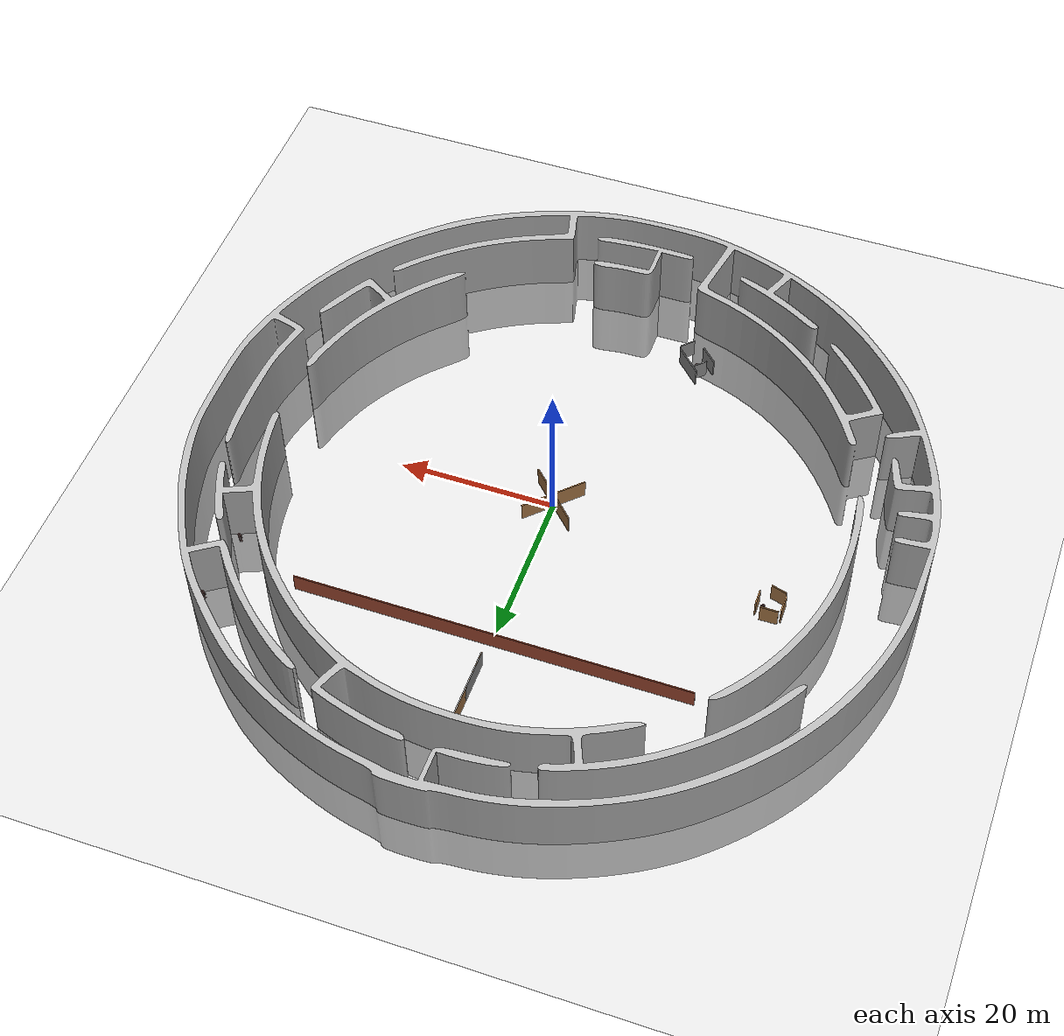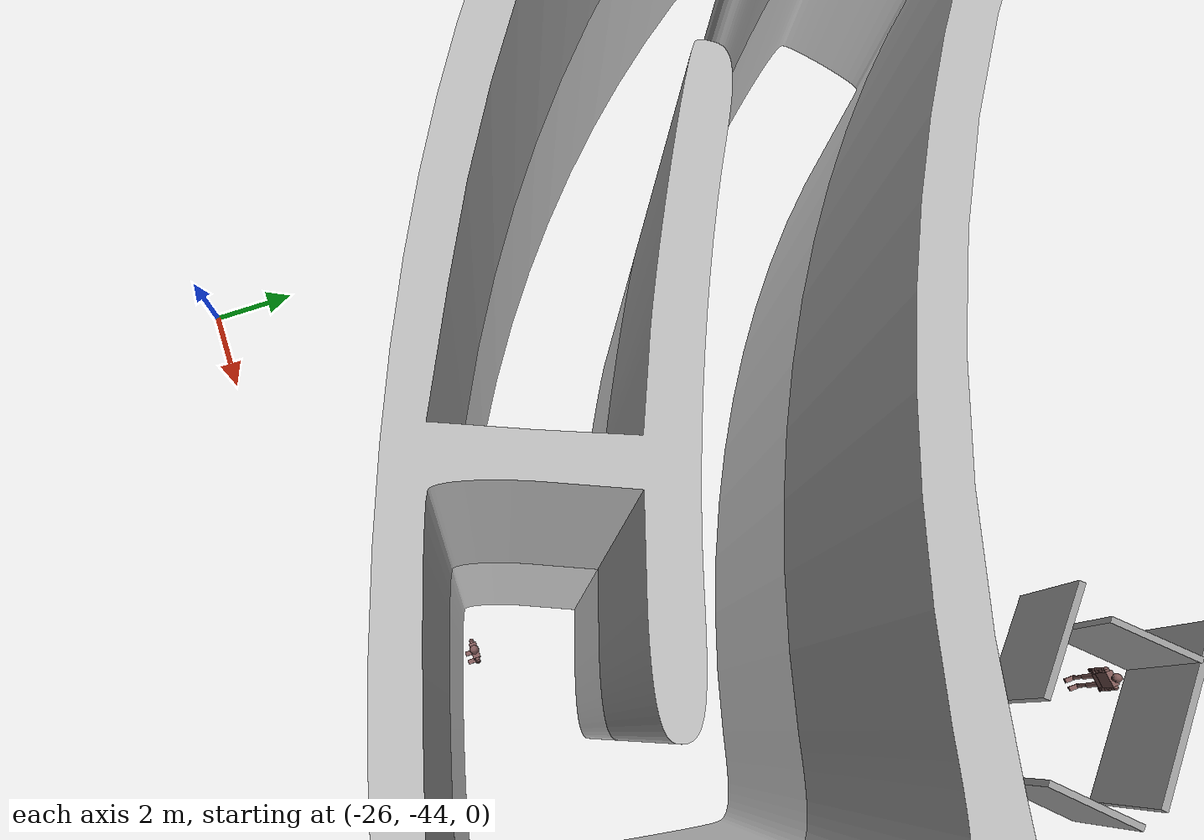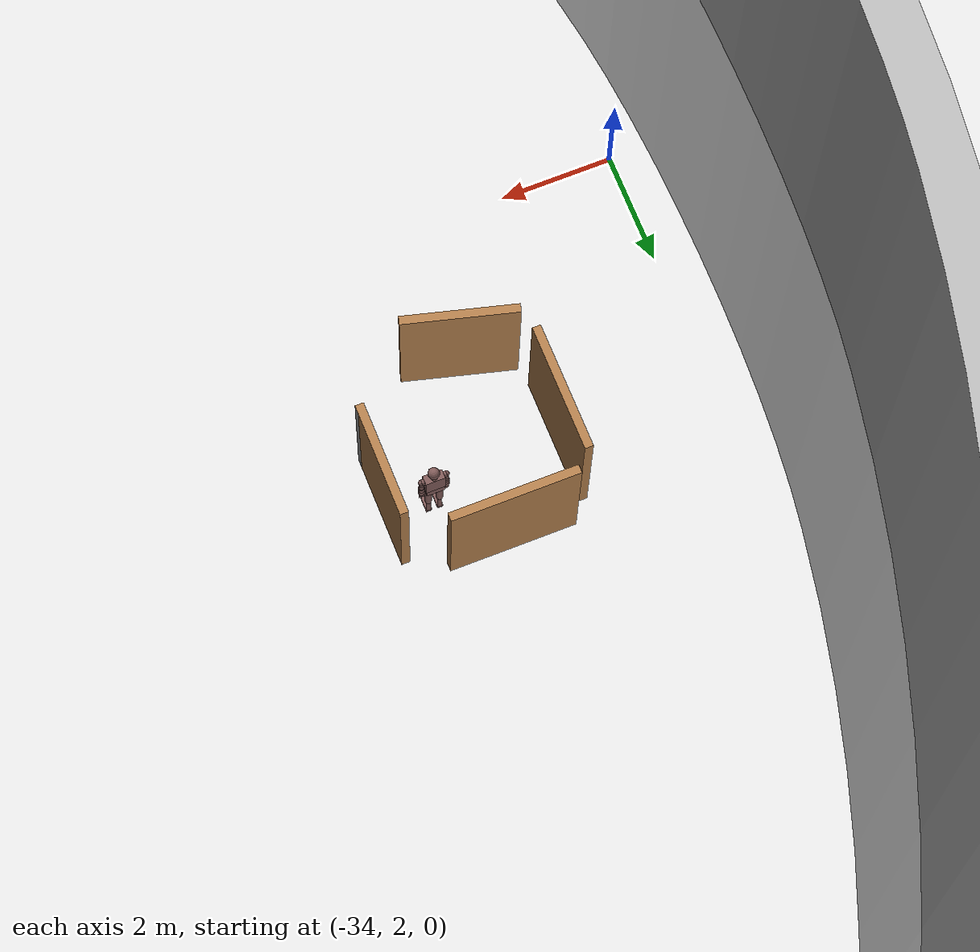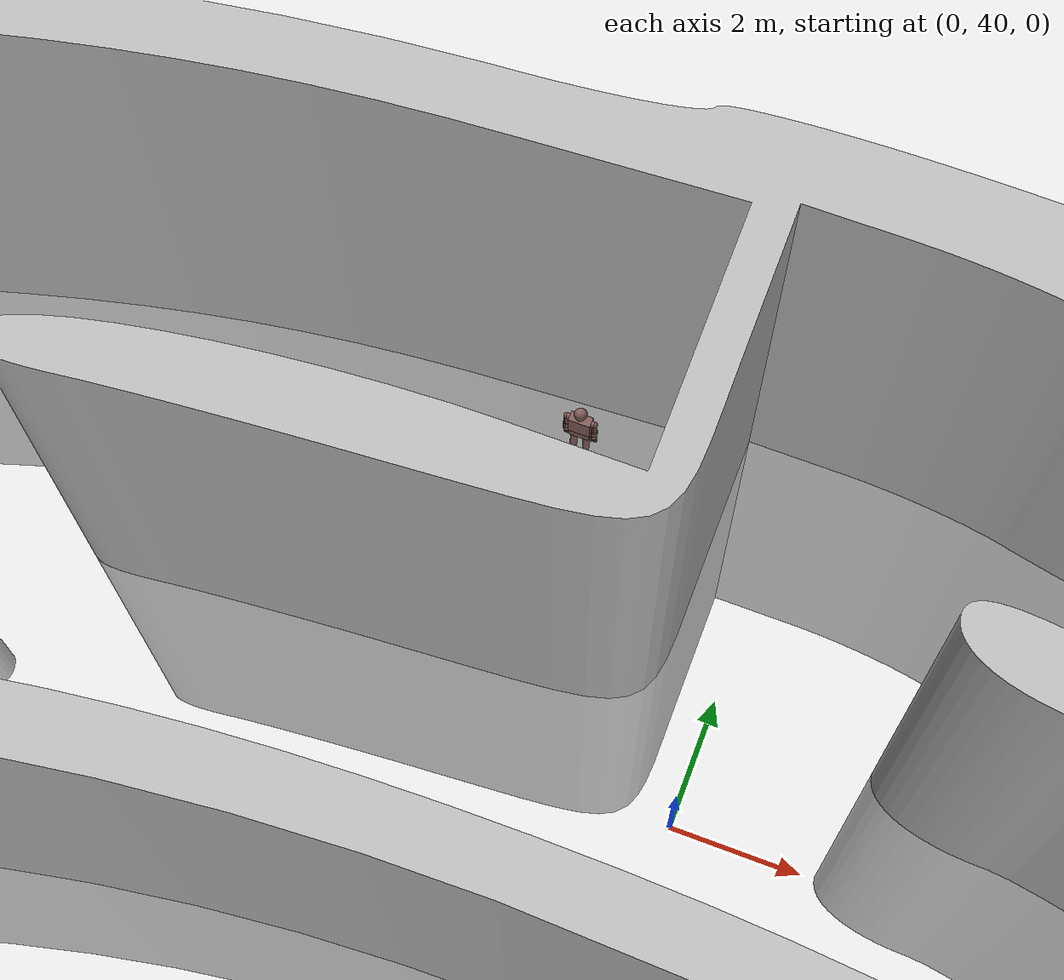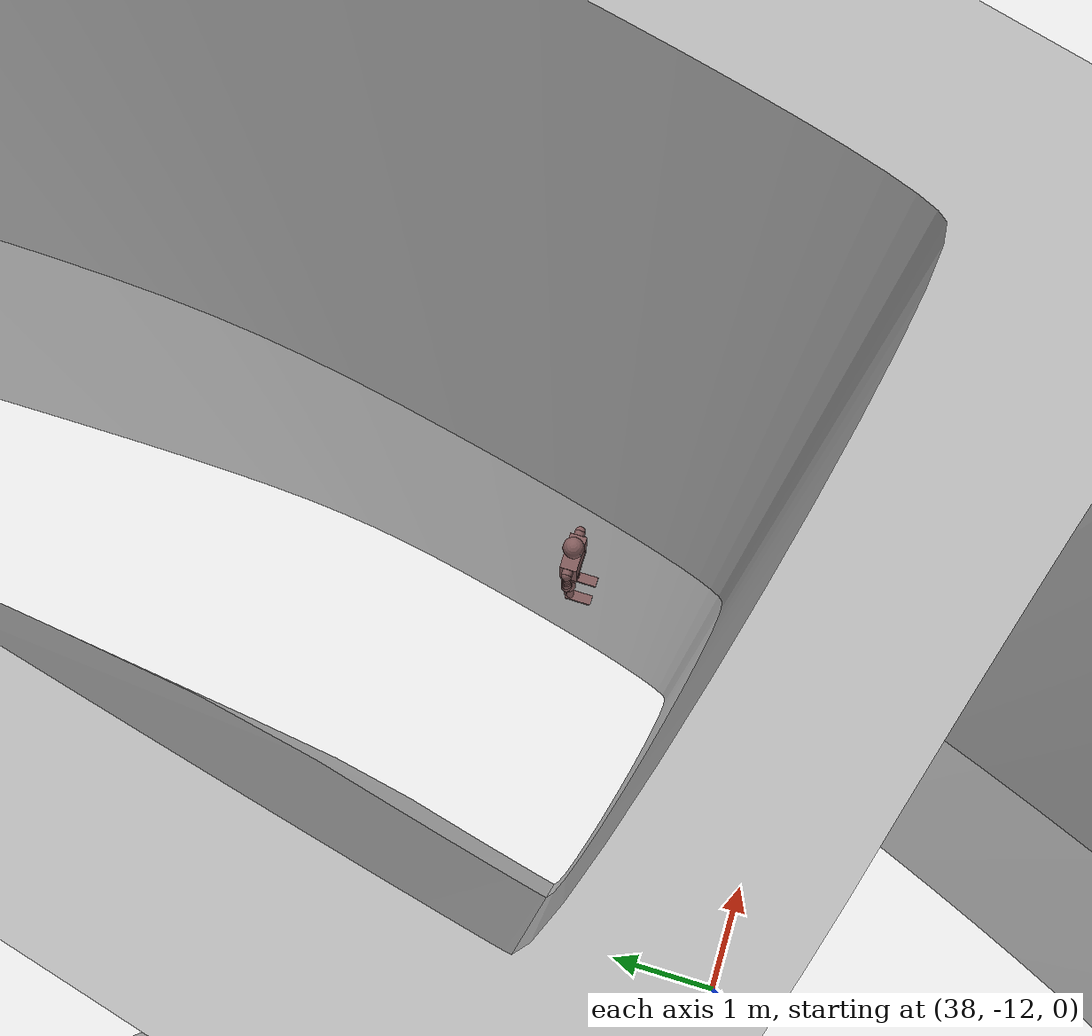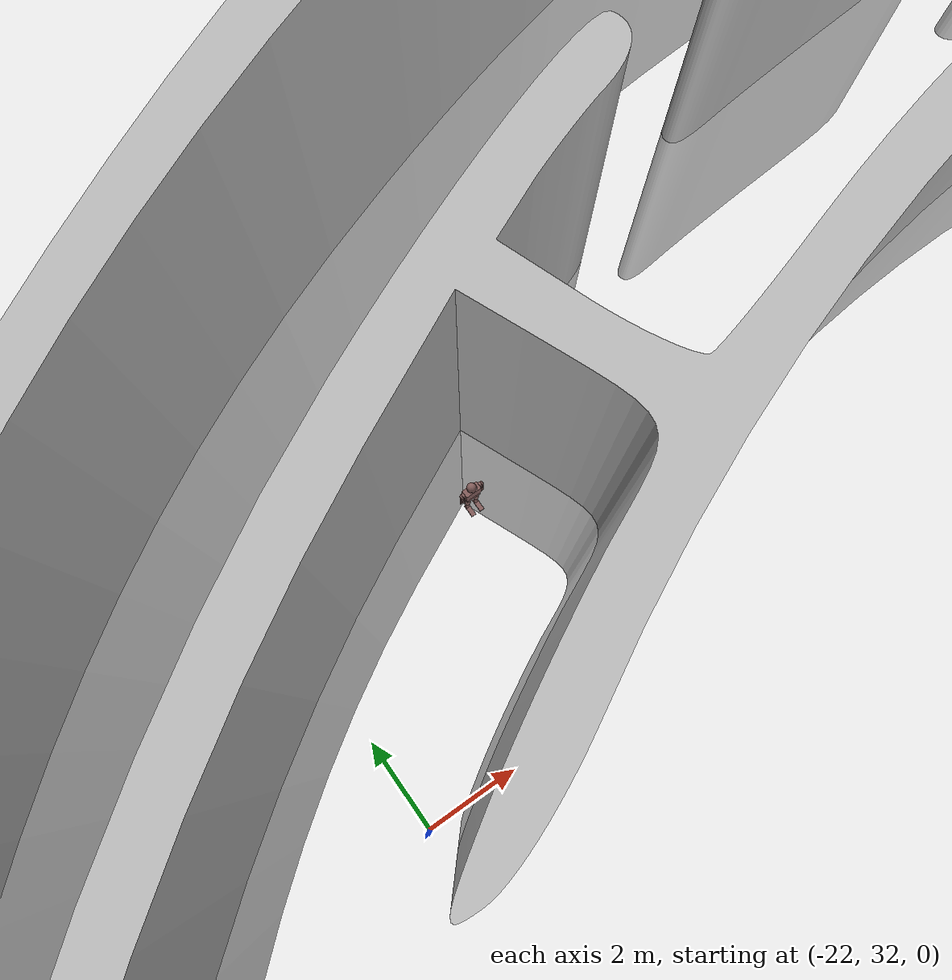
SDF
<sdf version="1.6">
 <world name="default">
  <light name="sun" type="directional">
   <pose>0 0 10 0 -0 0</pose>
   <diffuse>0.8 0.8 0.8 1</diffuse>
   <specular>0.2 0.2 0.2 1</specular>
   <attenuation>
    <range>1000</range>
    <constant>0.9</constant>
    <linear>0.01</linear>
    <quadratic>0.001</quadratic>
   </attenuation>
   <direction>-0.5 0.1 -0.9</direction>
  </light>
  <model name="ground_plane">
   <static>1</static>
   <link name="link">
    <collision name="collision">
     <geometry><plane><normal>0 0 1</normal><size>100 100</size></plane></geometry>
     <surface><friction><ode><mu>100</mu><mu2>50</mu2></ode></friction></surface>
    </collision>
    <visual name="visual">
     <cast_shadows>0</cast_shadows>
     <geometry><plane><normal>0 0 1</normal><size>100 100</size></plane></geometry>
     <material>
      <script><uri>file://media/materials/scripts/gazebo.material</uri><name>Gazebo/Grey</name></script>
     </material>
    </visual>
   </link>
  </model>
  <gravity>0 0 -9.8</gravity>
  <magnetic_field>6e-06 2.3e-05 -4.2e-05</magnetic_field>
  <atmosphere type="adiabatic"/>
  <physics name="default_physics" default="0" type="ode">
   <max_step_size>0.001</max_step_size>
   <real_time_factor>1</real_time_factor>
   <real_time_update_rate>1000</real_time_update_rate>
  </physics>
  <scene><ambient>0.4 0.4 0.4 1</ambient><background>0.7 0.7 0.7 1</background><shadows>1</shadows></scene>
  <spherical_coordinates>
   <surface_model>EARTH_WGS84</surface_model>
   <latitude_deg>0</latitude_deg>
   <longitude_deg>0</longitude_deg>
   <elevation>0</elevation>
   <heading_deg>0</heading_deg>
  </spherical_coordinates>
  <model name="out_1">
   <link name="link_1">
    <inertial>
     <mass>1</mass>
     <inertia>
      <ixx>0.166667</ixx>
      <ixy>0</ixy>
      <ixz>0</ixz>
      <iyy>0.166667</iyy>
      <iyz>0</iyz>
      <izz>0.166667</izz>
     </inertia>
    </inertial>
    <pose>-1.6e-05 1.1e-05 0 0 -0 0</pose>
    <visual name="visual">
     <geometry><mesh><uri>model://out_1/outer_maze_circ.stl</uri><scale>800 800 800</scale></mesh></geometry>
     <material>
      <lighting>1</lighting>
      <script><uri>file://media/materials/scripts/gazebo.material</uri><name>__default__</name></script>
     </material>
    </visual>
    <collision name="collision">
     <geometry><mesh><uri>model://out_1/outer_maze_circ.stl</uri><scale>800 800 800</scale></mesh></geometry>
     <surface>
      <friction>
       <ode><mu>1</mu><mu2>1</mu2><fdir1>0 0 0</fdir1><slip1>0</slip1><slip2>0</slip2></ode>
       <torsional>
        <coefficient>1</coefficient>
        <patch_radius>0</patch_radius>
        <surface_radius>0</surface_radius>
        <use_patch_radius>1</use_patch_radius>
        <ode><slip>0</slip></ode>
       </torsional>
      </friction>
      <bounce><restitution_coefficient>0</restitution_coefficient><threshold>1e+06</threshold></bounce>
      <contact>
       <collide_without_contact>0</collide_without_contact>
       <collide_without_contact_bitmask>1</collide_without_contact_bitmask>
       <collide_bitmask>1</collide_bitmask>
       <ode>
        <soft_cfm>0</soft_cfm>
        <soft_erp>0.2</soft_erp>
        <kp>1e+13</kp>
        <kd>1</kd>
        <max_vel>0.01</max_vel>
        <min_depth>0</min_depth>
       </ode>
       <bullet>
        <split_impulse>1</split_impulse>
        <split_impulse_penetration_threshold>-0.01</split_impulse_penetration_threshold>
        <soft_cfm>0</soft_cfm>
        <soft_erp>0.2</soft_erp>
        <kp>1e+13</kp>
        <kd>1</kd>
       </bullet>
      </contact>
     </surface>
    </collision>
   </link>
   <static>1</static>
  </model>
  <model name="obs1">
   <pose>-29.604 6.18643 0 0 -0 0</pose>
   <link name="Wall_10">
    <collision name="Wall_10_Collision">
     <geometry><box><size>2 0.15 2.5</size></box></geometry>
     <pose>0 0 1.25 0 -0 0</pose>
    </collision>
    <visual name="Wall_10_Visual">
     <pose>0 0 1.25 0 -0 0</pose>
     <geometry><box><size>2 0.15 2.5</size></box></geometry>
     <material>
      <script><uri>file://media/materials/scripts/gazebo.material</uri><name>Gazebo/Wood</name></script>
      <ambient>1 1 1 1</ambient>
     </material>
    </visual>
    <pose>-0.505188 -1.46687 0 0 0 -0.261799</pose>
   </link>
   <link name="Wall_2">
    <collision name="Wall_2_Collision">
     <geometry><box><size>2.25 0.15 2.5</size></box></geometry>
     <pose>0 0 1.25 0 -0 0</pose>
    </collision>
    <visual name="Wall_2_Visual">
     <pose>0 0 1.25 0 -0 0</pose>
     <geometry><box><size>2.25 0.15 2.5</size></box></geometry>
     <material>
      <script><uri>file://media/materials/scripts/gazebo.material</uri><name>Gazebo/Wood</name></script>
      <ambient>1 1 1 1</ambient>
     </material>
    </visual>
    <pose>-1.58039 0.313508 0 0 0 -1.5708</pose>
   </link>
   <link name="Wall_5">
    <collision name="Wall_5_Collision">
     <geometry><box><size>2.25 0.15 2.5</size></box></geometry>
     <pose>0 0 1.25 0 -0 0</pose>
    </collision>
    <visual name="Wall_5_Visual">
     <pose>0 0 1.25 0 -0 0</pose>
     <geometry><box><size>2.25 0.15 2.5</size></box></geometry>
     <material>
      <script><uri>file://media/materials/scripts/gazebo.material</uri><name>Gazebo/Wood</name></script>
      <ambient>1 1 1 1</ambient>
     </material>
    </visual>
    <pose>-0.185262 1.72313 0 0 -0 0</pose>
   </link>
   <link name="Wall_7">
    <collision name="Wall_7_Collision">
     <geometry><box><size>2 0.15 2.5</size></box></geometry>
     <pose>0 0 1.25 0 -0 0</pose>
    </collision>
    <visual name="Wall_7_Visual">
     <pose>0 0 1.25 0 -0 0</pose>
     <geometry><box><size>2 0.15 2.5</size></box></geometry>
     <material>
      <script><uri>file://media/materials/scripts/gazebo.material</uri><name>Gazebo/Wood</name></script>
      <ambient>1 1 1 1</ambient>
     </material>
    </visual>
    <pose>1.58039 0.398833 0 0 0 -1.5708</pose>
   </link>
   <link name="Wall_8">
    <collision name="Wall_8_Collision">
     <geometry><box><size>0.15 0.15 2.5</size></box></geometry>
     <pose>0 0 1.25 0 -0 0</pose>
    </collision>
    <visual name="Wall_8_Visual">
     <pose>0 0 1.25 0 -0 0</pose>
     <geometry><box><size>0.15 0.15 2.5</size></box></geometry>
     <material>
      <script><uri>file://media/materials/scripts/gazebo.material</uri><name>Gazebo/Grey</name></script>
      <ambient>1 1 1 1</ambient>
     </material>
    </visual>
    <pose>1.58039 -0.526167 0 0 -0 0</pose>
   </link>
   <static>1</static>
  </model>
  <model name="obs2">
   <pose>-9.93227 -27.6503 0 0 -0 0</pose>
   <link name="Wall_0">
    <collision name="Wall_0_Collision">
     <geometry><box><size>2 0.15 2.5</size></box></geometry>
     <pose>0 0 1.25 0 -0 0</pose>
    </collision>
    <visual name="Wall_0_Visual">
     <pose>0 0 1.25 0 -0 0</pose>
     <geometry><box><size>2 0.15 2.5</size></box></geometry>
     <material>
      <script><uri>file://media/materials/scripts/gazebo.material</uri><name>Gazebo/Grey</name></script>
      <ambient>1 1 1 1</ambient>
     </material>
    </visual>
    <pose>-0.796332 1.10862 0 0 -0 0.785398</pose>
   </link>
   <link name="Wall_2">
    <collision name="Wall_2_Collision">
     <geometry><box><size>4.25 0.15 2.5</size></box></geometry>
     <pose>0 0 1.25 0 -0 0</pose>
    </collision>
    <visual name="Wall_2_Visual">
     <pose>0 0 1.25 0 -0 0</pose>
     <geometry><box><size>4.25 0.15 2.5</size></box></geometry>
     <material>
      <script><uri>file://media/materials/scripts/gazebo.material</uri><name>Gazebo/Grey</name></script>
      <ambient>1 1 1 1</ambient>
     </material>
    </visual>
    <pose>0.773928 0.982661 0 0 0 -0.785398</pose>
   </link>
   <link name="Wall_4">
    <collision name="Wall_4_Collision">
     <geometry><box><size>2.75 0.15 2.5</size></box></geometry>
     <pose>0 0 1.25 0 -0 0</pose>
    </collision>
    <visual name="Wall_4_Visual">
     <pose>0 0 1.25 0 -0 0</pose>
     <geometry><box><size>2.75 0.15 2.5</size></box></geometry>
     <material>
      <script><uri>file://media/materials/scripts/gazebo.material</uri><name>Gazebo/Grey</name></script>
      <ambient>1 1 1 1</ambient>
     </material>
    </visual>
    <pose>-1.45556 -0.740711 0 0 0 -0.785398</pose>
   </link>
   <link name="Wall_6">
    <collision name="Wall_6_Collision">
     <geometry><box><size>2 0.15 2.5</size></box></geometry>
     <pose>0 0 1.25 0 -0 0</pose>
    </collision>
    <visual name="Wall_6_Visual">
     <pose>0 0 1.25 0 -0 0</pose>
     <geometry><box><size>2 0.15 2.5</size></box></geometry>
     <material>
      <script><uri>file://media/materials/scripts/gazebo.material</uri><name>Gazebo/Grey</name></script>
      <ambient>1 1 1 1</ambient>
     </material>
    </visual>
    <pose>1.72073 -1.77816 0 0 -0 0.785398</pose>
   </link>
   <static>1</static>
  </model>
  <model name="obs3">
   <pose>-0.053167 -0.052031 0 0 -0 0</pose>
   <link name="Wall_0">
    <collision name="Wall_0_Collision">
     <geometry><box><size>8.63528 0.15 2.5</size></box></geometry>
     <pose>0 0 1.25 0 -0 0</pose>
    </collision>
    <visual name="Wall_0_Visual">
     <pose>0 0 1.25 0 -0 0</pose>
     <geometry><box><size>8.63528 0.15 2.5</size></box></geometry>
     <material>
      <script><uri>file://media/materials/scripts/gazebo.material</uri><name>Gazebo/Wood</name></script>
      <ambient>1 1 1 1</ambient>
     </material>
    </visual>
    <pose>0 0 0 0 0 -0.785398</pose>
   </link>
   <link name="Wall_2">
    <collision name="Wall_2_Collision">
     <geometry><box><size>8.63528 0.15 2.5</size></box></geometry>
     <pose>0 0 1.25 0 -0 0</pose>
    </collision>
    <visual name="Wall_2_Visual">
     <pose>0 0 1.25 0 -0 0</pose>
     <geometry><box><size>8.63528 0.15 2.5</size></box></geometry>
     <material>
      <script><uri>file://media/materials/scripts/gazebo.material</uri><name>Gazebo/Wood</name></script>
      <ambient>1 1 1 1</ambient>
     </material>
    </visual>
    <pose>0 0 0 0 0 -2.35619</pose>
   </link>
   <static>1</static>
  </model>
  <model name="wall1">
   <pose>0 22 0 0 -0 0</pose>
   <link name="Wall_0">
    <collision name="Wall_0_Collision">
     <geometry><box><size>50 0.15 2.5</size></box></geometry>
     <pose>0 0 1.25 0 -0 0</pose>
    </collision>
    <visual name="Wall_0_Visual">
     <pose>0 0 1.25 0 -0 0</pose>
     <geometry><box><size>50 0.15 2.5</size></box></geometry>
     <material>
      <script><uri>file://media/materials/scripts/gazebo.material</uri><name>Gazebo/Bricks</name></script>
      <ambient>1 1 1 1</ambient>
     </material>
    </visual>
    <pose>1e-06 0 0 0 -0 3.14159</pose>
   </link>
   <static>1</static>
  </model>
  <model name="wall-10m-amodi">
   <pose>-0.002128 29.7924 0 0 -0 0</pose>
   <link name="Wall_24">
    <collision name="Wall_24_Collision">
     <geometry><box><size>10 0.15 2.5</size></box></geometry>
     <pose>0 0 1.25 0 -0 0</pose>
    </collision>
    <visual name="Wall_24_Visual">
     <pose>0 0 1.25 0 -0 0</pose>
     <geometry><box><size>10 0.15 2.5</size></box></geometry>
     <material>
      <script><uri>file://media/materials/scripts/gazebo.material</uri><name>Gazebo/Grey</name></script>
      <ambient>1 1 1 1</ambient>
     </material>
    </visual>
    <pose>0 -0 0 0 0 -1.5708</pose>
   </link>
   <link name="Wall_25">
    <collision name="Wall_25_Collision">
     <geometry><box><size>10 0.15 2.5</size></box></geometry>
     <pose>0 0 1.25 0 -0 0</pose>
    </collision>
    <visual name="Wall_25_Visual">
     <pose>0 0 1.25 0 -0 0</pose>
     <geometry><box><size>10 0.15 2.5</size></box></geometry>
     <material>
      <script><uri>file://media/materials/scripts/gazebo.material</uri><name>Gazebo/Wood</name></script>
      <ambient>1 1 1 1</ambient>
     </material>
    </visual>
    <pose>0 -0 0 0 -0 1.5708</pose>
   </link>
   <static>1</static>
  </model>
  <model name="victim175_hot_moving">
   <static>1</static>
   <self_collide>1</self_collide>
   <link name="head">
    <pose>0 0 1.625 0 -0 0</pose>
    <visual name="visual">
     <geometry><sphere><radius>0.1</radius></sphere></geometry>
     <material>
      <emissive>0.5 0.35 0.35 1</emissive>
      <ambient>0.5 0.35 0.35 1</ambient>
      <diffuse>0.5 0.35 0.35 1</diffuse>
      <specular>0 0 0 0</specular>
     </material>
    </visual>
    <collision name="collision"><geometry><sphere><radius>0.1</radius></sphere></geometry></collision>
    <visual name="visual_nose">
     <pose>0 -0.1 -0.01 0 -0 0</pose>
     <geometry><sphere><radius>0.01</radius></sphere></geometry>
     <material>
      <emissive>0.5 0.35 0.35 1</emissive>
      <ambient>0.5 0.35 0.35 1</ambient>
      <diffuse>0.5 0.35 0.35 1</diffuse>
      <specular>0 0 0 0</specular>
     </material>
    </visual>
    <visual name="visual_rEye">
     <pose>-0.05 -0.08 0.02 0 -0 0</pose>
     <geometry><sphere><radius>0.01</radius></sphere></geometry>
     <material>
      <script><uri>file://media/materials/scripts/gazebo.material</uri><name>Gazebo/Black</name></script>
     </material>
    </visual>
    <visual name="visual_lEye">
     <pose>0.05 -0.08 0.02 0 -0 0</pose>
     <geometry><sphere><radius>0.01</radius></sphere></geometry>
     <material>
      <script><uri>file://media/materials/scripts/gazebo.material</uri><name>Gazebo/Black</name></script>
     </material>
    </visual>
    <self_collide>1</self_collide>
   </link>
   <link name="neck">
    <pose>0 0.02 1.49 0 -0 0</pose>
    <visual name="visual">
     <geometry><cylinder><radius>0.05</radius><length>0.15</length></cylinder></geometry>
     <material>
      <emissive>0.5 0.35 0.35 1</emissive>
      <ambient>0.5 0.35 0.35 1</ambient>
      <diffuse>0.5 0.35 0.35 1</diffuse>
      <specular>0 0 0 0</specular>
     </material>
    </visual>
    <collision name="collision">
     <geometry><cylinder><radius>0.05</radius><length>0.15</length></cylinder></geometry>
    </collision>
    <self_collide>1</self_collide>
   </link>
   <joint name="neck_head" type="revolute">
    <pose>0 0.02 -0.075 0 -0 0</pose>
    <child>head</child>
    <parent>neck</parent>
    <axis>
     <xyz>0 0 -1</xyz>
     <limit><lower>-1.7</lower><upper>1.7</upper></limit>
     <dynamics>
      <friction>0.01</friction>
      <spring_reference>0</spring_reference>
      <spring_stiffness>0</spring_stiffness>
     </dynamics>
     <use_parent_model_frame>0</use_parent_model_frame>
    </axis>
   </joint>
   <link name="body">
    <pose>0 0 1.255 0 -0 0</pose>
    <visual name="visual">
     <geometry><box><size>0.34 0.16 0.4</size></box></geometry>
     <material>
      <emissive>0.5 0.35 0.35 1</emissive>
      <ambient>0.5 0.35 0.35 1</ambient>
      <diffuse>0.5 0.35 0.35 1</diffuse>
      <specular>0 0 0 0</specular>
     </material>
    </visual>
    <collision name="collision"><geometry><box><size>0.34 0.16 0.4</size></box></geometry></collision>
    <self_collide>1</self_collide>
   </link>
   <joint name="body_neck" type="revolute">
    <pose>0 0.06 -0.075 0 -0 0</pose>
    <child>neck</child>
    <parent>body</parent>
    <axis>
     <xyz>1 0 0</xyz>
     <limit><lower>-0.2</lower><upper>1</upper></limit>
     <dynamics>
      <friction>0.01</friction>
      <spring_reference>0</spring_reference>
      <spring_stiffness>0</spring_stiffness>
     </dynamics>
     <use_parent_model_frame>0</use_parent_model_frame>
    </axis>
   </joint>
   <link name="waist">
    <pose>0 0 1.005 0 -0 0</pose>
    <visual name="visual">
     <pose>0 0 -0.025 0 -0 0</pose>
     <geometry><box><size>0.31 0.16 0.15</size></box></geometry>
     <material>
      <emissive>0.5 0.35 0.35 1</emissive>
      <ambient>0.5 0.35 0.35 1</ambient>
      <diffuse>0.5 0.35 0.35 1</diffuse>
      <specular>0 0 0 0</specular>
     </material>
    </visual>
    <collision name="collision"><geometry><box><size>0.31 0.16 0.1</size></box></geometry></collision>
    <visual name="visual2">
     <pose>0 0 0.05 3.14159 1.57079 3.14159</pose>
     <geometry><cylinder><radius>0.08</radius><length>0.31</length></cylinder></geometry>
     <material>
      <emissive>0.5 0.35 0.35 1</emissive>
      <ambient>0.5 0.35 0.35 1</ambient>
      <diffuse>0.5 0.35 0.35 1</diffuse>
      <specular>0 0 0 0</specular>
     </material>
    </visual>
    <collision name="collision2">
     <pose>0 0 0.05 3.14159 1.57079 3.14159</pose>
     <geometry><cylinder><radius>0.08</radius><length>0.31</length></cylinder></geometry>
    </collision>
    <self_collide>1</self_collide>
   </link>
   <joint name="body_waist" type="revolute">
    <pose>0 0 0.05 0 -0 0</pose>
    <child>waist</child>
    <parent>body</parent>
    <axis>
     <xyz>-1 0 0</xyz>
     <limit><lower>0</lower><upper>0</upper></limit>
     <dynamics>
      <friction>0.01</friction>
      <spring_reference>0</spring_reference>
      <spring_stiffness>0</spring_stiffness>
     </dynamics>
     <use_parent_model_frame>0</use_parent_model_frame>
    </axis>
   </joint>
   <link name="rHand">
    <pose>-0.22 0 0.84 0 -0 0</pose>
    <visual name="visual">
     <geometry><box><size>0.09 0.02 0.18</size></box></geometry>
     <material>
      <emissive>0.5 0.35 0.35 1</emissive>
      <ambient>0.5 0.35 0.35 1</ambient>
      <diffuse>0.5 0.35 0.35 1</diffuse>
      <specular>0 0 0 0</specular>
     </material>
    </visual>
    <collision name="collision"><geometry><box><size>0.09 0.02 0.18</size></box></geometry></collision>
    <visual name="visual2">
     <pose>0.02 0 0 0 -0 0</pose>
     <geometry><box><size>0.12 0.02 0.09</size></box></geometry>
     <material>
      <emissive>0.5 0.35 0.35 1</emissive>
      <ambient>0.5 0.35 0.35 1</ambient>
      <diffuse>0.5 0.35 0.35 1</diffuse>
      <specular>0 0 0 0</specular>
     </material>
    </visual>
    <collision name="collision2">
     <pose>0.02 0 0 0 -0 0</pose>
     <geometry><box><size>0.12 0.02 0.09</size></box></geometry>
    </collision>
    <self_collide>1</self_collide>
   </link>
   <link name="lHand">
    <pose>0.22 0 0.84 0 -0 0</pose>
    <visual name="visual">
     <geometry><box><size>0.09 0.02 0.18</size></box></geometry>
     <material>
      <emissive>0.5 0.35 0.35 1</emissive>
      <ambient>0.5 0.35 0.35 1</ambient>
      <diffuse>0.5 0.35 0.35 1</diffuse>
      <specular>0 0 0 0</specular>
     </material>
    </visual>
    <collision name="collision"><geometry><box><size>0.09 0.02 0.18</size></box></geometry></collision>
    <visual name="visual2">
     <pose>-0.02 0 0 0 -0 0</pose>
     <geometry><box><size>0.12 0.02 0.09</size></box></geometry>
     <material>
      <emissive>0.5 0.35 0.35 1</emissive>
      <ambient>0.5 0.35 0.35 1</ambient>
      <diffuse>0.5 0.35 0.35 1</diffuse>
      <specular>0 0 0 0</specular>
     </material>
    </visual>
    <collision name="collision2">
     <pose>-0.02 0 0 0 -0 0</pose>
     <geometry><box><size>0.12 0.02 0.09</size></box></geometry>
    </collision>
    <self_collide>1</self_collide>
   </link>
   <link name="rFoot">
    <pose>-0.1 -0.095 0.02 0 -0 0</pose>
    <visual name="visual">
     <geometry><box><size>0.1 0.27 0.04</size></box></geometry>
     <material>
      <emissive>0.5 0.35 0.35 1</emissive>
      <ambient>0.5 0.35 0.35 1</ambient>
      <diffuse>0.5 0.35 0.35 1</diffuse>
      <specular>0 0 0 0</specular>
     </material>
    </visual>
    <collision name="collision"><geometry><box><size>0.1 0.27 0.04</size></box></geometry></collision>
    <self_collide>1</self_collide>
   </link>
   <link name="lFoot">
    <pose>0.1 -0.095 0.02 0 -0 0</pose>
    <visual name="visual">
     <geometry><box><size>0.1 0.27 0.04</size></box></geometry>
     <material>
      <emissive>0.5 0.35 0.35 1</emissive>
      <ambient>0.5 0.35 0.35 1</ambient>
      <diffuse>0.5 0.35 0.35 1</diffuse>
      <specular>0 0 0 0</specular>
     </material>
    </visual>
    <collision name="collision"><geometry><box><size>0.1 0.27 0.04</size></box></geometry></collision>
    <self_collide>1</self_collide>
   </link>
   <link name="rLeg2">
    <pose>-0.1 0 0.23 0 -0 0</pose>
    <visual name="visual">
     <geometry><cylinder><radius>0.04</radius><length>0.38</length></cylinder></geometry>
     <material>
      <emissive>0.5 0.35 0.35 1</emissive>
      <ambient>0.5 0.35 0.35 1</ambient>
      <diffuse>0.5 0.35 0.35 1</diffuse>
      <specular>0 0 0 0</specular>
     </material>
    </visual>
    <collision name="collision">
     <geometry><cylinder><radius>0.04</radius><length>0.38</length></cylinder></geometry>
    </collision>
    <visual name="visual2">
     <pose>0 0 -0.19 0 -0 0</pose>
     <geometry><sphere><radius>0.04</radius></sphere></geometry>
     <material>
      <emissive>0.5 0.35 0.35 1</emissive>
      <ambient>0.5 0.35 0.35 1</ambient>
      <diffuse>0.5 0.35 0.35 1</diffuse>
      <specular>0 0 0 0</specular>
     </material>
    </visual>
    <collision name="collision2">
     <pose>0 0 -0.19 0 -0 0</pose>
     <geometry><sphere><radius>0.04</radius></sphere></geometry>
    </collision>
    <self_collide>1</self_collide>
   </link>
   <link name="lLeg2">
    <pose>0.1 0 0.23 0 -0 0</pose>
    <visual name="visual">
     <geometry><cylinder><radius>0.04</radius><length>0.38</length></cylinder></geometry>
     <material>
      <emissive>0.5 0.35 0.35 1</emissive>
      <ambient>0.5 0.35 0.35 1</ambient>
      <diffuse>0.5 0.35 0.35 1</diffuse>
      <specular>0 0 0 0</specular>
     </material>
    </visual>
    <collision name="collision">
     <geometry><cylinder><radius>0.04</radius><length>0.38</length></cylinder></geometry>
    </collision>
    <visual name="visual2">
     <pose>0 0 -0.19 0 -0 0</pose>
     <geometry><sphere><radius>0.04</radius></sphere></geometry>
     <material>
      <emissive>0.5 0.35 0.35 1</emissive>
      <ambient>0.5 0.35 0.35 1</ambient>
      <diffuse>0.5 0.35 0.35 1</diffuse>
      <specular>0 0 0 0</specular>
     </material>
    </visual>
    <collision name="collision2">
     <pose>0 0 -0.19 0 -0 0</pose>
     <geometry><sphere><radius>0.04</radius></sphere></geometry>
    </collision>
    <self_collide>1</self_collide>
   </link>
   <joint name="rLeg2_rFoot" type="revolute">
    <pose>0 0.095 0.02 0 -0 0</pose>
    <child>rFoot</child>
    <parent>rLeg2</parent>
    <axis>
     <xyz>1 0 0</xyz>
     <limit><lower>0</lower><upper>0</upper></limit>
     <dynamics>
      <friction>0.01</friction>
      <spring_reference>0</spring_reference>
      <spring_stiffness>0</spring_stiffness>
     </dynamics>
     <use_parent_model_frame>0</use_parent_model_frame>
    </axis>
   </joint>
   <joint name="lLeg2_lFoot" type="revolute">
    <pose>0 0.095 0.02 0 -0 0</pose>
    <child>lFoot</child>
    <parent>lLeg2</parent>
    <axis>
     <xyz>1 0 0</xyz>
     <limit><lower>0</lower><upper>0</upper></limit>
     <dynamics>
      <friction>0.01</friction>
      <spring_reference>0</spring_reference>
      <spring_stiffness>0</spring_stiffness>
     </dynamics>
     <use_parent_model_frame>0</use_parent_model_frame>
    </axis>
   </joint>
   <link name="rLeg1">
    <pose>-0.1 0 0.66 0 -0 0</pose>
    <visual name="visual">
     <geometry><cylinder><radius>0.055</radius><length>0.48</length></cylinder></geometry>
     <material>
      <emissive>0.5 0.35 0.35 1</emissive>
      <ambient>0.5 0.35 0.35 1</ambient>
      <diffuse>0.5 0.35 0.35 1</diffuse>
      <specular>0 0 0 0</specular>
     </material>
    </visual>
    <collision name="collision">
     <geometry><cylinder><radius>0.055</radius><length>0.48</length></cylinder></geometry>
    </collision>
    <visual name="visual2">
     <pose>0 0 -0.24 0 -0 0</pose>
     <geometry><sphere><radius>0.055</radius></sphere></geometry>
     <material>
      <emissive>0.5 0.35 0.35 1</emissive>
      <ambient>0.5 0.35 0.35 1</ambient>
      <diffuse>0.5 0.35 0.35 1</diffuse>
      <specular>0 0 0 0</specular>
     </material>
    </visual>
    <collision name="collision2">
     <pose>0 0 -0.24 0 -0 0</pose>
     <geometry><sphere><radius>0.055</radius></sphere></geometry>
    </collision>
    <visual name="visual3">
     <pose>0 0 0.24 0 -0 0</pose>
     <geometry><sphere><radius>0.055</radius></sphere></geometry>
     <material>
      <emissive>0.5 0.35 0.35 1</emissive>
      <ambient>0.5 0.35 0.35 1</ambient>
      <diffuse>0.5 0.35 0.35 1</diffuse>
      <specular>0 0 0 0</specular>
     </material>
    </visual>
    <collision name="collision3">
     <pose>0 0 0.24 0 -0 0</pose>
     <geometry><sphere><radius>0.055</radius></sphere></geometry>
    </collision>
    <self_collide>1</self_collide>
   </link>
   <link name="lLeg1">
    <pose>0.1 0 0.66 0 -0 0</pose>
    <visual name="visual">
     <geometry><cylinder><radius>0.055</radius><length>0.48</length></cylinder></geometry>
     <material>
      <emissive>0.5 0.35 0.35 1</emissive>
      <ambient>0.5 0.35 0.35 1</ambient>
      <diffuse>0.5 0.35 0.35 1</diffuse>
      <specular>0 0 0 0</specular>
     </material>
    </visual>
    <collision name="collision">
     <geometry><cylinder><radius>0.055</radius><length>0.48</length></cylinder></geometry>
    </collision>
    <visual name="visual2">
     <pose>0 0 -0.24 0 -0 0</pose>
     <geometry><sphere><radius>0.055</radius></sphere></geometry>
     <material>
      <emissive>0.5 0.35 0.35 1</emissive>
      <ambient>0.5 0.35 0.35 1</ambient>
      <diffuse>0.5 0.35 0.35 1</diffuse>
      <specular>0 0 0 0</specular>
     </material>
    </visual>
    <collision name="collision2">
     <pose>0 0 -0.24 0 -0 0</pose>
     <geometry><sphere><radius>0.055</radius></sphere></geometry>
    </collision>
    <visual name="visual3">
     <pose>0 0 0.24 0 -0 0</pose>
     <geometry><sphere><radius>0.055</radius></sphere></geometry>
     <material>
      <emissive>0.5 0.35 0.35 1</emissive>
      <ambient>0.5 0.35 0.35 1</ambient>
      <diffuse>0.5 0.35 0.35 1</diffuse>
      <specular>0 0 0 0</specular>
     </material>
    </visual>
    <collision name="collision3">
     <pose>0 0 0.24 0 -0 0</pose>
     <geometry><sphere><radius>0.055</radius></sphere></geometry>
    </collision>
    <self_collide>1</self_collide>
   </link>
   <joint name="rLeg1_rLeg2" type="revolute">
    <pose>0 0 0.19 0 -0 0</pose>
    <child>rLeg2</child>
    <parent>rLeg1</parent>
    <axis>
     <xyz>1 0 0</xyz>
     <limit><lower>0</lower><upper>0</upper></limit>
     <dynamics>
      <friction>0.01</friction>
      <spring_reference>0</spring_reference>
      <spring_stiffness>0</spring_stiffness>
     </dynamics>
     <use_parent_model_frame>0</use_parent_model_frame>
    </axis>
   </joint>
   <joint name="lLeg1_lLeg2" type="revolute">
    <pose>0 0 0.19 0 -0 0</pose>
    <child>lLeg2</child>
    <parent>lLeg1</parent>
    <axis>
     <xyz>1 0 0</xyz>
     <limit><lower>0</lower><upper>0</upper></limit>
     <dynamics>
      <friction>0.01</friction>
      <spring_reference>0</spring_reference>
      <spring_stiffness>0</spring_stiffness>
     </dynamics>
     <use_parent_model_frame>0</use_parent_model_frame>
    </axis>
   </joint>
   <link name="rButt">
    <pose>-0.1 0 0.9275 0 -0 0</pose>
    <visual name="visual">
     <geometry><cylinder><radius>0.055</radius><length>0.055</length></cylinder></geometry>
     <material>
      <emissive>0.5 0.35 0.35 1</emissive>
      <ambient>0.5 0.35 0.35 1</ambient>
      <diffuse>0.5 0.35 0.35 1</diffuse>
      <specular>0 0 0 0</specular>
     </material>
    </visual>
    <collision name="collision">
     <geometry><cylinder><radius>0.055</radius><length>0.055</length></cylinder></geometry>
    </collision>
    <self_collide>1</self_collide>
   </link>
   <link name="lButt">
    <pose>0.1 0 0.9275 0 -0 0</pose>
    <visual name="visual">
     <geometry><cylinder><radius>0.055</radius><length>0.055</length></cylinder></geometry>
     <material>
      <emissive>0.5 0.35 0.35 1</emissive>
      <ambient>0.5 0.35 0.35 1</ambient>
      <diffuse>0.5 0.35 0.35 1</diffuse>
      <specular>0 0 0 0</specular>
     </material>
    </visual>
    <collision name="collision">
     <geometry><cylinder><radius>0.055</radius><length>0.055</length></cylinder></geometry>
    </collision>
    <self_collide>1</self_collide>
   </link>
   <joint name="rButt_rLeg1" type="revolute">
    <pose>0 0 0.24 0 -0 0</pose>
    <child>rLeg1</child>
    <parent>rButt</parent>
    <axis>
     <xyz>1 0 0</xyz>
     <limit><lower>0</lower><upper>0</upper></limit>
     <dynamics>
      <friction>0.01</friction>
      <spring_reference>0</spring_reference>
      <spring_stiffness>0</spring_stiffness>
     </dynamics>
     <use_parent_model_frame>0</use_parent_model_frame>
    </axis>
   </joint>
   <joint name="lButt_lLeg1" type="revolute">
    <pose>0 0 0.24 0 -0 0</pose>
    <child>lLeg1</child>
    <parent>lButt</parent>
    <axis>
     <xyz>1 0 0</xyz>
     <limit><lower>0</lower><upper>0</upper></limit>
     <dynamics>
      <friction>0.01</friction>
      <spring_reference>0</spring_reference>
      <spring_stiffness>0</spring_stiffness>
     </dynamics>
     <use_parent_model_frame>0</use_parent_model_frame>
    </axis>
   </joint>
   <joint name="waist_rButt" type="revolute">
    <child>rButt</child>
    <parent>waist</parent>
    <axis>
     <xyz>0 0 -1</xyz>
     <limit><lower>-1</lower><upper>1</upper></limit>
     <dynamics>
      <friction>0.01</friction>
      <spring_reference>0</spring_reference>
      <spring_stiffness>0</spring_stiffness>
     </dynamics>
     <use_parent_model_frame>0</use_parent_model_frame>
    </axis>
   </joint>
   <joint name="waist_lButt" type="revolute">
    <child>lButt</child>
    <parent>waist</parent>
    <axis>
     <xyz>0 0 1</xyz>
     <limit><lower>-1</lower><upper>1</upper></limit>
     <dynamics>
      <friction>0.01</friction>
      <spring_reference>0</spring_reference>
      <spring_stiffness>0</spring_stiffness>
     </dynamics>
     <use_parent_model_frame>0</use_parent_model_frame>
    </axis>
   </joint>
   <link name="rShoulder">
    <pose>-0.195 0 1.4 0 -0 0</pose>
    <visual name="visual">
     <pose>0 0 0 3.14159 1.57079 3.14159</pose>
     <geometry><cylinder><radius>0.05</radius><length>0.05</length></cylinder></geometry>
     <material>
      <emissive>0.5 0.35 0.35 1</emissive>
      <ambient>0.5 0.35 0.35 1</ambient>
      <diffuse>0.5 0.35 0.35 1</diffuse>
      <specular>0 0 0 0</specular>
     </material>
    </visual>
    <collision name="collision">
     <pose>0 0 0 3.14159 1.57079 3.14159</pose>
     <geometry><cylinder><radius>0.05</radius><length>0.05</length></cylinder></geometry>
    </collision>
    <self_collide>1</self_collide>
   </link>
   <link name="lShoulder">
    <pose>0.195 0 1.4 0 -0 0</pose>
    <visual name="visual">
     <pose>0 0 0 3.14159 1.57079 3.14159</pose>
     <geometry><cylinder><radius>0.05</radius><length>0.05</length></cylinder></geometry>
     <material>
      <emissive>0.5 0.35 0.35 1</emissive>
      <ambient>0.5 0.35 0.35 1</ambient>
      <diffuse>0.5 0.35 0.35 1</diffuse>
      <specular>0 0 0 0</specular>
     </material>
    </visual>
    <collision name="collision">
     <pose>0 0 0 3.14159 1.57079 3.14159</pose>
     <geometry><cylinder><radius>0.05</radius><length>0.05</length></cylinder></geometry>
    </collision>
    <self_collide>1</self_collide>
   </link>
   <joint name="body_rShoulder" type="revolute">
    <child>rShoulder</child>
    <parent>body</parent>
    <axis>
     <xyz>-1 0 0</xyz>
     <limit><lower>-1.5708</lower><upper>3.2</upper></limit>
     <dynamics>
      <friction>0.01</friction>
      <spring_reference>0</spring_reference>
      <spring_stiffness>0</spring_stiffness>
     </dynamics>
     <use_parent_model_frame>0</use_parent_model_frame>
    </axis>
   </joint>
   <joint name="body_lShoulder" type="revolute">
    <child>lShoulder</child>
    <parent>body</parent>
    <axis>
     <xyz>1 0 0</xyz>
     <limit><lower>-1.5708</lower><upper>3.2</upper></limit>
     <dynamics>
      <friction>0.01</friction>
      <spring_reference>0</spring_reference>
      <spring_stiffness>0</spring_stiffness>
     </dynamics>
     <use_parent_model_frame>0</use_parent_model_frame>
    </axis>
   </joint>
   <link name="rArm1U">
    <pose>-0.22 0 1.3375 0 -0 0</pose>
    <visual name="visual">
     <geometry><cylinder><radius>0.04</radius><length>0.125</length></cylinder></geometry>
     <material>
      <emissive>0.5 0.35 0.35 1</emissive>
      <ambient>0.5 0.35 0.35 1</ambient>
      <diffuse>0.5 0.35 0.35 1</diffuse>
      <specular>0 0 0 0</specular>
     </material>
    </visual>
    <collision name="collision">
     <geometry><cylinder><radius>0.04</radius><length>0.125</length></cylinder></geometry>
    </collision>
    <visual name="visual2">
     <pose>0 0 0.0625 0 -0 0</pose>
     <geometry><sphere><radius>0.05</radius></sphere></geometry>
     <material>
      <emissive>0.5 0.35 0.35 1</emissive>
      <ambient>0.5 0.35 0.35 1</ambient>
      <diffuse>0.5 0.35 0.35 1</diffuse>
      <specular>0 0 0 0</specular>
     </material>
    </visual>
    <collision name="collision2">
     <pose>0 0 0.0625 0 -0 0</pose>
     <geometry><sphere><radius>0.05</radius></sphere></geometry>
    </collision>
    <self_collide>1</self_collide>
   </link>
   <link name="rArm1L">
    <pose>-0.22 0 1.2125 0 -0 0</pose>
    <visual name="visual">
     <geometry><cylinder><radius>0.04</radius><length>0.125</length></cylinder></geometry>
     <material>
      <emissive>0.5 0.35 0.35 1</emissive>
      <ambient>0.5 0.35 0.35 1</ambient>
      <diffuse>0.5 0.35 0.35 1</diffuse>
      <specular>0 0 0 0</specular>
     </material>
    </visual>
    <collision name="collision">
     <geometry><cylinder><radius>0.04</radius><length>0.125</length></cylinder></geometry>
    </collision>
    <visual name="visual2">
     <pose>0 0 -0.0625 0 -0 0</pose>
     <geometry><sphere><radius>0.05</radius></sphere></geometry>
     <material>
      <emissive>0.5 0.35 0.35 1</emissive>
      <ambient>0.5 0.35 0.35 1</ambient>
      <diffuse>0.5 0.35 0.35 1</diffuse>
      <specular>0 0 0 0</specular>
     </material>
    </visual>
    <collision name="collision2">
     <pose>0 0 -0.0625 0 -0 0</pose>
     <geometry><sphere><radius>0.05</radius></sphere></geometry>
    </collision>
    <self_collide>1</self_collide>
   </link>
   <joint name="rArm1U_rArm1L" type="revolute">
    <pose>0 0 0.0625 0 -0 0</pose>
    <child>rArm1L</child>
    <parent>rArm1U</parent>
    <axis>
     <xyz>0 0 -1</xyz>
     <limit><lower>-1.5708</lower><upper>1.5708</upper></limit>
     <dynamics>
      <friction>0.01</friction>
      <spring_reference>0</spring_reference>
      <spring_stiffness>0</spring_stiffness>
     </dynamics>
     <use_parent_model_frame>0</use_parent_model_frame>
    </axis>
   </joint>
   <link name="lArm1U">
    <pose>0.22 0 1.3375 0 -0 0</pose>
    <visual name="visual">
     <geometry><cylinder><radius>0.04</radius><length>0.125</length></cylinder></geometry>
     <material>
      <emissive>0.5 0.35 0.35 1</emissive>
      <ambient>0.5 0.35 0.35 1</ambient>
      <diffuse>0.5 0.35 0.35 1</diffuse>
      <specular>0 0 0 0</specular>
     </material>
    </visual>
    <collision name="collision">
     <geometry><cylinder><radius>0.04</radius><length>0.125</length></cylinder></geometry>
    </collision>
    <visual name="visual2">
     <pose>0 0 0.0625 0 -0 0</pose>
     <geometry><sphere><radius>0.05</radius></sphere></geometry>
     <material>
      <emissive>0.5 0.35 0.35 1</emissive>
      <ambient>0.5 0.35 0.35 1</ambient>
      <diffuse>0.5 0.35 0.35 1</diffuse>
      <specular>0 0 0 0</specular>
     </material>
    </visual>
    <collision name="collision2">
     <pose>0 0 0.0625 0 -0 0</pose>
     <geometry><sphere><radius>0.05</radius></sphere></geometry>
    </collision>
    <self_collide>1</self_collide>
   </link>
   <link name="lArm1L">
    <pose>0.22 0 1.2125 0 -0 0</pose>
    <visual name="visual">
     <geometry><cylinder><radius>0.04</radius><length>0.125</length></cylinder></geometry>
     <material>
      <emissive>0.5 0.35 0.35 1</emissive>
      <ambient>0.5 0.35 0.35 1</ambient>
      <diffuse>0.5 0.35 0.35 1</diffuse>
      <specular>0 0 0 0</specular>
     </material>
    </visual>
    <collision name="collision">
     <geometry><cylinder><radius>0.04</radius><length>0.125</length></cylinder></geometry>
    </collision>
    <visual name="visual2">
     <pose>0 0 -0.0625 0 -0 0</pose>
     <geometry><sphere><radius>0.05</radius></sphere></geometry>
     <material>
      <emissive>0.5 0.35 0.35 1</emissive>
      <ambient>0.5 0.35 0.35 1</ambient>
      <diffuse>0.5 0.35 0.35 1</diffuse>
      <specular>0 0 0 0</specular>
     </material>
    </visual>
    <collision name="collision2">
     <pose>0 0 -0.0625 0 -0 0</pose>
     <geometry><sphere><radius>0.05</radius></sphere></geometry>
    </collision>
    <self_collide>1</self_collide>
   </link>
   <joint name="lArm1U_lArm1L" type="revolute">
    <pose>0 0 0.0625 0 -0 0</pose>
    <child>lArm1L</child>
    <parent>lArm1U</parent>
    <axis>
     <xyz>0 0 1</xyz>
     <limit><lower>-1.5708</lower><upper>1.5708</upper></limit>
     <dynamics>
      <friction>0.01</friction>
      <spring_reference>0</spring_reference>
      <spring_stiffness>0</spring_stiffness>
     </dynamics>
     <use_parent_model_frame>0</use_parent_model_frame>
    </axis>
   </joint>
   <joint name="rShoulder_rArm1" type="revolute">
    <pose>0 0 0.0625 0 -0 0</pose>
    <child>rArm1U</child>
    <parent>rShoulder</parent>
    <axis>
     <xyz>0 -1 0</xyz>
     <limit><lower>-1.5708</lower><upper>3.2</upper></limit>
     <dynamics>
      <friction>0.01</friction>
      <spring_reference>0</spring_reference>
      <spring_stiffness>0</spring_stiffness>
     </dynamics>
     <use_parent_model_frame>0</use_parent_model_frame>
    </axis>
   </joint>
   <joint name="lShoulder_lArm1" type="revolute">
    <pose>0 0 0.0625 0 -0 0</pose>
    <child>lArm1U</child>
    <parent>lShoulder</parent>
    <axis>
     <xyz>0 1 0</xyz>
     <limit><lower>-1.5708</lower><upper>3.2</upper></limit>
     <dynamics>
      <friction>0.01</friction>
      <spring_reference>0</spring_reference>
      <spring_stiffness>0</spring_stiffness>
     </dynamics>
     <use_parent_model_frame>0</use_parent_model_frame>
    </axis>
   </joint>
   <link name="rArm2U">
    <pose>-0.22 0 1.095 0 -0 0</pose>
    <visual name="visual">
     <geometry><cylinder><radius>0.05</radius><length>0.11</length></cylinder></geometry>
     <material>
      <emissive>0.5 0.35 0.35 1</emissive>
      <ambient>0.5 0.35 0.35 1</ambient>
      <diffuse>0.5 0.35 0.35 1</diffuse>
      <specular>0 0 0 0</specular>
     </material>
    </visual>
    <collision name="collision">
     <geometry><cylinder><radius>0.05</radius><length>0.11</length></cylinder></geometry>
    </collision>
    <self_collide>1</self_collide>
   </link>
   <link name="rArm2L">
    <pose>-0.22 0 0.985 0 -0 0</pose>
    <visual name="visual">
     <geometry><cylinder><radius>0.05</radius><length>0.11</length></cylinder></geometry>
     <material>
      <emissive>0.5 0.35 0.35 1</emissive>
      <ambient>0.5 0.35 0.35 1</ambient>
      <diffuse>0.5 0.35 0.35 1</diffuse>
      <specular>0 0 0 0</specular>
     </material>
    </visual>
    <collision name="collision">
     <geometry><cylinder><radius>0.05</radius><length>0.11</length></cylinder></geometry>
    </collision>
    <visual name="visual2">
     <pose>0 0 -0.055 0 -0 0</pose>
     <geometry><sphere><radius>0.05</radius></sphere></geometry>
     <material>
      <emissive>0.5 0.35 0.35 1</emissive>
      <ambient>0.5 0.35 0.35 1</ambient>
      <diffuse>0.5 0.35 0.35 1</diffuse>
      <specular>0 0 0 0</specular>
     </material>
    </visual>
    <collision name="collision2">
     <pose>0 0 -0.055 0 -0 0</pose>
     <geometry><sphere><radius>0.05</radius></sphere></geometry>
    </collision>
    <self_collide>1</self_collide>
   </link>
   <joint name="rArm2U_rArm2L" type="revolute">
    <pose>0 0 0.055 0 -0 0</pose>
    <child>rArm2L</child>
    <parent>rArm2U</parent>
    <axis>
     <xyz>0 0 -1</xyz>
     <limit><lower>-1.5708</lower><upper>1.5708</upper></limit>
     <dynamics>
      <friction>0.01</friction>
      <spring_reference>0</spring_reference>
      <spring_stiffness>0</spring_stiffness>
     </dynamics>
     <use_parent_model_frame>0</use_parent_model_frame>
    </axis>
   </joint>
   <link name="lArm2U">
    <pose>0.22 0 1.095 0 -0 0</pose>
    <visual name="visual">
     <geometry><cylinder><radius>0.05</radius><length>0.11</length></cylinder></geometry>
     <material>
      <emissive>0.5 0.35 0.35 1</emissive>
      <ambient>0.5 0.35 0.35 1</ambient>
      <diffuse>0.5 0.35 0.35 1</diffuse>
      <specular>0 0 0 0</specular>
     </material>
    </visual>
    <collision name="collision">
     <geometry><cylinder><radius>0.05</radius><length>0.11</length></cylinder></geometry>
    </collision>
    <self_collide>1</self_collide>
   </link>
   <link name="lArm2L">
    <pose>0.22 0 0.985 0 -0 0</pose>
    <visual name="visual">
     <geometry><cylinder><radius>0.05</radius><length>0.11</length></cylinder></geometry>
     <material>
      <emissive>0.5 0.35 0.35 1</emissive>
      <ambient>0.5 0.35 0.35 1</ambient>
      <diffuse>0.5 0.35 0.35 1</diffuse>
      <specular>0 0 0 0</specular>
     </material>
    </visual>
    <collision name="collision">
     <geometry><cylinder><radius>0.05</radius><length>0.11</length></cylinder></geometry>
    </collision>
    <visual name="visual2">
     <pose>0 0 -0.055 0 -0 0</pose>
     <geometry><sphere><radius>0.05</radius></sphere></geometry>
     <material>
      <emissive>0.5 0.35 0.35 1</emissive>
      <ambient>0.5 0.35 0.35 1</ambient>
      <diffuse>0.5 0.35 0.35 1</diffuse>
      <specular>0 0 0 0</specular>
     </material>
    </visual>
    <collision name="collision2">
     <pose>0 0 -0.055 0 -0 0</pose>
     <geometry><sphere><radius>0.05</radius></sphere></geometry>
    </collision>
    <self_collide>1</self_collide>
   </link>
   <joint name="lArm2U_lArm2L" type="revolute">
    <pose>0 0 0.055 0 -0 0</pose>
    <child>lArm2L</child>
    <parent>lArm2U</parent>
    <axis>
     <xyz>0 0 1</xyz>
     <limit><lower>-1.5708</lower><upper>1.5708</upper></limit>
     <dynamics>
      <friction>0.01</friction>
      <spring_reference>0</spring_reference>
      <spring_stiffness>0</spring_stiffness>
     </dynamics>
     <use_parent_model_frame>0</use_parent_model_frame>
    </axis>
   </joint>
   <joint name="rArm1_rArm2" type="revolute">
    <pose>0 0 0.055 0 -0 0</pose>
    <child>rArm2U</child>
    <parent>rArm1L</parent>
    <axis>
     <xyz>-1 0 0</xyz>
     <limit><lower>0</lower><upper>2.8</upper></limit>
     <dynamics>
      <friction>0.01</friction>
      <spring_reference>0</spring_reference>
      <spring_stiffness>0</spring_stiffness>
     </dynamics>
     <use_parent_model_frame>0</use_parent_model_frame>
    </axis>
   </joint>
   <joint name="lArm1_lArm2" type="revolute">
    <pose>0 0 0.055 0 -0 0</pose>
    <child>lArm2U</child>
    <parent>lArm1L</parent>
    <axis>
     <xyz>-1 0 0</xyz>
     <limit><lower>0</lower><upper>2.8</upper></limit>
     <dynamics>
      <friction>0.01</friction>
      <spring_reference>0</spring_reference>
      <spring_stiffness>0</spring_stiffness>
     </dynamics>
     <use_parent_model_frame>0</use_parent_model_frame>
    </axis>
   </joint>
   <joint name="rArm2_rHand" type="revolute">
    <pose>0 0 0.09 0 -0 0</pose>
    <child>rHand</child>
    <parent>rArm2L</parent>
    <axis>
     <xyz>-1 0 0</xyz>
     <limit><lower>-1.57</lower><upper>1.4</upper></limit>
     <dynamics>
      <friction>0.01</friction>
      <spring_reference>0</spring_reference>
      <spring_stiffness>0</spring_stiffness>
     </dynamics>
     <use_parent_model_frame>0</use_parent_model_frame>
    </axis>
   </joint>
   <joint name="lArm2_lHand" type="revolute">
    <pose>0 0 0.09 0 -0 0</pose>
    <child>lHand</child>
    <parent>lArm2L</parent>
    <axis>
     <xyz>-1 0 0</xyz>
     <limit><lower>-1.57</lower><upper>1.4</upper></limit>
     <dynamics>
      <friction>0.01</friction>
      <spring_reference>0</spring_reference>
      <spring_stiffness>0</spring_stiffness>
     </dynamics>
     <use_parent_model_frame>0</use_parent_model_frame>
    </axis>
   </joint>
   <joint name="world_rFoot" type="revolute">
    <child>rFoot</child>
    <parent>world</parent>
    <axis>
     <xyz>0 0 1</xyz>
     <limit><lower>0</lower><upper>0</upper></limit>
     <use_parent_model_frame>0</use_parent_model_frame>
     <dynamics><spring_reference>0</spring_reference><spring_stiffness>0</spring_stiffness></dynamics>
    </axis>
   </joint>
   <joint name="world_lFoot" type="revolute">
    <child>lFoot</child>
    <parent>world</parent>
    <axis>
     <xyz>0 0 1</xyz>
     <limit><lower>0</lower><upper>0</upper></limit>
     <use_parent_model_frame>0</use_parent_model_frame>
     <dynamics><spring_reference>0</spring_reference><spring_stiffness>0</spring_stiffness></dynamics>
    </axis>
   </joint>
   <pose>11.4686 38.5867 0 0 -0 0</pose>
  </model>
  <model name="victim175_hot_moving_0">
   <static>1</static>
   <self_collide>1</self_collide>
   <link name="head">
    <pose>0 0 1.625 0 -0 0</pose>
    <visual name="visual">
     <geometry><sphere><radius>0.1</radius></sphere></geometry>
     <material>
      <emissive>0.5 0.35 0.35 1</emissive>
      <ambient>0.5 0.35 0.35 1</ambient>
      <diffuse>0.5 0.35 0.35 1</diffuse>
      <specular>0 0 0 0</specular>
     </material>
    </visual>
    <collision name="collision"><geometry><sphere><radius>0.1</radius></sphere></geometry></collision>
    <visual name="visual_nose">
     <pose>0 -0.1 -0.01 0 -0 0</pose>
     <geometry><sphere><radius>0.01</radius></sphere></geometry>
     <material>
      <emissive>0.5 0.35 0.35 1</emissive>
      <ambient>0.5 0.35 0.35 1</ambient>
      <diffuse>0.5 0.35 0.35 1</diffuse>
      <specular>0 0 0 0</specular>
     </material>
    </visual>
    <visual name="visual_rEye">
     <pose>-0.05 -0.08 0.02 0 -0 0</pose>
     <geometry><sphere><radius>0.01</radius></sphere></geometry>
     <material>
      <script><uri>file://media/materials/scripts/gazebo.material</uri><name>Gazebo/Black</name></script>
     </material>
    </visual>
    <visual name="visual_lEye">
     <pose>0.05 -0.08 0.02 0 -0 0</pose>
     <geometry><sphere><radius>0.01</radius></sphere></geometry>
     <material>
      <script><uri>file://media/materials/scripts/gazebo.material</uri><name>Gazebo/Black</name></script>
     </material>
    </visual>
    <self_collide>1</self_collide>
   </link>
   <link name="neck">
    <pose>0 0.02 1.49 0 -0 0</pose>
    <visual name="visual">
     <geometry><cylinder><radius>0.05</radius><length>0.15</length></cylinder></geometry>
     <material>
      <emissive>0.5 0.35 0.35 1</emissive>
      <ambient>0.5 0.35 0.35 1</ambient>
      <diffuse>0.5 0.35 0.35 1</diffuse>
      <specular>0 0 0 0</specular>
     </material>
    </visual>
    <collision name="collision">
     <geometry><cylinder><radius>0.05</radius><length>0.15</length></cylinder></geometry>
    </collision>
    <self_collide>1</self_collide>
   </link>
   <joint name="neck_head" type="revolute">
    <pose>0 0.02 -0.075 0 -0 0</pose>
    <child>head</child>
    <parent>neck</parent>
    <axis>
     <xyz>0 0 -1</xyz>
     <limit><lower>-1.7</lower><upper>1.7</upper></limit>
     <dynamics>
      <friction>0.01</friction>
      <spring_reference>0</spring_reference>
      <spring_stiffness>0</spring_stiffness>
     </dynamics>
     <use_parent_model_frame>0</use_parent_model_frame>
    </axis>
   </joint>
   <link name="body">
    <pose>0 0 1.255 0 -0 0</pose>
    <visual name="visual">
     <geometry><box><size>0.34 0.16 0.4</size></box></geometry>
     <material>
      <emissive>0.5 0.35 0.35 1</emissive>
      <ambient>0.5 0.35 0.35 1</ambient>
      <diffuse>0.5 0.35 0.35 1</diffuse>
      <specular>0 0 0 0</specular>
     </material>
    </visual>
    <collision name="collision"><geometry><box><size>0.34 0.16 0.4</size></box></geometry></collision>
    <self_collide>1</self_collide>
   </link>
   <joint name="body_neck" type="revolute">
    <pose>0 0.06 -0.075 0 -0 0</pose>
    <child>neck</child>
    <parent>body</parent>
    <axis>
     <xyz>1 0 0</xyz>
     <limit><lower>-0.2</lower><upper>1</upper></limit>
     <dynamics>
      <friction>0.01</friction>
      <spring_reference>0</spring_reference>
      <spring_stiffness>0</spring_stiffness>
     </dynamics>
     <use_parent_model_frame>0</use_parent_model_frame>
    </axis>
   </joint>
   <link name="waist">
    <pose>0 0 1.005 0 -0 0</pose>
    <visual name="visual">
     <pose>0 0 -0.025 0 -0 0</pose>
     <geometry><box><size>0.31 0.16 0.15</size></box></geometry>
     <material>
      <emissive>0.5 0.35 0.35 1</emissive>
      <ambient>0.5 0.35 0.35 1</ambient>
      <diffuse>0.5 0.35 0.35 1</diffuse>
      <specular>0 0 0 0</specular>
     </material>
    </visual>
    <collision name="collision"><geometry><box><size>0.31 0.16 0.1</size></box></geometry></collision>
    <visual name="visual2">
     <pose>0 0 0.05 3.14159 1.57079 3.14159</pose>
     <geometry><cylinder><radius>0.08</radius><length>0.31</length></cylinder></geometry>
     <material>
      <emissive>0.5 0.35 0.35 1</emissive>
      <ambient>0.5 0.35 0.35 1</ambient>
      <diffuse>0.5 0.35 0.35 1</diffuse>
      <specular>0 0 0 0</specular>
     </material>
    </visual>
    <collision name="collision2">
     <pose>0 0 0.05 3.14159 1.57079 3.14159</pose>
     <geometry><cylinder><radius>0.08</radius><length>0.31</length></cylinder></geometry>
    </collision>
    <self_collide>1</self_collide>
   </link>
   <joint name="body_waist" type="revolute">
    <pose>0 0 0.05 0 -0 0</pose>
    <child>waist</child>
    <parent>body</parent>
    <axis>
     <xyz>-1 0 0</xyz>
     <limit><lower>0</lower><upper>0</upper></limit>
     <dynamics>
      <friction>0.01</friction>
      <spring_reference>0</spring_reference>
      <spring_stiffness>0</spring_stiffness>
     </dynamics>
     <use_parent_model_frame>0</use_parent_model_frame>
    </axis>
   </joint>
   <link name="rHand">
    <pose>-0.22 0 0.84 0 -0 0</pose>
    <visual name="visual">
     <geometry><box><size>0.09 0.02 0.18</size></box></geometry>
     <material>
      <emissive>0.5 0.35 0.35 1</emissive>
      <ambient>0.5 0.35 0.35 1</ambient>
      <diffuse>0.5 0.35 0.35 1</diffuse>
      <specular>0 0 0 0</specular>
     </material>
    </visual>
    <collision name="collision"><geometry><box><size>0.09 0.02 0.18</size></box></geometry></collision>
    <visual name="visual2">
     <pose>0.02 0 0 0 -0 0</pose>
     <geometry><box><size>0.12 0.02 0.09</size></box></geometry>
     <material>
      <emissive>0.5 0.35 0.35 1</emissive>
      <ambient>0.5 0.35 0.35 1</ambient>
      <diffuse>0.5 0.35 0.35 1</diffuse>
      <specular>0 0 0 0</specular>
     </material>
    </visual>
    <collision name="collision2">
     <pose>0.02 0 0 0 -0 0</pose>
     <geometry><box><size>0.12 0.02 0.09</size></box></geometry>
    </collision>
    <self_collide>1</self_collide>
   </link>
   <link name="lHand">
    <pose>0.22 0 0.84 0 -0 0</pose>
    <visual name="visual">
     <geometry><box><size>0.09 0.02 0.18</size></box></geometry>
     <material>
      <emissive>0.5 0.35 0.35 1</emissive>
      <ambient>0.5 0.35 0.35 1</ambient>
      <diffuse>0.5 0.35 0.35 1</diffuse>
      <specular>0 0 0 0</specular>
     </material>
    </visual>
    <collision name="collision"><geometry><box><size>0.09 0.02 0.18</size></box></geometry></collision>
    <visual name="visual2">
     <pose>-0.02 0 0 0 -0 0</pose>
     <geometry><box><size>0.12 0.02 0.09</size></box></geometry>
     <material>
      <emissive>0.5 0.35 0.35 1</emissive>
      <ambient>0.5 0.35 0.35 1</ambient>
      <diffuse>0.5 0.35 0.35 1</diffuse>
      <specular>0 0 0 0</specular>
     </material>
    </visual>
    <collision name="collision2">
     <pose>-0.02 0 0 0 -0 0</pose>
     <geometry><box><size>0.12 0.02 0.09</size></box></geometry>
    </collision>
    <self_collide>1</self_collide>
   </link>
   <link name="rFoot">
    <pose>-0.1 -0.095 0.02 0 -0 0</pose>
    <visual name="visual">
     <geometry><box><size>0.1 0.27 0.04</size></box></geometry>
     <material>
      <emissive>0.5 0.35 0.35 1</emissive>
      <ambient>0.5 0.35 0.35 1</ambient>
      <diffuse>0.5 0.35 0.35 1</diffuse>
      <specular>0 0 0 0</specular>
     </material>
    </visual>
    <collision name="collision"><geometry><box><size>0.1 0.27 0.04</size></box></geometry></collision>
    <self_collide>1</self_collide>
   </link>
   <link name="lFoot">
    <pose>0.1 -0.095 0.02 0 -0 0</pose>
    <visual name="visual">
     <geometry><box><size>0.1 0.27 0.04</size></box></geometry>
     <material>
      <emissive>0.5 0.35 0.35 1</emissive>
      <ambient>0.5 0.35 0.35 1</ambient>
      <diffuse>0.5 0.35 0.35 1</diffuse>
      <specular>0 0 0 0</specular>
     </material>
    </visual>
    <collision name="collision"><geometry><box><size>0.1 0.27 0.04</size></box></geometry></collision>
    <self_collide>1</self_collide>
   </link>
   <link name="rLeg2">
    <pose>-0.1 0 0.23 0 -0 0</pose>
    <visual name="visual">
     <geometry><cylinder><radius>0.04</radius><length>0.38</length></cylinder></geometry>
     <material>
      <emissive>0.5 0.35 0.35 1</emissive>
      <ambient>0.5 0.35 0.35 1</ambient>
      <diffuse>0.5 0.35 0.35 1</diffuse>
      <specular>0 0 0 0</specular>
     </material>
    </visual>
    <collision name="collision">
     <geometry><cylinder><radius>0.04</radius><length>0.38</length></cylinder></geometry>
    </collision>
    <visual name="visual2">
     <pose>0 0 -0.19 0 -0 0</pose>
     <geometry><sphere><radius>0.04</radius></sphere></geometry>
     <material>
      <emissive>0.5 0.35 0.35 1</emissive>
      <ambient>0.5 0.35 0.35 1</ambient>
      <diffuse>0.5 0.35 0.35 1</diffuse>
      <specular>0 0 0 0</specular>
     </material>
    </visual>
    <collision name="collision2">
     <pose>0 0 -0.19 0 -0 0</pose>
     <geometry><sphere><radius>0.04</radius></sphere></geometry>
    </collision>
    <self_collide>1</self_collide>
   </link>
   <link name="lLeg2">
    <pose>0.1 0 0.23 0 -0 0</pose>
    <visual name="visual">
     <geometry><cylinder><radius>0.04</radius><length>0.38</length></cylinder></geometry>
     <material>
      <emissive>0.5 0.35 0.35 1</emissive>
      <ambient>0.5 0.35 0.35 1</ambient>
      <diffuse>0.5 0.35 0.35 1</diffuse>
      <specular>0 0 0 0</specular>
     </material>
    </visual>
    <collision name="collision">
     <geometry><cylinder><radius>0.04</radius><length>0.38</length></cylinder></geometry>
    </collision>
    <visual name="visual2">
     <pose>0 0 -0.19 0 -0 0</pose>
     <geometry><sphere><radius>0.04</radius></sphere></geometry>
     <material>
      <emissive>0.5 0.35 0.35 1</emissive>
      <ambient>0.5 0.35 0.35 1</ambient>
      <diffuse>0.5 0.35 0.35 1</diffuse>
      <specular>0 0 0 0</specular>
     </material>
    </visual>
    <collision name="collision2">
     <pose>0 0 -0.19 0 -0 0</pose>
     <geometry><sphere><radius>0.04</radius></sphere></geometry>
    </collision>
    <self_collide>1</self_collide>
   </link>
   <joint name="rLeg2_rFoot" type="revolute">
    <pose>0 0.095 0.02 0 -0 0</pose>
    <child>rFoot</child>
    <parent>rLeg2</parent>
    <axis>
     <xyz>1 0 0</xyz>
     <limit><lower>0</lower><upper>0</upper></limit>
     <dynamics>
      <friction>0.01</friction>
      <spring_reference>0</spring_reference>
      <spring_stiffness>0</spring_stiffness>
     </dynamics>
     <use_parent_model_frame>0</use_parent_model_frame>
    </axis>
   </joint>
   <joint name="lLeg2_lFoot" type="revolute">
    <pose>0 0.095 0.02 0 -0 0</pose>
    <child>lFoot</child>
    <parent>lLeg2</parent>
    <axis>
     <xyz>1 0 0</xyz>
     <limit><lower>0</lower><upper>0</upper></limit>
     <dynamics>
      <friction>0.01</friction>
      <spring_reference>0</spring_reference>
      <spring_stiffness>0</spring_stiffness>
     </dynamics>
     <use_parent_model_frame>0</use_parent_model_frame>
    </axis>
   </joint>
   <link name="rLeg1">
    <pose>-0.1 0 0.66 0 -0 0</pose>
    <visual name="visual">
     <geometry><cylinder><radius>0.055</radius><length>0.48</length></cylinder></geometry>
     <material>
      <emissive>0.5 0.35 0.35 1</emissive>
      <ambient>0.5 0.35 0.35 1</ambient>
      <diffuse>0.5 0.35 0.35 1</diffuse>
      <specular>0 0 0 0</specular>
     </material>
    </visual>
    <collision name="collision">
     <geometry><cylinder><radius>0.055</radius><length>0.48</length></cylinder></geometry>
    </collision>
    <visual name="visual2">
     <pose>0 0 -0.24 0 -0 0</pose>
     <geometry><sphere><radius>0.055</radius></sphere></geometry>
     <material>
      <emissive>0.5 0.35 0.35 1</emissive>
      <ambient>0.5 0.35 0.35 1</ambient>
      <diffuse>0.5 0.35 0.35 1</diffuse>
      <specular>0 0 0 0</specular>
     </material>
    </visual>
    <collision name="collision2">
     <pose>0 0 -0.24 0 -0 0</pose>
     <geometry><sphere><radius>0.055</radius></sphere></geometry>
    </collision>
    <visual name="visual3">
     <pose>0 0 0.24 0 -0 0</pose>
     <geometry><sphere><radius>0.055</radius></sphere></geometry>
     <material>
      <emissive>0.5 0.35 0.35 1</emissive>
      <ambient>0.5 0.35 0.35 1</ambient>
      <diffuse>0.5 0.35 0.35 1</diffuse>
      <specular>0 0 0 0</specular>
     </material>
    </visual>
    <collision name="collision3">
     <pose>0 0 0.24 0 -0 0</pose>
     <geometry><sphere><radius>0.055</radius></sphere></geometry>
    </collision>
    <self_collide>1</self_collide>
   </link>
   <link name="lLeg1">
    <pose>0.1 0 0.66 0 -0 0</pose>
    <visual name="visual">
     <geometry><cylinder><radius>0.055</radius><length>0.48</length></cylinder></geometry>
     <material>
      <emissive>0.5 0.35 0.35 1</emissive>
      <ambient>0.5 0.35 0.35 1</ambient>
      <diffuse>0.5 0.35 0.35 1</diffuse>
      <specular>0 0 0 0</specular>
     </material>
    </visual>
    <collision name="collision">
     <geometry><cylinder><radius>0.055</radius><length>0.48</length></cylinder></geometry>
    </collision>
    <visual name="visual2">
     <pose>0 0 -0.24 0 -0 0</pose>
     <geometry><sphere><radius>0.055</radius></sphere></geometry>
     <material>
      <emissive>0.5 0.35 0.35 1</emissive>
      <ambient>0.5 0.35 0.35 1</ambient>
      <diffuse>0.5 0.35 0.35 1</diffuse>
      <specular>0 0 0 0</specular>
     </material>
    </visual>
    <collision name="collision2">
     <pose>0 0 -0.24 0 -0 0</pose>
     <geometry><sphere><radius>0.055</radius></sphere></geometry>
    </collision>
    <visual name="visual3">
     <pose>0 0 0.24 0 -0 0</pose>
     <geometry><sphere><radius>0.055</radius></sphere></geometry>
     <material>
      <emissive>0.5 0.35 0.35 1</emissive>
      <ambient>0.5 0.35 0.35 1</ambient>
      <diffuse>0.5 0.35 0.35 1</diffuse>
      <specular>0 0 0 0</specular>
     </material>
    </visual>
    <collision name="collision3">
     <pose>0 0 0.24 0 -0 0</pose>
     <geometry><sphere><radius>0.055</radius></sphere></geometry>
    </collision>
    <self_collide>1</self_collide>
   </link>
   <joint name="rLeg1_rLeg2" type="revolute">
    <pose>0 0 0.19 0 -0 0</pose>
    <child>rLeg2</child>
    <parent>rLeg1</parent>
    <axis>
     <xyz>1 0 0</xyz>
     <limit><lower>0</lower><upper>0</upper></limit>
     <dynamics>
      <friction>0.01</friction>
      <spring_reference>0</spring_reference>
      <spring_stiffness>0</spring_stiffness>
     </dynamics>
     <use_parent_model_frame>0</use_parent_model_frame>
    </axis>
   </joint>
   <joint name="lLeg1_lLeg2" type="revolute">
    <pose>0 0 0.19 0 -0 0</pose>
    <child>lLeg2</child>
    <parent>lLeg1</parent>
    <axis>
     <xyz>1 0 0</xyz>
     <limit><lower>0</lower><upper>0</upper></limit>
     <dynamics>
      <friction>0.01</friction>
      <spring_reference>0</spring_reference>
      <spring_stiffness>0</spring_stiffness>
     </dynamics>
     <use_parent_model_frame>0</use_parent_model_frame>
    </axis>
   </joint>
   <link name="rButt">
    <pose>-0.1 0 0.9275 0 -0 0</pose>
    <visual name="visual">
     <geometry><cylinder><radius>0.055</radius><length>0.055</length></cylinder></geometry>
     <material>
      <emissive>0.5 0.35 0.35 1</emissive>
      <ambient>0.5 0.35 0.35 1</ambient>
      <diffuse>0.5 0.35 0.35 1</diffuse>
      <specular>0 0 0 0</specular>
     </material>
    </visual>
    <collision name="collision">
     <geometry><cylinder><radius>0.055</radius><length>0.055</length></cylinder></geometry>
    </collision>
    <self_collide>1</self_collide>
   </link>
   <link name="lButt">
    <pose>0.1 0 0.9275 0 -0 0</pose>
    <visual name="visual">
     <geometry><cylinder><radius>0.055</radius><length>0.055</length></cylinder></geometry>
     <material>
      <emissive>0.5 0.35 0.35 1</emissive>
      <ambient>0.5 0.35 0.35 1</ambient>
      <diffuse>0.5 0.35 0.35 1</diffuse>
      <specular>0 0 0 0</specular>
     </material>
    </visual>
    <collision name="collision">
     <geometry><cylinder><radius>0.055</radius><length>0.055</length></cylinder></geometry>
    </collision>
    <self_collide>1</self_collide>
   </link>
   <joint name="rButt_rLeg1" type="revolute">
    <pose>0 0 0.24 0 -0 0</pose>
    <child>rLeg1</child>
    <parent>rButt</parent>
    <axis>
     <xyz>1 0 0</xyz>
     <limit><lower>0</lower><upper>0</upper></limit>
     <dynamics>
      <friction>0.01</friction>
      <spring_reference>0</spring_reference>
      <spring_stiffness>0</spring_stiffness>
     </dynamics>
     <use_parent_model_frame>0</use_parent_model_frame>
    </axis>
   </joint>
   <joint name="lButt_lLeg1" type="revolute">
    <pose>0 0 0.24 0 -0 0</pose>
    <child>lLeg1</child>
    <parent>lButt</parent>
    <axis>
     <xyz>1 0 0</xyz>
     <limit><lower>0</lower><upper>0</upper></limit>
     <dynamics>
      <friction>0.01</friction>
      <spring_reference>0</spring_reference>
      <spring_stiffness>0</spring_stiffness>
     </dynamics>
     <use_parent_model_frame>0</use_parent_model_frame>
    </axis>
   </joint>
   <joint name="waist_rButt" type="revolute">
    <child>rButt</child>
    <parent>waist</parent>
    <axis>
     <xyz>0 0 -1</xyz>
     <limit><lower>-1</lower><upper>1</upper></limit>
     <dynamics>
      <friction>0.01</friction>
      <spring_reference>0</spring_reference>
      <spring_stiffness>0</spring_stiffness>
     </dynamics>
     <use_parent_model_frame>0</use_parent_model_frame>
    </axis>
   </joint>
   <joint name="waist_lButt" type="revolute">
    <child>lButt</child>
    <parent>waist</parent>
    <axis>
     <xyz>0 0 1</xyz>
     <limit><lower>-1</lower><upper>1</upper></limit>
     <dynamics>
      <friction>0.01</friction>
      <spring_reference>0</spring_reference>
      <spring_stiffness>0</spring_stiffness>
     </dynamics>
     <use_parent_model_frame>0</use_parent_model_frame>
    </axis>
   </joint>
   <link name="rShoulder">
    <pose>-0.195 0 1.4 0 -0 0</pose>
    <visual name="visual">
     <pose>0 0 0 3.14159 1.57079 3.14159</pose>
     <geometry><cylinder><radius>0.05</radius><length>0.05</length></cylinder></geometry>
     <material>
      <emissive>0.5 0.35 0.35 1</emissive>
      <ambient>0.5 0.35 0.35 1</ambient>
      <diffuse>0.5 0.35 0.35 1</diffuse>
      <specular>0 0 0 0</specular>
     </material>
    </visual>
    <collision name="collision">
     <pose>0 0 0 3.14159 1.57079 3.14159</pose>
     <geometry><cylinder><radius>0.05</radius><length>0.05</length></cylinder></geometry>
    </collision>
    <self_collide>1</self_collide>
   </link>
   <link name="lShoulder">
    <pose>0.195 0 1.4 0 -0 0</pose>
    <visual name="visual">
     <pose>0 0 0 3.14159 1.57079 3.14159</pose>
     <geometry><cylinder><radius>0.05</radius><length>0.05</length></cylinder></geometry>
     <material>
      <emissive>0.5 0.35 0.35 1</emissive>
      <ambient>0.5 0.35 0.35 1</ambient>
      <diffuse>0.5 0.35 0.35 1</diffuse>
      <specular>0 0 0 0</specular>
     </material>
    </visual>
    <collision name="collision">
     <pose>0 0 0 3.14159 1.57079 3.14159</pose>
     <geometry><cylinder><radius>0.05</radius><length>0.05</length></cylinder></geometry>
    </collision>
    <self_collide>1</self_collide>
   </link>
   <joint name="body_rShoulder" type="revolute">
    <child>rShoulder</child>
    <parent>body</parent>
    <axis>
     <xyz>-1 0 0</xyz>
     <limit><lower>-1.5708</lower><upper>3.2</upper></limit>
     <dynamics>
      <friction>0.01</friction>
      <spring_reference>0</spring_reference>
      <spring_stiffness>0</spring_stiffness>
     </dynamics>
     <use_parent_model_frame>0</use_parent_model_frame>
    </axis>
   </joint>
   <joint name="body_lShoulder" type="revolute">
    <child>lShoulder</child>
    <parent>body</parent>
    <axis>
     <xyz>1 0 0</xyz>
     <limit><lower>-1.5708</lower><upper>3.2</upper></limit>
     <dynamics>
      <friction>0.01</friction>
      <spring_reference>0</spring_reference>
      <spring_stiffness>0</spring_stiffness>
     </dynamics>
     <use_parent_model_frame>0</use_parent_model_frame>
    </axis>
   </joint>
   <link name="rArm1U">
    <pose>-0.22 0 1.3375 0 -0 0</pose>
    <visual name="visual">
     <geometry><cylinder><radius>0.04</radius><length>0.125</length></cylinder></geometry>
     <material>
      <emissive>0.5 0.35 0.35 1</emissive>
      <ambient>0.5 0.35 0.35 1</ambient>
      <diffuse>0.5 0.35 0.35 1</diffuse>
      <specular>0 0 0 0</specular>
     </material>
    </visual>
    <collision name="collision">
     <geometry><cylinder><radius>0.04</radius><length>0.125</length></cylinder></geometry>
    </collision>
    <visual name="visual2">
     <pose>0 0 0.0625 0 -0 0</pose>
     <geometry><sphere><radius>0.05</radius></sphere></geometry>
     <material>
      <emissive>0.5 0.35 0.35 1</emissive>
      <ambient>0.5 0.35 0.35 1</ambient>
      <diffuse>0.5 0.35 0.35 1</diffuse>
      <specular>0 0 0 0</specular>
     </material>
    </visual>
    <collision name="collision2">
     <pose>0 0 0.0625 0 -0 0</pose>
     <geometry><sphere><radius>0.05</radius></sphere></geometry>
    </collision>
    <self_collide>1</self_collide>
   </link>
   <link name="rArm1L">
    <pose>-0.22 0 1.2125 0 -0 0</pose>
    <visual name="visual">
     <geometry><cylinder><radius>0.04</radius><length>0.125</length></cylinder></geometry>
     <material>
      <emissive>0.5 0.35 0.35 1</emissive>
      <ambient>0.5 0.35 0.35 1</ambient>
      <diffuse>0.5 0.35 0.35 1</diffuse>
      <specular>0 0 0 0</specular>
     </material>
    </visual>
    <collision name="collision">
     <geometry><cylinder><radius>0.04</radius><length>0.125</length></cylinder></geometry>
    </collision>
    <visual name="visual2">
     <pose>0 0 -0.0625 0 -0 0</pose>
     <geometry><sphere><radius>0.05</radius></sphere></geometry>
     <material>
      <emissive>0.5 0.35 0.35 1</emissive>
      <ambient>0.5 0.35 0.35 1</ambient>
      <diffuse>0.5 0.35 0.35 1</diffuse>
      <specular>0 0 0 0</specular>
     </material>
    </visual>
    <collision name="collision2">
     <pose>0 0 -0.0625 0 -0 0</pose>
     <geometry><sphere><radius>0.05</radius></sphere></geometry>
    </collision>
    <self_collide>1</self_collide>
   </link>
   <joint name="rArm1U_rArm1L" type="revolute">
    <pose>0 0 0.0625 0 -0 0</pose>
    <child>rArm1L</child>
    <parent>rArm1U</parent>
    <axis>
     <xyz>0 0 -1</xyz>
     <limit><lower>-1.5708</lower><upper>1.5708</upper></limit>
     <dynamics>
      <friction>0.01</friction>
      <spring_reference>0</spring_reference>
      <spring_stiffness>0</spring_stiffness>
     </dynamics>
     <use_parent_model_frame>0</use_parent_model_frame>
    </axis>
   </joint>
   <link name="lArm1U">
    <pose>0.22 0 1.3375 0 -0 0</pose>
    <visual name="visual">
     <geometry><cylinder><radius>0.04</radius><length>0.125</length></cylinder></geometry>
     <material>
      <emissive>0.5 0.35 0.35 1</emissive>
      <ambient>0.5 0.35 0.35 1</ambient>
      <diffuse>0.5 0.35 0.35 1</diffuse>
      <specular>0 0 0 0</specular>
     </material>
    </visual>
    <collision name="collision">
     <geometry><cylinder><radius>0.04</radius><length>0.125</length></cylinder></geometry>
    </collision>
    <visual name="visual2">
     <pose>0 0 0.0625 0 -0 0</pose>
     <geometry><sphere><radius>0.05</radius></sphere></geometry>
     <material>
      <emissive>0.5 0.35 0.35 1</emissive>
      <ambient>0.5 0.35 0.35 1</ambient>
      <diffuse>0.5 0.35 0.35 1</diffuse>
      <specular>0 0 0 0</specular>
     </material>
    </visual>
    <collision name="collision2">
     <pose>0 0 0.0625 0 -0 0</pose>
     <geometry><sphere><radius>0.05</radius></sphere></geometry>
    </collision>
    <self_collide>1</self_collide>
   </link>
   <link name="lArm1L">
    <pose>0.22 0 1.2125 0 -0 0</pose>
    <visual name="visual">
     <geometry><cylinder><radius>0.04</radius><length>0.125</length></cylinder></geometry>
     <material>
      <emissive>0.5 0.35 0.35 1</emissive>
      <ambient>0.5 0.35 0.35 1</ambient>
      <diffuse>0.5 0.35 0.35 1</diffuse>
      <specular>0 0 0 0</specular>
     </material>
    </visual>
    <collision name="collision">
     <geometry><cylinder><radius>0.04</radius><length>0.125</length></cylinder></geometry>
    </collision>
    <visual name="visual2">
     <pose>0 0 -0.0625 0 -0 0</pose>
     <geometry><sphere><radius>0.05</radius></sphere></geometry>
     <material>
      <emissive>0.5 0.35 0.35 1</emissive>
      <ambient>0.5 0.35 0.35 1</ambient>
      <diffuse>0.5 0.35 0.35 1</diffuse>
      <specular>0 0 0 0</specular>
     </material>
    </visual>
    <collision name="collision2">
     <pose>0 0 -0.0625 0 -0 0</pose>
     <geometry><sphere><radius>0.05</radius></sphere></geometry>
    </collision>
    <self_collide>1</self_collide>
   </link>
   <joint name="lArm1U_lArm1L" type="revolute">
    <pose>0 0 0.0625 0 -0 0</pose>
    <child>lArm1L</child>
    <parent>lArm1U</parent>
    <axis>
     <xyz>0 0 1</xyz>
     <limit><lower>-1.5708</lower><upper>1.5708</upper></limit>
     <dynamics>
      <friction>0.01</friction>
      <spring_reference>0</spring_reference>
      <spring_stiffness>0</spring_stiffness>
     </dynamics>
     <use_parent_model_frame>0</use_parent_model_frame>
    </axis>
   </joint>
   <joint name="rShoulder_rArm1" type="revolute">
    <pose>0 0 0.0625 0 -0 0</pose>
    <child>rArm1U</child>
    <parent>rShoulder</parent>
    <axis>
     <xyz>0 -1 0</xyz>
     <limit><lower>-1.5708</lower><upper>3.2</upper></limit>
     <dynamics>
      <friction>0.01</friction>
      <spring_reference>0</spring_reference>
      <spring_stiffness>0</spring_stiffness>
     </dynamics>
     <use_parent_model_frame>0</use_parent_model_frame>
    </axis>
   </joint>
   <joint name="lShoulder_lArm1" type="revolute">
    <pose>0 0 0.0625 0 -0 0</pose>
    <child>lArm1U</child>
    <parent>lShoulder</parent>
    <axis>
     <xyz>0 1 0</xyz>
     <limit><lower>-1.5708</lower><upper>3.2</upper></limit>
     <dynamics>
      <friction>0.01</friction>
      <spring_reference>0</spring_reference>
      <spring_stiffness>0</spring_stiffness>
     </dynamics>
     <use_parent_model_frame>0</use_parent_model_frame>
    </axis>
   </joint>
   <link name="rArm2U">
    <pose>-0.22 0 1.095 0 -0 0</pose>
    <visual name="visual">
     <geometry><cylinder><radius>0.05</radius><length>0.11</length></cylinder></geometry>
     <material>
      <emissive>0.5 0.35 0.35 1</emissive>
      <ambient>0.5 0.35 0.35 1</ambient>
      <diffuse>0.5 0.35 0.35 1</diffuse>
      <specular>0 0 0 0</specular>
     </material>
    </visual>
    <collision name="collision">
     <geometry><cylinder><radius>0.05</radius><length>0.11</length></cylinder></geometry>
    </collision>
    <self_collide>1</self_collide>
   </link>
   <link name="rArm2L">
    <pose>-0.22 0 0.985 0 -0 0</pose>
    <visual name="visual">
     <geometry><cylinder><radius>0.05</radius><length>0.11</length></cylinder></geometry>
     <material>
      <emissive>0.5 0.35 0.35 1</emissive>
      <ambient>0.5 0.35 0.35 1</ambient>
      <diffuse>0.5 0.35 0.35 1</diffuse>
      <specular>0 0 0 0</specular>
     </material>
    </visual>
    <collision name="collision">
     <geometry><cylinder><radius>0.05</radius><length>0.11</length></cylinder></geometry>
    </collision>
    <visual name="visual2">
     <pose>0 0 -0.055 0 -0 0</pose>
     <geometry><sphere><radius>0.05</radius></sphere></geometry>
     <material>
      <emissive>0.5 0.35 0.35 1</emissive>
      <ambient>0.5 0.35 0.35 1</ambient>
      <diffuse>0.5 0.35 0.35 1</diffuse>
      <specular>0 0 0 0</specular>
     </material>
    </visual>
    <collision name="collision2">
     <pose>0 0 -0.055 0 -0 0</pose>
     <geometry><sphere><radius>0.05</radius></sphere></geometry>
    </collision>
    <self_collide>1</self_collide>
   </link>
   <joint name="rArm2U_rArm2L" type="revolute">
    <pose>0 0 0.055 0 -0 0</pose>
    <child>rArm2L</child>
    <parent>rArm2U</parent>
    <axis>
     <xyz>0 0 -1</xyz>
     <limit><lower>-1.5708</lower><upper>1.5708</upper></limit>
     <dynamics>
      <friction>0.01</friction>
      <spring_reference>0</spring_reference>
      <spring_stiffness>0</spring_stiffness>
     </dynamics>
     <use_parent_model_frame>0</use_parent_model_frame>
    </axis>
   </joint>
   <link name="lArm2U">
    <pose>0.22 0 1.095 0 -0 0</pose>
    <visual name="visual">
     <geometry><cylinder><radius>0.05</radius><length>0.11</length></cylinder></geometry>
     <material>
      <emissive>0.5 0.35 0.35 1</emissive>
      <ambient>0.5 0.35 0.35 1</ambient>
      <diffuse>0.5 0.35 0.35 1</diffuse>
      <specular>0 0 0 0</specular>
     </material>
    </visual>
    <collision name="collision">
     <geometry><cylinder><radius>0.05</radius><length>0.11</length></cylinder></geometry>
    </collision>
    <self_collide>1</self_collide>
   </link>
   <link name="lArm2L">
    <pose>0.22 0 0.985 0 -0 0</pose>
    <visual name="visual">
     <geometry><cylinder><radius>0.05</radius><length>0.11</length></cylinder></geometry>
     <material>
      <emissive>0.5 0.35 0.35 1</emissive>
      <ambient>0.5 0.35 0.35 1</ambient>
      <diffuse>0.5 0.35 0.35 1</diffuse>
      <specular>0 0 0 0</specular>
     </material>
    </visual>
    <collision name="collision">
     <geometry><cylinder><radius>0.05</radius><length>0.11</length></cylinder></geometry>
    </collision>
    <visual name="visual2">
     <pose>0 0 -0.055 0 -0 0</pose>
     <geometry><sphere><radius>0.05</radius></sphere></geometry>
     <material>
      <emissive>0.5 0.35 0.35 1</emissive>
      <ambient>0.5 0.35 0.35 1</ambient>
      <diffuse>0.5 0.35 0.35 1</diffuse>
      <specular>0 0 0 0</specular>
     </material>
    </visual>
    <collision name="collision2">
     <pose>0 0 -0.055 0 -0 0</pose>
     <geometry><sphere><radius>0.05</radius></sphere></geometry>
    </collision>
    <self_collide>1</self_collide>
   </link>
   <joint name="lArm2U_lArm2L" type="revolute">
    <pose>0 0 0.055 0 -0 0</pose>
    <child>lArm2L</child>
    <parent>lArm2U</parent>
    <axis>
     <xyz>0 0 1</xyz>
     <limit><lower>-1.5708</lower><upper>1.5708</upper></limit>
     <dynamics>
      <friction>0.01</friction>
      <spring_reference>0</spring_reference>
      <spring_stiffness>0</spring_stiffness>
     </dynamics>
     <use_parent_model_frame>0</use_parent_model_frame>
    </axis>
   </joint>
   <joint name="rArm1_rArm2" type="revolute">
    <pose>0 0 0.055 0 -0 0</pose>
    <child>rArm2U</child>
    <parent>rArm1L</parent>
    <axis>
     <xyz>-1 0 0</xyz>
     <limit><lower>0</lower><upper>2.8</upper></limit>
     <dynamics>
      <friction>0.01</friction>
      <spring_reference>0</spring_reference>
      <spring_stiffness>0</spring_stiffness>
     </dynamics>
     <use_parent_model_frame>0</use_parent_model_frame>
    </axis>
   </joint>
   <joint name="lArm1_lArm2" type="revolute">
    <pose>0 0 0.055 0 -0 0</pose>
    <child>lArm2U</child>
    <parent>lArm1L</parent>
    <axis>
     <xyz>-1 0 0</xyz>
     <limit><lower>0</lower><upper>2.8</upper></limit>
     <dynamics>
      <friction>0.01</friction>
      <spring_reference>0</spring_reference>
      <spring_stiffness>0</spring_stiffness>
     </dynamics>
     <use_parent_model_frame>0</use_parent_model_frame>
    </axis>
   </joint>
   <joint name="rArm2_rHand" type="revolute">
    <pose>0 0 0.09 0 -0 0</pose>
    <child>rHand</child>
    <parent>rArm2L</parent>
    <axis>
     <xyz>-1 0 0</xyz>
     <limit><lower>-1.57</lower><upper>1.4</upper></limit>
     <dynamics>
      <friction>0.01</friction>
      <spring_reference>0</spring_reference>
      <spring_stiffness>0</spring_stiffness>
     </dynamics>
     <use_parent_model_frame>0</use_parent_model_frame>
    </axis>
   </joint>
   <joint name="lArm2_lHand" type="revolute">
    <pose>0 0 0.09 0 -0 0</pose>
    <child>lHand</child>
    <parent>lArm2L</parent>
    <axis>
     <xyz>-1 0 0</xyz>
     <limit><lower>-1.57</lower><upper>1.4</upper></limit>
     <dynamics>
      <friction>0.01</friction>
      <spring_reference>0</spring_reference>
      <spring_stiffness>0</spring_stiffness>
     </dynamics>
     <use_parent_model_frame>0</use_parent_model_frame>
    </axis>
   </joint>
   <joint name="world_rFoot" type="revolute">
    <child>rFoot</child>
    <parent>world</parent>
    <axis>
     <xyz>0 0 1</xyz>
     <limit><lower>0</lower><upper>0</upper></limit>
     <use_parent_model_frame>0</use_parent_model_frame>
     <dynamics><spring_reference>0</spring_reference><spring_stiffness>0</spring_stiffness></dynamics>
    </axis>
   </joint>
   <joint name="world_lFoot" type="revolute">
    <child>lFoot</child>
    <parent>world</parent>
    <axis>
     <xyz>0 0 1</xyz>
     <limit><lower>0</lower><upper>0</upper></limit>
     <use_parent_model_frame>0</use_parent_model_frame>
     <dynamics><spring_reference>0</spring_reference><spring_stiffness>0</spring_stiffness></dynamics>
    </axis>
   </joint>
   <pose>41.4107 -9.53794 0 0 -0 0</pose>
  </model>
  <model name="victim175_hot_moving_1">
   <static>1</static>
   <self_collide>1</self_collide>
   <link name="head">
    <pose>0 0 1.625 0 -0 0</pose>
    <visual name="visual">
     <geometry><sphere><radius>0.1</radius></sphere></geometry>
     <material>
      <emissive>0.5 0.35 0.35 1</emissive>
      <ambient>0.5 0.35 0.35 1</ambient>
      <diffuse>0.5 0.35 0.35 1</diffuse>
      <specular>0 0 0 0</specular>
     </material>
    </visual>
    <collision name="collision"><geometry><sphere><radius>0.1</radius></sphere></geometry></collision>
    <visual name="visual_nose">
     <pose>0 -0.1 -0.01 0 -0 0</pose>
     <geometry><sphere><radius>0.01</radius></sphere></geometry>
     <material>
      <emissive>0.5 0.35 0.35 1</emissive>
      <ambient>0.5 0.35 0.35 1</ambient>
      <diffuse>0.5 0.35 0.35 1</diffuse>
      <specular>0 0 0 0</specular>
     </material>
    </visual>
    <visual name="visual_rEye">
     <pose>-0.05 -0.08 0.02 0 -0 0</pose>
     <geometry><sphere><radius>0.01</radius></sphere></geometry>
     <material>
      <script><uri>file://media/materials/scripts/gazebo.material</uri><name>Gazebo/Black</name></script>
     </material>
    </visual>
    <visual name="visual_lEye">
     <pose>0.05 -0.08 0.02 0 -0 0</pose>
     <geometry><sphere><radius>0.01</radius></sphere></geometry>
     <material>
      <script><uri>file://media/materials/scripts/gazebo.material</uri><name>Gazebo/Black</name></script>
     </material>
    </visual>
    <self_collide>1</self_collide>
   </link>
   <link name="neck">
    <pose>0 0.02 1.49 0 -0 0</pose>
    <visual name="visual">
     <geometry><cylinder><radius>0.05</radius><length>0.15</length></cylinder></geometry>
     <material>
      <emissive>0.5 0.35 0.35 1</emissive>
      <ambient>0.5 0.35 0.35 1</ambient>
      <diffuse>0.5 0.35 0.35 1</diffuse>
      <specular>0 0 0 0</specular>
     </material>
    </visual>
    <collision name="collision">
     <geometry><cylinder><radius>0.05</radius><length>0.15</length></cylinder></geometry>
    </collision>
    <self_collide>1</self_collide>
   </link>
   <joint name="neck_head" type="revolute">
    <pose>0 0.02 -0.075 0 -0 0</pose>
    <child>head</child>
    <parent>neck</parent>
    <axis>
     <xyz>0 0 -1</xyz>
     <limit><lower>-1.7</lower><upper>1.7</upper></limit>
     <dynamics>
      <friction>0.01</friction>
      <spring_reference>0</spring_reference>
      <spring_stiffness>0</spring_stiffness>
     </dynamics>
     <use_parent_model_frame>0</use_parent_model_frame>
    </axis>
   </joint>
   <link name="body">
    <pose>0 0 1.255 0 -0 0</pose>
    <visual name="visual">
     <geometry><box><size>0.34 0.16 0.4</size></box></geometry>
     <material>
      <emissive>0.5 0.35 0.35 1</emissive>
      <ambient>0.5 0.35 0.35 1</ambient>
      <diffuse>0.5 0.35 0.35 1</diffuse>
      <specular>0 0 0 0</specular>
     </material>
    </visual>
    <collision name="collision"><geometry><box><size>0.34 0.16 0.4</size></box></geometry></collision>
    <self_collide>1</self_collide>
   </link>
   <joint name="body_neck" type="revolute">
    <pose>0 0.06 -0.075 0 -0 0</pose>
    <child>neck</child>
    <parent>body</parent>
    <axis>
     <xyz>1 0 0</xyz>
     <limit><lower>-0.2</lower><upper>1</upper></limit>
     <dynamics>
      <friction>0.01</friction>
      <spring_reference>0</spring_reference>
      <spring_stiffness>0</spring_stiffness>
     </dynamics>
     <use_parent_model_frame>0</use_parent_model_frame>
    </axis>
   </joint>
   <link name="waist">
    <pose>0 0 1.005 0 -0 0</pose>
    <visual name="visual">
     <pose>0 0 -0.025 0 -0 0</pose>
     <geometry><box><size>0.31 0.16 0.15</size></box></geometry>
     <material>
      <emissive>0.5 0.35 0.35 1</emissive>
      <ambient>0.5 0.35 0.35 1</ambient>
      <diffuse>0.5 0.35 0.35 1</diffuse>
      <specular>0 0 0 0</specular>
     </material>
    </visual>
    <collision name="collision"><geometry><box><size>0.31 0.16 0.1</size></box></geometry></collision>
    <visual name="visual2">
     <pose>0 0 0.05 3.14159 1.57079 3.14159</pose>
     <geometry><cylinder><radius>0.08</radius><length>0.31</length></cylinder></geometry>
     <material>
      <emissive>0.5 0.35 0.35 1</emissive>
      <ambient>0.5 0.35 0.35 1</ambient>
      <diffuse>0.5 0.35 0.35 1</diffuse>
      <specular>0 0 0 0</specular>
     </material>
    </visual>
    <collision name="collision2">
     <pose>0 0 0.05 3.14159 1.57079 3.14159</pose>
     <geometry><cylinder><radius>0.08</radius><length>0.31</length></cylinder></geometry>
    </collision>
    <self_collide>1</self_collide>
   </link>
   <joint name="body_waist" type="revolute">
    <pose>0 0 0.05 0 -0 0</pose>
    <child>waist</child>
    <parent>body</parent>
    <axis>
     <xyz>-1 0 0</xyz>
     <limit><lower>0</lower><upper>0</upper></limit>
     <dynamics>
      <friction>0.01</friction>
      <spring_reference>0</spring_reference>
      <spring_stiffness>0</spring_stiffness>
     </dynamics>
     <use_parent_model_frame>0</use_parent_model_frame>
    </axis>
   </joint>
   <link name="rHand">
    <pose>-0.22 0 0.84 0 -0 0</pose>
    <visual name="visual">
     <geometry><box><size>0.09 0.02 0.18</size></box></geometry>
     <material>
      <emissive>0.5 0.35 0.35 1</emissive>
      <ambient>0.5 0.35 0.35 1</ambient>
      <diffuse>0.5 0.35 0.35 1</diffuse>
      <specular>0 0 0 0</specular>
     </material>
    </visual>
    <collision name="collision"><geometry><box><size>0.09 0.02 0.18</size></box></geometry></collision>
    <visual name="visual2">
     <pose>0.02 0 0 0 -0 0</pose>
     <geometry><box><size>0.12 0.02 0.09</size></box></geometry>
     <material>
      <emissive>0.5 0.35 0.35 1</emissive>
      <ambient>0.5 0.35 0.35 1</ambient>
      <diffuse>0.5 0.35 0.35 1</diffuse>
      <specular>0 0 0 0</specular>
     </material>
    </visual>
    <collision name="collision2">
     <pose>0.02 0 0 0 -0 0</pose>
     <geometry><box><size>0.12 0.02 0.09</size></box></geometry>
    </collision>
    <self_collide>1</self_collide>
   </link>
   <link name="lHand">
    <pose>0.22 0 0.84 0 -0 0</pose>
    <visual name="visual">
     <geometry><box><size>0.09 0.02 0.18</size></box></geometry>
     <material>
      <emissive>0.5 0.35 0.35 1</emissive>
      <ambient>0.5 0.35 0.35 1</ambient>
      <diffuse>0.5 0.35 0.35 1</diffuse>
      <specular>0 0 0 0</specular>
     </material>
    </visual>
    <collision name="collision"><geometry><box><size>0.09 0.02 0.18</size></box></geometry></collision>
    <visual name="visual2">
     <pose>-0.02 0 0 0 -0 0</pose>
     <geometry><box><size>0.12 0.02 0.09</size></box></geometry>
     <material>
      <emissive>0.5 0.35 0.35 1</emissive>
      <ambient>0.5 0.35 0.35 1</ambient>
      <diffuse>0.5 0.35 0.35 1</diffuse>
      <specular>0 0 0 0</specular>
     </material>
    </visual>
    <collision name="collision2">
     <pose>-0.02 0 0 0 -0 0</pose>
     <geometry><box><size>0.12 0.02 0.09</size></box></geometry>
    </collision>
    <self_collide>1</self_collide>
   </link>
   <link name="rFoot">
    <pose>-0.1 -0.095 0.02 0 -0 0</pose>
    <visual name="visual">
     <geometry><box><size>0.1 0.27 0.04</size></box></geometry>
     <material>
      <emissive>0.5 0.35 0.35 1</emissive>
      <ambient>0.5 0.35 0.35 1</ambient>
      <diffuse>0.5 0.35 0.35 1</diffuse>
      <specular>0 0 0 0</specular>
     </material>
    </visual>
    <collision name="collision"><geometry><box><size>0.1 0.27 0.04</size></box></geometry></collision>
    <self_collide>1</self_collide>
   </link>
   <link name="lFoot">
    <pose>0.1 -0.095 0.02 0 -0 0</pose>
    <visual name="visual">
     <geometry><box><size>0.1 0.27 0.04</size></box></geometry>
     <material>
      <emissive>0.5 0.35 0.35 1</emissive>
      <ambient>0.5 0.35 0.35 1</ambient>
      <diffuse>0.5 0.35 0.35 1</diffuse>
      <specular>0 0 0 0</specular>
     </material>
    </visual>
    <collision name="collision"><geometry><box><size>0.1 0.27 0.04</size></box></geometry></collision>
    <self_collide>1</self_collide>
   </link>
   <link name="rLeg2">
    <pose>-0.1 0 0.23 0 -0 0</pose>
    <visual name="visual">
     <geometry><cylinder><radius>0.04</radius><length>0.38</length></cylinder></geometry>
     <material>
      <emissive>0.5 0.35 0.35 1</emissive>
      <ambient>0.5 0.35 0.35 1</ambient>
      <diffuse>0.5 0.35 0.35 1</diffuse>
      <specular>0 0 0 0</specular>
     </material>
    </visual>
    <collision name="collision">
     <geometry><cylinder><radius>0.04</radius><length>0.38</length></cylinder></geometry>
    </collision>
    <visual name="visual2">
     <pose>0 0 -0.19 0 -0 0</pose>
     <geometry><sphere><radius>0.04</radius></sphere></geometry>
     <material>
      <emissive>0.5 0.35 0.35 1</emissive>
      <ambient>0.5 0.35 0.35 1</ambient>
      <diffuse>0.5 0.35 0.35 1</diffuse>
      <specular>0 0 0 0</specular>
     </material>
    </visual>
    <collision name="collision2">
     <pose>0 0 -0.19 0 -0 0</pose>
     <geometry><sphere><radius>0.04</radius></sphere></geometry>
    </collision>
    <self_collide>1</self_collide>
   </link>
   <link name="lLeg2">
    <pose>0.1 0 0.23 0 -0 0</pose>
    <visual name="visual">
     <geometry><cylinder><radius>0.04</radius><length>0.38</length></cylinder></geometry>
     <material>
      <emissive>0.5 0.35 0.35 1</emissive>
      <ambient>0.5 0.35 0.35 1</ambient>
      <diffuse>0.5 0.35 0.35 1</diffuse>
      <specular>0 0 0 0</specular>
     </material>
    </visual>
    <collision name="collision">
     <geometry><cylinder><radius>0.04</radius><length>0.38</length></cylinder></geometry>
    </collision>
    <visual name="visual2">
     <pose>0 0 -0.19 0 -0 0</pose>
     <geometry><sphere><radius>0.04</radius></sphere></geometry>
     <material>
      <emissive>0.5 0.35 0.35 1</emissive>
      <ambient>0.5 0.35 0.35 1</ambient>
      <diffuse>0.5 0.35 0.35 1</diffuse>
      <specular>0 0 0 0</specular>
     </material>
    </visual>
    <collision name="collision2">
     <pose>0 0 -0.19 0 -0 0</pose>
     <geometry><sphere><radius>0.04</radius></sphere></geometry>
    </collision>
    <self_collide>1</self_collide>
   </link>
   <joint name="rLeg2_rFoot" type="revolute">
    <pose>0 0.095 0.02 0 -0 0</pose>
    <child>rFoot</child>
    <parent>rLeg2</parent>
    <axis>
     <xyz>1 0 0</xyz>
     <limit><lower>0</lower><upper>0</upper></limit>
     <dynamics>
      <friction>0.01</friction>
      <spring_reference>0</spring_reference>
      <spring_stiffness>0</spring_stiffness>
     </dynamics>
     <use_parent_model_frame>0</use_parent_model_frame>
    </axis>
   </joint>
   <joint name="lLeg2_lFoot" type="revolute">
    <pose>0 0.095 0.02 0 -0 0</pose>
    <child>lFoot</child>
    <parent>lLeg2</parent>
    <axis>
     <xyz>1 0 0</xyz>
     <limit><lower>0</lower><upper>0</upper></limit>
     <dynamics>
      <friction>0.01</friction>
      <spring_reference>0</spring_reference>
      <spring_stiffness>0</spring_stiffness>
     </dynamics>
     <use_parent_model_frame>0</use_parent_model_frame>
    </axis>
   </joint>
   <link name="rLeg1">
    <pose>-0.1 0 0.66 0 -0 0</pose>
    <visual name="visual">
     <geometry><cylinder><radius>0.055</radius><length>0.48</length></cylinder></geometry>
     <material>
      <emissive>0.5 0.35 0.35 1</emissive>
      <ambient>0.5 0.35 0.35 1</ambient>
      <diffuse>0.5 0.35 0.35 1</diffuse>
      <specular>0 0 0 0</specular>
     </material>
    </visual>
    <collision name="collision">
     <geometry><cylinder><radius>0.055</radius><length>0.48</length></cylinder></geometry>
    </collision>
    <visual name="visual2">
     <pose>0 0 -0.24 0 -0 0</pose>
     <geometry><sphere><radius>0.055</radius></sphere></geometry>
     <material>
      <emissive>0.5 0.35 0.35 1</emissive>
      <ambient>0.5 0.35 0.35 1</ambient>
      <diffuse>0.5 0.35 0.35 1</diffuse>
      <specular>0 0 0 0</specular>
     </material>
    </visual>
    <collision name="collision2">
     <pose>0 0 -0.24 0 -0 0</pose>
     <geometry><sphere><radius>0.055</radius></sphere></geometry>
    </collision>
    <visual name="visual3">
     <pose>0 0 0.24 0 -0 0</pose>
     <geometry><sphere><radius>0.055</radius></sphere></geometry>
     <material>
      <emissive>0.5 0.35 0.35 1</emissive>
      <ambient>0.5 0.35 0.35 1</ambient>
      <diffuse>0.5 0.35 0.35 1</diffuse>
      <specular>0 0 0 0</specular>
     </material>
    </visual>
    <collision name="collision3">
     <pose>0 0 0.24 0 -0 0</pose>
     <geometry><sphere><radius>0.055</radius></sphere></geometry>
    </collision>
    <self_collide>1</self_collide>
   </link>
   <link name="lLeg1">
    <pose>0.1 0 0.66 0 -0 0</pose>
    <visual name="visual">
     <geometry><cylinder><radius>0.055</radius><length>0.48</length></cylinder></geometry>
     <material>
      <emissive>0.5 0.35 0.35 1</emissive>
      <ambient>0.5 0.35 0.35 1</ambient>
      <diffuse>0.5 0.35 0.35 1</diffuse>
      <specular>0 0 0 0</specular>
     </material>
    </visual>
    <collision name="collision">
     <geometry><cylinder><radius>0.055</radius><length>0.48</length></cylinder></geometry>
    </collision>
    <visual name="visual2">
     <pose>0 0 -0.24 0 -0 0</pose>
     <geometry><sphere><radius>0.055</radius></sphere></geometry>
     <material>
      <emissive>0.5 0.35 0.35 1</emissive>
      <ambient>0.5 0.35 0.35 1</ambient>
      <diffuse>0.5 0.35 0.35 1</diffuse>
      <specular>0 0 0 0</specular>
     </material>
    </visual>
    <collision name="collision2">
     <pose>0 0 -0.24 0 -0 0</pose>
     <geometry><sphere><radius>0.055</radius></sphere></geometry>
    </collision>
    <visual name="visual3">
     <pose>0 0 0.24 0 -0 0</pose>
     <geometry><sphere><radius>0.055</radius></sphere></geometry>
     <material>
      <emissive>0.5 0.35 0.35 1</emissive>
      <ambient>0.5 0.35 0.35 1</ambient>
      <diffuse>0.5 0.35 0.35 1</diffuse>
      <specular>0 0 0 0</specular>
     </material>
    </visual>
    <collision name="collision3">
     <pose>0 0 0.24 0 -0 0</pose>
     <geometry><sphere><radius>0.055</radius></sphere></geometry>
    </collision>
    <self_collide>1</self_collide>
   </link>
   <joint name="rLeg1_rLeg2" type="revolute">
    <pose>0 0 0.19 0 -0 0</pose>
    <child>rLeg2</child>
    <parent>rLeg1</parent>
    <axis>
     <xyz>1 0 0</xyz>
     <limit><lower>0</lower><upper>0</upper></limit>
     <dynamics>
      <friction>0.01</friction>
      <spring_reference>0</spring_reference>
      <spring_stiffness>0</spring_stiffness>
     </dynamics>
     <use_parent_model_frame>0</use_parent_model_frame>
    </axis>
   </joint>
   <joint name="lLeg1_lLeg2" type="revolute">
    <pose>0 0 0.19 0 -0 0</pose>
    <child>lLeg2</child>
    <parent>lLeg1</parent>
    <axis>
     <xyz>1 0 0</xyz>
     <limit><lower>0</lower><upper>0</upper></limit>
     <dynamics>
      <friction>0.01</friction>
      <spring_reference>0</spring_reference>
      <spring_stiffness>0</spring_stiffness>
     </dynamics>
     <use_parent_model_frame>0</use_parent_model_frame>
    </axis>
   </joint>
   <link name="rButt">
    <pose>-0.1 0 0.9275 0 -0 0</pose>
    <visual name="visual">
     <geometry><cylinder><radius>0.055</radius><length>0.055</length></cylinder></geometry>
     <material>
      <emissive>0.5 0.35 0.35 1</emissive>
      <ambient>0.5 0.35 0.35 1</ambient>
      <diffuse>0.5 0.35 0.35 1</diffuse>
      <specular>0 0 0 0</specular>
     </material>
    </visual>
    <collision name="collision">
     <geometry><cylinder><radius>0.055</radius><length>0.055</length></cylinder></geometry>
    </collision>
    <self_collide>1</self_collide>
   </link>
   <link name="lButt">
    <pose>0.1 0 0.9275 0 -0 0</pose>
    <visual name="visual">
     <geometry><cylinder><radius>0.055</radius><length>0.055</length></cylinder></geometry>
     <material>
      <emissive>0.5 0.35 0.35 1</emissive>
      <ambient>0.5 0.35 0.35 1</ambient>
      <diffuse>0.5 0.35 0.35 1</diffuse>
      <specular>0 0 0 0</specular>
     </material>
    </visual>
    <collision name="collision">
     <geometry><cylinder><radius>0.055</radius><length>0.055</length></cylinder></geometry>
    </collision>
    <self_collide>1</self_collide>
   </link>
   <joint name="rButt_rLeg1" type="revolute">
    <pose>0 0 0.24 0 -0 0</pose>
    <child>rLeg1</child>
    <parent>rButt</parent>
    <axis>
     <xyz>1 0 0</xyz>
     <limit><lower>0</lower><upper>0</upper></limit>
     <dynamics>
      <friction>0.01</friction>
      <spring_reference>0</spring_reference>
      <spring_stiffness>0</spring_stiffness>
     </dynamics>
     <use_parent_model_frame>0</use_parent_model_frame>
    </axis>
   </joint>
   <joint name="lButt_lLeg1" type="revolute">
    <pose>0 0 0.24 0 -0 0</pose>
    <child>lLeg1</child>
    <parent>lButt</parent>
    <axis>
     <xyz>1 0 0</xyz>
     <limit><lower>0</lower><upper>0</upper></limit>
     <dynamics>
      <friction>0.01</friction>
      <spring_reference>0</spring_reference>
      <spring_stiffness>0</spring_stiffness>
     </dynamics>
     <use_parent_model_frame>0</use_parent_model_frame>
    </axis>
   </joint>
   <joint name="waist_rButt" type="revolute">
    <child>rButt</child>
    <parent>waist</parent>
    <axis>
     <xyz>0 0 -1</xyz>
     <limit><lower>-1</lower><upper>1</upper></limit>
     <dynamics>
      <friction>0.01</friction>
      <spring_reference>0</spring_reference>
      <spring_stiffness>0</spring_stiffness>
     </dynamics>
     <use_parent_model_frame>0</use_parent_model_frame>
    </axis>
   </joint>
   <joint name="waist_lButt" type="revolute">
    <child>lButt</child>
    <parent>waist</parent>
    <axis>
     <xyz>0 0 1</xyz>
     <limit><lower>-1</lower><upper>1</upper></limit>
     <dynamics>
      <friction>0.01</friction>
      <spring_reference>0</spring_reference>
      <spring_stiffness>0</spring_stiffness>
     </dynamics>
     <use_parent_model_frame>0</use_parent_model_frame>
    </axis>
   </joint>
   <link name="rShoulder">
    <pose>-0.195 0 1.4 0 -0 0</pose>
    <visual name="visual">
     <pose>0 0 0 3.14159 1.57079 3.14159</pose>
     <geometry><cylinder><radius>0.05</radius><length>0.05</length></cylinder></geometry>
     <material>
      <emissive>0.5 0.35 0.35 1</emissive>
      <ambient>0.5 0.35 0.35 1</ambient>
      <diffuse>0.5 0.35 0.35 1</diffuse>
      <specular>0 0 0 0</specular>
     </material>
    </visual>
    <collision name="collision">
     <pose>0 0 0 3.14159 1.57079 3.14159</pose>
     <geometry><cylinder><radius>0.05</radius><length>0.05</length></cylinder></geometry>
    </collision>
    <self_collide>1</self_collide>
   </link>
   <link name="lShoulder">
    <pose>0.195 0 1.4 0 -0 0</pose>
    <visual name="visual">
     <pose>0 0 0 3.14159 1.57079 3.14159</pose>
     <geometry><cylinder><radius>0.05</radius><length>0.05</length></cylinder></geometry>
     <material>
      <emissive>0.5 0.35 0.35 1</emissive>
      <ambient>0.5 0.35 0.35 1</ambient>
      <diffuse>0.5 0.35 0.35 1</diffuse>
      <specular>0 0 0 0</specular>
     </material>
    </visual>
    <collision name="collision">
     <pose>0 0 0 3.14159 1.57079 3.14159</pose>
     <geometry><cylinder><radius>0.05</radius><length>0.05</length></cylinder></geometry>
    </collision>
    <self_collide>1</self_collide>
   </link>
   <joint name="body_rShoulder" type="revolute">
    <child>rShoulder</child>
    <parent>body</parent>
    <axis>
     <xyz>-1 0 0</xyz>
     <limit><lower>-1.5708</lower><upper>3.2</upper></limit>
     <dynamics>
      <friction>0.01</friction>
      <spring_reference>0</spring_reference>
      <spring_stiffness>0</spring_stiffness>
     </dynamics>
     <use_parent_model_frame>0</use_parent_model_frame>
    </axis>
   </joint>
   <joint name="body_lShoulder" type="revolute">
    <child>lShoulder</child>
    <parent>body</parent>
    <axis>
     <xyz>1 0 0</xyz>
     <limit><lower>-1.5708</lower><upper>3.2</upper></limit>
     <dynamics>
      <friction>0.01</friction>
      <spring_reference>0</spring_reference>
      <spring_stiffness>0</spring_stiffness>
     </dynamics>
     <use_parent_model_frame>0</use_parent_model_frame>
    </axis>
   </joint>
   <link name="rArm1U">
    <pose>-0.22 0 1.3375 0 -0 0</pose>
    <visual name="visual">
     <geometry><cylinder><radius>0.04</radius><length>0.125</length></cylinder></geometry>
     <material>
      <emissive>0.5 0.35 0.35 1</emissive>
      <ambient>0.5 0.35 0.35 1</ambient>
      <diffuse>0.5 0.35 0.35 1</diffuse>
      <specular>0 0 0 0</specular>
     </material>
    </visual>
    <collision name="collision">
     <geometry><cylinder><radius>0.04</radius><length>0.125</length></cylinder></geometry>
    </collision>
    <visual name="visual2">
     <pose>0 0 0.0625 0 -0 0</pose>
     <geometry><sphere><radius>0.05</radius></sphere></geometry>
     <material>
      <emissive>0.5 0.35 0.35 1</emissive>
      <ambient>0.5 0.35 0.35 1</ambient>
      <diffuse>0.5 0.35 0.35 1</diffuse>
      <specular>0 0 0 0</specular>
     </material>
    </visual>
    <collision name="collision2">
     <pose>0 0 0.0625 0 -0 0</pose>
     <geometry><sphere><radius>0.05</radius></sphere></geometry>
    </collision>
    <self_collide>1</self_collide>
   </link>
   <link name="rArm1L">
    <pose>-0.22 0 1.2125 0 -0 0</pose>
    <visual name="visual">
     <geometry><cylinder><radius>0.04</radius><length>0.125</length></cylinder></geometry>
     <material>
      <emissive>0.5 0.35 0.35 1</emissive>
      <ambient>0.5 0.35 0.35 1</ambient>
      <diffuse>0.5 0.35 0.35 1</diffuse>
      <specular>0 0 0 0</specular>
     </material>
    </visual>
    <collision name="collision">
     <geometry><cylinder><radius>0.04</radius><length>0.125</length></cylinder></geometry>
    </collision>
    <visual name="visual2">
     <pose>0 0 -0.0625 0 -0 0</pose>
     <geometry><sphere><radius>0.05</radius></sphere></geometry>
     <material>
      <emissive>0.5 0.35 0.35 1</emissive>
      <ambient>0.5 0.35 0.35 1</ambient>
      <diffuse>0.5 0.35 0.35 1</diffuse>
      <specular>0 0 0 0</specular>
     </material>
    </visual>
    <collision name="collision2">
     <pose>0 0 -0.0625 0 -0 0</pose>
     <geometry><sphere><radius>0.05</radius></sphere></geometry>
    </collision>
    <self_collide>1</self_collide>
   </link>
   <joint name="rArm1U_rArm1L" type="revolute">
    <pose>0 0 0.0625 0 -0 0</pose>
    <child>rArm1L</child>
    <parent>rArm1U</parent>
    <axis>
     <xyz>0 0 -1</xyz>
     <limit><lower>-1.5708</lower><upper>1.5708</upper></limit>
     <dynamics>
      <friction>0.01</friction>
      <spring_reference>0</spring_reference>
      <spring_stiffness>0</spring_stiffness>
     </dynamics>
     <use_parent_model_frame>0</use_parent_model_frame>
    </axis>
   </joint>
   <link name="lArm1U">
    <pose>0.22 0 1.3375 0 -0 0</pose>
    <visual name="visual">
     <geometry><cylinder><radius>0.04</radius><length>0.125</length></cylinder></geometry>
     <material>
      <emissive>0.5 0.35 0.35 1</emissive>
      <ambient>0.5 0.35 0.35 1</ambient>
      <diffuse>0.5 0.35 0.35 1</diffuse>
      <specular>0 0 0 0</specular>
     </material>
    </visual>
    <collision name="collision">
     <geometry><cylinder><radius>0.04</radius><length>0.125</length></cylinder></geometry>
    </collision>
    <visual name="visual2">
     <pose>0 0 0.0625 0 -0 0</pose>
     <geometry><sphere><radius>0.05</radius></sphere></geometry>
     <material>
      <emissive>0.5 0.35 0.35 1</emissive>
      <ambient>0.5 0.35 0.35 1</ambient>
      <diffuse>0.5 0.35 0.35 1</diffuse>
      <specular>0 0 0 0</specular>
     </material>
    </visual>
    <collision name="collision2">
     <pose>0 0 0.0625 0 -0 0</pose>
     <geometry><sphere><radius>0.05</radius></sphere></geometry>
    </collision>
    <self_collide>1</self_collide>
   </link>
   <link name="lArm1L">
    <pose>0.22 0 1.2125 0 -0 0</pose>
    <visual name="visual">
     <geometry><cylinder><radius>0.04</radius><length>0.125</length></cylinder></geometry>
     <material>
      <emissive>0.5 0.35 0.35 1</emissive>
      <ambient>0.5 0.35 0.35 1</ambient>
      <diffuse>0.5 0.35 0.35 1</diffuse>
      <specular>0 0 0 0</specular>
     </material>
    </visual>
    <collision name="collision">
     <geometry><cylinder><radius>0.04</radius><length>0.125</length></cylinder></geometry>
    </collision>
    <visual name="visual2">
     <pose>0 0 -0.0625 0 -0 0</pose>
     <geometry><sphere><radius>0.05</radius></sphere></geometry>
     <material>
      <emissive>0.5 0.35 0.35 1</emissive>
      <ambient>0.5 0.35 0.35 1</ambient>
      <diffuse>0.5 0.35 0.35 1</diffuse>
      <specular>0 0 0 0</specular>
     </material>
    </visual>
    <collision name="collision2">
     <pose>0 0 -0.0625 0 -0 0</pose>
     <geometry><sphere><radius>0.05</radius></sphere></geometry>
    </collision>
    <self_collide>1</self_collide>
   </link>
   <joint name="lArm1U_lArm1L" type="revolute">
    <pose>0 0 0.0625 0 -0 0</pose>
    <child>lArm1L</child>
    <parent>lArm1U</parent>
    <axis>
     <xyz>0 0 1</xyz>
     <limit><lower>-1.5708</lower><upper>1.5708</upper></limit>
     <dynamics>
      <friction>0.01</friction>
      <spring_reference>0</spring_reference>
      <spring_stiffness>0</spring_stiffness>
     </dynamics>
     <use_parent_model_frame>0</use_parent_model_frame>
    </axis>
   </joint>
   <joint name="rShoulder_rArm1" type="revolute">
    <pose>0 0 0.0625 0 -0 0</pose>
    <child>rArm1U</child>
    <parent>rShoulder</parent>
    <axis>
     <xyz>0 -1 0</xyz>
     <limit><lower>-1.5708</lower><upper>3.2</upper></limit>
     <dynamics>
      <friction>0.01</friction>
      <spring_reference>0</spring_reference>
      <spring_stiffness>0</spring_stiffness>
     </dynamics>
     <use_parent_model_frame>0</use_parent_model_frame>
    </axis>
   </joint>
   <joint name="lShoulder_lArm1" type="revolute">
    <pose>0 0 0.0625 0 -0 0</pose>
    <child>lArm1U</child>
    <parent>lShoulder</parent>
    <axis>
     <xyz>0 1 0</xyz>
     <limit><lower>-1.5708</lower><upper>3.2</upper></limit>
     <dynamics>
      <friction>0.01</friction>
      <spring_reference>0</spring_reference>
      <spring_stiffness>0</spring_stiffness>
     </dynamics>
     <use_parent_model_frame>0</use_parent_model_frame>
    </axis>
   </joint>
   <link name="rArm2U">
    <pose>-0.22 0 1.095 0 -0 0</pose>
    <visual name="visual">
     <geometry><cylinder><radius>0.05</radius><length>0.11</length></cylinder></geometry>
     <material>
      <emissive>0.5 0.35 0.35 1</emissive>
      <ambient>0.5 0.35 0.35 1</ambient>
      <diffuse>0.5 0.35 0.35 1</diffuse>
      <specular>0 0 0 0</specular>
     </material>
    </visual>
    <collision name="collision">
     <geometry><cylinder><radius>0.05</radius><length>0.11</length></cylinder></geometry>
    </collision>
    <self_collide>1</self_collide>
   </link>
   <link name="rArm2L">
    <pose>-0.22 0 0.985 0 -0 0</pose>
    <visual name="visual">
     <geometry><cylinder><radius>0.05</radius><length>0.11</length></cylinder></geometry>
     <material>
      <emissive>0.5 0.35 0.35 1</emissive>
      <ambient>0.5 0.35 0.35 1</ambient>
      <diffuse>0.5 0.35 0.35 1</diffuse>
      <specular>0 0 0 0</specular>
     </material>
    </visual>
    <collision name="collision">
     <geometry><cylinder><radius>0.05</radius><length>0.11</length></cylinder></geometry>
    </collision>
    <visual name="visual2">
     <pose>0 0 -0.055 0 -0 0</pose>
     <geometry><sphere><radius>0.05</radius></sphere></geometry>
     <material>
      <emissive>0.5 0.35 0.35 1</emissive>
      <ambient>0.5 0.35 0.35 1</ambient>
      <diffuse>0.5 0.35 0.35 1</diffuse>
      <specular>0 0 0 0</specular>
     </material>
    </visual>
    <collision name="collision2">
     <pose>0 0 -0.055 0 -0 0</pose>
     <geometry><sphere><radius>0.05</radius></sphere></geometry>
    </collision>
    <self_collide>1</self_collide>
   </link>
   <joint name="rArm2U_rArm2L" type="revolute">
    <pose>0 0 0.055 0 -0 0</pose>
    <child>rArm2L</child>
    <parent>rArm2U</parent>
    <axis>
     <xyz>0 0 -1</xyz>
     <limit><lower>-1.5708</lower><upper>1.5708</upper></limit>
     <dynamics>
      <friction>0.01</friction>
      <spring_reference>0</spring_reference>
      <spring_stiffness>0</spring_stiffness>
     </dynamics>
     <use_parent_model_frame>0</use_parent_model_frame>
    </axis>
   </joint>
   <link name="lArm2U">
    <pose>0.22 0 1.095 0 -0 0</pose>
    <visual name="visual">
     <geometry><cylinder><radius>0.05</radius><length>0.11</length></cylinder></geometry>
     <material>
      <emissive>0.5 0.35 0.35 1</emissive>
      <ambient>0.5 0.35 0.35 1</ambient>
      <diffuse>0.5 0.35 0.35 1</diffuse>
      <specular>0 0 0 0</specular>
     </material>
    </visual>
    <collision name="collision">
     <geometry><cylinder><radius>0.05</radius><length>0.11</length></cylinder></geometry>
    </collision>
    <self_collide>1</self_collide>
   </link>
   <link name="lArm2L">
    <pose>0.22 0 0.985 0 -0 0</pose>
    <visual name="visual">
     <geometry><cylinder><radius>0.05</radius><length>0.11</length></cylinder></geometry>
     <material>
      <emissive>0.5 0.35 0.35 1</emissive>
      <ambient>0.5 0.35 0.35 1</ambient>
      <diffuse>0.5 0.35 0.35 1</diffuse>
      <specular>0 0 0 0</specular>
     </material>
    </visual>
    <collision name="collision">
     <geometry><cylinder><radius>0.05</radius><length>0.11</length></cylinder></geometry>
    </collision>
    <visual name="visual2">
     <pose>0 0 -0.055 0 -0 0</pose>
     <geometry><sphere><radius>0.05</radius></sphere></geometry>
     <material>
      <emissive>0.5 0.35 0.35 1</emissive>
      <ambient>0.5 0.35 0.35 1</ambient>
      <diffuse>0.5 0.35 0.35 1</diffuse>
      <specular>0 0 0 0</specular>
     </material>
    </visual>
    <collision name="collision2">
     <pose>0 0 -0.055 0 -0 0</pose>
     <geometry><sphere><radius>0.05</radius></sphere></geometry>
    </collision>
    <self_collide>1</self_collide>
   </link>
   <joint name="lArm2U_lArm2L" type="revolute">
    <pose>0 0 0.055 0 -0 0</pose>
    <child>lArm2L</child>
    <parent>lArm2U</parent>
    <axis>
     <xyz>0 0 1</xyz>
     <limit><lower>-1.5708</lower><upper>1.5708</upper></limit>
     <dynamics>
      <friction>0.01</friction>
      <spring_reference>0</spring_reference>
      <spring_stiffness>0</spring_stiffness>
     </dynamics>
     <use_parent_model_frame>0</use_parent_model_frame>
    </axis>
   </joint>
   <joint name="rArm1_rArm2" type="revolute">
    <pose>0 0 0.055 0 -0 0</pose>
    <child>rArm2U</child>
    <parent>rArm1L</parent>
    <axis>
     <xyz>-1 0 0</xyz>
     <limit><lower>0</lower><upper>2.8</upper></limit>
     <dynamics>
      <friction>0.01</friction>
      <spring_reference>0</spring_reference>
      <spring_stiffness>0</spring_stiffness>
     </dynamics>
     <use_parent_model_frame>0</use_parent_model_frame>
    </axis>
   </joint>
   <joint name="lArm1_lArm2" type="revolute">
    <pose>0 0 0.055 0 -0 0</pose>
    <child>lArm2U</child>
    <parent>lArm1L</parent>
    <axis>
     <xyz>-1 0 0</xyz>
     <limit><lower>0</lower><upper>2.8</upper></limit>
     <dynamics>
      <friction>0.01</friction>
      <spring_reference>0</spring_reference>
      <spring_stiffness>0</spring_stiffness>
     </dynamics>
     <use_parent_model_frame>0</use_parent_model_frame>
    </axis>
   </joint>
   <joint name="rArm2_rHand" type="revolute">
    <pose>0 0 0.09 0 -0 0</pose>
    <child>rHand</child>
    <parent>rArm2L</parent>
    <axis>
     <xyz>-1 0 0</xyz>
     <limit><lower>-1.57</lower><upper>1.4</upper></limit>
     <dynamics>
      <friction>0.01</friction>
      <spring_reference>0</spring_reference>
      <spring_stiffness>0</spring_stiffness>
     </dynamics>
     <use_parent_model_frame>0</use_parent_model_frame>
    </axis>
   </joint>
   <joint name="lArm2_lHand" type="revolute">
    <pose>0 0 0.09 0 -0 0</pose>
    <child>lHand</child>
    <parent>lArm2L</parent>
    <axis>
     <xyz>-1 0 0</xyz>
     <limit><lower>-1.57</lower><upper>1.4</upper></limit>
     <dynamics>
      <friction>0.01</friction>
      <spring_reference>0</spring_reference>
      <spring_stiffness>0</spring_stiffness>
     </dynamics>
     <use_parent_model_frame>0</use_parent_model_frame>
    </axis>
   </joint>
   <joint name="world_rFoot" type="revolute">
    <child>rFoot</child>
    <parent>world</parent>
    <axis>
     <xyz>0 0 1</xyz>
     <limit><lower>0</lower><upper>0</upper></limit>
     <use_parent_model_frame>0</use_parent_model_frame>
     <dynamics><spring_reference>0</spring_reference><spring_stiffness>0</spring_stiffness></dynamics>
    </axis>
   </joint>
   <joint name="world_lFoot" type="revolute">
    <child>lFoot</child>
    <parent>world</parent>
    <axis>
     <xyz>0 0 1</xyz>
     <limit><lower>0</lower><upper>0</upper></limit>
     <use_parent_model_frame>0</use_parent_model_frame>
     <dynamics><spring_reference>0</spring_reference><spring_stiffness>0</spring_stiffness></dynamics>
    </axis>
   </joint>
   <pose>-15.4663 -40.3805 0 0 -0 0</pose>
  </model>
  <model name="victim175_hot_moving_2">
   <static>1</static>
   <self_collide>1</self_collide>
   <link name="head">
    <pose>0 0 1.625 0 -0 0</pose>
    <visual name="visual">
     <geometry><sphere><radius>0.1</radius></sphere></geometry>
     <material>
      <emissive>0.5 0.35 0.35 1</emissive>
      <ambient>0.5 0.35 0.35 1</ambient>
      <diffuse>0.5 0.35 0.35 1</diffuse>
      <specular>0 0 0 0</specular>
     </material>
    </visual>
    <collision name="collision"><geometry><sphere><radius>0.1</radius></sphere></geometry></collision>
    <visual name="visual_nose">
     <pose>0 -0.1 -0.01 0 -0 0</pose>
     <geometry><sphere><radius>0.01</radius></sphere></geometry>
     <material>
      <emissive>0.5 0.35 0.35 1</emissive>
      <ambient>0.5 0.35 0.35 1</ambient>
      <diffuse>0.5 0.35 0.35 1</diffuse>
      <specular>0 0 0 0</specular>
     </material>
    </visual>
    <visual name="visual_rEye">
     <pose>-0.05 -0.08 0.02 0 -0 0</pose>
     <geometry><sphere><radius>0.01</radius></sphere></geometry>
     <material>
      <script><uri>file://media/materials/scripts/gazebo.material</uri><name>Gazebo/Black</name></script>
     </material>
    </visual>
    <visual name="visual_lEye">
     <pose>0.05 -0.08 0.02 0 -0 0</pose>
     <geometry><sphere><radius>0.01</radius></sphere></geometry>
     <material>
      <script><uri>file://media/materials/scripts/gazebo.material</uri><name>Gazebo/Black</name></script>
     </material>
    </visual>
    <self_collide>1</self_collide>
   </link>
   <link name="neck">
    <pose>0 0.02 1.49 0 -0 0</pose>
    <visual name="visual">
     <geometry><cylinder><radius>0.05</radius><length>0.15</length></cylinder></geometry>
     <material>
      <emissive>0.5 0.35 0.35 1</emissive>
      <ambient>0.5 0.35 0.35 1</ambient>
      <diffuse>0.5 0.35 0.35 1</diffuse>
      <specular>0 0 0 0</specular>
     </material>
    </visual>
    <collision name="collision">
     <geometry><cylinder><radius>0.05</radius><length>0.15</length></cylinder></geometry>
    </collision>
    <self_collide>1</self_collide>
   </link>
   <joint name="neck_head" type="revolute">
    <pose>0 0.02 -0.075 0 -0 0</pose>
    <child>head</child>
    <parent>neck</parent>
    <axis>
     <xyz>0 0 -1</xyz>
     <limit><lower>-1.7</lower><upper>1.7</upper></limit>
     <dynamics>
      <friction>0.01</friction>
      <spring_reference>0</spring_reference>
      <spring_stiffness>0</spring_stiffness>
     </dynamics>
     <use_parent_model_frame>0</use_parent_model_frame>
    </axis>
   </joint>
   <link name="body">
    <pose>0 0 1.255 0 -0 0</pose>
    <visual name="visual">
     <geometry><box><size>0.34 0.16 0.4</size></box></geometry>
     <material>
      <emissive>0.5 0.35 0.35 1</emissive>
      <ambient>0.5 0.35 0.35 1</ambient>
      <diffuse>0.5 0.35 0.35 1</diffuse>
      <specular>0 0 0 0</specular>
     </material>
    </visual>
    <collision name="collision"><geometry><box><size>0.34 0.16 0.4</size></box></geometry></collision>
    <self_collide>1</self_collide>
   </link>
   <joint name="body_neck" type="revolute">
    <pose>0 0.06 -0.075 0 -0 0</pose>
    <child>neck</child>
    <parent>body</parent>
    <axis>
     <xyz>1 0 0</xyz>
     <limit><lower>-0.2</lower><upper>1</upper></limit>
     <dynamics>
      <friction>0.01</friction>
      <spring_reference>0</spring_reference>
      <spring_stiffness>0</spring_stiffness>
     </dynamics>
     <use_parent_model_frame>0</use_parent_model_frame>
    </axis>
   </joint>
   <link name="waist">
    <pose>0 0 1.005 0 -0 0</pose>
    <visual name="visual">
     <pose>0 0 -0.025 0 -0 0</pose>
     <geometry><box><size>0.31 0.16 0.15</size></box></geometry>
     <material>
      <emissive>0.5 0.35 0.35 1</emissive>
      <ambient>0.5 0.35 0.35 1</ambient>
      <diffuse>0.5 0.35 0.35 1</diffuse>
      <specular>0 0 0 0</specular>
     </material>
    </visual>
    <collision name="collision"><geometry><box><size>0.31 0.16 0.1</size></box></geometry></collision>
    <visual name="visual2">
     <pose>0 0 0.05 3.14159 1.57079 3.14159</pose>
     <geometry><cylinder><radius>0.08</radius><length>0.31</length></cylinder></geometry>
     <material>
      <emissive>0.5 0.35 0.35 1</emissive>
      <ambient>0.5 0.35 0.35 1</ambient>
      <diffuse>0.5 0.35 0.35 1</diffuse>
      <specular>0 0 0 0</specular>
     </material>
    </visual>
    <collision name="collision2">
     <pose>0 0 0.05 3.14159 1.57079 3.14159</pose>
     <geometry><cylinder><radius>0.08</radius><length>0.31</length></cylinder></geometry>
    </collision>
    <self_collide>1</self_collide>
   </link>
   <joint name="body_waist" type="revolute">
    <pose>0 0 0.05 0 -0 0</pose>
    <child>waist</child>
    <parent>body</parent>
    <axis>
     <xyz>-1 0 0</xyz>
     <limit><lower>0</lower><upper>0</upper></limit>
     <dynamics>
      <friction>0.01</friction>
      <spring_reference>0</spring_reference>
      <spring_stiffness>0</spring_stiffness>
     </dynamics>
     <use_parent_model_frame>0</use_parent_model_frame>
    </axis>
   </joint>
   <link name="rHand">
    <pose>-0.22 0 0.84 0 -0 0</pose>
    <visual name="visual">
     <geometry><box><size>0.09 0.02 0.18</size></box></geometry>
     <material>
      <emissive>0.5 0.35 0.35 1</emissive>
      <ambient>0.5 0.35 0.35 1</ambient>
      <diffuse>0.5 0.35 0.35 1</diffuse>
      <specular>0 0 0 0</specular>
     </material>
    </visual>
    <collision name="collision"><geometry><box><size>0.09 0.02 0.18</size></box></geometry></collision>
    <visual name="visual2">
     <pose>0.02 0 0 0 -0 0</pose>
     <geometry><box><size>0.12 0.02 0.09</size></box></geometry>
     <material>
      <emissive>0.5 0.35 0.35 1</emissive>
      <ambient>0.5 0.35 0.35 1</ambient>
      <diffuse>0.5 0.35 0.35 1</diffuse>
      <specular>0 0 0 0</specular>
     </material>
    </visual>
    <collision name="collision2">
     <pose>0.02 0 0 0 -0 0</pose>
     <geometry><box><size>0.12 0.02 0.09</size></box></geometry>
    </collision>
    <self_collide>1</self_collide>
   </link>
   <link name="lHand">
    <pose>0.22 0 0.84 0 -0 0</pose>
    <visual name="visual">
     <geometry><box><size>0.09 0.02 0.18</size></box></geometry>
     <material>
      <emissive>0.5 0.35 0.35 1</emissive>
      <ambient>0.5 0.35 0.35 1</ambient>
      <diffuse>0.5 0.35 0.35 1</diffuse>
      <specular>0 0 0 0</specular>
     </material>
    </visual>
    <collision name="collision"><geometry><box><size>0.09 0.02 0.18</size></box></geometry></collision>
    <visual name="visual2">
     <pose>-0.02 0 0 0 -0 0</pose>
     <geometry><box><size>0.12 0.02 0.09</size></box></geometry>
     <material>
      <emissive>0.5 0.35 0.35 1</emissive>
      <ambient>0.5 0.35 0.35 1</ambient>
      <diffuse>0.5 0.35 0.35 1</diffuse>
      <specular>0 0 0 0</specular>
     </material>
    </visual>
    <collision name="collision2">
     <pose>-0.02 0 0 0 -0 0</pose>
     <geometry><box><size>0.12 0.02 0.09</size></box></geometry>
    </collision>
    <self_collide>1</self_collide>
   </link>
   <link name="rFoot">
    <pose>-0.1 -0.095 0.02 0 -0 0</pose>
    <visual name="visual">
     <geometry><box><size>0.1 0.27 0.04</size></box></geometry>
     <material>
      <emissive>0.5 0.35 0.35 1</emissive>
      <ambient>0.5 0.35 0.35 1</ambient>
      <diffuse>0.5 0.35 0.35 1</diffuse>
      <specular>0 0 0 0</specular>
     </material>
    </visual>
    <collision name="collision"><geometry><box><size>0.1 0.27 0.04</size></box></geometry></collision>
    <self_collide>1</self_collide>
   </link>
   <link name="lFoot">
    <pose>0.1 -0.095 0.02 0 -0 0</pose>
    <visual name="visual">
     <geometry><box><size>0.1 0.27 0.04</size></box></geometry>
     <material>
      <emissive>0.5 0.35 0.35 1</emissive>
      <ambient>0.5 0.35 0.35 1</ambient>
      <diffuse>0.5 0.35 0.35 1</diffuse>
      <specular>0 0 0 0</specular>
     </material>
    </visual>
    <collision name="collision"><geometry><box><size>0.1 0.27 0.04</size></box></geometry></collision>
    <self_collide>1</self_collide>
   </link>
   <link name="rLeg2">
    <pose>-0.1 0 0.23 0 -0 0</pose>
    <visual name="visual">
     <geometry><cylinder><radius>0.04</radius><length>0.38</length></cylinder></geometry>
     <material>
      <emissive>0.5 0.35 0.35 1</emissive>
      <ambient>0.5 0.35 0.35 1</ambient>
      <diffuse>0.5 0.35 0.35 1</diffuse>
      <specular>0 0 0 0</specular>
     </material>
    </visual>
    <collision name="collision">
     <geometry><cylinder><radius>0.04</radius><length>0.38</length></cylinder></geometry>
    </collision>
    <visual name="visual2">
     <pose>0 0 -0.19 0 -0 0</pose>
     <geometry><sphere><radius>0.04</radius></sphere></geometry>
     <material>
      <emissive>0.5 0.35 0.35 1</emissive>
      <ambient>0.5 0.35 0.35 1</ambient>
      <diffuse>0.5 0.35 0.35 1</diffuse>
      <specular>0 0 0 0</specular>
     </material>
    </visual>
    <collision name="collision2">
     <pose>0 0 -0.19 0 -0 0</pose>
     <geometry><sphere><radius>0.04</radius></sphere></geometry>
    </collision>
    <self_collide>1</self_collide>
   </link>
   <link name="lLeg2">
    <pose>0.1 0 0.23 0 -0 0</pose>
    <visual name="visual">
     <geometry><cylinder><radius>0.04</radius><length>0.38</length></cylinder></geometry>
     <material>
      <emissive>0.5 0.35 0.35 1</emissive>
      <ambient>0.5 0.35 0.35 1</ambient>
      <diffuse>0.5 0.35 0.35 1</diffuse>
      <specular>0 0 0 0</specular>
     </material>
    </visual>
    <collision name="collision">
     <geometry><cylinder><radius>0.04</radius><length>0.38</length></cylinder></geometry>
    </collision>
    <visual name="visual2">
     <pose>0 0 -0.19 0 -0 0</pose>
     <geometry><sphere><radius>0.04</radius></sphere></geometry>
     <material>
      <emissive>0.5 0.35 0.35 1</emissive>
      <ambient>0.5 0.35 0.35 1</ambient>
      <diffuse>0.5 0.35 0.35 1</diffuse>
      <specular>0 0 0 0</specular>
     </material>
    </visual>
    <collision name="collision2">
     <pose>0 0 -0.19 0 -0 0</pose>
     <geometry><sphere><radius>0.04</radius></sphere></geometry>
    </collision>
    <self_collide>1</self_collide>
   </link>
   <joint name="rLeg2_rFoot" type="revolute">
    <pose>0 0.095 0.02 0 -0 0</pose>
    <child>rFoot</child>
    <parent>rLeg2</parent>
    <axis>
     <xyz>1 0 0</xyz>
     <limit><lower>0</lower><upper>0</upper></limit>
     <dynamics>
      <friction>0.01</friction>
      <spring_reference>0</spring_reference>
      <spring_stiffness>0</spring_stiffness>
     </dynamics>
     <use_parent_model_frame>0</use_parent_model_frame>
    </axis>
   </joint>
   <joint name="lLeg2_lFoot" type="revolute">
    <pose>0 0.095 0.02 0 -0 0</pose>
    <child>lFoot</child>
    <parent>lLeg2</parent>
    <axis>
     <xyz>1 0 0</xyz>
     <limit><lower>0</lower><upper>0</upper></limit>
     <dynamics>
      <friction>0.01</friction>
      <spring_reference>0</spring_reference>
      <spring_stiffness>0</spring_stiffness>
     </dynamics>
     <use_parent_model_frame>0</use_parent_model_frame>
    </axis>
   </joint>
   <link name="rLeg1">
    <pose>-0.1 0 0.66 0 -0 0</pose>
    <visual name="visual">
     <geometry><cylinder><radius>0.055</radius><length>0.48</length></cylinder></geometry>
     <material>
      <emissive>0.5 0.35 0.35 1</emissive>
      <ambient>0.5 0.35 0.35 1</ambient>
      <diffuse>0.5 0.35 0.35 1</diffuse>
      <specular>0 0 0 0</specular>
     </material>
    </visual>
    <collision name="collision">
     <geometry><cylinder><radius>0.055</radius><length>0.48</length></cylinder></geometry>
    </collision>
    <visual name="visual2">
     <pose>0 0 -0.24 0 -0 0</pose>
     <geometry><sphere><radius>0.055</radius></sphere></geometry>
     <material>
      <emissive>0.5 0.35 0.35 1</emissive>
      <ambient>0.5 0.35 0.35 1</ambient>
      <diffuse>0.5 0.35 0.35 1</diffuse>
      <specular>0 0 0 0</specular>
     </material>
    </visual>
    <collision name="collision2">
     <pose>0 0 -0.24 0 -0 0</pose>
     <geometry><sphere><radius>0.055</radius></sphere></geometry>
    </collision>
    <visual name="visual3">
     <pose>0 0 0.24 0 -0 0</pose>
     <geometry><sphere><radius>0.055</radius></sphere></geometry>
     <material>
      <emissive>0.5 0.35 0.35 1</emissive>
      <ambient>0.5 0.35 0.35 1</ambient>
      <diffuse>0.5 0.35 0.35 1</diffuse>
      <specular>0 0 0 0</specular>
     </material>
    </visual>
    <collision name="collision3">
     <pose>0 0 0.24 0 -0 0</pose>
     <geometry><sphere><radius>0.055</radius></sphere></geometry>
    </collision>
    <self_collide>1</self_collide>
   </link>
   <link name="lLeg1">
    <pose>0.1 0 0.66 0 -0 0</pose>
    <visual name="visual">
     <geometry><cylinder><radius>0.055</radius><length>0.48</length></cylinder></geometry>
     <material>
      <emissive>0.5 0.35 0.35 1</emissive>
      <ambient>0.5 0.35 0.35 1</ambient>
      <diffuse>0.5 0.35 0.35 1</diffuse>
      <specular>0 0 0 0</specular>
     </material>
    </visual>
    <collision name="collision">
     <geometry><cylinder><radius>0.055</radius><length>0.48</length></cylinder></geometry>
    </collision>
    <visual name="visual2">
     <pose>0 0 -0.24 0 -0 0</pose>
     <geometry><sphere><radius>0.055</radius></sphere></geometry>
     <material>
      <emissive>0.5 0.35 0.35 1</emissive>
      <ambient>0.5 0.35 0.35 1</ambient>
      <diffuse>0.5 0.35 0.35 1</diffuse>
      <specular>0 0 0 0</specular>
     </material>
    </visual>
    <collision name="collision2">
     <pose>0 0 -0.24 0 -0 0</pose>
     <geometry><sphere><radius>0.055</radius></sphere></geometry>
    </collision>
    <visual name="visual3">
     <pose>0 0 0.24 0 -0 0</pose>
     <geometry><sphere><radius>0.055</radius></sphere></geometry>
     <material>
      <emissive>0.5 0.35 0.35 1</emissive>
      <ambient>0.5 0.35 0.35 1</ambient>
      <diffuse>0.5 0.35 0.35 1</diffuse>
      <specular>0 0 0 0</specular>
     </material>
    </visual>
    <collision name="collision3">
     <pose>0 0 0.24 0 -0 0</pose>
     <geometry><sphere><radius>0.055</radius></sphere></geometry>
    </collision>
    <self_collide>1</self_collide>
   </link>
   <joint name="rLeg1_rLeg2" type="revolute">
    <pose>0 0 0.19 0 -0 0</pose>
    <child>rLeg2</child>
    <parent>rLeg1</parent>
    <axis>
     <xyz>1 0 0</xyz>
     <limit><lower>0</lower><upper>0</upper></limit>
     <dynamics>
      <friction>0.01</friction>
      <spring_reference>0</spring_reference>
      <spring_stiffness>0</spring_stiffness>
     </dynamics>
     <use_parent_model_frame>0</use_parent_model_frame>
    </axis>
   </joint>
   <joint name="lLeg1_lLeg2" type="revolute">
    <pose>0 0 0.19 0 -0 0</pose>
    <child>lLeg2</child>
    <parent>lLeg1</parent>
    <axis>
     <xyz>1 0 0</xyz>
     <limit><lower>0</lower><upper>0</upper></limit>
     <dynamics>
      <friction>0.01</friction>
      <spring_reference>0</spring_reference>
      <spring_stiffness>0</spring_stiffness>
     </dynamics>
     <use_parent_model_frame>0</use_parent_model_frame>
    </axis>
   </joint>
   <link name="rButt">
    <pose>-0.1 0 0.9275 0 -0 0</pose>
    <visual name="visual">
     <geometry><cylinder><radius>0.055</radius><length>0.055</length></cylinder></geometry>
     <material>
      <emissive>0.5 0.35 0.35 1</emissive>
      <ambient>0.5 0.35 0.35 1</ambient>
      <diffuse>0.5 0.35 0.35 1</diffuse>
      <specular>0 0 0 0</specular>
     </material>
    </visual>
    <collision name="collision">
     <geometry><cylinder><radius>0.055</radius><length>0.055</length></cylinder></geometry>
    </collision>
    <self_collide>1</self_collide>
   </link>
   <link name="lButt">
    <pose>0.1 0 0.9275 0 -0 0</pose>
    <visual name="visual">
     <geometry><cylinder><radius>0.055</radius><length>0.055</length></cylinder></geometry>
     <material>
      <emissive>0.5 0.35 0.35 1</emissive>
      <ambient>0.5 0.35 0.35 1</ambient>
      <diffuse>0.5 0.35 0.35 1</diffuse>
      <specular>0 0 0 0</specular>
     </material>
    </visual>
    <collision name="collision">
     <geometry><cylinder><radius>0.055</radius><length>0.055</length></cylinder></geometry>
    </collision>
    <self_collide>1</self_collide>
   </link>
   <joint name="rButt_rLeg1" type="revolute">
    <pose>0 0 0.24 0 -0 0</pose>
    <child>rLeg1</child>
    <parent>rButt</parent>
    <axis>
     <xyz>1 0 0</xyz>
     <limit><lower>0</lower><upper>0</upper></limit>
     <dynamics>
      <friction>0.01</friction>
      <spring_reference>0</spring_reference>
      <spring_stiffness>0</spring_stiffness>
     </dynamics>
     <use_parent_model_frame>0</use_parent_model_frame>
    </axis>
   </joint>
   <joint name="lButt_lLeg1" type="revolute">
    <pose>0 0 0.24 0 -0 0</pose>
    <child>lLeg1</child>
    <parent>lButt</parent>
    <axis>
     <xyz>1 0 0</xyz>
     <limit><lower>0</lower><upper>0</upper></limit>
     <dynamics>
      <friction>0.01</friction>
      <spring_reference>0</spring_reference>
      <spring_stiffness>0</spring_stiffness>
     </dynamics>
     <use_parent_model_frame>0</use_parent_model_frame>
    </axis>
   </joint>
   <joint name="waist_rButt" type="revolute">
    <child>rButt</child>
    <parent>waist</parent>
    <axis>
     <xyz>0 0 -1</xyz>
     <limit><lower>-1</lower><upper>1</upper></limit>
     <dynamics>
      <friction>0.01</friction>
      <spring_reference>0</spring_reference>
      <spring_stiffness>0</spring_stiffness>
     </dynamics>
     <use_parent_model_frame>0</use_parent_model_frame>
    </axis>
   </joint>
   <joint name="waist_lButt" type="revolute">
    <child>lButt</child>
    <parent>waist</parent>
    <axis>
     <xyz>0 0 1</xyz>
     <limit><lower>-1</lower><upper>1</upper></limit>
     <dynamics>
      <friction>0.01</friction>
      <spring_reference>0</spring_reference>
      <spring_stiffness>0</spring_stiffness>
     </dynamics>
     <use_parent_model_frame>0</use_parent_model_frame>
    </axis>
   </joint>
   <link name="rShoulder">
    <pose>-0.195 0 1.4 0 -0 0</pose>
    <visual name="visual">
     <pose>0 0 0 3.14159 1.57079 3.14159</pose>
     <geometry><cylinder><radius>0.05</radius><length>0.05</length></cylinder></geometry>
     <material>
      <emissive>0.5 0.35 0.35 1</emissive>
      <ambient>0.5 0.35 0.35 1</ambient>
      <diffuse>0.5 0.35 0.35 1</diffuse>
      <specular>0 0 0 0</specular>
     </material>
    </visual>
    <collision name="collision">
     <pose>0 0 0 3.14159 1.57079 3.14159</pose>
     <geometry><cylinder><radius>0.05</radius><length>0.05</length></cylinder></geometry>
    </collision>
    <self_collide>1</self_collide>
   </link>
   <link name="lShoulder">
    <pose>0.195 0 1.4 0 -0 0</pose>
    <visual name="visual">
     <pose>0 0 0 3.14159 1.57079 3.14159</pose>
     <geometry><cylinder><radius>0.05</radius><length>0.05</length></cylinder></geometry>
     <material>
      <emissive>0.5 0.35 0.35 1</emissive>
      <ambient>0.5 0.35 0.35 1</ambient>
      <diffuse>0.5 0.35 0.35 1</diffuse>
      <specular>0 0 0 0</specular>
     </material>
    </visual>
    <collision name="collision">
     <pose>0 0 0 3.14159 1.57079 3.14159</pose>
     <geometry><cylinder><radius>0.05</radius><length>0.05</length></cylinder></geometry>
    </collision>
    <self_collide>1</self_collide>
   </link>
   <joint name="body_rShoulder" type="revolute">
    <child>rShoulder</child>
    <parent>body</parent>
    <axis>
     <xyz>-1 0 0</xyz>
     <limit><lower>-1.5708</lower><upper>3.2</upper></limit>
     <dynamics>
      <friction>0.01</friction>
      <spring_reference>0</spring_reference>
      <spring_stiffness>0</spring_stiffness>
     </dynamics>
     <use_parent_model_frame>0</use_parent_model_frame>
    </axis>
   </joint>
   <joint name="body_lShoulder" type="revolute">
    <child>lShoulder</child>
    <parent>body</parent>
    <axis>
     <xyz>1 0 0</xyz>
     <limit><lower>-1.5708</lower><upper>3.2</upper></limit>
     <dynamics>
      <friction>0.01</friction>
      <spring_reference>0</spring_reference>
      <spring_stiffness>0</spring_stiffness>
     </dynamics>
     <use_parent_model_frame>0</use_parent_model_frame>
    </axis>
   </joint>
   <link name="rArm1U">
    <pose>-0.22 0 1.3375 0 -0 0</pose>
    <visual name="visual">
     <geometry><cylinder><radius>0.04</radius><length>0.125</length></cylinder></geometry>
     <material>
      <emissive>0.5 0.35 0.35 1</emissive>
      <ambient>0.5 0.35 0.35 1</ambient>
      <diffuse>0.5 0.35 0.35 1</diffuse>
      <specular>0 0 0 0</specular>
     </material>
    </visual>
    <collision name="collision">
     <geometry><cylinder><radius>0.04</radius><length>0.125</length></cylinder></geometry>
    </collision>
    <visual name="visual2">
     <pose>0 0 0.0625 0 -0 0</pose>
     <geometry><sphere><radius>0.05</radius></sphere></geometry>
     <material>
      <emissive>0.5 0.35 0.35 1</emissive>
      <ambient>0.5 0.35 0.35 1</ambient>
      <diffuse>0.5 0.35 0.35 1</diffuse>
      <specular>0 0 0 0</specular>
     </material>
    </visual>
    <collision name="collision2">
     <pose>0 0 0.0625 0 -0 0</pose>
     <geometry><sphere><radius>0.05</radius></sphere></geometry>
    </collision>
    <self_collide>1</self_collide>
   </link>
   <link name="rArm1L">
    <pose>-0.22 0 1.2125 0 -0 0</pose>
    <visual name="visual">
     <geometry><cylinder><radius>0.04</radius><length>0.125</length></cylinder></geometry>
     <material>
      <emissive>0.5 0.35 0.35 1</emissive>
      <ambient>0.5 0.35 0.35 1</ambient>
      <diffuse>0.5 0.35 0.35 1</diffuse>
      <specular>0 0 0 0</specular>
     </material>
    </visual>
    <collision name="collision">
     <geometry><cylinder><radius>0.04</radius><length>0.125</length></cylinder></geometry>
    </collision>
    <visual name="visual2">
     <pose>0 0 -0.0625 0 -0 0</pose>
     <geometry><sphere><radius>0.05</radius></sphere></geometry>
     <material>
      <emissive>0.5 0.35 0.35 1</emissive>
      <ambient>0.5 0.35 0.35 1</ambient>
      <diffuse>0.5 0.35 0.35 1</diffuse>
      <specular>0 0 0 0</specular>
     </material>
    </visual>
    <collision name="collision2">
     <pose>0 0 -0.0625 0 -0 0</pose>
     <geometry><sphere><radius>0.05</radius></sphere></geometry>
    </collision>
    <self_collide>1</self_collide>
   </link>
   <joint name="rArm1U_rArm1L" type="revolute">
    <pose>0 0 0.0625 0 -0 0</pose>
    <child>rArm1L</child>
    <parent>rArm1U</parent>
    <axis>
     <xyz>0 0 -1</xyz>
     <limit><lower>-1.5708</lower><upper>1.5708</upper></limit>
     <dynamics>
      <friction>0.01</friction>
      <spring_reference>0</spring_reference>
      <spring_stiffness>0</spring_stiffness>
     </dynamics>
     <use_parent_model_frame>0</use_parent_model_frame>
    </axis>
   </joint>
   <link name="lArm1U">
    <pose>0.22 0 1.3375 0 -0 0</pose>
    <visual name="visual">
     <geometry><cylinder><radius>0.04</radius><length>0.125</length></cylinder></geometry>
     <material>
      <emissive>0.5 0.35 0.35 1</emissive>
      <ambient>0.5 0.35 0.35 1</ambient>
      <diffuse>0.5 0.35 0.35 1</diffuse>
      <specular>0 0 0 0</specular>
     </material>
    </visual>
    <collision name="collision">
     <geometry><cylinder><radius>0.04</radius><length>0.125</length></cylinder></geometry>
    </collision>
    <visual name="visual2">
     <pose>0 0 0.0625 0 -0 0</pose>
     <geometry><sphere><radius>0.05</radius></sphere></geometry>
     <material>
      <emissive>0.5 0.35 0.35 1</emissive>
      <ambient>0.5 0.35 0.35 1</ambient>
      <diffuse>0.5 0.35 0.35 1</diffuse>
      <specular>0 0 0 0</specular>
     </material>
    </visual>
    <collision name="collision2">
     <pose>0 0 0.0625 0 -0 0</pose>
     <geometry><sphere><radius>0.05</radius></sphere></geometry>
    </collision>
    <self_collide>1</self_collide>
   </link>
   <link name="lArm1L">
    <pose>0.22 0 1.2125 0 -0 0</pose>
    <visual name="visual">
     <geometry><cylinder><radius>0.04</radius><length>0.125</length></cylinder></geometry>
     <material>
      <emissive>0.5 0.35 0.35 1</emissive>
      <ambient>0.5 0.35 0.35 1</ambient>
      <diffuse>0.5 0.35 0.35 1</diffuse>
      <specular>0 0 0 0</specular>
     </material>
    </visual>
    <collision name="collision">
     <geometry><cylinder><radius>0.04</radius><length>0.125</length></cylinder></geometry>
    </collision>
    <visual name="visual2">
     <pose>0 0 -0.0625 0 -0 0</pose>
     <geometry><sphere><radius>0.05</radius></sphere></geometry>
     <material>
      <emissive>0.5 0.35 0.35 1</emissive>
      <ambient>0.5 0.35 0.35 1</ambient>
      <diffuse>0.5 0.35 0.35 1</diffuse>
      <specular>0 0 0 0</specular>
     </material>
    </visual>
    <collision name="collision2">
     <pose>0 0 -0.0625 0 -0 0</pose>
     <geometry><sphere><radius>0.05</radius></sphere></geometry>
    </collision>
    <self_collide>1</self_collide>
   </link>
   <joint name="lArm1U_lArm1L" type="revolute">
    <pose>0 0 0.0625 0 -0 0</pose>
    <child>lArm1L</child>
    <parent>lArm1U</parent>
    <axis>
     <xyz>0 0 1</xyz>
     <limit><lower>-1.5708</lower><upper>1.5708</upper></limit>
     <dynamics>
      <friction>0.01</friction>
      <spring_reference>0</spring_reference>
      <spring_stiffness>0</spring_stiffness>
     </dynamics>
     <use_parent_model_frame>0</use_parent_model_frame>
    </axis>
   </joint>
   <joint name="rShoulder_rArm1" type="revolute">
    <pose>0 0 0.0625 0 -0 0</pose>
    <child>rArm1U</child>
    <parent>rShoulder</parent>
    <axis>
     <xyz>0 -1 0</xyz>
     <limit><lower>-1.5708</lower><upper>3.2</upper></limit>
     <dynamics>
      <friction>0.01</friction>
      <spring_reference>0</spring_reference>
      <spring_stiffness>0</spring_stiffness>
     </dynamics>
     <use_parent_model_frame>0</use_parent_model_frame>
    </axis>
   </joint>
   <joint name="lShoulder_lArm1" type="revolute">
    <pose>0 0 0.0625 0 -0 0</pose>
    <child>lArm1U</child>
    <parent>lShoulder</parent>
    <axis>
     <xyz>0 1 0</xyz>
     <limit><lower>-1.5708</lower><upper>3.2</upper></limit>
     <dynamics>
      <friction>0.01</friction>
      <spring_reference>0</spring_reference>
      <spring_stiffness>0</spring_stiffness>
     </dynamics>
     <use_parent_model_frame>0</use_parent_model_frame>
    </axis>
   </joint>
   <link name="rArm2U">
    <pose>-0.22 0 1.095 0 -0 0</pose>
    <visual name="visual">
     <geometry><cylinder><radius>0.05</radius><length>0.11</length></cylinder></geometry>
     <material>
      <emissive>0.5 0.35 0.35 1</emissive>
      <ambient>0.5 0.35 0.35 1</ambient>
      <diffuse>0.5 0.35 0.35 1</diffuse>
      <specular>0 0 0 0</specular>
     </material>
    </visual>
    <collision name="collision">
     <geometry><cylinder><radius>0.05</radius><length>0.11</length></cylinder></geometry>
    </collision>
    <self_collide>1</self_collide>
   </link>
   <link name="rArm2L">
    <pose>-0.22 0 0.985 0 -0 0</pose>
    <visual name="visual">
     <geometry><cylinder><radius>0.05</radius><length>0.11</length></cylinder></geometry>
     <material>
      <emissive>0.5 0.35 0.35 1</emissive>
      <ambient>0.5 0.35 0.35 1</ambient>
      <diffuse>0.5 0.35 0.35 1</diffuse>
      <specular>0 0 0 0</specular>
     </material>
    </visual>
    <collision name="collision">
     <geometry><cylinder><radius>0.05</radius><length>0.11</length></cylinder></geometry>
    </collision>
    <visual name="visual2">
     <pose>0 0 -0.055 0 -0 0</pose>
     <geometry><sphere><radius>0.05</radius></sphere></geometry>
     <material>
      <emissive>0.5 0.35 0.35 1</emissive>
      <ambient>0.5 0.35 0.35 1</ambient>
      <diffuse>0.5 0.35 0.35 1</diffuse>
      <specular>0 0 0 0</specular>
     </material>
    </visual>
    <collision name="collision2">
     <pose>0 0 -0.055 0 -0 0</pose>
     <geometry><sphere><radius>0.05</radius></sphere></geometry>
    </collision>
    <self_collide>1</self_collide>
   </link>
   <joint name="rArm2U_rArm2L" type="revolute">
    <pose>0 0 0.055 0 -0 0</pose>
    <child>rArm2L</child>
    <parent>rArm2U</parent>
    <axis>
     <xyz>0 0 -1</xyz>
     <limit><lower>-1.5708</lower><upper>1.5708</upper></limit>
     <dynamics>
      <friction>0.01</friction>
      <spring_reference>0</spring_reference>
      <spring_stiffness>0</spring_stiffness>
     </dynamics>
     <use_parent_model_frame>0</use_parent_model_frame>
    </axis>
   </joint>
   <link name="lArm2U">
    <pose>0.22 0 1.095 0 -0 0</pose>
    <visual name="visual">
     <geometry><cylinder><radius>0.05</radius><length>0.11</length></cylinder></geometry>
     <material>
      <emissive>0.5 0.35 0.35 1</emissive>
      <ambient>0.5 0.35 0.35 1</ambient>
      <diffuse>0.5 0.35 0.35 1</diffuse>
      <specular>0 0 0 0</specular>
     </material>
    </visual>
    <collision name="collision">
     <geometry><cylinder><radius>0.05</radius><length>0.11</length></cylinder></geometry>
    </collision>
    <self_collide>1</self_collide>
   </link>
   <link name="lArm2L">
    <pose>0.22 0 0.985 0 -0 0</pose>
    <visual name="visual">
     <geometry><cylinder><radius>0.05</radius><length>0.11</length></cylinder></geometry>
     <material>
      <emissive>0.5 0.35 0.35 1</emissive>
      <ambient>0.5 0.35 0.35 1</ambient>
      <diffuse>0.5 0.35 0.35 1</diffuse>
      <specular>0 0 0 0</specular>
     </material>
    </visual>
    <collision name="collision">
     <geometry><cylinder><radius>0.05</radius><length>0.11</length></cylinder></geometry>
    </collision>
    <visual name="visual2">
     <pose>0 0 -0.055 0 -0 0</pose>
     <geometry><sphere><radius>0.05</radius></sphere></geometry>
     <material>
      <emissive>0.5 0.35 0.35 1</emissive>
      <ambient>0.5 0.35 0.35 1</ambient>
      <diffuse>0.5 0.35 0.35 1</diffuse>
      <specular>0 0 0 0</specular>
     </material>
    </visual>
    <collision name="collision2">
     <pose>0 0 -0.055 0 -0 0</pose>
     <geometry><sphere><radius>0.05</radius></sphere></geometry>
    </collision>
    <self_collide>1</self_collide>
   </link>
   <joint name="lArm2U_lArm2L" type="revolute">
    <pose>0 0 0.055 0 -0 0</pose>
    <child>lArm2L</child>
    <parent>lArm2U</parent>
    <axis>
     <xyz>0 0 1</xyz>
     <limit><lower>-1.5708</lower><upper>1.5708</upper></limit>
     <dynamics>
      <friction>0.01</friction>
      <spring_reference>0</spring_reference>
      <spring_stiffness>0</spring_stiffness>
     </dynamics>
     <use_parent_model_frame>0</use_parent_model_frame>
    </axis>
   </joint>
   <joint name="rArm1_rArm2" type="revolute">
    <pose>0 0 0.055 0 -0 0</pose>
    <child>rArm2U</child>
    <parent>rArm1L</parent>
    <axis>
     <xyz>-1 0 0</xyz>
     <limit><lower>0</lower><upper>2.8</upper></limit>
     <dynamics>
      <friction>0.01</friction>
      <spring_reference>0</spring_reference>
      <spring_stiffness>0</spring_stiffness>
     </dynamics>
     <use_parent_model_frame>0</use_parent_model_frame>
    </axis>
   </joint>
   <joint name="lArm1_lArm2" type="revolute">
    <pose>0 0 0.055 0 -0 0</pose>
    <child>lArm2U</child>
    <parent>lArm1L</parent>
    <axis>
     <xyz>-1 0 0</xyz>
     <limit><lower>0</lower><upper>2.8</upper></limit>
     <dynamics>
      <friction>0.01</friction>
      <spring_reference>0</spring_reference>
      <spring_stiffness>0</spring_stiffness>
     </dynamics>
     <use_parent_model_frame>0</use_parent_model_frame>
    </axis>
   </joint>
   <joint name="rArm2_rHand" type="revolute">
    <pose>0 0 0.09 0 -0 0</pose>
    <child>rHand</child>
    <parent>rArm2L</parent>
    <axis>
     <xyz>-1 0 0</xyz>
     <limit><lower>-1.57</lower><upper>1.4</upper></limit>
     <dynamics>
      <friction>0.01</friction>
      <spring_reference>0</spring_reference>
      <spring_stiffness>0</spring_stiffness>
     </dynamics>
     <use_parent_model_frame>0</use_parent_model_frame>
    </axis>
   </joint>
   <joint name="lArm2_lHand" type="revolute">
    <pose>0 0 0.09 0 -0 0</pose>
    <child>lHand</child>
    <parent>lArm2L</parent>
    <axis>
     <xyz>-1 0 0</xyz>
     <limit><lower>-1.57</lower><upper>1.4</upper></limit>
     <dynamics>
      <friction>0.01</friction>
      <spring_reference>0</spring_reference>
      <spring_stiffness>0</spring_stiffness>
     </dynamics>
     <use_parent_model_frame>0</use_parent_model_frame>
    </axis>
   </joint>
   <joint name="world_rFoot" type="revolute">
    <child>rFoot</child>
    <parent>world</parent>
    <axis>
     <xyz>0 0 1</xyz>
     <limit><lower>0</lower><upper>0</upper></limit>
     <use_parent_model_frame>0</use_parent_model_frame>
     <dynamics><spring_reference>0</spring_reference><spring_stiffness>0</spring_stiffness></dynamics>
    </axis>
   </joint>
   <joint name="world_lFoot" type="revolute">
    <child>lFoot</child>
    <parent>world</parent>
    <axis>
     <xyz>0 0 1</xyz>
     <limit><lower>0</lower><upper>0</upper></limit>
     <use_parent_model_frame>0</use_parent_model_frame>
     <dynamics><spring_reference>0</spring_reference><spring_stiffness>0</spring_stiffness></dynamics>
    </axis>
   </joint>
   <pose>13.936 -40.0921 0 0 -0 0</pose>
  </model>
  <model name="victim175">
   <static>1</static>
   <self_collide>1</self_collide>
   <link name="head">
    <pose>0 0 1.625 0 -0 0</pose>
    <visual name="visual">
     <geometry><sphere><radius>0.1</radius></sphere></geometry>
     <material>
      <emissive>0.5 0.355 0.345 1</emissive>
      <ambient>0.5 0.355 0.345 1</ambient>
      <diffuse>0.5 0.355 0.345 1</diffuse>
      <specular>0 0 0 0</specular>
     </material>
    </visual>
    <collision name="collision"><geometry><sphere><radius>0.1</radius></sphere></geometry></collision>
    <visual name="visual_nose">
     <pose>0 -0.1 -0.01 0 -0 0</pose>
     <geometry><sphere><radius>0.01</radius></sphere></geometry>
     <material>
      <emissive>0.5 0.355 0.345 1</emissive>
      <ambient>0.5 0.355 0.345 1</ambient>
      <diffuse>0.5 0.355 0.345 1</diffuse>
      <specular>0 0 0 0</specular>
     </material>
    </visual>
    <visual name="visual_rEye">
     <pose>-0.05 -0.08 0.02 0 -0 0</pose>
     <geometry><sphere><radius>0.01</radius></sphere></geometry>
     <material>
      <script><uri>file://media/materials/scripts/gazebo.material</uri><name>Gazebo/Black</name></script>
     </material>
    </visual>
    <visual name="visual_lEye">
     <pose>0.05 -0.08 0.02 0 -0 0</pose>
     <geometry><sphere><radius>0.01</radius></sphere></geometry>
     <material>
      <script><uri>file://media/materials/scripts/gazebo.material</uri><name>Gazebo/Black</name></script>
     </material>
    </visual>
    <self_collide>1</self_collide>
   </link>
   <link name="neck">
    <pose>0 0.02 1.49 0 -0 0</pose>
    <visual name="visual">
     <geometry><cylinder><radius>0.05</radius><length>0.15</length></cylinder></geometry>
     <material>
      <emissive>0.5 0.355 0.345 1</emissive>
      <ambient>0.5 0.355 0.345 1</ambient>
      <diffuse>0.5 0.355 0.345 1</diffuse>
      <specular>0 0 0 0</specular>
     </material>
    </visual>
    <collision name="collision">
     <geometry><cylinder><radius>0.05</radius><length>0.15</length></cylinder></geometry>
    </collision>
    <self_collide>1</self_collide>
   </link>
   <joint name="neck_head" type="revolute">
    <pose>0 0.02 -0.075 0 -0 0</pose>
    <child>head</child>
    <parent>neck</parent>
    <axis>
     <xyz>0 0 -1</xyz>
     <limit><lower>-1.7</lower><upper>1.7</upper></limit>
     <dynamics>
      <friction>0.01</friction>
      <spring_reference>0</spring_reference>
      <spring_stiffness>0</spring_stiffness>
     </dynamics>
     <use_parent_model_frame>0</use_parent_model_frame>
    </axis>
   </joint>
   <link name="body">
    <pose>0 0 1.255 0 -0 0</pose>
    <visual name="visual">
     <geometry><box><size>0.34 0.16 0.4</size></box></geometry>
     <material>
      <emissive>0.5 0.355 0.345 1</emissive>
      <ambient>0.5 0.355 0.345 1</ambient>
      <diffuse>0.5 0.355 0.345 1</diffuse>
      <specular>0 0 0 0</specular>
     </material>
    </visual>
    <collision name="collision"><geometry><box><size>0.34 0.16 0.4</size></box></geometry></collision>
    <self_collide>1</self_collide>
   </link>
   <joint name="body_neck" type="revolute">
    <pose>0 0.06 -0.075 0 -0 0</pose>
    <child>neck</child>
    <parent>body</parent>
    <axis>
     <xyz>1 0 0</xyz>
     <limit><lower>-0.2</lower><upper>1</upper></limit>
     <dynamics>
      <friction>0.01</friction>
      <spring_reference>0</spring_reference>
      <spring_stiffness>0</spring_stiffness>
     </dynamics>
     <use_parent_model_frame>0</use_parent_model_frame>
    </axis>
   </joint>
   <link name="waist">
    <pose>0 0 1.005 0 -0 0</pose>
    <visual name="visual">
     <pose>0 0 -0.025 0 -0 0</pose>
     <geometry><box><size>0.31 0.16 0.15</size></box></geometry>
     <material>
      <emissive>0.5 0.355 0.345 1</emissive>
      <ambient>0.5 0.355 0.345 1</ambient>
      <diffuse>0.5 0.355 0.345 1</diffuse>
      <specular>0 0 0 0</specular>
     </material>
    </visual>
    <collision name="collision"><geometry><box><size>0.31 0.16 0.1</size></box></geometry></collision>
    <visual name="visual2">
     <pose>0 0 0.05 3.14159 1.57079 3.14159</pose>
     <geometry><cylinder><radius>0.08</radius><length>0.31</length></cylinder></geometry>
     <material>
      <emissive>0.5 0.355 0.345 1</emissive>
      <ambient>0.5 0.355 0.345 1</ambient>
      <diffuse>0.5 0.355 0.345 1</diffuse>
      <specular>0 0 0 0</specular>
     </material>
    </visual>
    <collision name="collision2">
     <pose>0 0 0.05 3.14159 1.57079 3.14159</pose>
     <geometry><cylinder><radius>0.08</radius><length>0.31</length></cylinder></geometry>
    </collision>
    <self_collide>1</self_collide>
   </link>
   <joint name="body_waist" type="revolute">
    <pose>0 0 0.05 0 -0 0</pose>
    <child>waist</child>
    <parent>body</parent>
    <axis>
     <xyz>-1 0 0</xyz>
     <limit><lower>0</lower><upper>0</upper></limit>
     <dynamics>
      <friction>0.01</friction>
      <spring_reference>0</spring_reference>
      <spring_stiffness>0</spring_stiffness>
     </dynamics>
     <use_parent_model_frame>0</use_parent_model_frame>
    </axis>
   </joint>
   <link name="rHand">
    <pose>-0.22 0 0.84 0 -0 0</pose>
    <visual name="visual">
     <geometry><box><size>0.09 0.02 0.18</size></box></geometry>
     <material>
      <emissive>0.5 0.355 0.345 1</emissive>
      <ambient>0.5 0.355 0.345 1</ambient>
      <diffuse>0.5 0.355 0.345 1</diffuse>
      <specular>0 0 0 0</specular>
     </material>
    </visual>
    <collision name="collision"><geometry><box><size>0.09 0.02 0.18</size></box></geometry></collision>
    <visual name="visual2">
     <pose>0.02 0 0 0 -0 0</pose>
     <geometry><box><size>0.12 0.02 0.09</size></box></geometry>
     <material>
      <emissive>0.5 0.355 0.345 1</emissive>
      <ambient>0.5 0.355 0.345 1</ambient>
      <diffuse>0.5 0.355 0.345 1</diffuse>
      <specular>0 0 0 0</specular>
     </material>
    </visual>
    <collision name="collision2">
     <pose>0.02 0 0 0 -0 0</pose>
     <geometry><box><size>0.12 0.02 0.09</size></box></geometry>
    </collision>
    <self_collide>1</self_collide>
   </link>
   <link name="lHand">
    <pose>0.22 0 0.84 0 -0 0</pose>
    <visual name="visual">
     <geometry><box><size>0.09 0.02 0.18</size></box></geometry>
     <material>
      <emissive>0.5 0.355 0.345 1</emissive>
      <ambient>0.5 0.355 0.345 1</ambient>
      <diffuse>0.5 0.355 0.345 1</diffuse>
      <specular>0 0 0 0</specular>
     </material>
    </visual>
    <collision name="collision"><geometry><box><size>0.09 0.02 0.18</size></box></geometry></collision>
    <visual name="visual2">
     <pose>-0.02 0 0 0 -0 0</pose>
     <geometry><box><size>0.12 0.02 0.09</size></box></geometry>
     <material>
      <emissive>0.5 0.355 0.345 1</emissive>
      <ambient>0.5 0.355 0.345 1</ambient>
      <diffuse>0.5 0.355 0.345 1</diffuse>
      <specular>0 0 0 0</specular>
     </material>
    </visual>
    <collision name="collision2">
     <pose>-0.02 0 0 0 -0 0</pose>
     <geometry><box><size>0.12 0.02 0.09</size></box></geometry>
    </collision>
    <self_collide>1</self_collide>
   </link>
   <link name="rFoot">
    <pose>-0.1 -0.095 0.02 0 -0 0</pose>
    <visual name="visual">
     <geometry><box><size>0.1 0.27 0.04</size></box></geometry>
     <material>
      <emissive>0.5 0.355 0.345 1</emissive>
      <ambient>0.5 0.355 0.345 1</ambient>
      <diffuse>0.5 0.355 0.345 1</diffuse>
      <specular>0 0 0 0</specular>
     </material>
    </visual>
    <collision name="collision"><geometry><box><size>0.1 0.27 0.04</size></box></geometry></collision>
    <self_collide>1</self_collide>
   </link>
   <link name="lFoot">
    <pose>0.1 -0.095 0.02 0 -0 0</pose>
    <visual name="visual">
     <geometry><box><size>0.1 0.27 0.04</size></box></geometry>
     <material>
      <emissive>0.5 0.355 0.345 1</emissive>
      <ambient>0.5 0.355 0.345 1</ambient>
      <diffuse>0.5 0.355 0.345 1</diffuse>
      <specular>0 0 0 0</specular>
     </material>
    </visual>
    <collision name="collision"><geometry><box><size>0.1 0.27 0.04</size></box></geometry></collision>
    <self_collide>1</self_collide>
   </link>
   <link name="rLeg2">
    <pose>-0.1 0 0.23 0 -0 0</pose>
    <visual name="visual">
     <geometry><cylinder><radius>0.04</radius><length>0.38</length></cylinder></geometry>
     <material>
      <emissive>0.5 0.355 0.345 1</emissive>
      <ambient>0.5 0.355 0.345 1</ambient>
      <diffuse>0.5 0.355 0.345 1</diffuse>
      <specular>0 0 0 0</specular>
     </material>
    </visual>
    <collision name="collision">
     <geometry><cylinder><radius>0.04</radius><length>0.38</length></cylinder></geometry>
    </collision>
    <visual name="visual2">
     <pose>0 0 -0.19 0 -0 0</pose>
     <geometry><sphere><radius>0.04</radius></sphere></geometry>
     <material>
      <emissive>0.5 0.355 0.345 1</emissive>
      <ambient>0.5 0.355 0.345 1</ambient>
      <diffuse>0.5 0.355 0.345 1</diffuse>
      <specular>0 0 0 0</specular>
     </material>
    </visual>
    <collision name="collision2">
     <pose>0 0 -0.19 0 -0 0</pose>
     <geometry><sphere><radius>0.04</radius></sphere></geometry>
    </collision>
    <self_collide>1</self_collide>
   </link>
   <link name="lLeg2">
    <pose>0.1 0 0.23 0 -0 0</pose>
    <visual name="visual">
     <geometry><cylinder><radius>0.04</radius><length>0.38</length></cylinder></geometry>
     <material>
      <emissive>0.5 0.355 0.345 1</emissive>
      <ambient>0.5 0.355 0.345 1</ambient>
      <diffuse>0.5 0.355 0.345 1</diffuse>
      <specular>0 0 0 0</specular>
     </material>
    </visual>
    <collision name="collision">
     <geometry><cylinder><radius>0.04</radius><length>0.38</length></cylinder></geometry>
    </collision>
    <visual name="visual2">
     <pose>0 0 -0.19 0 -0 0</pose>
     <geometry><sphere><radius>0.04</radius></sphere></geometry>
     <material>
      <emissive>0.5 0.355 0.345 1</emissive>
      <ambient>0.5 0.355 0.345 1</ambient>
      <diffuse>0.5 0.355 0.345 1</diffuse>
      <specular>0 0 0 0</specular>
     </material>
    </visual>
    <collision name="collision2">
     <pose>0 0 -0.19 0 -0 0</pose>
     <geometry><sphere><radius>0.04</radius></sphere></geometry>
    </collision>
    <self_collide>1</self_collide>
   </link>
   <joint name="rLeg2_rFoot" type="revolute">
    <pose>0 0.095 0.02 0 -0 0</pose>
    <child>rFoot</child>
    <parent>rLeg2</parent>
    <axis>
     <xyz>1 0 0</xyz>
     <limit><lower>0</lower><upper>0</upper></limit>
     <dynamics>
      <friction>0.01</friction>
      <spring_reference>0</spring_reference>
      <spring_stiffness>0</spring_stiffness>
     </dynamics>
     <use_parent_model_frame>0</use_parent_model_frame>
    </axis>
   </joint>
   <joint name="lLeg2_lFoot" type="revolute">
    <pose>0 0.095 0.02 0 -0 0</pose>
    <child>lFoot</child>
    <parent>lLeg2</parent>
    <axis>
     <xyz>1 0 0</xyz>
     <limit><lower>0</lower><upper>0</upper></limit>
     <dynamics>
      <friction>0.01</friction>
      <spring_reference>0</spring_reference>
      <spring_stiffness>0</spring_stiffness>
     </dynamics>
     <use_parent_model_frame>0</use_parent_model_frame>
    </axis>
   </joint>
   <link name="rLeg1">
    <pose>-0.1 0 0.66 0 -0 0</pose>
    <visual name="visual">
     <geometry><cylinder><radius>0.055</radius><length>0.48</length></cylinder></geometry>
     <material>
      <emissive>0.5 0.355 0.345 1</emissive>
      <ambient>0.5 0.355 0.345 1</ambient>
      <diffuse>0.5 0.355 0.345 1</diffuse>
      <specular>0 0 0 0</specular>
     </material>
    </visual>
    <collision name="collision">
     <geometry><cylinder><radius>0.055</radius><length>0.48</length></cylinder></geometry>
    </collision>
    <visual name="visual2">
     <pose>0 0 -0.24 0 -0 0</pose>
     <geometry><sphere><radius>0.055</radius></sphere></geometry>
     <material>
      <emissive>0.5 0.355 0.345 1</emissive>
      <ambient>0.5 0.355 0.345 1</ambient>
      <diffuse>0.5 0.355 0.345 1</diffuse>
      <specular>0 0 0 0</specular>
     </material>
    </visual>
    <collision name="collision2">
     <pose>0 0 -0.24 0 -0 0</pose>
     <geometry><sphere><radius>0.055</radius></sphere></geometry>
    </collision>
    <visual name="visual3">
     <pose>0 0 0.24 0 -0 0</pose>
     <geometry><sphere><radius>0.055</radius></sphere></geometry>
     <material>
      <emissive>0.5 0.355 0.345 1</emissive>
      <ambient>0.5 0.355 0.345 1</ambient>
      <diffuse>0.5 0.355 0.345 1</diffuse>
      <specular>0 0 0 0</specular>
     </material>
    </visual>
    <collision name="collision3">
     <pose>0 0 0.24 0 -0 0</pose>
     <geometry><sphere><radius>0.055</radius></sphere></geometry>
    </collision>
    <self_collide>1</self_collide>
   </link>
   <link name="lLeg1">
    <pose>0.1 0 0.66 0 -0 0</pose>
    <visual name="visual">
     <geometry><cylinder><radius>0.055</radius><length>0.48</length></cylinder></geometry>
     <material>
      <emissive>0.5 0.355 0.345 1</emissive>
      <ambient>0.5 0.355 0.345 1</ambient>
      <diffuse>0.5 0.355 0.345 1</diffuse>
      <specular>0 0 0 0</specular>
     </material>
    </visual>
    <collision name="collision">
     <geometry><cylinder><radius>0.055</radius><length>0.48</length></cylinder></geometry>
    </collision>
    <visual name="visual2">
     <pose>0 0 -0.24 0 -0 0</pose>
     <geometry><sphere><radius>0.055</radius></sphere></geometry>
     <material>
      <emissive>0.5 0.355 0.345 1</emissive>
      <ambient>0.5 0.355 0.345 1</ambient>
      <diffuse>0.5 0.355 0.345 1</diffuse>
      <specular>0 0 0 0</specular>
     </material>
    </visual>
    <collision name="collision2">
     <pose>0 0 -0.24 0 -0 0</pose>
     <geometry><sphere><radius>0.055</radius></sphere></geometry>
    </collision>
    <visual name="visual3">
     <pose>0 0 0.24 0 -0 0</pose>
     <geometry><sphere><radius>0.055</radius></sphere></geometry>
     <material>
      <emissive>0.5 0.355 0.345 1</emissive>
      <ambient>0.5 0.355 0.345 1</ambient>
      <diffuse>0.5 0.355 0.345 1</diffuse>
      <specular>0 0 0 0</specular>
     </material>
    </visual>
    <collision name="collision3">
     <pose>0 0 0.24 0 -0 0</pose>
     <geometry><sphere><radius>0.055</radius></sphere></geometry>
    </collision>
    <self_collide>1</self_collide>
   </link>
   <joint name="rLeg1_rLeg2" type="revolute">
    <pose>0 0 0.19 0 -0 0</pose>
    <child>rLeg2</child>
    <parent>rLeg1</parent>
    <axis>
     <xyz>1 0 0</xyz>
     <limit><lower>0</lower><upper>0</upper></limit>
     <dynamics>
      <friction>0.01</friction>
      <spring_reference>0</spring_reference>
      <spring_stiffness>0</spring_stiffness>
     </dynamics>
     <use_parent_model_frame>0</use_parent_model_frame>
    </axis>
   </joint>
   <joint name="lLeg1_lLeg2" type="revolute">
    <pose>0 0 0.19 0 -0 0</pose>
    <child>lLeg2</child>
    <parent>lLeg1</parent>
    <axis>
     <xyz>1 0 0</xyz>
     <limit><lower>0</lower><upper>0</upper></limit>
     <dynamics>
      <friction>0.01</friction>
      <spring_reference>0</spring_reference>
      <spring_stiffness>0</spring_stiffness>
     </dynamics>
     <use_parent_model_frame>0</use_parent_model_frame>
    </axis>
   </joint>
   <link name="rButt">
    <pose>-0.1 0 0.9275 0 -0 0</pose>
    <visual name="visual">
     <geometry><cylinder><radius>0.055</radius><length>0.055</length></cylinder></geometry>
     <material>
      <emissive>0.5 0.355 0.345 1</emissive>
      <ambient>0.5 0.355 0.345 1</ambient>
      <diffuse>0.5 0.355 0.345 1</diffuse>
      <specular>0 0 0 0</specular>
     </material>
    </visual>
    <collision name="collision">
     <geometry><cylinder><radius>0.055</radius><length>0.055</length></cylinder></geometry>
    </collision>
    <self_collide>1</self_collide>
   </link>
   <link name="lButt">
    <pose>0.1 0 0.9275 0 -0 0</pose>
    <visual name="visual">
     <geometry><cylinder><radius>0.055</radius><length>0.055</length></cylinder></geometry>
     <material>
      <emissive>0.5 0.355 0.345 1</emissive>
      <ambient>0.5 0.355 0.345 1</ambient>
      <diffuse>0.5 0.355 0.345 1</diffuse>
      <specular>0 0 0 0</specular>
     </material>
    </visual>
    <collision name="collision">
     <geometry><cylinder><radius>0.055</radius><length>0.055</length></cylinder></geometry>
    </collision>
    <self_collide>1</self_collide>
   </link>
   <joint name="rButt_rLeg1" type="revolute">
    <pose>0 0 0.24 0 -0 0</pose>
    <child>rLeg1</child>
    <parent>rButt</parent>
    <axis>
     <xyz>1 0 0</xyz>
     <limit><lower>0</lower><upper>0</upper></limit>
     <dynamics>
      <friction>0.01</friction>
      <spring_reference>0</spring_reference>
      <spring_stiffness>0</spring_stiffness>
     </dynamics>
     <use_parent_model_frame>0</use_parent_model_frame>
    </axis>
   </joint>
   <joint name="lButt_lLeg1" type="revolute">
    <pose>0 0 0.24 0 -0 0</pose>
    <child>lLeg1</child>
    <parent>lButt</parent>
    <axis>
     <xyz>1 0 0</xyz>
     <limit><lower>0</lower><upper>0</upper></limit>
     <dynamics>
      <friction>0.01</friction>
      <spring_reference>0</spring_reference>
      <spring_stiffness>0</spring_stiffness>
     </dynamics>
     <use_parent_model_frame>0</use_parent_model_frame>
    </axis>
   </joint>
   <joint name="waist_rButt" type="revolute">
    <child>rButt</child>
    <parent>waist</parent>
    <axis>
     <xyz>0 0 -1</xyz>
     <limit><lower>-1</lower><upper>1</upper></limit>
     <dynamics>
      <friction>0.01</friction>
      <spring_reference>0</spring_reference>
      <spring_stiffness>0</spring_stiffness>
     </dynamics>
     <use_parent_model_frame>0</use_parent_model_frame>
    </axis>
   </joint>
   <joint name="waist_lButt" type="revolute">
    <child>lButt</child>
    <parent>waist</parent>
    <axis>
     <xyz>0 0 1</xyz>
     <limit><lower>-1</lower><upper>1</upper></limit>
     <dynamics>
      <friction>0.01</friction>
      <spring_reference>0</spring_reference>
      <spring_stiffness>0</spring_stiffness>
     </dynamics>
     <use_parent_model_frame>0</use_parent_model_frame>
    </axis>
   </joint>
   <link name="rShoulder">
    <pose>-0.195 0 1.4 0 -0 0</pose>
    <visual name="visual">
     <pose>0 0 0 3.14159 1.57079 3.14159</pose>
     <geometry><cylinder><radius>0.05</radius><length>0.05</length></cylinder></geometry>
     <material>
      <emissive>0.5 0.355 0.345 1</emissive>
      <ambient>0.5 0.355 0.345 1</ambient>
      <diffuse>0.5 0.355 0.345 1</diffuse>
      <specular>0 0 0 0</specular>
     </material>
    </visual>
    <collision name="collision">
     <pose>0 0 0 3.14159 1.57079 3.14159</pose>
     <geometry><cylinder><radius>0.05</radius><length>0.05</length></cylinder></geometry>
    </collision>
    <self_collide>1</self_collide>
   </link>
   <link name="lShoulder">
    <pose>0.195 0 1.4 0 -0 0</pose>
    <visual name="visual">
     <pose>0 0 0 3.14159 1.57079 3.14159</pose>
     <geometry><cylinder><radius>0.05</radius><length>0.05</length></cylinder></geometry>
     <material>
      <emissive>0.5 0.355 0.345 1</emissive>
      <ambient>0.5 0.355 0.345 1</ambient>
      <diffuse>0.5 0.355 0.345 1</diffuse>
      <specular>0 0 0 0</specular>
     </material>
    </visual>
    <collision name="collision">
     <pose>0 0 0 3.14159 1.57079 3.14159</pose>
     <geometry><cylinder><radius>0.05</radius><length>0.05</length></cylinder></geometry>
    </collision>
    <self_collide>1</self_collide>
   </link>
   <joint name="body_rShoulder" type="revolute">
    <child>rShoulder</child>
    <parent>body</parent>
    <axis>
     <xyz>-1 0 0</xyz>
     <limit><lower>-1.5708</lower><upper>3.2</upper></limit>
     <dynamics>
      <friction>0.01</friction>
      <spring_reference>0</spring_reference>
      <spring_stiffness>0</spring_stiffness>
     </dynamics>
     <use_parent_model_frame>0</use_parent_model_frame>
    </axis>
   </joint>
   <joint name="body_lShoulder" type="revolute">
    <child>lShoulder</child>
    <parent>body</parent>
    <axis>
     <xyz>1 0 0</xyz>
     <limit><lower>-1.5708</lower><upper>3.2</upper></limit>
     <dynamics>
      <friction>0.01</friction>
      <spring_reference>0</spring_reference>
      <spring_stiffness>0</spring_stiffness>
     </dynamics>
     <use_parent_model_frame>0</use_parent_model_frame>
    </axis>
   </joint>
   <link name="rArm1U">
    <pose>-0.22 0 1.3375 0 -0 0</pose>
    <visual name="visual">
     <geometry><cylinder><radius>0.04</radius><length>0.125</length></cylinder></geometry>
     <material>
      <emissive>0.5 0.355 0.345 1</emissive>
      <ambient>0.5 0.355 0.345 1</ambient>
      <diffuse>0.5 0.355 0.345 1</diffuse>
      <specular>0 0 0 0</specular>
     </material>
    </visual>
    <collision name="collision">
     <geometry><cylinder><radius>0.04</radius><length>0.125</length></cylinder></geometry>
    </collision>
    <visual name="visual2">
     <pose>0 0 0.0625 0 -0 0</pose>
     <geometry><sphere><radius>0.05</radius></sphere></geometry>
     <material>
      <emissive>0.5 0.355 0.345 1</emissive>
      <ambient>0.5 0.355 0.345 1</ambient>
      <diffuse>0.5 0.355 0.345 1</diffuse>
      <specular>0 0 0 0</specular>
     </material>
    </visual>
    <collision name="collision2">
     <pose>0 0 0.0625 0 -0 0</pose>
     <geometry><sphere><radius>0.05</radius></sphere></geometry>
    </collision>
    <self_collide>1</self_collide>
   </link>
   <link name="rArm1L">
    <pose>-0.22 0 1.2125 0 -0 0</pose>
    <visual name="visual">
     <geometry><cylinder><radius>0.04</radius><length>0.125</length></cylinder></geometry>
     <material>
      <emissive>0.5 0.355 0.345 1</emissive>
      <ambient>0.5 0.355 0.345 1</ambient>
      <diffuse>0.5 0.355 0.345 1</diffuse>
      <specular>0 0 0 0</specular>
     </material>
    </visual>
    <collision name="collision">
     <geometry><cylinder><radius>0.04</radius><length>0.125</length></cylinder></geometry>
    </collision>
    <visual name="visual2">
     <pose>0 0 -0.0625 0 -0 0</pose>
     <geometry><sphere><radius>0.05</radius></sphere></geometry>
     <material>
      <emissive>0.5 0.355 0.345 1</emissive>
      <ambient>0.5 0.355 0.345 1</ambient>
      <diffuse>0.5 0.355 0.345 1</diffuse>
      <specular>0 0 0 0</specular>
     </material>
    </visual>
    <collision name="collision2">
     <pose>0 0 -0.0625 0 -0 0</pose>
     <geometry><sphere><radius>0.05</radius></sphere></geometry>
    </collision>
    <self_collide>1</self_collide>
   </link>
   <joint name="rArm1U_rArm1L" type="revolute">
    <pose>0 0 0.0625 0 -0 0</pose>
    <child>rArm1L</child>
    <parent>rArm1U</parent>
    <axis>
     <xyz>0 0 -1</xyz>
     <limit><lower>-1.5708</lower><upper>1.5708</upper></limit>
     <dynamics>
      <friction>0.01</friction>
      <spring_reference>0</spring_reference>
      <spring_stiffness>0</spring_stiffness>
     </dynamics>
     <use_parent_model_frame>0</use_parent_model_frame>
    </axis>
   </joint>
   <link name="lArm1U">
    <pose>0.22 0 1.3375 0 -0 0</pose>
    <visual name="visual">
     <geometry><cylinder><radius>0.04</radius><length>0.125</length></cylinder></geometry>
     <material>
      <emissive>0.5 0.355 0.345 1</emissive>
      <ambient>0.5 0.355 0.345 1</ambient>
      <diffuse>0.5 0.355 0.345 1</diffuse>
      <specular>0 0 0 0</specular>
     </material>
    </visual>
    <collision name="collision">
     <geometry><cylinder><radius>0.04</radius><length>0.125</length></cylinder></geometry>
    </collision>
    <visual name="visual2">
     <pose>0 0 0.0625 0 -0 0</pose>
     <geometry><sphere><radius>0.05</radius></sphere></geometry>
     <material>
      <emissive>0.5 0.355 0.345 1</emissive>
      <ambient>0.5 0.355 0.345 1</ambient>
      <diffuse>0.5 0.355 0.345 1</diffuse>
      <specular>0 0 0 0</specular>
     </material>
    </visual>
    <collision name="collision2">
     <pose>0 0 0.0625 0 -0 0</pose>
     <geometry><sphere><radius>0.05</radius></sphere></geometry>
    </collision>
    <self_collide>1</self_collide>
   </link>
   <link name="lArm1L">
    <pose>0.22 0 1.2125 0 -0 0</pose>
    <visual name="visual">
     <geometry><cylinder><radius>0.04</radius><length>0.125</length></cylinder></geometry>
     <material>
      <emissive>0.5 0.355 0.345 1</emissive>
      <ambient>0.5 0.355 0.345 1</ambient>
      <diffuse>0.5 0.355 0.345 1</diffuse>
      <specular>0 0 0 0</specular>
     </material>
    </visual>
    <collision name="collision">
     <geometry><cylinder><radius>0.04</radius><length>0.125</length></cylinder></geometry>
    </collision>
    <visual name="visual2">
     <pose>0 0 -0.0625 0 -0 0</pose>
     <geometry><sphere><radius>0.05</radius></sphere></geometry>
     <material>
      <emissive>0.5 0.355 0.345 1</emissive>
      <ambient>0.5 0.355 0.345 1</ambient>
      <diffuse>0.5 0.355 0.345 1</diffuse>
      <specular>0 0 0 0</specular>
     </material>
    </visual>
    <collision name="collision2">
     <pose>0 0 -0.0625 0 -0 0</pose>
     <geometry><sphere><radius>0.05</radius></sphere></geometry>
    </collision>
    <self_collide>1</self_collide>
   </link>
   <joint name="lArm1U_lArm1L" type="revolute">
    <pose>0 0 0.0625 0 -0 0</pose>
    <child>lArm1L</child>
    <parent>lArm1U</parent>
    <axis>
     <xyz>0 0 1</xyz>
     <limit><lower>-1.5708</lower><upper>1.5708</upper></limit>
     <dynamics>
      <friction>0.01</friction>
      <spring_reference>0</spring_reference>
      <spring_stiffness>0</spring_stiffness>
     </dynamics>
     <use_parent_model_frame>0</use_parent_model_frame>
    </axis>
   </joint>
   <joint name="rShoulder_rArm1" type="revolute">
    <pose>0 0 0.0625 0 -0 0</pose>
    <child>rArm1U</child>
    <parent>rShoulder</parent>
    <axis>
     <xyz>0 -1 0</xyz>
     <limit><lower>-1.5708</lower><upper>3.2</upper></limit>
     <dynamics>
      <friction>0.01</friction>
      <spring_reference>0</spring_reference>
      <spring_stiffness>0</spring_stiffness>
     </dynamics>
     <use_parent_model_frame>0</use_parent_model_frame>
    </axis>
   </joint>
   <joint name="lShoulder_lArm1" type="revolute">
    <pose>0 0 0.0625 0 -0 0</pose>
    <child>lArm1U</child>
    <parent>lShoulder</parent>
    <axis>
     <xyz>0 1 0</xyz>
     <limit><lower>-1.5708</lower><upper>3.2</upper></limit>
     <dynamics>
      <friction>0.01</friction>
      <spring_reference>0</spring_reference>
      <spring_stiffness>0</spring_stiffness>
     </dynamics>
     <use_parent_model_frame>0</use_parent_model_frame>
    </axis>
   </joint>
   <link name="rArm2U">
    <pose>-0.22 0 1.095 0 -0 0</pose>
    <visual name="visual">
     <geometry><cylinder><radius>0.05</radius><length>0.11</length></cylinder></geometry>
     <material>
      <emissive>0.5 0.355 0.345 1</emissive>
      <ambient>0.5 0.355 0.345 1</ambient>
      <diffuse>0.5 0.355 0.345 1</diffuse>
      <specular>0 0 0 0</specular>
     </material>
    </visual>
    <collision name="collision">
     <geometry><cylinder><radius>0.05</radius><length>0.11</length></cylinder></geometry>
    </collision>
    <self_collide>1</self_collide>
   </link>
   <link name="rArm2L">
    <pose>-0.22 0 0.985 0 -0 0</pose>
    <visual name="visual">
     <geometry><cylinder><radius>0.05</radius><length>0.11</length></cylinder></geometry>
     <material>
      <emissive>0.5 0.355 0.345 1</emissive>
      <ambient>0.5 0.355 0.345 1</ambient>
      <diffuse>0.5 0.355 0.345 1</diffuse>
      <specular>0 0 0 0</specular>
     </material>
    </visual>
    <collision name="collision">
     <geometry><cylinder><radius>0.05</radius><length>0.11</length></cylinder></geometry>
    </collision>
    <visual name="visual2">
     <pose>0 0 -0.055 0 -0 0</pose>
     <geometry><sphere><radius>0.05</radius></sphere></geometry>
     <material>
      <emissive>0.5 0.355 0.345 1</emissive>
      <ambient>0.5 0.355 0.345 1</ambient>
      <diffuse>0.5 0.355 0.345 1</diffuse>
      <specular>0 0 0 0</specular>
     </material>
    </visual>
    <collision name="collision2">
     <pose>0 0 -0.055 0 -0 0</pose>
     <geometry><sphere><radius>0.05</radius></sphere></geometry>
    </collision>
    <self_collide>1</self_collide>
   </link>
   <joint name="rArm2U_rArm2L" type="revolute">
    <pose>0 0 0.055 0 -0 0</pose>
    <child>rArm2L</child>
    <parent>rArm2U</parent>
    <axis>
     <xyz>0 0 -1</xyz>
     <limit><lower>-1.5708</lower><upper>1.5708</upper></limit>
     <dynamics>
      <friction>0.01</friction>
      <spring_reference>0</spring_reference>
      <spring_stiffness>0</spring_stiffness>
     </dynamics>
     <use_parent_model_frame>0</use_parent_model_frame>
    </axis>
   </joint>
   <link name="lArm2U">
    <pose>0.22 0 1.095 0 -0 0</pose>
    <visual name="visual">
     <geometry><cylinder><radius>0.05</radius><length>0.11</length></cylinder></geometry>
     <material>
      <emissive>0.5 0.355 0.345 1</emissive>
      <ambient>0.5 0.355 0.345 1</ambient>
      <diffuse>0.5 0.355 0.345 1</diffuse>
      <specular>0 0 0 0</specular>
     </material>
    </visual>
    <collision name="collision">
     <geometry><cylinder><radius>0.05</radius><length>0.11</length></cylinder></geometry>
    </collision>
    <self_collide>1</self_collide>
   </link>
   <link name="lArm2L">
    <pose>0.22 0 0.985 0 -0 0</pose>
    <visual name="visual">
     <geometry><cylinder><radius>0.05</radius><length>0.11</length></cylinder></geometry>
     <material>
      <emissive>0.5 0.355 0.345 1</emissive>
      <ambient>0.5 0.355 0.345 1</ambient>
      <diffuse>0.5 0.355 0.345 1</diffuse>
      <specular>0 0 0 0</specular>
     </material>
    </visual>
    <collision name="collision">
     <geometry><cylinder><radius>0.05</radius><length>0.11</length></cylinder></geometry>
    </collision>
    <visual name="visual2">
     <pose>0 0 -0.055 0 -0 0</pose>
     <geometry><sphere><radius>0.05</radius></sphere></geometry>
     <material>
      <emissive>0.5 0.355 0.345 1</emissive>
      <ambient>0.5 0.355 0.345 1</ambient>
      <diffuse>0.5 0.355 0.345 1</diffuse>
      <specular>0 0 0 0</specular>
     </material>
    </visual>
    <collision name="collision2">
     <pose>0 0 -0.055 0 -0 0</pose>
     <geometry><sphere><radius>0.05</radius></sphere></geometry>
    </collision>
    <self_collide>1</self_collide>
   </link>
   <joint name="lArm2U_lArm2L" type="revolute">
    <pose>0 0 0.055 0 -0 0</pose>
    <child>lArm2L</child>
    <parent>lArm2U</parent>
    <axis>
     <xyz>0 0 1</xyz>
     <limit><lower>-1.5708</lower><upper>1.5708</upper></limit>
     <dynamics>
      <friction>0.01</friction>
      <spring_reference>0</spring_reference>
      <spring_stiffness>0</spring_stiffness>
     </dynamics>
     <use_parent_model_frame>0</use_parent_model_frame>
    </axis>
   </joint>
   <joint name="rArm1_rArm2" type="revolute">
    <pose>0 0 0.055 0 -0 0</pose>
    <child>rArm2U</child>
    <parent>rArm1L</parent>
    <axis>
     <xyz>-1 0 0</xyz>
     <limit><lower>0</lower><upper>2.8</upper></limit>
     <dynamics>
      <friction>0.01</friction>
      <spring_reference>0</spring_reference>
      <spring_stiffness>0</spring_stiffness>
     </dynamics>
     <use_parent_model_frame>0</use_parent_model_frame>
    </axis>
   </joint>
   <joint name="lArm1_lArm2" type="revolute">
    <pose>0 0 0.055 0 -0 0</pose>
    <child>lArm2U</child>
    <parent>lArm1L</parent>
    <axis>
     <xyz>-1 0 0</xyz>
     <limit><lower>0</lower><upper>2.8</upper></limit>
     <dynamics>
      <friction>0.01</friction>
      <spring_reference>0</spring_reference>
      <spring_stiffness>0</spring_stiffness>
     </dynamics>
     <use_parent_model_frame>0</use_parent_model_frame>
    </axis>
   </joint>
   <joint name="rArm2_rHand" type="revolute">
    <pose>0 0 0.09 0 -0 0</pose>
    <child>rHand</child>
    <parent>rArm2L</parent>
    <axis>
     <xyz>-1 0 0</xyz>
     <limit><lower>-1.57</lower><upper>1.4</upper></limit>
     <dynamics>
      <friction>0.01</friction>
      <spring_reference>0</spring_reference>
      <spring_stiffness>0</spring_stiffness>
     </dynamics>
     <use_parent_model_frame>0</use_parent_model_frame>
    </axis>
   </joint>
   <joint name="lArm2_lHand" type="revolute">
    <pose>0 0 0.09 0 -0 0</pose>
    <child>lHand</child>
    <parent>lArm2L</parent>
    <axis>
     <xyz>-1 0 0</xyz>
     <limit><lower>-1.57</lower><upper>1.4</upper></limit>
     <dynamics>
      <friction>0.01</friction>
      <spring_reference>0</spring_reference>
      <spring_stiffness>0</spring_stiffness>
     </dynamics>
     <use_parent_model_frame>0</use_parent_model_frame>
    </axis>
   </joint>
   <joint name="world_rFoot" type="revolute">
    <child>rFoot</child>
    <parent>world</parent>
    <axis>
     <xyz>0 0 1</xyz>
     <limit><lower>0</lower><upper>0</upper></limit>
     <use_parent_model_frame>0</use_parent_model_frame>
     <dynamics><spring_reference>0</spring_reference><spring_stiffness>0</spring_stiffness></dynamics>
    </axis>
   </joint>
   <joint name="world_lFoot" type="revolute">
    <child>lFoot</child>
    <parent>world</parent>
    <axis>
     <xyz>0 0 1</xyz>
     <limit><lower>0</lower><upper>0</upper></limit>
     <use_parent_model_frame>0</use_parent_model_frame>
     <dynamics><spring_reference>0</spring_reference><spring_stiffness>0</spring_stiffness></dynamics>
    </axis>
   </joint>
   <pose>-42.5602 -12.9084 0 0 -0 0</pose>
  </model>
  <model name="victim175_0">
   <static>1</static>
   <self_collide>1</self_collide>
   <link name="head">
    <pose>0 0 1.625 0 -0 0</pose>
    <visual name="visual">
     <geometry><sphere><radius>0.1</radius></sphere></geometry>
     <material>
      <emissive>0.5 0.355 0.345 1</emissive>
      <ambient>0.5 0.355 0.345 1</ambient>
      <diffuse>0.5 0.355 0.345 1</diffuse>
      <specular>0 0 0 0</specular>
     </material>
    </visual>
    <collision name="collision"><geometry><sphere><radius>0.1</radius></sphere></geometry></collision>
    <visual name="visual_nose">
     <pose>0 -0.1 -0.01 0 -0 0</pose>
     <geometry><sphere><radius>0.01</radius></sphere></geometry>
     <material>
      <emissive>0.5 0.355 0.345 1</emissive>
      <ambient>0.5 0.355 0.345 1</ambient>
      <diffuse>0.5 0.355 0.345 1</diffuse>
      <specular>0 0 0 0</specular>
     </material>
    </visual>
    <visual name="visual_rEye">
     <pose>-0.05 -0.08 0.02 0 -0 0</pose>
     <geometry><sphere><radius>0.01</radius></sphere></geometry>
     <material>
      <script><uri>file://media/materials/scripts/gazebo.material</uri><name>Gazebo/Black</name></script>
     </material>
    </visual>
    <visual name="visual_lEye">
     <pose>0.05 -0.08 0.02 0 -0 0</pose>
     <geometry><sphere><radius>0.01</radius></sphere></geometry>
     <material>
      <script><uri>file://media/materials/scripts/gazebo.material</uri><name>Gazebo/Black</name></script>
     </material>
    </visual>
    <self_collide>1</self_collide>
   </link>
   <link name="neck">
    <pose>0 0.02 1.49 0 -0 0</pose>
    <visual name="visual">
     <geometry><cylinder><radius>0.05</radius><length>0.15</length></cylinder></geometry>
     <material>
      <emissive>0.5 0.355 0.345 1</emissive>
      <ambient>0.5 0.355 0.345 1</ambient>
      <diffuse>0.5 0.355 0.345 1</diffuse>
      <specular>0 0 0 0</specular>
     </material>
    </visual>
    <collision name="collision">
     <geometry><cylinder><radius>0.05</radius><length>0.15</length></cylinder></geometry>
    </collision>
    <self_collide>1</self_collide>
   </link>
   <joint name="neck_head" type="revolute">
    <pose>0 0.02 -0.075 0 -0 0</pose>
    <child>head</child>
    <parent>neck</parent>
    <axis>
     <xyz>0 0 -1</xyz>
     <limit><lower>-1.7</lower><upper>1.7</upper></limit>
     <dynamics>
      <friction>0.01</friction>
      <spring_reference>0</spring_reference>
      <spring_stiffness>0</spring_stiffness>
     </dynamics>
     <use_parent_model_frame>0</use_parent_model_frame>
    </axis>
   </joint>
   <link name="body">
    <pose>0 0 1.255 0 -0 0</pose>
    <visual name="visual">
     <geometry><box><size>0.34 0.16 0.4</size></box></geometry>
     <material>
      <emissive>0.5 0.355 0.345 1</emissive>
      <ambient>0.5 0.355 0.345 1</ambient>
      <diffuse>0.5 0.355 0.345 1</diffuse>
      <specular>0 0 0 0</specular>
     </material>
    </visual>
    <collision name="collision"><geometry><box><size>0.34 0.16 0.4</size></box></geometry></collision>
    <self_collide>1</self_collide>
   </link>
   <joint name="body_neck" type="revolute">
    <pose>0 0.06 -0.075 0 -0 0</pose>
    <child>neck</child>
    <parent>body</parent>
    <axis>
     <xyz>1 0 0</xyz>
     <limit><lower>-0.2</lower><upper>1</upper></limit>
     <dynamics>
      <friction>0.01</friction>
      <spring_reference>0</spring_reference>
      <spring_stiffness>0</spring_stiffness>
     </dynamics>
     <use_parent_model_frame>0</use_parent_model_frame>
    </axis>
   </joint>
   <link name="waist">
    <pose>0 0 1.005 0 -0 0</pose>
    <visual name="visual">
     <pose>0 0 -0.025 0 -0 0</pose>
     <geometry><box><size>0.31 0.16 0.15</size></box></geometry>
     <material>
      <emissive>0.5 0.355 0.345 1</emissive>
      <ambient>0.5 0.355 0.345 1</ambient>
      <diffuse>0.5 0.355 0.345 1</diffuse>
      <specular>0 0 0 0</specular>
     </material>
    </visual>
    <collision name="collision"><geometry><box><size>0.31 0.16 0.1</size></box></geometry></collision>
    <visual name="visual2">
     <pose>0 0 0.05 3.14159 1.57079 3.14159</pose>
     <geometry><cylinder><radius>0.08</radius><length>0.31</length></cylinder></geometry>
     <material>
      <emissive>0.5 0.355 0.345 1</emissive>
      <ambient>0.5 0.355 0.345 1</ambient>
      <diffuse>0.5 0.355 0.345 1</diffuse>
      <specular>0 0 0 0</specular>
     </material>
    </visual>
    <collision name="collision2">
     <pose>0 0 0.05 3.14159 1.57079 3.14159</pose>
     <geometry><cylinder><radius>0.08</radius><length>0.31</length></cylinder></geometry>
    </collision>
    <self_collide>1</self_collide>
   </link>
   <joint name="body_waist" type="revolute">
    <pose>0 0 0.05 0 -0 0</pose>
    <child>waist</child>
    <parent>body</parent>
    <axis>
     <xyz>-1 0 0</xyz>
     <limit><lower>0</lower><upper>0</upper></limit>
     <dynamics>
      <friction>0.01</friction>
      <spring_reference>0</spring_reference>
      <spring_stiffness>0</spring_stiffness>
     </dynamics>
     <use_parent_model_frame>0</use_parent_model_frame>
    </axis>
   </joint>
   <link name="rHand">
    <pose>-0.22 0 0.84 0 -0 0</pose>
    <visual name="visual">
     <geometry><box><size>0.09 0.02 0.18</size></box></geometry>
     <material>
      <emissive>0.5 0.355 0.345 1</emissive>
      <ambient>0.5 0.355 0.345 1</ambient>
      <diffuse>0.5 0.355 0.345 1</diffuse>
      <specular>0 0 0 0</specular>
     </material>
    </visual>
    <collision name="collision"><geometry><box><size>0.09 0.02 0.18</size></box></geometry></collision>
    <visual name="visual2">
     <pose>0.02 0 0 0 -0 0</pose>
     <geometry><box><size>0.12 0.02 0.09</size></box></geometry>
     <material>
      <emissive>0.5 0.355 0.345 1</emissive>
      <ambient>0.5 0.355 0.345 1</ambient>
      <diffuse>0.5 0.355 0.345 1</diffuse>
      <specular>0 0 0 0</specular>
     </material>
    </visual>
    <collision name="collision2">
     <pose>0.02 0 0 0 -0 0</pose>
     <geometry><box><size>0.12 0.02 0.09</size></box></geometry>
    </collision>
    <self_collide>1</self_collide>
   </link>
   <link name="lHand">
    <pose>0.22 0 0.84 0 -0 0</pose>
    <visual name="visual">
     <geometry><box><size>0.09 0.02 0.18</size></box></geometry>
     <material>
      <emissive>0.5 0.355 0.345 1</emissive>
      <ambient>0.5 0.355 0.345 1</ambient>
      <diffuse>0.5 0.355 0.345 1</diffuse>
      <specular>0 0 0 0</specular>
     </material>
    </visual>
    <collision name="collision"><geometry><box><size>0.09 0.02 0.18</size></box></geometry></collision>
    <visual name="visual2">
     <pose>-0.02 0 0 0 -0 0</pose>
     <geometry><box><size>0.12 0.02 0.09</size></box></geometry>
     <material>
      <emissive>0.5 0.355 0.345 1</emissive>
      <ambient>0.5 0.355 0.345 1</ambient>
      <diffuse>0.5 0.355 0.345 1</diffuse>
      <specular>0 0 0 0</specular>
     </material>
    </visual>
    <collision name="collision2">
     <pose>-0.02 0 0 0 -0 0</pose>
     <geometry><box><size>0.12 0.02 0.09</size></box></geometry>
    </collision>
    <self_collide>1</self_collide>
   </link>
   <link name="rFoot">
    <pose>-0.1 -0.095 0.02 0 -0 0</pose>
    <visual name="visual">
     <geometry><box><size>0.1 0.27 0.04</size></box></geometry>
     <material>
      <emissive>0.5 0.355 0.345 1</emissive>
      <ambient>0.5 0.355 0.345 1</ambient>
      <diffuse>0.5 0.355 0.345 1</diffuse>
      <specular>0 0 0 0</specular>
     </material>
    </visual>
    <collision name="collision"><geometry><box><size>0.1 0.27 0.04</size></box></geometry></collision>
    <self_collide>1</self_collide>
   </link>
   <link name="lFoot">
    <pose>0.1 -0.095 0.02 0 -0 0</pose>
    <visual name="visual">
     <geometry><box><size>0.1 0.27 0.04</size></box></geometry>
     <material>
      <emissive>0.5 0.355 0.345 1</emissive>
      <ambient>0.5 0.355 0.345 1</ambient>
      <diffuse>0.5 0.355 0.345 1</diffuse>
      <specular>0 0 0 0</specular>
     </material>
    </visual>
    <collision name="collision"><geometry><box><size>0.1 0.27 0.04</size></box></geometry></collision>
    <self_collide>1</self_collide>
   </link>
   <link name="rLeg2">
    <pose>-0.1 0 0.23 0 -0 0</pose>
    <visual name="visual">
     <geometry><cylinder><radius>0.04</radius><length>0.38</length></cylinder></geometry>
     <material>
      <emissive>0.5 0.355 0.345 1</emissive>
      <ambient>0.5 0.355 0.345 1</ambient>
      <diffuse>0.5 0.355 0.345 1</diffuse>
      <specular>0 0 0 0</specular>
     </material>
    </visual>
    <collision name="collision">
     <geometry><cylinder><radius>0.04</radius><length>0.38</length></cylinder></geometry>
    </collision>
    <visual name="visual2">
     <pose>0 0 -0.19 0 -0 0</pose>
     <geometry><sphere><radius>0.04</radius></sphere></geometry>
     <material>
      <emissive>0.5 0.355 0.345 1</emissive>
      <ambient>0.5 0.355 0.345 1</ambient>
      <diffuse>0.5 0.355 0.345 1</diffuse>
      <specular>0 0 0 0</specular>
     </material>
    </visual>
    <collision name="collision2">
     <pose>0 0 -0.19 0 -0 0</pose>
     <geometry><sphere><radius>0.04</radius></sphere></geometry>
    </collision>
    <self_collide>1</self_collide>
   </link>
   <link name="lLeg2">
    <pose>0.1 0 0.23 0 -0 0</pose>
    <visual name="visual">
     <geometry><cylinder><radius>0.04</radius><length>0.38</length></cylinder></geometry>
     <material>
      <emissive>0.5 0.355 0.345 1</emissive>
      <ambient>0.5 0.355 0.345 1</ambient>
      <diffuse>0.5 0.355 0.345 1</diffuse>
      <specular>0 0 0 0</specular>
     </material>
    </visual>
    <collision name="collision">
     <geometry><cylinder><radius>0.04</radius><length>0.38</length></cylinder></geometry>
    </collision>
    <visual name="visual2">
     <pose>0 0 -0.19 0 -0 0</pose>
     <geometry><sphere><radius>0.04</radius></sphere></geometry>
     <material>
      <emissive>0.5 0.355 0.345 1</emissive>
      <ambient>0.5 0.355 0.345 1</ambient>
      <diffuse>0.5 0.355 0.345 1</diffuse>
      <specular>0 0 0 0</specular>
     </material>
    </visual>
    <collision name="collision2">
     <pose>0 0 -0.19 0 -0 0</pose>
     <geometry><sphere><radius>0.04</radius></sphere></geometry>
    </collision>
    <self_collide>1</self_collide>
   </link>
   <joint name="rLeg2_rFoot" type="revolute">
    <pose>0 0.095 0.02 0 -0 0</pose>
    <child>rFoot</child>
    <parent>rLeg2</parent>
    <axis>
     <xyz>1 0 0</xyz>
     <limit><lower>0</lower><upper>0</upper></limit>
     <dynamics>
      <friction>0.01</friction>
      <spring_reference>0</spring_reference>
      <spring_stiffness>0</spring_stiffness>
     </dynamics>
     <use_parent_model_frame>0</use_parent_model_frame>
    </axis>
   </joint>
   <joint name="lLeg2_lFoot" type="revolute">
    <pose>0 0.095 0.02 0 -0 0</pose>
    <child>lFoot</child>
    <parent>lLeg2</parent>
    <axis>
     <xyz>1 0 0</xyz>
     <limit><lower>0</lower><upper>0</upper></limit>
     <dynamics>
      <friction>0.01</friction>
      <spring_reference>0</spring_reference>
      <spring_stiffness>0</spring_stiffness>
     </dynamics>
     <use_parent_model_frame>0</use_parent_model_frame>
    </axis>
   </joint>
   <link name="rLeg1">
    <pose>-0.1 0 0.66 0 -0 0</pose>
    <visual name="visual">
     <geometry><cylinder><radius>0.055</radius><length>0.48</length></cylinder></geometry>
     <material>
      <emissive>0.5 0.355 0.345 1</emissive>
      <ambient>0.5 0.355 0.345 1</ambient>
      <diffuse>0.5 0.355 0.345 1</diffuse>
      <specular>0 0 0 0</specular>
     </material>
    </visual>
    <collision name="collision">
     <geometry><cylinder><radius>0.055</radius><length>0.48</length></cylinder></geometry>
    </collision>
    <visual name="visual2">
     <pose>0 0 -0.24 0 -0 0</pose>
     <geometry><sphere><radius>0.055</radius></sphere></geometry>
     <material>
      <emissive>0.5 0.355 0.345 1</emissive>
      <ambient>0.5 0.355 0.345 1</ambient>
      <diffuse>0.5 0.355 0.345 1</diffuse>
      <specular>0 0 0 0</specular>
     </material>
    </visual>
    <collision name="collision2">
     <pose>0 0 -0.24 0 -0 0</pose>
     <geometry><sphere><radius>0.055</radius></sphere></geometry>
    </collision>
    <visual name="visual3">
     <pose>0 0 0.24 0 -0 0</pose>
     <geometry><sphere><radius>0.055</radius></sphere></geometry>
     <material>
      <emissive>0.5 0.355 0.345 1</emissive>
      <ambient>0.5 0.355 0.345 1</ambient>
      <diffuse>0.5 0.355 0.345 1</diffuse>
      <specular>0 0 0 0</specular>
     </material>
    </visual>
    <collision name="collision3">
     <pose>0 0 0.24 0 -0 0</pose>
     <geometry><sphere><radius>0.055</radius></sphere></geometry>
    </collision>
    <self_collide>1</self_collide>
   </link>
   <link name="lLeg1">
    <pose>0.1 0 0.66 0 -0 0</pose>
    <visual name="visual">
     <geometry><cylinder><radius>0.055</radius><length>0.48</length></cylinder></geometry>
     <material>
      <emissive>0.5 0.355 0.345 1</emissive>
      <ambient>0.5 0.355 0.345 1</ambient>
      <diffuse>0.5 0.355 0.345 1</diffuse>
      <specular>0 0 0 0</specular>
     </material>
    </visual>
    <collision name="collision">
     <geometry><cylinder><radius>0.055</radius><length>0.48</length></cylinder></geometry>
    </collision>
    <visual name="visual2">
     <pose>0 0 -0.24 0 -0 0</pose>
     <geometry><sphere><radius>0.055</radius></sphere></geometry>
     <material>
      <emissive>0.5 0.355 0.345 1</emissive>
      <ambient>0.5 0.355 0.345 1</ambient>
      <diffuse>0.5 0.355 0.345 1</diffuse>
      <specular>0 0 0 0</specular>
     </material>
    </visual>
    <collision name="collision2">
     <pose>0 0 -0.24 0 -0 0</pose>
     <geometry><sphere><radius>0.055</radius></sphere></geometry>
    </collision>
    <visual name="visual3">
     <pose>0 0 0.24 0 -0 0</pose>
     <geometry><sphere><radius>0.055</radius></sphere></geometry>
     <material>
      <emissive>0.5 0.355 0.345 1</emissive>
      <ambient>0.5 0.355 0.345 1</ambient>
      <diffuse>0.5 0.355 0.345 1</diffuse>
      <specular>0 0 0 0</specular>
     </material>
    </visual>
    <collision name="collision3">
     <pose>0 0 0.24 0 -0 0</pose>
     <geometry><sphere><radius>0.055</radius></sphere></geometry>
    </collision>
    <self_collide>1</self_collide>
   </link>
   <joint name="rLeg1_rLeg2" type="revolute">
    <pose>0 0 0.19 0 -0 0</pose>
    <child>rLeg2</child>
    <parent>rLeg1</parent>
    <axis>
     <xyz>1 0 0</xyz>
     <limit><lower>0</lower><upper>0</upper></limit>
     <dynamics>
      <friction>0.01</friction>
      <spring_reference>0</spring_reference>
      <spring_stiffness>0</spring_stiffness>
     </dynamics>
     <use_parent_model_frame>0</use_parent_model_frame>
    </axis>
   </joint>
   <joint name="lLeg1_lLeg2" type="revolute">
    <pose>0 0 0.19 0 -0 0</pose>
    <child>lLeg2</child>
    <parent>lLeg1</parent>
    <axis>
     <xyz>1 0 0</xyz>
     <limit><lower>0</lower><upper>0</upper></limit>
     <dynamics>
      <friction>0.01</friction>
      <spring_reference>0</spring_reference>
      <spring_stiffness>0</spring_stiffness>
     </dynamics>
     <use_parent_model_frame>0</use_parent_model_frame>
    </axis>
   </joint>
   <link name="rButt">
    <pose>-0.1 0 0.9275 0 -0 0</pose>
    <visual name="visual">
     <geometry><cylinder><radius>0.055</radius><length>0.055</length></cylinder></geometry>
     <material>
      <emissive>0.5 0.355 0.345 1</emissive>
      <ambient>0.5 0.355 0.345 1</ambient>
      <diffuse>0.5 0.355 0.345 1</diffuse>
      <specular>0 0 0 0</specular>
     </material>
    </visual>
    <collision name="collision">
     <geometry><cylinder><radius>0.055</radius><length>0.055</length></cylinder></geometry>
    </collision>
    <self_collide>1</self_collide>
   </link>
   <link name="lButt">
    <pose>0.1 0 0.9275 0 -0 0</pose>
    <visual name="visual">
     <geometry><cylinder><radius>0.055</radius><length>0.055</length></cylinder></geometry>
     <material>
      <emissive>0.5 0.355 0.345 1</emissive>
      <ambient>0.5 0.355 0.345 1</ambient>
      <diffuse>0.5 0.355 0.345 1</diffuse>
      <specular>0 0 0 0</specular>
     </material>
    </visual>
    <collision name="collision">
     <geometry><cylinder><radius>0.055</radius><length>0.055</length></cylinder></geometry>
    </collision>
    <self_collide>1</self_collide>
   </link>
   <joint name="rButt_rLeg1" type="revolute">
    <pose>0 0 0.24 0 -0 0</pose>
    <child>rLeg1</child>
    <parent>rButt</parent>
    <axis>
     <xyz>1 0 0</xyz>
     <limit><lower>0</lower><upper>0</upper></limit>
     <dynamics>
      <friction>0.01</friction>
      <spring_reference>0</spring_reference>
      <spring_stiffness>0</spring_stiffness>
     </dynamics>
     <use_parent_model_frame>0</use_parent_model_frame>
    </axis>
   </joint>
   <joint name="lButt_lLeg1" type="revolute">
    <pose>0 0 0.24 0 -0 0</pose>
    <child>lLeg1</child>
    <parent>lButt</parent>
    <axis>
     <xyz>1 0 0</xyz>
     <limit><lower>0</lower><upper>0</upper></limit>
     <dynamics>
      <friction>0.01</friction>
      <spring_reference>0</spring_reference>
      <spring_stiffness>0</spring_stiffness>
     </dynamics>
     <use_parent_model_frame>0</use_parent_model_frame>
    </axis>
   </joint>
   <joint name="waist_rButt" type="revolute">
    <child>rButt</child>
    <parent>waist</parent>
    <axis>
     <xyz>0 0 -1</xyz>
     <limit><lower>-1</lower><upper>1</upper></limit>
     <dynamics>
      <friction>0.01</friction>
      <spring_reference>0</spring_reference>
      <spring_stiffness>0</spring_stiffness>
     </dynamics>
     <use_parent_model_frame>0</use_parent_model_frame>
    </axis>
   </joint>
   <joint name="waist_lButt" type="revolute">
    <child>lButt</child>
    <parent>waist</parent>
    <axis>
     <xyz>0 0 1</xyz>
     <limit><lower>-1</lower><upper>1</upper></limit>
     <dynamics>
      <friction>0.01</friction>
      <spring_reference>0</spring_reference>
      <spring_stiffness>0</spring_stiffness>
     </dynamics>
     <use_parent_model_frame>0</use_parent_model_frame>
    </axis>
   </joint>
   <link name="rShoulder">
    <pose>-0.195 0 1.4 0 -0 0</pose>
    <visual name="visual">
     <pose>0 0 0 3.14159 1.57079 3.14159</pose>
     <geometry><cylinder><radius>0.05</radius><length>0.05</length></cylinder></geometry>
     <material>
      <emissive>0.5 0.355 0.345 1</emissive>
      <ambient>0.5 0.355 0.345 1</ambient>
      <diffuse>0.5 0.355 0.345 1</diffuse>
      <specular>0 0 0 0</specular>
     </material>
    </visual>
    <collision name="collision">
     <pose>0 0 0 3.14159 1.57079 3.14159</pose>
     <geometry><cylinder><radius>0.05</radius><length>0.05</length></cylinder></geometry>
    </collision>
    <self_collide>1</self_collide>
   </link>
   <link name="lShoulder">
    <pose>0.195 0 1.4 0 -0 0</pose>
    <visual name="visual">
     <pose>0 0 0 3.14159 1.57079 3.14159</pose>
     <geometry><cylinder><radius>0.05</radius><length>0.05</length></cylinder></geometry>
     <material>
      <emissive>0.5 0.355 0.345 1</emissive>
      <ambient>0.5 0.355 0.345 1</ambient>
      <diffuse>0.5 0.355 0.345 1</diffuse>
      <specular>0 0 0 0</specular>
     </material>
    </visual>
    <collision name="collision">
     <pose>0 0 0 3.14159 1.57079 3.14159</pose>
     <geometry><cylinder><radius>0.05</radius><length>0.05</length></cylinder></geometry>
    </collision>
    <self_collide>1</self_collide>
   </link>
   <joint name="body_rShoulder" type="revolute">
    <child>rShoulder</child>
    <parent>body</parent>
    <axis>
     <xyz>-1 0 0</xyz>
     <limit><lower>-1.5708</lower><upper>3.2</upper></limit>
     <dynamics>
      <friction>0.01</friction>
      <spring_reference>0</spring_reference>
      <spring_stiffness>0</spring_stiffness>
     </dynamics>
     <use_parent_model_frame>0</use_parent_model_frame>
    </axis>
   </joint>
   <joint name="body_lShoulder" type="revolute">
    <child>lShoulder</child>
    <parent>body</parent>
    <axis>
     <xyz>1 0 0</xyz>
     <limit><lower>-1.5708</lower><upper>3.2</upper></limit>
     <dynamics>
      <friction>0.01</friction>
      <spring_reference>0</spring_reference>
      <spring_stiffness>0</spring_stiffness>
     </dynamics>
     <use_parent_model_frame>0</use_parent_model_frame>
    </axis>
   </joint>
   <link name="rArm1U">
    <pose>-0.22 0 1.3375 0 -0 0</pose>
    <visual name="visual">
     <geometry><cylinder><radius>0.04</radius><length>0.125</length></cylinder></geometry>
     <material>
      <emissive>0.5 0.355 0.345 1</emissive>
      <ambient>0.5 0.355 0.345 1</ambient>
      <diffuse>0.5 0.355 0.345 1</diffuse>
      <specular>0 0 0 0</specular>
     </material>
    </visual>
    <collision name="collision">
     <geometry><cylinder><radius>0.04</radius><length>0.125</length></cylinder></geometry>
    </collision>
    <visual name="visual2">
     <pose>0 0 0.0625 0 -0 0</pose>
     <geometry><sphere><radius>0.05</radius></sphere></geometry>
     <material>
      <emissive>0.5 0.355 0.345 1</emissive>
      <ambient>0.5 0.355 0.345 1</ambient>
      <diffuse>0.5 0.355 0.345 1</diffuse>
      <specular>0 0 0 0</specular>
     </material>
    </visual>
    <collision name="collision2">
     <pose>0 0 0.0625 0 -0 0</pose>
     <geometry><sphere><radius>0.05</radius></sphere></geometry>
    </collision>
    <self_collide>1</self_collide>
   </link>
   <link name="rArm1L">
    <pose>-0.22 0 1.2125 0 -0 0</pose>
    <visual name="visual">
     <geometry><cylinder><radius>0.04</radius><length>0.125</length></cylinder></geometry>
     <material>
      <emissive>0.5 0.355 0.345 1</emissive>
      <ambient>0.5 0.355 0.345 1</ambient>
      <diffuse>0.5 0.355 0.345 1</diffuse>
      <specular>0 0 0 0</specular>
     </material>
    </visual>
    <collision name="collision">
     <geometry><cylinder><radius>0.04</radius><length>0.125</length></cylinder></geometry>
    </collision>
    <visual name="visual2">
     <pose>0 0 -0.0625 0 -0 0</pose>
     <geometry><sphere><radius>0.05</radius></sphere></geometry>
     <material>
      <emissive>0.5 0.355 0.345 1</emissive>
      <ambient>0.5 0.355 0.345 1</ambient>
      <diffuse>0.5 0.355 0.345 1</diffuse>
      <specular>0 0 0 0</specular>
     </material>
    </visual>
    <collision name="collision2">
     <pose>0 0 -0.0625 0 -0 0</pose>
     <geometry><sphere><radius>0.05</radius></sphere></geometry>
    </collision>
    <self_collide>1</self_collide>
   </link>
   <joint name="rArm1U_rArm1L" type="revolute">
    <pose>0 0 0.0625 0 -0 0</pose>
    <child>rArm1L</child>
    <parent>rArm1U</parent>
    <axis>
     <xyz>0 0 -1</xyz>
     <limit><lower>-1.5708</lower><upper>1.5708</upper></limit>
     <dynamics>
      <friction>0.01</friction>
      <spring_reference>0</spring_reference>
      <spring_stiffness>0</spring_stiffness>
     </dynamics>
     <use_parent_model_frame>0</use_parent_model_frame>
    </axis>
   </joint>
   <link name="lArm1U">
    <pose>0.22 0 1.3375 0 -0 0</pose>
    <visual name="visual">
     <geometry><cylinder><radius>0.04</radius><length>0.125</length></cylinder></geometry>
     <material>
      <emissive>0.5 0.355 0.345 1</emissive>
      <ambient>0.5 0.355 0.345 1</ambient>
      <diffuse>0.5 0.355 0.345 1</diffuse>
      <specular>0 0 0 0</specular>
     </material>
    </visual>
    <collision name="collision">
     <geometry><cylinder><radius>0.04</radius><length>0.125</length></cylinder></geometry>
    </collision>
    <visual name="visual2">
     <pose>0 0 0.0625 0 -0 0</pose>
     <geometry><sphere><radius>0.05</radius></sphere></geometry>
     <material>
      <emissive>0.5 0.355 0.345 1</emissive>
      <ambient>0.5 0.355 0.345 1</ambient>
      <diffuse>0.5 0.355 0.345 1</diffuse>
      <specular>0 0 0 0</specular>
     </material>
    </visual>
    <collision name="collision2">
     <pose>0 0 0.0625 0 -0 0</pose>
     <geometry><sphere><radius>0.05</radius></sphere></geometry>
    </collision>
    <self_collide>1</self_collide>
   </link>
   <link name="lArm1L">
    <pose>0.22 0 1.2125 0 -0 0</pose>
    <visual name="visual">
     <geometry><cylinder><radius>0.04</radius><length>0.125</length></cylinder></geometry>
     <material>
      <emissive>0.5 0.355 0.345 1</emissive>
      <ambient>0.5 0.355 0.345 1</ambient>
      <diffuse>0.5 0.355 0.345 1</diffuse>
      <specular>0 0 0 0</specular>
     </material>
    </visual>
    <collision name="collision">
     <geometry><cylinder><radius>0.04</radius><length>0.125</length></cylinder></geometry>
    </collision>
    <visual name="visual2">
     <pose>0 0 -0.0625 0 -0 0</pose>
     <geometry><sphere><radius>0.05</radius></sphere></geometry>
     <material>
      <emissive>0.5 0.355 0.345 1</emissive>
      <ambient>0.5 0.355 0.345 1</ambient>
      <diffuse>0.5 0.355 0.345 1</diffuse>
      <specular>0 0 0 0</specular>
     </material>
    </visual>
    <collision name="collision2">
     <pose>0 0 -0.0625 0 -0 0</pose>
     <geometry><sphere><radius>0.05</radius></sphere></geometry>
    </collision>
    <self_collide>1</self_collide>
   </link>
   <joint name="lArm1U_lArm1L" type="revolute">
    <pose>0 0 0.0625 0 -0 0</pose>
    <child>lArm1L</child>
    <parent>lArm1U</parent>
    <axis>
     <xyz>0 0 1</xyz>
     <limit><lower>-1.5708</lower><upper>1.5708</upper></limit>
     <dynamics>
      <friction>0.01</friction>
      <spring_reference>0</spring_reference>
      <spring_stiffness>0</spring_stiffness>
     </dynamics>
     <use_parent_model_frame>0</use_parent_model_frame>
    </axis>
   </joint>
   <joint name="rShoulder_rArm1" type="revolute">
    <pose>0 0 0.0625 0 -0 0</pose>
    <child>rArm1U</child>
    <parent>rShoulder</parent>
    <axis>
     <xyz>0 -1 0</xyz>
     <limit><lower>-1.5708</lower><upper>3.2</upper></limit>
     <dynamics>
      <friction>0.01</friction>
      <spring_reference>0</spring_reference>
      <spring_stiffness>0</spring_stiffness>
     </dynamics>
     <use_parent_model_frame>0</use_parent_model_frame>
    </axis>
   </joint>
   <joint name="lShoulder_lArm1" type="revolute">
    <pose>0 0 0.0625 0 -0 0</pose>
    <child>lArm1U</child>
    <parent>lShoulder</parent>
    <axis>
     <xyz>0 1 0</xyz>
     <limit><lower>-1.5708</lower><upper>3.2</upper></limit>
     <dynamics>
      <friction>0.01</friction>
      <spring_reference>0</spring_reference>
      <spring_stiffness>0</spring_stiffness>
     </dynamics>
     <use_parent_model_frame>0</use_parent_model_frame>
    </axis>
   </joint>
   <link name="rArm2U">
    <pose>-0.22 0 1.095 0 -0 0</pose>
    <visual name="visual">
     <geometry><cylinder><radius>0.05</radius><length>0.11</length></cylinder></geometry>
     <material>
      <emissive>0.5 0.355 0.345 1</emissive>
      <ambient>0.5 0.355 0.345 1</ambient>
      <diffuse>0.5 0.355 0.345 1</diffuse>
      <specular>0 0 0 0</specular>
     </material>
    </visual>
    <collision name="collision">
     <geometry><cylinder><radius>0.05</radius><length>0.11</length></cylinder></geometry>
    </collision>
    <self_collide>1</self_collide>
   </link>
   <link name="rArm2L">
    <pose>-0.22 0 0.985 0 -0 0</pose>
    <visual name="visual">
     <geometry><cylinder><radius>0.05</radius><length>0.11</length></cylinder></geometry>
     <material>
      <emissive>0.5 0.355 0.345 1</emissive>
      <ambient>0.5 0.355 0.345 1</ambient>
      <diffuse>0.5 0.355 0.345 1</diffuse>
      <specular>0 0 0 0</specular>
     </material>
    </visual>
    <collision name="collision">
     <geometry><cylinder><radius>0.05</radius><length>0.11</length></cylinder></geometry>
    </collision>
    <visual name="visual2">
     <pose>0 0 -0.055 0 -0 0</pose>
     <geometry><sphere><radius>0.05</radius></sphere></geometry>
     <material>
      <emissive>0.5 0.355 0.345 1</emissive>
      <ambient>0.5 0.355 0.345 1</ambient>
      <diffuse>0.5 0.355 0.345 1</diffuse>
      <specular>0 0 0 0</specular>
     </material>
    </visual>
    <collision name="collision2">
     <pose>0 0 -0.055 0 -0 0</pose>
     <geometry><sphere><radius>0.05</radius></sphere></geometry>
    </collision>
    <self_collide>1</self_collide>
   </link>
   <joint name="rArm2U_rArm2L" type="revolute">
    <pose>0 0 0.055 0 -0 0</pose>
    <child>rArm2L</child>
    <parent>rArm2U</parent>
    <axis>
     <xyz>0 0 -1</xyz>
     <limit><lower>-1.5708</lower><upper>1.5708</upper></limit>
     <dynamics>
      <friction>0.01</friction>
      <spring_reference>0</spring_reference>
      <spring_stiffness>0</spring_stiffness>
     </dynamics>
     <use_parent_model_frame>0</use_parent_model_frame>
    </axis>
   </joint>
   <link name="lArm2U">
    <pose>0.22 0 1.095 0 -0 0</pose>
    <visual name="visual">
     <geometry><cylinder><radius>0.05</radius><length>0.11</length></cylinder></geometry>
     <material>
      <emissive>0.5 0.355 0.345 1</emissive>
      <ambient>0.5 0.355 0.345 1</ambient>
      <diffuse>0.5 0.355 0.345 1</diffuse>
      <specular>0 0 0 0</specular>
     </material>
    </visual>
    <collision name="collision">
     <geometry><cylinder><radius>0.05</radius><length>0.11</length></cylinder></geometry>
    </collision>
    <self_collide>1</self_collide>
   </link>
   <link name="lArm2L">
    <pose>0.22 0 0.985 0 -0 0</pose>
    <visual name="visual">
     <geometry><cylinder><radius>0.05</radius><length>0.11</length></cylinder></geometry>
     <material>
      <emissive>0.5 0.355 0.345 1</emissive>
      <ambient>0.5 0.355 0.345 1</ambient>
      <diffuse>0.5 0.355 0.345 1</diffuse>
      <specular>0 0 0 0</specular>
     </material>
    </visual>
    <collision name="collision">
     <geometry><cylinder><radius>0.05</radius><length>0.11</length></cylinder></geometry>
    </collision>
    <visual name="visual2">
     <pose>0 0 -0.055 0 -0 0</pose>
     <geometry><sphere><radius>0.05</radius></sphere></geometry>
     <material>
      <emissive>0.5 0.355 0.345 1</emissive>
      <ambient>0.5 0.355 0.345 1</ambient>
      <diffuse>0.5 0.355 0.345 1</diffuse>
      <specular>0 0 0 0</specular>
     </material>
    </visual>
    <collision name="collision2">
     <pose>0 0 -0.055 0 -0 0</pose>
     <geometry><sphere><radius>0.05</radius></sphere></geometry>
    </collision>
    <self_collide>1</self_collide>
   </link>
   <joint name="lArm2U_lArm2L" type="revolute">
    <pose>0 0 0.055 0 -0 0</pose>
    <child>lArm2L</child>
    <parent>lArm2U</parent>
    <axis>
     <xyz>0 0 1</xyz>
     <limit><lower>-1.5708</lower><upper>1.5708</upper></limit>
     <dynamics>
      <friction>0.01</friction>
      <spring_reference>0</spring_reference>
      <spring_stiffness>0</spring_stiffness>
     </dynamics>
     <use_parent_model_frame>0</use_parent_model_frame>
    </axis>
   </joint>
   <joint name="rArm1_rArm2" type="revolute">
    <pose>0 0 0.055 0 -0 0</pose>
    <child>rArm2U</child>
    <parent>rArm1L</parent>
    <axis>
     <xyz>-1 0 0</xyz>
     <limit><lower>0</lower><upper>2.8</upper></limit>
     <dynamics>
      <friction>0.01</friction>
      <spring_reference>0</spring_reference>
      <spring_stiffness>0</spring_stiffness>
     </dynamics>
     <use_parent_model_frame>0</use_parent_model_frame>
    </axis>
   </joint>
   <joint name="lArm1_lArm2" type="revolute">
    <pose>0 0 0.055 0 -0 0</pose>
    <child>lArm2U</child>
    <parent>lArm1L</parent>
    <axis>
     <xyz>-1 0 0</xyz>
     <limit><lower>0</lower><upper>2.8</upper></limit>
     <dynamics>
      <friction>0.01</friction>
      <spring_reference>0</spring_reference>
      <spring_stiffness>0</spring_stiffness>
     </dynamics>
     <use_parent_model_frame>0</use_parent_model_frame>
    </axis>
   </joint>
   <joint name="rArm2_rHand" type="revolute">
    <pose>0 0 0.09 0 -0 0</pose>
    <child>rHand</child>
    <parent>rArm2L</parent>
    <axis>
     <xyz>-1 0 0</xyz>
     <limit><lower>-1.57</lower><upper>1.4</upper></limit>
     <dynamics>
      <friction>0.01</friction>
      <spring_reference>0</spring_reference>
      <spring_stiffness>0</spring_stiffness>
     </dynamics>
     <use_parent_model_frame>0</use_parent_model_frame>
    </axis>
   </joint>
   <joint name="lArm2_lHand" type="revolute">
    <pose>0 0 0.09 0 -0 0</pose>
    <child>lHand</child>
    <parent>lArm2L</parent>
    <axis>
     <xyz>-1 0 0</xyz>
     <limit><lower>-1.57</lower><upper>1.4</upper></limit>
     <dynamics>
      <friction>0.01</friction>
      <spring_reference>0</spring_reference>
      <spring_stiffness>0</spring_stiffness>
     </dynamics>
     <use_parent_model_frame>0</use_parent_model_frame>
    </axis>
   </joint>
   <joint name="world_rFoot" type="revolute">
    <child>rFoot</child>
    <parent>world</parent>
    <axis>
     <xyz>0 0 1</xyz>
     <limit><lower>0</lower><upper>0</upper></limit>
     <use_parent_model_frame>0</use_parent_model_frame>
     <dynamics><spring_reference>0</spring_reference><spring_stiffness>0</spring_stiffness></dynamics>
    </axis>
   </joint>
   <joint name="world_lFoot" type="revolute">
    <child>lFoot</child>
    <parent>world</parent>
    <axis>
     <xyz>0 0 1</xyz>
     <limit><lower>0</lower><upper>0</upper></limit>
     <use_parent_model_frame>0</use_parent_model_frame>
     <dynamics><spring_reference>0</spring_reference><spring_stiffness>0</spring_stiffness></dynamics>
    </axis>
   </joint>
   <pose>-28.8197 6.83421 0 0 -0 0</pose>
  </model>
  <model name="victim175_1">
   <static>1</static>
   <self_collide>1</self_collide>
   <link name="head">
    <pose>0 0 1.625 0 -0 0</pose>
    <visual name="visual">
     <geometry><sphere><radius>0.1</radius></sphere></geometry>
     <material>
      <emissive>0.5 0.355 0.345 1</emissive>
      <ambient>0.5 0.355 0.345 1</ambient>
      <diffuse>0.5 0.355 0.345 1</diffuse>
      <specular>0 0 0 0</specular>
     </material>
    </visual>
    <collision name="collision"><geometry><sphere><radius>0.1</radius></sphere></geometry></collision>
    <visual name="visual_nose">
     <pose>0 -0.1 -0.01 0 -0 0</pose>
     <geometry><sphere><radius>0.01</radius></sphere></geometry>
     <material>
      <emissive>0.5 0.355 0.345 1</emissive>
      <ambient>0.5 0.355 0.345 1</ambient>
      <diffuse>0.5 0.355 0.345 1</diffuse>
      <specular>0 0 0 0</specular>
     </material>
    </visual>
    <visual name="visual_rEye">
     <pose>-0.05 -0.08 0.02 0 -0 0</pose>
     <geometry><sphere><radius>0.01</radius></sphere></geometry>
     <material>
      <script><uri>file://media/materials/scripts/gazebo.material</uri><name>Gazebo/Black</name></script>
     </material>
    </visual>
    <visual name="visual_lEye">
     <pose>0.05 -0.08 0.02 0 -0 0</pose>
     <geometry><sphere><radius>0.01</radius></sphere></geometry>
     <material>
      <script><uri>file://media/materials/scripts/gazebo.material</uri><name>Gazebo/Black</name></script>
     </material>
    </visual>
    <self_collide>1</self_collide>
   </link>
   <link name="neck">
    <pose>0 0.02 1.49 0 -0 0</pose>
    <visual name="visual">
     <geometry><cylinder><radius>0.05</radius><length>0.15</length></cylinder></geometry>
     <material>
      <emissive>0.5 0.355 0.345 1</emissive>
      <ambient>0.5 0.355 0.345 1</ambient>
      <diffuse>0.5 0.355 0.345 1</diffuse>
      <specular>0 0 0 0</specular>
     </material>
    </visual>
    <collision name="collision">
     <geometry><cylinder><radius>0.05</radius><length>0.15</length></cylinder></geometry>
    </collision>
    <self_collide>1</self_collide>
   </link>
   <joint name="neck_head" type="revolute">
    <pose>0 0.02 -0.075 0 -0 0</pose>
    <child>head</child>
    <parent>neck</parent>
    <axis>
     <xyz>0 0 -1</xyz>
     <limit><lower>-1.7</lower><upper>1.7</upper></limit>
     <dynamics>
      <friction>0.01</friction>
      <spring_reference>0</spring_reference>
      <spring_stiffness>0</spring_stiffness>
     </dynamics>
     <use_parent_model_frame>0</use_parent_model_frame>
    </axis>
   </joint>
   <link name="body">
    <pose>0 0 1.255 0 -0 0</pose>
    <visual name="visual">
     <geometry><box><size>0.34 0.16 0.4</size></box></geometry>
     <material>
      <emissive>0.5 0.355 0.345 1</emissive>
      <ambient>0.5 0.355 0.345 1</ambient>
      <diffuse>0.5 0.355 0.345 1</diffuse>
      <specular>0 0 0 0</specular>
     </material>
    </visual>
    <collision name="collision"><geometry><box><size>0.34 0.16 0.4</size></box></geometry></collision>
    <self_collide>1</self_collide>
   </link>
   <joint name="body_neck" type="revolute">
    <pose>0 0.06 -0.075 0 -0 0</pose>
    <child>neck</child>
    <parent>body</parent>
    <axis>
     <xyz>1 0 0</xyz>
     <limit><lower>-0.2</lower><upper>1</upper></limit>
     <dynamics>
      <friction>0.01</friction>
      <spring_reference>0</spring_reference>
      <spring_stiffness>0</spring_stiffness>
     </dynamics>
     <use_parent_model_frame>0</use_parent_model_frame>
    </axis>
   </joint>
   <link name="waist">
    <pose>0 0 1.005 0 -0 0</pose>
    <visual name="visual">
     <pose>0 0 -0.025 0 -0 0</pose>
     <geometry><box><size>0.31 0.16 0.15</size></box></geometry>
     <material>
      <emissive>0.5 0.355 0.345 1</emissive>
      <ambient>0.5 0.355 0.345 1</ambient>
      <diffuse>0.5 0.355 0.345 1</diffuse>
      <specular>0 0 0 0</specular>
     </material>
    </visual>
    <collision name="collision"><geometry><box><size>0.31 0.16 0.1</size></box></geometry></collision>
    <visual name="visual2">
     <pose>0 0 0.05 3.14159 1.57079 3.14159</pose>
     <geometry><cylinder><radius>0.08</radius><length>0.31</length></cylinder></geometry>
     <material>
      <emissive>0.5 0.355 0.345 1</emissive>
      <ambient>0.5 0.355 0.345 1</ambient>
      <diffuse>0.5 0.355 0.345 1</diffuse>
      <specular>0 0 0 0</specular>
     </material>
    </visual>
    <collision name="collision2">
     <pose>0 0 0.05 3.14159 1.57079 3.14159</pose>
     <geometry><cylinder><radius>0.08</radius><length>0.31</length></cylinder></geometry>
    </collision>
    <self_collide>1</self_collide>
   </link>
   <joint name="body_waist" type="revolute">
    <pose>0 0 0.05 0 -0 0</pose>
    <child>waist</child>
    <parent>body</parent>
    <axis>
     <xyz>-1 0 0</xyz>
     <limit><lower>0</lower><upper>0</upper></limit>
     <dynamics>
      <friction>0.01</friction>
      <spring_reference>0</spring_reference>
      <spring_stiffness>0</spring_stiffness>
     </dynamics>
     <use_parent_model_frame>0</use_parent_model_frame>
    </axis>
   </joint>
   <link name="rHand">
    <pose>-0.22 0 0.84 0 -0 0</pose>
    <visual name="visual">
     <geometry><box><size>0.09 0.02 0.18</size></box></geometry>
     <material>
      <emissive>0.5 0.355 0.345 1</emissive>
      <ambient>0.5 0.355 0.345 1</ambient>
      <diffuse>0.5 0.355 0.345 1</diffuse>
      <specular>0 0 0 0</specular>
     </material>
    </visual>
    <collision name="collision"><geometry><box><size>0.09 0.02 0.18</size></box></geometry></collision>
    <visual name="visual2">
     <pose>0.02 0 0 0 -0 0</pose>
     <geometry><box><size>0.12 0.02 0.09</size></box></geometry>
     <material>
      <emissive>0.5 0.355 0.345 1</emissive>
      <ambient>0.5 0.355 0.345 1</ambient>
      <diffuse>0.5 0.355 0.345 1</diffuse>
      <specular>0 0 0 0</specular>
     </material>
    </visual>
    <collision name="collision2">
     <pose>0.02 0 0 0 -0 0</pose>
     <geometry><box><size>0.12 0.02 0.09</size></box></geometry>
    </collision>
    <self_collide>1</self_collide>
   </link>
   <link name="lHand">
    <pose>0.22 0 0.84 0 -0 0</pose>
    <visual name="visual">
     <geometry><box><size>0.09 0.02 0.18</size></box></geometry>
     <material>
      <emissive>0.5 0.355 0.345 1</emissive>
      <ambient>0.5 0.355 0.345 1</ambient>
      <diffuse>0.5 0.355 0.345 1</diffuse>
      <specular>0 0 0 0</specular>
     </material>
    </visual>
    <collision name="collision"><geometry><box><size>0.09 0.02 0.18</size></box></geometry></collision>
    <visual name="visual2">
     <pose>-0.02 0 0 0 -0 0</pose>
     <geometry><box><size>0.12 0.02 0.09</size></box></geometry>
     <material>
      <emissive>0.5 0.355 0.345 1</emissive>
      <ambient>0.5 0.355 0.345 1</ambient>
      <diffuse>0.5 0.355 0.345 1</diffuse>
      <specular>0 0 0 0</specular>
     </material>
    </visual>
    <collision name="collision2">
     <pose>-0.02 0 0 0 -0 0</pose>
     <geometry><box><size>0.12 0.02 0.09</size></box></geometry>
    </collision>
    <self_collide>1</self_collide>
   </link>
   <link name="rFoot">
    <pose>-0.1 -0.095 0.02 0 -0 0</pose>
    <visual name="visual">
     <geometry><box><size>0.1 0.27 0.04</size></box></geometry>
     <material>
      <emissive>0.5 0.355 0.345 1</emissive>
      <ambient>0.5 0.355 0.345 1</ambient>
      <diffuse>0.5 0.355 0.345 1</diffuse>
      <specular>0 0 0 0</specular>
     </material>
    </visual>
    <collision name="collision"><geometry><box><size>0.1 0.27 0.04</size></box></geometry></collision>
    <self_collide>1</self_collide>
   </link>
   <link name="lFoot">
    <pose>0.1 -0.095 0.02 0 -0 0</pose>
    <visual name="visual">
     <geometry><box><size>0.1 0.27 0.04</size></box></geometry>
     <material>
      <emissive>0.5 0.355 0.345 1</emissive>
      <ambient>0.5 0.355 0.345 1</ambient>
      <diffuse>0.5 0.355 0.345 1</diffuse>
      <specular>0 0 0 0</specular>
     </material>
    </visual>
    <collision name="collision"><geometry><box><size>0.1 0.27 0.04</size></box></geometry></collision>
    <self_collide>1</self_collide>
   </link>
   <link name="rLeg2">
    <pose>-0.1 0 0.23 0 -0 0</pose>
    <visual name="visual">
     <geometry><cylinder><radius>0.04</radius><length>0.38</length></cylinder></geometry>
     <material>
      <emissive>0.5 0.355 0.345 1</emissive>
      <ambient>0.5 0.355 0.345 1</ambient>
      <diffuse>0.5 0.355 0.345 1</diffuse>
      <specular>0 0 0 0</specular>
     </material>
    </visual>
    <collision name="collision">
     <geometry><cylinder><radius>0.04</radius><length>0.38</length></cylinder></geometry>
    </collision>
    <visual name="visual2">
     <pose>0 0 -0.19 0 -0 0</pose>
     <geometry><sphere><radius>0.04</radius></sphere></geometry>
     <material>
      <emissive>0.5 0.355 0.345 1</emissive>
      <ambient>0.5 0.355 0.345 1</ambient>
      <diffuse>0.5 0.355 0.345 1</diffuse>
      <specular>0 0 0 0</specular>
     </material>
    </visual>
    <collision name="collision2">
     <pose>0 0 -0.19 0 -0 0</pose>
     <geometry><sphere><radius>0.04</radius></sphere></geometry>
    </collision>
    <self_collide>1</self_collide>
   </link>
   <link name="lLeg2">
    <pose>0.1 0 0.23 0 -0 0</pose>
    <visual name="visual">
     <geometry><cylinder><radius>0.04</radius><length>0.38</length></cylinder></geometry>
     <material>
      <emissive>0.5 0.355 0.345 1</emissive>
      <ambient>0.5 0.355 0.345 1</ambient>
      <diffuse>0.5 0.355 0.345 1</diffuse>
      <specular>0 0 0 0</specular>
     </material>
    </visual>
    <collision name="collision">
     <geometry><cylinder><radius>0.04</radius><length>0.38</length></cylinder></geometry>
    </collision>
    <visual name="visual2">
     <pose>0 0 -0.19 0 -0 0</pose>
     <geometry><sphere><radius>0.04</radius></sphere></geometry>
     <material>
      <emissive>0.5 0.355 0.345 1</emissive>
      <ambient>0.5 0.355 0.345 1</ambient>
      <diffuse>0.5 0.355 0.345 1</diffuse>
      <specular>0 0 0 0</specular>
     </material>
    </visual>
    <collision name="collision2">
     <pose>0 0 -0.19 0 -0 0</pose>
     <geometry><sphere><radius>0.04</radius></sphere></geometry>
    </collision>
    <self_collide>1</self_collide>
   </link>
   <joint name="rLeg2_rFoot" type="revolute">
    <pose>0 0.095 0.02 0 -0 0</pose>
    <child>rFoot</child>
    <parent>rLeg2</parent>
    <axis>
     <xyz>1 0 0</xyz>
     <limit><lower>0</lower><upper>0</upper></limit>
     <dynamics>
      <friction>0.01</friction>
      <spring_reference>0</spring_reference>
      <spring_stiffness>0</spring_stiffness>
     </dynamics>
     <use_parent_model_frame>0</use_parent_model_frame>
    </axis>
   </joint>
   <joint name="lLeg2_lFoot" type="revolute">
    <pose>0 0.095 0.02 0 -0 0</pose>
    <child>lFoot</child>
    <parent>lLeg2</parent>
    <axis>
     <xyz>1 0 0</xyz>
     <limit><lower>0</lower><upper>0</upper></limit>
     <dynamics>
      <friction>0.01</friction>
      <spring_reference>0</spring_reference>
      <spring_stiffness>0</spring_stiffness>
     </dynamics>
     <use_parent_model_frame>0</use_parent_model_frame>
    </axis>
   </joint>
   <link name="rLeg1">
    <pose>-0.1 0 0.66 0 -0 0</pose>
    <visual name="visual">
     <geometry><cylinder><radius>0.055</radius><length>0.48</length></cylinder></geometry>
     <material>
      <emissive>0.5 0.355 0.345 1</emissive>
      <ambient>0.5 0.355 0.345 1</ambient>
      <diffuse>0.5 0.355 0.345 1</diffuse>
      <specular>0 0 0 0</specular>
     </material>
    </visual>
    <collision name="collision">
     <geometry><cylinder><radius>0.055</radius><length>0.48</length></cylinder></geometry>
    </collision>
    <visual name="visual2">
     <pose>0 0 -0.24 0 -0 0</pose>
     <geometry><sphere><radius>0.055</radius></sphere></geometry>
     <material>
      <emissive>0.5 0.355 0.345 1</emissive>
      <ambient>0.5 0.355 0.345 1</ambient>
      <diffuse>0.5 0.355 0.345 1</diffuse>
      <specular>0 0 0 0</specular>
     </material>
    </visual>
    <collision name="collision2">
     <pose>0 0 -0.24 0 -0 0</pose>
     <geometry><sphere><radius>0.055</radius></sphere></geometry>
    </collision>
    <visual name="visual3">
     <pose>0 0 0.24 0 -0 0</pose>
     <geometry><sphere><radius>0.055</radius></sphere></geometry>
     <material>
      <emissive>0.5 0.355 0.345 1</emissive>
      <ambient>0.5 0.355 0.345 1</ambient>
      <diffuse>0.5 0.355 0.345 1</diffuse>
      <specular>0 0 0 0</specular>
     </material>
    </visual>
    <collision name="collision3">
     <pose>0 0 0.24 0 -0 0</pose>
     <geometry><sphere><radius>0.055</radius></sphere></geometry>
    </collision>
    <self_collide>1</self_collide>
   </link>
   <link name="lLeg1">
    <pose>0.1 0 0.66 0 -0 0</pose>
    <visual name="visual">
     <geometry><cylinder><radius>0.055</radius><length>0.48</length></cylinder></geometry>
     <material>
      <emissive>0.5 0.355 0.345 1</emissive>
      <ambient>0.5 0.355 0.345 1</ambient>
      <diffuse>0.5 0.355 0.345 1</diffuse>
      <specular>0 0 0 0</specular>
     </material>
    </visual>
    <collision name="collision">
     <geometry><cylinder><radius>0.055</radius><length>0.48</length></cylinder></geometry>
    </collision>
    <visual name="visual2">
     <pose>0 0 -0.24 0 -0 0</pose>
     <geometry><sphere><radius>0.055</radius></sphere></geometry>
     <material>
      <emissive>0.5 0.355 0.345 1</emissive>
      <ambient>0.5 0.355 0.345 1</ambient>
      <diffuse>0.5 0.355 0.345 1</diffuse>
      <specular>0 0 0 0</specular>
     </material>
    </visual>
    <collision name="collision2">
     <pose>0 0 -0.24 0 -0 0</pose>
     <geometry><sphere><radius>0.055</radius></sphere></geometry>
    </collision>
    <visual name="visual3">
     <pose>0 0 0.24 0 -0 0</pose>
     <geometry><sphere><radius>0.055</radius></sphere></geometry>
     <material>
      <emissive>0.5 0.355 0.345 1</emissive>
      <ambient>0.5 0.355 0.345 1</ambient>
      <diffuse>0.5 0.355 0.345 1</diffuse>
      <specular>0 0 0 0</specular>
     </material>
    </visual>
    <collision name="collision3">
     <pose>0 0 0.24 0 -0 0</pose>
     <geometry><sphere><radius>0.055</radius></sphere></geometry>
    </collision>
    <self_collide>1</self_collide>
   </link>
   <joint name="rLeg1_rLeg2" type="revolute">
    <pose>0 0 0.19 0 -0 0</pose>
    <child>rLeg2</child>
    <parent>rLeg1</parent>
    <axis>
     <xyz>1 0 0</xyz>
     <limit><lower>0</lower><upper>0</upper></limit>
     <dynamics>
      <friction>0.01</friction>
      <spring_reference>0</spring_reference>
      <spring_stiffness>0</spring_stiffness>
     </dynamics>
     <use_parent_model_frame>0</use_parent_model_frame>
    </axis>
   </joint>
   <joint name="lLeg1_lLeg2" type="revolute">
    <pose>0 0 0.19 0 -0 0</pose>
    <child>lLeg2</child>
    <parent>lLeg1</parent>
    <axis>
     <xyz>1 0 0</xyz>
     <limit><lower>0</lower><upper>0</upper></limit>
     <dynamics>
      <friction>0.01</friction>
      <spring_reference>0</spring_reference>
      <spring_stiffness>0</spring_stiffness>
     </dynamics>
     <use_parent_model_frame>0</use_parent_model_frame>
    </axis>
   </joint>
   <link name="rButt">
    <pose>-0.1 0 0.9275 0 -0 0</pose>
    <visual name="visual">
     <geometry><cylinder><radius>0.055</radius><length>0.055</length></cylinder></geometry>
     <material>
      <emissive>0.5 0.355 0.345 1</emissive>
      <ambient>0.5 0.355 0.345 1</ambient>
      <diffuse>0.5 0.355 0.345 1</diffuse>
      <specular>0 0 0 0</specular>
     </material>
    </visual>
    <collision name="collision">
     <geometry><cylinder><radius>0.055</radius><length>0.055</length></cylinder></geometry>
    </collision>
    <self_collide>1</self_collide>
   </link>
   <link name="lButt">
    <pose>0.1 0 0.9275 0 -0 0</pose>
    <visual name="visual">
     <geometry><cylinder><radius>0.055</radius><length>0.055</length></cylinder></geometry>
     <material>
      <emissive>0.5 0.355 0.345 1</emissive>
      <ambient>0.5 0.355 0.345 1</ambient>
      <diffuse>0.5 0.355 0.345 1</diffuse>
      <specular>0 0 0 0</specular>
     </material>
    </visual>
    <collision name="collision">
     <geometry><cylinder><radius>0.055</radius><length>0.055</length></cylinder></geometry>
    </collision>
    <self_collide>1</self_collide>
   </link>
   <joint name="rButt_rLeg1" type="revolute">
    <pose>0 0 0.24 0 -0 0</pose>
    <child>rLeg1</child>
    <parent>rButt</parent>
    <axis>
     <xyz>1 0 0</xyz>
     <limit><lower>0</lower><upper>0</upper></limit>
     <dynamics>
      <friction>0.01</friction>
      <spring_reference>0</spring_reference>
      <spring_stiffness>0</spring_stiffness>
     </dynamics>
     <use_parent_model_frame>0</use_parent_model_frame>
    </axis>
   </joint>
   <joint name="lButt_lLeg1" type="revolute">
    <pose>0 0 0.24 0 -0 0</pose>
    <child>lLeg1</child>
    <parent>lButt</parent>
    <axis>
     <xyz>1 0 0</xyz>
     <limit><lower>0</lower><upper>0</upper></limit>
     <dynamics>
      <friction>0.01</friction>
      <spring_reference>0</spring_reference>
      <spring_stiffness>0</spring_stiffness>
     </dynamics>
     <use_parent_model_frame>0</use_parent_model_frame>
    </axis>
   </joint>
   <joint name="waist_rButt" type="revolute">
    <child>rButt</child>
    <parent>waist</parent>
    <axis>
     <xyz>0 0 -1</xyz>
     <limit><lower>-1</lower><upper>1</upper></limit>
     <dynamics>
      <friction>0.01</friction>
      <spring_reference>0</spring_reference>
      <spring_stiffness>0</spring_stiffness>
     </dynamics>
     <use_parent_model_frame>0</use_parent_model_frame>
    </axis>
   </joint>
   <joint name="waist_lButt" type="revolute">
    <child>lButt</child>
    <parent>waist</parent>
    <axis>
     <xyz>0 0 1</xyz>
     <limit><lower>-1</lower><upper>1</upper></limit>
     <dynamics>
      <friction>0.01</friction>
      <spring_reference>0</spring_reference>
      <spring_stiffness>0</spring_stiffness>
     </dynamics>
     <use_parent_model_frame>0</use_parent_model_frame>
    </axis>
   </joint>
   <link name="rShoulder">
    <pose>-0.195 0 1.4 0 -0 0</pose>
    <visual name="visual">
     <pose>0 0 0 3.14159 1.57079 3.14159</pose>
     <geometry><cylinder><radius>0.05</radius><length>0.05</length></cylinder></geometry>
     <material>
      <emissive>0.5 0.355 0.345 1</emissive>
      <ambient>0.5 0.355 0.345 1</ambient>
      <diffuse>0.5 0.355 0.345 1</diffuse>
      <specular>0 0 0 0</specular>
     </material>
    </visual>
    <collision name="collision">
     <pose>0 0 0 3.14159 1.57079 3.14159</pose>
     <geometry><cylinder><radius>0.05</radius><length>0.05</length></cylinder></geometry>
    </collision>
    <self_collide>1</self_collide>
   </link>
   <link name="lShoulder">
    <pose>0.195 0 1.4 0 -0 0</pose>
    <visual name="visual">
     <pose>0 0 0 3.14159 1.57079 3.14159</pose>
     <geometry><cylinder><radius>0.05</radius><length>0.05</length></cylinder></geometry>
     <material>
      <emissive>0.5 0.355 0.345 1</emissive>
      <ambient>0.5 0.355 0.345 1</ambient>
      <diffuse>0.5 0.355 0.345 1</diffuse>
      <specular>0 0 0 0</specular>
     </material>
    </visual>
    <collision name="collision">
     <pose>0 0 0 3.14159 1.57079 3.14159</pose>
     <geometry><cylinder><radius>0.05</radius><length>0.05</length></cylinder></geometry>
    </collision>
    <self_collide>1</self_collide>
   </link>
   <joint name="body_rShoulder" type="revolute">
    <child>rShoulder</child>
    <parent>body</parent>
    <axis>
     <xyz>-1 0 0</xyz>
     <limit><lower>-1.5708</lower><upper>3.2</upper></limit>
     <dynamics>
      <friction>0.01</friction>
      <spring_reference>0</spring_reference>
      <spring_stiffness>0</spring_stiffness>
     </dynamics>
     <use_parent_model_frame>0</use_parent_model_frame>
    </axis>
   </joint>
   <joint name="body_lShoulder" type="revolute">
    <child>lShoulder</child>
    <parent>body</parent>
    <axis>
     <xyz>1 0 0</xyz>
     <limit><lower>-1.5708</lower><upper>3.2</upper></limit>
     <dynamics>
      <friction>0.01</friction>
      <spring_reference>0</spring_reference>
      <spring_stiffness>0</spring_stiffness>
     </dynamics>
     <use_parent_model_frame>0</use_parent_model_frame>
    </axis>
   </joint>
   <link name="rArm1U">
    <pose>-0.22 0 1.3375 0 -0 0</pose>
    <visual name="visual">
     <geometry><cylinder><radius>0.04</radius><length>0.125</length></cylinder></geometry>
     <material>
      <emissive>0.5 0.355 0.345 1</emissive>
      <ambient>0.5 0.355 0.345 1</ambient>
      <diffuse>0.5 0.355 0.345 1</diffuse>
      <specular>0 0 0 0</specular>
     </material>
    </visual>
    <collision name="collision">
     <geometry><cylinder><radius>0.04</radius><length>0.125</length></cylinder></geometry>
    </collision>
    <visual name="visual2">
     <pose>0 0 0.0625 0 -0 0</pose>
     <geometry><sphere><radius>0.05</radius></sphere></geometry>
     <material>
      <emissive>0.5 0.355 0.345 1</emissive>
      <ambient>0.5 0.355 0.345 1</ambient>
      <diffuse>0.5 0.355 0.345 1</diffuse>
      <specular>0 0 0 0</specular>
     </material>
    </visual>
    <collision name="collision2">
     <pose>0 0 0.0625 0 -0 0</pose>
     <geometry><sphere><radius>0.05</radius></sphere></geometry>
    </collision>
    <self_collide>1</self_collide>
   </link>
   <link name="rArm1L">
    <pose>-0.22 0 1.2125 0 -0 0</pose>
    <visual name="visual">
     <geometry><cylinder><radius>0.04</radius><length>0.125</length></cylinder></geometry>
     <material>
      <emissive>0.5 0.355 0.345 1</emissive>
      <ambient>0.5 0.355 0.345 1</ambient>
      <diffuse>0.5 0.355 0.345 1</diffuse>
      <specular>0 0 0 0</specular>
     </material>
    </visual>
    <collision name="collision">
     <geometry><cylinder><radius>0.04</radius><length>0.125</length></cylinder></geometry>
    </collision>
    <visual name="visual2">
     <pose>0 0 -0.0625 0 -0 0</pose>
     <geometry><sphere><radius>0.05</radius></sphere></geometry>
     <material>
      <emissive>0.5 0.355 0.345 1</emissive>
      <ambient>0.5 0.355 0.345 1</ambient>
      <diffuse>0.5 0.355 0.345 1</diffuse>
      <specular>0 0 0 0</specular>
     </material>
    </visual>
    <collision name="collision2">
     <pose>0 0 -0.0625 0 -0 0</pose>
     <geometry><sphere><radius>0.05</radius></sphere></geometry>
    </collision>
    <self_collide>1</self_collide>
   </link>
   <joint name="rArm1U_rArm1L" type="revolute">
    <pose>0 0 0.0625 0 -0 0</pose>
    <child>rArm1L</child>
    <parent>rArm1U</parent>
    <axis>
     <xyz>0 0 -1</xyz>
     <limit><lower>-1.5708</lower><upper>1.5708</upper></limit>
     <dynamics>
      <friction>0.01</friction>
      <spring_reference>0</spring_reference>
      <spring_stiffness>0</spring_stiffness>
     </dynamics>
     <use_parent_model_frame>0</use_parent_model_frame>
    </axis>
   </joint>
   <link name="lArm1U">
    <pose>0.22 0 1.3375 0 -0 0</pose>
    <visual name="visual">
     <geometry><cylinder><radius>0.04</radius><length>0.125</length></cylinder></geometry>
     <material>
      <emissive>0.5 0.355 0.345 1</emissive>
      <ambient>0.5 0.355 0.345 1</ambient>
      <diffuse>0.5 0.355 0.345 1</diffuse>
      <specular>0 0 0 0</specular>
     </material>
    </visual>
    <collision name="collision">
     <geometry><cylinder><radius>0.04</radius><length>0.125</length></cylinder></geometry>
    </collision>
    <visual name="visual2">
     <pose>0 0 0.0625 0 -0 0</pose>
     <geometry><sphere><radius>0.05</radius></sphere></geometry>
     <material>
      <emissive>0.5 0.355 0.345 1</emissive>
      <ambient>0.5 0.355 0.345 1</ambient>
      <diffuse>0.5 0.355 0.345 1</diffuse>
      <specular>0 0 0 0</specular>
     </material>
    </visual>
    <collision name="collision2">
     <pose>0 0 0.0625 0 -0 0</pose>
     <geometry><sphere><radius>0.05</radius></sphere></geometry>
    </collision>
    <self_collide>1</self_collide>
   </link>
   <link name="lArm1L">
    <pose>0.22 0 1.2125 0 -0 0</pose>
    <visual name="visual">
     <geometry><cylinder><radius>0.04</radius><length>0.125</length></cylinder></geometry>
     <material>
      <emissive>0.5 0.355 0.345 1</emissive>
      <ambient>0.5 0.355 0.345 1</ambient>
      <diffuse>0.5 0.355 0.345 1</diffuse>
      <specular>0 0 0 0</specular>
     </material>
    </visual>
    <collision name="collision">
     <geometry><cylinder><radius>0.04</radius><length>0.125</length></cylinder></geometry>
    </collision>
    <visual name="visual2">
     <pose>0 0 -0.0625 0 -0 0</pose>
     <geometry><sphere><radius>0.05</radius></sphere></geometry>
     <material>
      <emissive>0.5 0.355 0.345 1</emissive>
      <ambient>0.5 0.355 0.345 1</ambient>
      <diffuse>0.5 0.355 0.345 1</diffuse>
      <specular>0 0 0 0</specular>
     </material>
    </visual>
    <collision name="collision2">
     <pose>0 0 -0.0625 0 -0 0</pose>
     <geometry><sphere><radius>0.05</radius></sphere></geometry>
    </collision>
    <self_collide>1</self_collide>
   </link>
   <joint name="lArm1U_lArm1L" type="revolute">
    <pose>0 0 0.0625 0 -0 0</pose>
    <child>lArm1L</child>
    <parent>lArm1U</parent>
    <axis>
     <xyz>0 0 1</xyz>
     <limit><lower>-1.5708</lower><upper>1.5708</upper></limit>
     <dynamics>
      <friction>0.01</friction>
      <spring_reference>0</spring_reference>
      <spring_stiffness>0</spring_stiffness>
     </dynamics>
     <use_parent_model_frame>0</use_parent_model_frame>
    </axis>
   </joint>
   <joint name="rShoulder_rArm1" type="revolute">
    <pose>0 0 0.0625 0 -0 0</pose>
    <child>rArm1U</child>
    <parent>rShoulder</parent>
    <axis>
     <xyz>0 -1 0</xyz>
     <limit><lower>-1.5708</lower><upper>3.2</upper></limit>
     <dynamics>
      <friction>0.01</friction>
      <spring_reference>0</spring_reference>
      <spring_stiffness>0</spring_stiffness>
     </dynamics>
     <use_parent_model_frame>0</use_parent_model_frame>
    </axis>
   </joint>
   <joint name="lShoulder_lArm1" type="revolute">
    <pose>0 0 0.0625 0 -0 0</pose>
    <child>lArm1U</child>
    <parent>lShoulder</parent>
    <axis>
     <xyz>0 1 0</xyz>
     <limit><lower>-1.5708</lower><upper>3.2</upper></limit>
     <dynamics>
      <friction>0.01</friction>
      <spring_reference>0</spring_reference>
      <spring_stiffness>0</spring_stiffness>
     </dynamics>
     <use_parent_model_frame>0</use_parent_model_frame>
    </axis>
   </joint>
   <link name="rArm2U">
    <pose>-0.22 0 1.095 0 -0 0</pose>
    <visual name="visual">
     <geometry><cylinder><radius>0.05</radius><length>0.11</length></cylinder></geometry>
     <material>
      <emissive>0.5 0.355 0.345 1</emissive>
      <ambient>0.5 0.355 0.345 1</ambient>
      <diffuse>0.5 0.355 0.345 1</diffuse>
      <specular>0 0 0 0</specular>
     </material>
    </visual>
    <collision name="collision">
     <geometry><cylinder><radius>0.05</radius><length>0.11</length></cylinder></geometry>
    </collision>
    <self_collide>1</self_collide>
   </link>
   <link name="rArm2L">
    <pose>-0.22 0 0.985 0 -0 0</pose>
    <visual name="visual">
     <geometry><cylinder><radius>0.05</radius><length>0.11</length></cylinder></geometry>
     <material>
      <emissive>0.5 0.355 0.345 1</emissive>
      <ambient>0.5 0.355 0.345 1</ambient>
      <diffuse>0.5 0.355 0.345 1</diffuse>
      <specular>0 0 0 0</specular>
     </material>
    </visual>
    <collision name="collision">
     <geometry><cylinder><radius>0.05</radius><length>0.11</length></cylinder></geometry>
    </collision>
    <visual name="visual2">
     <pose>0 0 -0.055 0 -0 0</pose>
     <geometry><sphere><radius>0.05</radius></sphere></geometry>
     <material>
      <emissive>0.5 0.355 0.345 1</emissive>
      <ambient>0.5 0.355 0.345 1</ambient>
      <diffuse>0.5 0.355 0.345 1</diffuse>
      <specular>0 0 0 0</specular>
     </material>
    </visual>
    <collision name="collision2">
     <pose>0 0 -0.055 0 -0 0</pose>
     <geometry><sphere><radius>0.05</radius></sphere></geometry>
    </collision>
    <self_collide>1</self_collide>
   </link>
   <joint name="rArm2U_rArm2L" type="revolute">
    <pose>0 0 0.055 0 -0 0</pose>
    <child>rArm2L</child>
    <parent>rArm2U</parent>
    <axis>
     <xyz>0 0 -1</xyz>
     <limit><lower>-1.5708</lower><upper>1.5708</upper></limit>
     <dynamics>
      <friction>0.01</friction>
      <spring_reference>0</spring_reference>
      <spring_stiffness>0</spring_stiffness>
     </dynamics>
     <use_parent_model_frame>0</use_parent_model_frame>
    </axis>
   </joint>
   <link name="lArm2U">
    <pose>0.22 0 1.095 0 -0 0</pose>
    <visual name="visual">
     <geometry><cylinder><radius>0.05</radius><length>0.11</length></cylinder></geometry>
     <material>
      <emissive>0.5 0.355 0.345 1</emissive>
      <ambient>0.5 0.355 0.345 1</ambient>
      <diffuse>0.5 0.355 0.345 1</diffuse>
      <specular>0 0 0 0</specular>
     </material>
    </visual>
    <collision name="collision">
     <geometry><cylinder><radius>0.05</radius><length>0.11</length></cylinder></geometry>
    </collision>
    <self_collide>1</self_collide>
   </link>
   <link name="lArm2L">
    <pose>0.22 0 0.985 0 -0 0</pose>
    <visual name="visual">
     <geometry><cylinder><radius>0.05</radius><length>0.11</length></cylinder></geometry>
     <material>
      <emissive>0.5 0.355 0.345 1</emissive>
      <ambient>0.5 0.355 0.345 1</ambient>
      <diffuse>0.5 0.355 0.345 1</diffuse>
      <specular>0 0 0 0</specular>
     </material>
    </visual>
    <collision name="collision">
     <geometry><cylinder><radius>0.05</radius><length>0.11</length></cylinder></geometry>
    </collision>
    <visual name="visual2">
     <pose>0 0 -0.055 0 -0 0</pose>
     <geometry><sphere><radius>0.05</radius></sphere></geometry>
     <material>
      <emissive>0.5 0.355 0.345 1</emissive>
      <ambient>0.5 0.355 0.345 1</ambient>
      <diffuse>0.5 0.355 0.345 1</diffuse>
      <specular>0 0 0 0</specular>
     </material>
    </visual>
    <collision name="collision2">
     <pose>0 0 -0.055 0 -0 0</pose>
     <geometry><sphere><radius>0.05</radius></sphere></geometry>
    </collision>
    <self_collide>1</self_collide>
   </link>
   <joint name="lArm2U_lArm2L" type="revolute">
    <pose>0 0 0.055 0 -0 0</pose>
    <child>lArm2L</child>
    <parent>lArm2U</parent>
    <axis>
     <xyz>0 0 1</xyz>
     <limit><lower>-1.5708</lower><upper>1.5708</upper></limit>
     <dynamics>
      <friction>0.01</friction>
      <spring_reference>0</spring_reference>
      <spring_stiffness>0</spring_stiffness>
     </dynamics>
     <use_parent_model_frame>0</use_parent_model_frame>
    </axis>
   </joint>
   <joint name="rArm1_rArm2" type="revolute">
    <pose>0 0 0.055 0 -0 0</pose>
    <child>rArm2U</child>
    <parent>rArm1L</parent>
    <axis>
     <xyz>-1 0 0</xyz>
     <limit><lower>0</lower><upper>2.8</upper></limit>
     <dynamics>
      <friction>0.01</friction>
      <spring_reference>0</spring_reference>
      <spring_stiffness>0</spring_stiffness>
     </dynamics>
     <use_parent_model_frame>0</use_parent_model_frame>
    </axis>
   </joint>
   <joint name="lArm1_lArm2" type="revolute">
    <pose>0 0 0.055 0 -0 0</pose>
    <child>lArm2U</child>
    <parent>lArm1L</parent>
    <axis>
     <xyz>-1 0 0</xyz>
     <limit><lower>0</lower><upper>2.8</upper></limit>
     <dynamics>
      <friction>0.01</friction>
      <spring_reference>0</spring_reference>
      <spring_stiffness>0</spring_stiffness>
     </dynamics>
     <use_parent_model_frame>0</use_parent_model_frame>
    </axis>
   </joint>
   <joint name="rArm2_rHand" type="revolute">
    <pose>0 0 0.09 0 -0 0</pose>
    <child>rHand</child>
    <parent>rArm2L</parent>
    <axis>
     <xyz>-1 0 0</xyz>
     <limit><lower>-1.57</lower><upper>1.4</upper></limit>
     <dynamics>
      <friction>0.01</friction>
      <spring_reference>0</spring_reference>
      <spring_stiffness>0</spring_stiffness>
     </dynamics>
     <use_parent_model_frame>0</use_parent_model_frame>
    </axis>
   </joint>
   <joint name="lArm2_lHand" type="revolute">
    <pose>0 0 0.09 0 -0 0</pose>
    <child>lHand</child>
    <parent>lArm2L</parent>
    <axis>
     <xyz>-1 0 0</xyz>
     <limit><lower>-1.57</lower><upper>1.4</upper></limit>
     <dynamics>
      <friction>0.01</friction>
      <spring_reference>0</spring_reference>
      <spring_stiffness>0</spring_stiffness>
     </dynamics>
     <use_parent_model_frame>0</use_parent_model_frame>
    </axis>
   </joint>
   <joint name="world_rFoot" type="revolute">
    <child>rFoot</child>
    <parent>world</parent>
    <axis>
     <xyz>0 0 1</xyz>
     <limit><lower>0</lower><upper>0</upper></limit>
     <use_parent_model_frame>0</use_parent_model_frame>
     <dynamics><spring_reference>0</spring_reference><spring_stiffness>0</spring_stiffness></dynamics>
    </axis>
   </joint>
   <joint name="world_lFoot" type="revolute">
    <child>lFoot</child>
    <parent>world</parent>
    <axis>
     <xyz>0 0 1</xyz>
     <limit><lower>0</lower><upper>0</upper></limit>
     <use_parent_model_frame>0</use_parent_model_frame>
     <dynamics><spring_reference>0</spring_reference><spring_stiffness>0</spring_stiffness></dynamics>
    </axis>
   </joint>
   <pose>-10.1704 -27.2154 0 0 -0 0</pose>
  </model>
  <model name="victim175_2">
   <static>1</static>
   <self_collide>1</self_collide>
   <link name="head">
    <pose>0 0 1.625 0 -0 0</pose>
    <visual name="visual">
     <geometry><sphere><radius>0.1</radius></sphere></geometry>
     <material>
      <emissive>0.5 0.355 0.345 1</emissive>
      <ambient>0.5 0.355 0.345 1</ambient>
      <diffuse>0.5 0.355 0.345 1</diffuse>
      <specular>0 0 0 0</specular>
     </material>
    </visual>
    <collision name="collision"><geometry><sphere><radius>0.1</radius></sphere></geometry></collision>
    <visual name="visual_nose">
     <pose>0 -0.1 -0.01 0 -0 0</pose>
     <geometry><sphere><radius>0.01</radius></sphere></geometry>
     <material>
      <emissive>0.5 0.355 0.345 1</emissive>
      <ambient>0.5 0.355 0.345 1</ambient>
      <diffuse>0.5 0.355 0.345 1</diffuse>
      <specular>0 0 0 0</specular>
     </material>
    </visual>
    <visual name="visual_rEye">
     <pose>-0.05 -0.08 0.02 0 -0 0</pose>
     <geometry><sphere><radius>0.01</radius></sphere></geometry>
     <material>
      <script><uri>file://media/materials/scripts/gazebo.material</uri><name>Gazebo/Black</name></script>
     </material>
    </visual>
    <visual name="visual_lEye">
     <pose>0.05 -0.08 0.02 0 -0 0</pose>
     <geometry><sphere><radius>0.01</radius></sphere></geometry>
     <material>
      <script><uri>file://media/materials/scripts/gazebo.material</uri><name>Gazebo/Black</name></script>
     </material>
    </visual>
    <self_collide>1</self_collide>
   </link>
   <link name="neck">
    <pose>0 0.02 1.49 0 -0 0</pose>
    <visual name="visual">
     <geometry><cylinder><radius>0.05</radius><length>0.15</length></cylinder></geometry>
     <material>
      <emissive>0.5 0.355 0.345 1</emissive>
      <ambient>0.5 0.355 0.345 1</ambient>
      <diffuse>0.5 0.355 0.345 1</diffuse>
      <specular>0 0 0 0</specular>
     </material>
    </visual>
    <collision name="collision">
     <geometry><cylinder><radius>0.05</radius><length>0.15</length></cylinder></geometry>
    </collision>
    <self_collide>1</self_collide>
   </link>
   <joint name="neck_head" type="revolute">
    <pose>0 0.02 -0.075 0 -0 0</pose>
    <child>head</child>
    <parent>neck</parent>
    <axis>
     <xyz>0 0 -1</xyz>
     <limit><lower>-1.7</lower><upper>1.7</upper></limit>
     <dynamics>
      <friction>0.01</friction>
      <spring_reference>0</spring_reference>
      <spring_stiffness>0</spring_stiffness>
     </dynamics>
     <use_parent_model_frame>0</use_parent_model_frame>
    </axis>
   </joint>
   <link name="body">
    <pose>0 0 1.255 0 -0 0</pose>
    <visual name="visual">
     <geometry><box><size>0.34 0.16 0.4</size></box></geometry>
     <material>
      <emissive>0.5 0.355 0.345 1</emissive>
      <ambient>0.5 0.355 0.345 1</ambient>
      <diffuse>0.5 0.355 0.345 1</diffuse>
      <specular>0 0 0 0</specular>
     </material>
    </visual>
    <collision name="collision"><geometry><box><size>0.34 0.16 0.4</size></box></geometry></collision>
    <self_collide>1</self_collide>
   </link>
   <joint name="body_neck" type="revolute">
    <pose>0 0.06 -0.075 0 -0 0</pose>
    <child>neck</child>
    <parent>body</parent>
    <axis>
     <xyz>1 0 0</xyz>
     <limit><lower>-0.2</lower><upper>1</upper></limit>
     <dynamics>
      <friction>0.01</friction>
      <spring_reference>0</spring_reference>
      <spring_stiffness>0</spring_stiffness>
     </dynamics>
     <use_parent_model_frame>0</use_parent_model_frame>
    </axis>
   </joint>
   <link name="waist">
    <pose>0 0 1.005 0 -0 0</pose>
    <visual name="visual">
     <pose>0 0 -0.025 0 -0 0</pose>
     <geometry><box><size>0.31 0.16 0.15</size></box></geometry>
     <material>
      <emissive>0.5 0.355 0.345 1</emissive>
      <ambient>0.5 0.355 0.345 1</ambient>
      <diffuse>0.5 0.355 0.345 1</diffuse>
      <specular>0 0 0 0</specular>
     </material>
    </visual>
    <collision name="collision"><geometry><box><size>0.31 0.16 0.1</size></box></geometry></collision>
    <visual name="visual2">
     <pose>0 0 0.05 3.14159 1.57079 3.14159</pose>
     <geometry><cylinder><radius>0.08</radius><length>0.31</length></cylinder></geometry>
     <material>
      <emissive>0.5 0.355 0.345 1</emissive>
      <ambient>0.5 0.355 0.345 1</ambient>
      <diffuse>0.5 0.355 0.345 1</diffuse>
      <specular>0 0 0 0</specular>
     </material>
    </visual>
    <collision name="collision2">
     <pose>0 0 0.05 3.14159 1.57079 3.14159</pose>
     <geometry><cylinder><radius>0.08</radius><length>0.31</length></cylinder></geometry>
    </collision>
    <self_collide>1</self_collide>
   </link>
   <joint name="body_waist" type="revolute">
    <pose>0 0 0.05 0 -0 0</pose>
    <child>waist</child>
    <parent>body</parent>
    <axis>
     <xyz>-1 0 0</xyz>
     <limit><lower>0</lower><upper>0</upper></limit>
     <dynamics>
      <friction>0.01</friction>
      <spring_reference>0</spring_reference>
      <spring_stiffness>0</spring_stiffness>
     </dynamics>
     <use_parent_model_frame>0</use_parent_model_frame>
    </axis>
   </joint>
   <link name="rHand">
    <pose>-0.22 0 0.84 0 -0 0</pose>
    <visual name="visual">
     <geometry><box><size>0.09 0.02 0.18</size></box></geometry>
     <material>
      <emissive>0.5 0.355 0.345 1</emissive>
      <ambient>0.5 0.355 0.345 1</ambient>
      <diffuse>0.5 0.355 0.345 1</diffuse>
      <specular>0 0 0 0</specular>
     </material>
    </visual>
    <collision name="collision"><geometry><box><size>0.09 0.02 0.18</size></box></geometry></collision>
    <visual name="visual2">
     <pose>0.02 0 0 0 -0 0</pose>
     <geometry><box><size>0.12 0.02 0.09</size></box></geometry>
     <material>
      <emissive>0.5 0.355 0.345 1</emissive>
      <ambient>0.5 0.355 0.345 1</ambient>
      <diffuse>0.5 0.355 0.345 1</diffuse>
      <specular>0 0 0 0</specular>
     </material>
    </visual>
    <collision name="collision2">
     <pose>0.02 0 0 0 -0 0</pose>
     <geometry><box><size>0.12 0.02 0.09</size></box></geometry>
    </collision>
    <self_collide>1</self_collide>
   </link>
   <link name="lHand">
    <pose>0.22 0 0.84 0 -0 0</pose>
    <visual name="visual">
     <geometry><box><size>0.09 0.02 0.18</size></box></geometry>
     <material>
      <emissive>0.5 0.355 0.345 1</emissive>
      <ambient>0.5 0.355 0.345 1</ambient>
      <diffuse>0.5 0.355 0.345 1</diffuse>
      <specular>0 0 0 0</specular>
     </material>
    </visual>
    <collision name="collision"><geometry><box><size>0.09 0.02 0.18</size></box></geometry></collision>
    <visual name="visual2">
     <pose>-0.02 0 0 0 -0 0</pose>
     <geometry><box><size>0.12 0.02 0.09</size></box></geometry>
     <material>
      <emissive>0.5 0.355 0.345 1</emissive>
      <ambient>0.5 0.355 0.345 1</ambient>
      <diffuse>0.5 0.355 0.345 1</diffuse>
      <specular>0 0 0 0</specular>
     </material>
    </visual>
    <collision name="collision2">
     <pose>-0.02 0 0 0 -0 0</pose>
     <geometry><box><size>0.12 0.02 0.09</size></box></geometry>
    </collision>
    <self_collide>1</self_collide>
   </link>
   <link name="rFoot">
    <pose>-0.1 -0.095 0.02 0 -0 0</pose>
    <visual name="visual">
     <geometry><box><size>0.1 0.27 0.04</size></box></geometry>
     <material>
      <emissive>0.5 0.355 0.345 1</emissive>
      <ambient>0.5 0.355 0.345 1</ambient>
      <diffuse>0.5 0.355 0.345 1</diffuse>
      <specular>0 0 0 0</specular>
     </material>
    </visual>
    <collision name="collision"><geometry><box><size>0.1 0.27 0.04</size></box></geometry></collision>
    <self_collide>1</self_collide>
   </link>
   <link name="lFoot">
    <pose>0.1 -0.095 0.02 0 -0 0</pose>
    <visual name="visual">
     <geometry><box><size>0.1 0.27 0.04</size></box></geometry>
     <material>
      <emissive>0.5 0.355 0.345 1</emissive>
      <ambient>0.5 0.355 0.345 1</ambient>
      <diffuse>0.5 0.355 0.345 1</diffuse>
      <specular>0 0 0 0</specular>
     </material>
    </visual>
    <collision name="collision"><geometry><box><size>0.1 0.27 0.04</size></box></geometry></collision>
    <self_collide>1</self_collide>
   </link>
   <link name="rLeg2">
    <pose>-0.1 0 0.23 0 -0 0</pose>
    <visual name="visual">
     <geometry><cylinder><radius>0.04</radius><length>0.38</length></cylinder></geometry>
     <material>
      <emissive>0.5 0.355 0.345 1</emissive>
      <ambient>0.5 0.355 0.345 1</ambient>
      <diffuse>0.5 0.355 0.345 1</diffuse>
      <specular>0 0 0 0</specular>
     </material>
    </visual>
    <collision name="collision">
     <geometry><cylinder><radius>0.04</radius><length>0.38</length></cylinder></geometry>
    </collision>
    <visual name="visual2">
     <pose>0 0 -0.19 0 -0 0</pose>
     <geometry><sphere><radius>0.04</radius></sphere></geometry>
     <material>
      <emissive>0.5 0.355 0.345 1</emissive>
      <ambient>0.5 0.355 0.345 1</ambient>
      <diffuse>0.5 0.355 0.345 1</diffuse>
      <specular>0 0 0 0</specular>
     </material>
    </visual>
    <collision name="collision2">
     <pose>0 0 -0.19 0 -0 0</pose>
     <geometry><sphere><radius>0.04</radius></sphere></geometry>
    </collision>
    <self_collide>1</self_collide>
   </link>
   <link name="lLeg2">
    <pose>0.1 0 0.23 0 -0 0</pose>
    <visual name="visual">
     <geometry><cylinder><radius>0.04</radius><length>0.38</length></cylinder></geometry>
     <material>
      <emissive>0.5 0.355 0.345 1</emissive>
      <ambient>0.5 0.355 0.345 1</ambient>
      <diffuse>0.5 0.355 0.345 1</diffuse>
      <specular>0 0 0 0</specular>
     </material>
    </visual>
    <collision name="collision">
     <geometry><cylinder><radius>0.04</radius><length>0.38</length></cylinder></geometry>
    </collision>
    <visual name="visual2">
     <pose>0 0 -0.19 0 -0 0</pose>
     <geometry><sphere><radius>0.04</radius></sphere></geometry>
     <material>
      <emissive>0.5 0.355 0.345 1</emissive>
      <ambient>0.5 0.355 0.345 1</ambient>
      <diffuse>0.5 0.355 0.345 1</diffuse>
      <specular>0 0 0 0</specular>
     </material>
    </visual>
    <collision name="collision2">
     <pose>0 0 -0.19 0 -0 0</pose>
     <geometry><sphere><radius>0.04</radius></sphere></geometry>
    </collision>
    <self_collide>1</self_collide>
   </link>
   <joint name="rLeg2_rFoot" type="revolute">
    <pose>0 0.095 0.02 0 -0 0</pose>
    <child>rFoot</child>
    <parent>rLeg2</parent>
    <axis>
     <xyz>1 0 0</xyz>
     <limit><lower>0</lower><upper>0</upper></limit>
     <dynamics>
      <friction>0.01</friction>
      <spring_reference>0</spring_reference>
      <spring_stiffness>0</spring_stiffness>
     </dynamics>
     <use_parent_model_frame>0</use_parent_model_frame>
    </axis>
   </joint>
   <joint name="lLeg2_lFoot" type="revolute">
    <pose>0 0.095 0.02 0 -0 0</pose>
    <child>lFoot</child>
    <parent>lLeg2</parent>
    <axis>
     <xyz>1 0 0</xyz>
     <limit><lower>0</lower><upper>0</upper></limit>
     <dynamics>
      <friction>0.01</friction>
      <spring_reference>0</spring_reference>
      <spring_stiffness>0</spring_stiffness>
     </dynamics>
     <use_parent_model_frame>0</use_parent_model_frame>
    </axis>
   </joint>
   <link name="rLeg1">
    <pose>-0.1 0 0.66 0 -0 0</pose>
    <visual name="visual">
     <geometry><cylinder><radius>0.055</radius><length>0.48</length></cylinder></geometry>
     <material>
      <emissive>0.5 0.355 0.345 1</emissive>
      <ambient>0.5 0.355 0.345 1</ambient>
      <diffuse>0.5 0.355 0.345 1</diffuse>
      <specular>0 0 0 0</specular>
     </material>
    </visual>
    <collision name="collision">
     <geometry><cylinder><radius>0.055</radius><length>0.48</length></cylinder></geometry>
    </collision>
    <visual name="visual2">
     <pose>0 0 -0.24 0 -0 0</pose>
     <geometry><sphere><radius>0.055</radius></sphere></geometry>
     <material>
      <emissive>0.5 0.355 0.345 1</emissive>
      <ambient>0.5 0.355 0.345 1</ambient>
      <diffuse>0.5 0.355 0.345 1</diffuse>
      <specular>0 0 0 0</specular>
     </material>
    </visual>
    <collision name="collision2">
     <pose>0 0 -0.24 0 -0 0</pose>
     <geometry><sphere><radius>0.055</radius></sphere></geometry>
    </collision>
    <visual name="visual3">
     <pose>0 0 0.24 0 -0 0</pose>
     <geometry><sphere><radius>0.055</radius></sphere></geometry>
     <material>
      <emissive>0.5 0.355 0.345 1</emissive>
      <ambient>0.5 0.355 0.345 1</ambient>
      <diffuse>0.5 0.355 0.345 1</diffuse>
      <specular>0 0 0 0</specular>
     </material>
    </visual>
    <collision name="collision3">
     <pose>0 0 0.24 0 -0 0</pose>
     <geometry><sphere><radius>0.055</radius></sphere></geometry>
    </collision>
    <self_collide>1</self_collide>
   </link>
   <link name="lLeg1">
    <pose>0.1 0 0.66 0 -0 0</pose>
    <visual name="visual">
     <geometry><cylinder><radius>0.055</radius><length>0.48</length></cylinder></geometry>
     <material>
      <emissive>0.5 0.355 0.345 1</emissive>
      <ambient>0.5 0.355 0.345 1</ambient>
      <diffuse>0.5 0.355 0.345 1</diffuse>
      <specular>0 0 0 0</specular>
     </material>
    </visual>
    <collision name="collision">
     <geometry><cylinder><radius>0.055</radius><length>0.48</length></cylinder></geometry>
    </collision>
    <visual name="visual2">
     <pose>0 0 -0.24 0 -0 0</pose>
     <geometry><sphere><radius>0.055</radius></sphere></geometry>
     <material>
      <emissive>0.5 0.355 0.345 1</emissive>
      <ambient>0.5 0.355 0.345 1</ambient>
      <diffuse>0.5 0.355 0.345 1</diffuse>
      <specular>0 0 0 0</specular>
     </material>
    </visual>
    <collision name="collision2">
     <pose>0 0 -0.24 0 -0 0</pose>
     <geometry><sphere><radius>0.055</radius></sphere></geometry>
    </collision>
    <visual name="visual3">
     <pose>0 0 0.24 0 -0 0</pose>
     <geometry><sphere><radius>0.055</radius></sphere></geometry>
     <material>
      <emissive>0.5 0.355 0.345 1</emissive>
      <ambient>0.5 0.355 0.345 1</ambient>
      <diffuse>0.5 0.355 0.345 1</diffuse>
      <specular>0 0 0 0</specular>
     </material>
    </visual>
    <collision name="collision3">
     <pose>0 0 0.24 0 -0 0</pose>
     <geometry><sphere><radius>0.055</radius></sphere></geometry>
    </collision>
    <self_collide>1</self_collide>
   </link>
   <joint name="rLeg1_rLeg2" type="revolute">
    <pose>0 0 0.19 0 -0 0</pose>
    <child>rLeg2</child>
    <parent>rLeg1</parent>
    <axis>
     <xyz>1 0 0</xyz>
     <limit><lower>0</lower><upper>0</upper></limit>
     <dynamics>
      <friction>0.01</friction>
      <spring_reference>0</spring_reference>
      <spring_stiffness>0</spring_stiffness>
     </dynamics>
     <use_parent_model_frame>0</use_parent_model_frame>
    </axis>
   </joint>
   <joint name="lLeg1_lLeg2" type="revolute">
    <pose>0 0 0.19 0 -0 0</pose>
    <child>lLeg2</child>
    <parent>lLeg1</parent>
    <axis>
     <xyz>1 0 0</xyz>
     <limit><lower>0</lower><upper>0</upper></limit>
     <dynamics>
      <friction>0.01</friction>
      <spring_reference>0</spring_reference>
      <spring_stiffness>0</spring_stiffness>
     </dynamics>
     <use_parent_model_frame>0</use_parent_model_frame>
    </axis>
   </joint>
   <link name="rButt">
    <pose>-0.1 0 0.9275 0 -0 0</pose>
    <visual name="visual">
     <geometry><cylinder><radius>0.055</radius><length>0.055</length></cylinder></geometry>
     <material>
      <emissive>0.5 0.355 0.345 1</emissive>
      <ambient>0.5 0.355 0.345 1</ambient>
      <diffuse>0.5 0.355 0.345 1</diffuse>
      <specular>0 0 0 0</specular>
     </material>
    </visual>
    <collision name="collision">
     <geometry><cylinder><radius>0.055</radius><length>0.055</length></cylinder></geometry>
    </collision>
    <self_collide>1</self_collide>
   </link>
   <link name="lButt">
    <pose>0.1 0 0.9275 0 -0 0</pose>
    <visual name="visual">
     <geometry><cylinder><radius>0.055</radius><length>0.055</length></cylinder></geometry>
     <material>
      <emissive>0.5 0.355 0.345 1</emissive>
      <ambient>0.5 0.355 0.345 1</ambient>
      <diffuse>0.5 0.355 0.345 1</diffuse>
      <specular>0 0 0 0</specular>
     </material>
    </visual>
    <collision name="collision">
     <geometry><cylinder><radius>0.055</radius><length>0.055</length></cylinder></geometry>
    </collision>
    <self_collide>1</self_collide>
   </link>
   <joint name="rButt_rLeg1" type="revolute">
    <pose>0 0 0.24 0 -0 0</pose>
    <child>rLeg1</child>
    <parent>rButt</parent>
    <axis>
     <xyz>1 0 0</xyz>
     <limit><lower>0</lower><upper>0</upper></limit>
     <dynamics>
      <friction>0.01</friction>
      <spring_reference>0</spring_reference>
      <spring_stiffness>0</spring_stiffness>
     </dynamics>
     <use_parent_model_frame>0</use_parent_model_frame>
    </axis>
   </joint>
   <joint name="lButt_lLeg1" type="revolute">
    <pose>0 0 0.24 0 -0 0</pose>
    <child>lLeg1</child>
    <parent>lButt</parent>
    <axis>
     <xyz>1 0 0</xyz>
     <limit><lower>0</lower><upper>0</upper></limit>
     <dynamics>
      <friction>0.01</friction>
      <spring_reference>0</spring_reference>
      <spring_stiffness>0</spring_stiffness>
     </dynamics>
     <use_parent_model_frame>0</use_parent_model_frame>
    </axis>
   </joint>
   <joint name="waist_rButt" type="revolute">
    <child>rButt</child>
    <parent>waist</parent>
    <axis>
     <xyz>0 0 -1</xyz>
     <limit><lower>-1</lower><upper>1</upper></limit>
     <dynamics>
      <friction>0.01</friction>
      <spring_reference>0</spring_reference>
      <spring_stiffness>0</spring_stiffness>
     </dynamics>
     <use_parent_model_frame>0</use_parent_model_frame>
    </axis>
   </joint>
   <joint name="waist_lButt" type="revolute">
    <child>lButt</child>
    <parent>waist</parent>
    <axis>
     <xyz>0 0 1</xyz>
     <limit><lower>-1</lower><upper>1</upper></limit>
     <dynamics>
      <friction>0.01</friction>
      <spring_reference>0</spring_reference>
      <spring_stiffness>0</spring_stiffness>
     </dynamics>
     <use_parent_model_frame>0</use_parent_model_frame>
    </axis>
   </joint>
   <link name="rShoulder">
    <pose>-0.195 0 1.4 0 -0 0</pose>
    <visual name="visual">
     <pose>0 0 0 3.14159 1.57079 3.14159</pose>
     <geometry><cylinder><radius>0.05</radius><length>0.05</length></cylinder></geometry>
     <material>
      <emissive>0.5 0.355 0.345 1</emissive>
      <ambient>0.5 0.355 0.345 1</ambient>
      <diffuse>0.5 0.355 0.345 1</diffuse>
      <specular>0 0 0 0</specular>
     </material>
    </visual>
    <collision name="collision">
     <pose>0 0 0 3.14159 1.57079 3.14159</pose>
     <geometry><cylinder><radius>0.05</radius><length>0.05</length></cylinder></geometry>
    </collision>
    <self_collide>1</self_collide>
   </link>
   <link name="lShoulder">
    <pose>0.195 0 1.4 0 -0 0</pose>
    <visual name="visual">
     <pose>0 0 0 3.14159 1.57079 3.14159</pose>
     <geometry><cylinder><radius>0.05</radius><length>0.05</length></cylinder></geometry>
     <material>
      <emissive>0.5 0.355 0.345 1</emissive>
      <ambient>0.5 0.355 0.345 1</ambient>
      <diffuse>0.5 0.355 0.345 1</diffuse>
      <specular>0 0 0 0</specular>
     </material>
    </visual>
    <collision name="collision">
     <pose>0 0 0 3.14159 1.57079 3.14159</pose>
     <geometry><cylinder><radius>0.05</radius><length>0.05</length></cylinder></geometry>
    </collision>
    <self_collide>1</self_collide>
   </link>
   <joint name="body_rShoulder" type="revolute">
    <child>rShoulder</child>
    <parent>body</parent>
    <axis>
     <xyz>-1 0 0</xyz>
     <limit><lower>-1.5708</lower><upper>3.2</upper></limit>
     <dynamics>
      <friction>0.01</friction>
      <spring_reference>0</spring_reference>
      <spring_stiffness>0</spring_stiffness>
     </dynamics>
     <use_parent_model_frame>0</use_parent_model_frame>
    </axis>
   </joint>
   <joint name="body_lShoulder" type="revolute">
    <child>lShoulder</child>
    <parent>body</parent>
    <axis>
     <xyz>1 0 0</xyz>
     <limit><lower>-1.5708</lower><upper>3.2</upper></limit>
     <dynamics>
      <friction>0.01</friction>
      <spring_reference>0</spring_reference>
      <spring_stiffness>0</spring_stiffness>
     </dynamics>
     <use_parent_model_frame>0</use_parent_model_frame>
    </axis>
   </joint>
   <link name="rArm1U">
    <pose>-0.22 0 1.3375 0 -0 0</pose>
    <visual name="visual">
     <geometry><cylinder><radius>0.04</radius><length>0.125</length></cylinder></geometry>
     <material>
      <emissive>0.5 0.355 0.345 1</emissive>
      <ambient>0.5 0.355 0.345 1</ambient>
      <diffuse>0.5 0.355 0.345 1</diffuse>
      <specular>0 0 0 0</specular>
     </material>
    </visual>
    <collision name="collision">
     <geometry><cylinder><radius>0.04</radius><length>0.125</length></cylinder></geometry>
    </collision>
    <visual name="visual2">
     <pose>0 0 0.0625 0 -0 0</pose>
     <geometry><sphere><radius>0.05</radius></sphere></geometry>
     <material>
      <emissive>0.5 0.355 0.345 1</emissive>
      <ambient>0.5 0.355 0.345 1</ambient>
      <diffuse>0.5 0.355 0.345 1</diffuse>
      <specular>0 0 0 0</specular>
     </material>
    </visual>
    <collision name="collision2">
     <pose>0 0 0.0625 0 -0 0</pose>
     <geometry><sphere><radius>0.05</radius></sphere></geometry>
    </collision>
    <self_collide>1</self_collide>
   </link>
   <link name="rArm1L">
    <pose>-0.22 0 1.2125 0 -0 0</pose>
    <visual name="visual">
     <geometry><cylinder><radius>0.04</radius><length>0.125</length></cylinder></geometry>
     <material>
      <emissive>0.5 0.355 0.345 1</emissive>
      <ambient>0.5 0.355 0.345 1</ambient>
      <diffuse>0.5 0.355 0.345 1</diffuse>
      <specular>0 0 0 0</specular>
     </material>
    </visual>
    <collision name="collision">
     <geometry><cylinder><radius>0.04</radius><length>0.125</length></cylinder></geometry>
    </collision>
    <visual name="visual2">
     <pose>0 0 -0.0625 0 -0 0</pose>
     <geometry><sphere><radius>0.05</radius></sphere></geometry>
     <material>
      <emissive>0.5 0.355 0.345 1</emissive>
      <ambient>0.5 0.355 0.345 1</ambient>
      <diffuse>0.5 0.355 0.345 1</diffuse>
      <specular>0 0 0 0</specular>
     </material>
    </visual>
    <collision name="collision2">
     <pose>0 0 -0.0625 0 -0 0</pose>
     <geometry><sphere><radius>0.05</radius></sphere></geometry>
    </collision>
    <self_collide>1</self_collide>
   </link>
   <joint name="rArm1U_rArm1L" type="revolute">
    <pose>0 0 0.0625 0 -0 0</pose>
    <child>rArm1L</child>
    <parent>rArm1U</parent>
    <axis>
     <xyz>0 0 -1</xyz>
     <limit><lower>-1.5708</lower><upper>1.5708</upper></limit>
     <dynamics>
      <friction>0.01</friction>
      <spring_reference>0</spring_reference>
      <spring_stiffness>0</spring_stiffness>
     </dynamics>
     <use_parent_model_frame>0</use_parent_model_frame>
    </axis>
   </joint>
   <link name="lArm1U">
    <pose>0.22 0 1.3375 0 -0 0</pose>
    <visual name="visual">
     <geometry><cylinder><radius>0.04</radius><length>0.125</length></cylinder></geometry>
     <material>
      <emissive>0.5 0.355 0.345 1</emissive>
      <ambient>0.5 0.355 0.345 1</ambient>
      <diffuse>0.5 0.355 0.345 1</diffuse>
      <specular>0 0 0 0</specular>
     </material>
    </visual>
    <collision name="collision">
     <geometry><cylinder><radius>0.04</radius><length>0.125</length></cylinder></geometry>
    </collision>
    <visual name="visual2">
     <pose>0 0 0.0625 0 -0 0</pose>
     <geometry><sphere><radius>0.05</radius></sphere></geometry>
     <material>
      <emissive>0.5 0.355 0.345 1</emissive>
      <ambient>0.5 0.355 0.345 1</ambient>
      <diffuse>0.5 0.355 0.345 1</diffuse>
      <specular>0 0 0 0</specular>
     </material>
    </visual>
    <collision name="collision2">
     <pose>0 0 0.0625 0 -0 0</pose>
     <geometry><sphere><radius>0.05</radius></sphere></geometry>
    </collision>
    <self_collide>1</self_collide>
   </link>
   <link name="lArm1L">
    <pose>0.22 0 1.2125 0 -0 0</pose>
    <visual name="visual">
     <geometry><cylinder><radius>0.04</radius><length>0.125</length></cylinder></geometry>
     <material>
      <emissive>0.5 0.355 0.345 1</emissive>
      <ambient>0.5 0.355 0.345 1</ambient>
      <diffuse>0.5 0.355 0.345 1</diffuse>
      <specular>0 0 0 0</specular>
     </material>
    </visual>
    <collision name="collision">
     <geometry><cylinder><radius>0.04</radius><length>0.125</length></cylinder></geometry>
    </collision>
    <visual name="visual2">
     <pose>0 0 -0.0625 0 -0 0</pose>
     <geometry><sphere><radius>0.05</radius></sphere></geometry>
     <material>
      <emissive>0.5 0.355 0.345 1</emissive>
      <ambient>0.5 0.355 0.345 1</ambient>
      <diffuse>0.5 0.355 0.345 1</diffuse>
      <specular>0 0 0 0</specular>
     </material>
    </visual>
    <collision name="collision2">
     <pose>0 0 -0.0625 0 -0 0</pose>
     <geometry><sphere><radius>0.05</radius></sphere></geometry>
    </collision>
    <self_collide>1</self_collide>
   </link>
   <joint name="lArm1U_lArm1L" type="revolute">
    <pose>0 0 0.0625 0 -0 0</pose>
    <child>lArm1L</child>
    <parent>lArm1U</parent>
    <axis>
     <xyz>0 0 1</xyz>
     <limit><lower>-1.5708</lower><upper>1.5708</upper></limit>
     <dynamics>
      <friction>0.01</friction>
      <spring_reference>0</spring_reference>
      <spring_stiffness>0</spring_stiffness>
     </dynamics>
     <use_parent_model_frame>0</use_parent_model_frame>
    </axis>
   </joint>
   <joint name="rShoulder_rArm1" type="revolute">
    <pose>0 0 0.0625 0 -0 0</pose>
    <child>rArm1U</child>
    <parent>rShoulder</parent>
    <axis>
     <xyz>0 -1 0</xyz>
     <limit><lower>-1.5708</lower><upper>3.2</upper></limit>
     <dynamics>
      <friction>0.01</friction>
      <spring_reference>0</spring_reference>
      <spring_stiffness>0</spring_stiffness>
     </dynamics>
     <use_parent_model_frame>0</use_parent_model_frame>
    </axis>
   </joint>
   <joint name="lShoulder_lArm1" type="revolute">
    <pose>0 0 0.0625 0 -0 0</pose>
    <child>lArm1U</child>
    <parent>lShoulder</parent>
    <axis>
     <xyz>0 1 0</xyz>
     <limit><lower>-1.5708</lower><upper>3.2</upper></limit>
     <dynamics>
      <friction>0.01</friction>
      <spring_reference>0</spring_reference>
      <spring_stiffness>0</spring_stiffness>
     </dynamics>
     <use_parent_model_frame>0</use_parent_model_frame>
    </axis>
   </joint>
   <link name="rArm2U">
    <pose>-0.22 0 1.095 0 -0 0</pose>
    <visual name="visual">
     <geometry><cylinder><radius>0.05</radius><length>0.11</length></cylinder></geometry>
     <material>
      <emissive>0.5 0.355 0.345 1</emissive>
      <ambient>0.5 0.355 0.345 1</ambient>
      <diffuse>0.5 0.355 0.345 1</diffuse>
      <specular>0 0 0 0</specular>
     </material>
    </visual>
    <collision name="collision">
     <geometry><cylinder><radius>0.05</radius><length>0.11</length></cylinder></geometry>
    </collision>
    <self_collide>1</self_collide>
   </link>
   <link name="rArm2L">
    <pose>-0.22 0 0.985 0 -0 0</pose>
    <visual name="visual">
     <geometry><cylinder><radius>0.05</radius><length>0.11</length></cylinder></geometry>
     <material>
      <emissive>0.5 0.355 0.345 1</emissive>
      <ambient>0.5 0.355 0.345 1</ambient>
      <diffuse>0.5 0.355 0.345 1</diffuse>
      <specular>0 0 0 0</specular>
     </material>
    </visual>
    <collision name="collision">
     <geometry><cylinder><radius>0.05</radius><length>0.11</length></cylinder></geometry>
    </collision>
    <visual name="visual2">
     <pose>0 0 -0.055 0 -0 0</pose>
     <geometry><sphere><radius>0.05</radius></sphere></geometry>
     <material>
      <emissive>0.5 0.355 0.345 1</emissive>
      <ambient>0.5 0.355 0.345 1</ambient>
      <diffuse>0.5 0.355 0.345 1</diffuse>
      <specular>0 0 0 0</specular>
     </material>
    </visual>
    <collision name="collision2">
     <pose>0 0 -0.055 0 -0 0</pose>
     <geometry><sphere><radius>0.05</radius></sphere></geometry>
    </collision>
    <self_collide>1</self_collide>
   </link>
   <joint name="rArm2U_rArm2L" type="revolute">
    <pose>0 0 0.055 0 -0 0</pose>
    <child>rArm2L</child>
    <parent>rArm2U</parent>
    <axis>
     <xyz>0 0 -1</xyz>
     <limit><lower>-1.5708</lower><upper>1.5708</upper></limit>
     <dynamics>
      <friction>0.01</friction>
      <spring_reference>0</spring_reference>
      <spring_stiffness>0</spring_stiffness>
     </dynamics>
     <use_parent_model_frame>0</use_parent_model_frame>
    </axis>
   </joint>
   <link name="lArm2U">
    <pose>0.22 0 1.095 0 -0 0</pose>
    <visual name="visual">
     <geometry><cylinder><radius>0.05</radius><length>0.11</length></cylinder></geometry>
     <material>
      <emissive>0.5 0.355 0.345 1</emissive>
      <ambient>0.5 0.355 0.345 1</ambient>
      <diffuse>0.5 0.355 0.345 1</diffuse>
      <specular>0 0 0 0</specular>
     </material>
    </visual>
    <collision name="collision">
     <geometry><cylinder><radius>0.05</radius><length>0.11</length></cylinder></geometry>
    </collision>
    <self_collide>1</self_collide>
   </link>
   <link name="lArm2L">
    <pose>0.22 0 0.985 0 -0 0</pose>
    <visual name="visual">
     <geometry><cylinder><radius>0.05</radius><length>0.11</length></cylinder></geometry>
     <material>
      <emissive>0.5 0.355 0.345 1</emissive>
      <ambient>0.5 0.355 0.345 1</ambient>
      <diffuse>0.5 0.355 0.345 1</diffuse>
      <specular>0 0 0 0</specular>
     </material>
    </visual>
    <collision name="collision">
     <geometry><cylinder><radius>0.05</radius><length>0.11</length></cylinder></geometry>
    </collision>
    <visual name="visual2">
     <pose>0 0 -0.055 0 -0 0</pose>
     <geometry><sphere><radius>0.05</radius></sphere></geometry>
     <material>
      <emissive>0.5 0.355 0.345 1</emissive>
      <ambient>0.5 0.355 0.345 1</ambient>
      <diffuse>0.5 0.355 0.345 1</diffuse>
      <specular>0 0 0 0</specular>
     </material>
    </visual>
    <collision name="collision2">
     <pose>0 0 -0.055 0 -0 0</pose>
     <geometry><sphere><radius>0.05</radius></sphere></geometry>
    </collision>
    <self_collide>1</self_collide>
   </link>
   <joint name="lArm2U_lArm2L" type="revolute">
    <pose>0 0 0.055 0 -0 0</pose>
    <child>lArm2L</child>
    <parent>lArm2U</parent>
    <axis>
     <xyz>0 0 1</xyz>
     <limit><lower>-1.5708</lower><upper>1.5708</upper></limit>
     <dynamics>
      <friction>0.01</friction>
      <spring_reference>0</spring_reference>
      <spring_stiffness>0</spring_stiffness>
     </dynamics>
     <use_parent_model_frame>0</use_parent_model_frame>
    </axis>
   </joint>
   <joint name="rArm1_rArm2" type="revolute">
    <pose>0 0 0.055 0 -0 0</pose>
    <child>rArm2U</child>
    <parent>rArm1L</parent>
    <axis>
     <xyz>-1 0 0</xyz>
     <limit><lower>0</lower><upper>2.8</upper></limit>
     <dynamics>
      <friction>0.01</friction>
      <spring_reference>0</spring_reference>
      <spring_stiffness>0</spring_stiffness>
     </dynamics>
     <use_parent_model_frame>0</use_parent_model_frame>
    </axis>
   </joint>
   <joint name="lArm1_lArm2" type="revolute">
    <pose>0 0 0.055 0 -0 0</pose>
    <child>lArm2U</child>
    <parent>lArm1L</parent>
    <axis>
     <xyz>-1 0 0</xyz>
     <limit><lower>0</lower><upper>2.8</upper></limit>
     <dynamics>
      <friction>0.01</friction>
      <spring_reference>0</spring_reference>
      <spring_stiffness>0</spring_stiffness>
     </dynamics>
     <use_parent_model_frame>0</use_parent_model_frame>
    </axis>
   </joint>
   <joint name="rArm2_rHand" type="revolute">
    <pose>0 0 0.09 0 -0 0</pose>
    <child>rHand</child>
    <parent>rArm2L</parent>
    <axis>
     <xyz>-1 0 0</xyz>
     <limit><lower>-1.57</lower><upper>1.4</upper></limit>
     <dynamics>
      <friction>0.01</friction>
      <spring_reference>0</spring_reference>
      <spring_stiffness>0</spring_stiffness>
     </dynamics>
     <use_parent_model_frame>0</use_parent_model_frame>
    </axis>
   </joint>
   <joint name="lArm2_lHand" type="revolute">
    <pose>0 0 0.09 0 -0 0</pose>
    <child>lHand</child>
    <parent>lArm2L</parent>
    <axis>
     <xyz>-1 0 0</xyz>
     <limit><lower>-1.57</lower><upper>1.4</upper></limit>
     <dynamics>
      <friction>0.01</friction>
      <spring_reference>0</spring_reference>
      <spring_stiffness>0</spring_stiffness>
     </dynamics>
     <use_parent_model_frame>0</use_parent_model_frame>
    </axis>
   </joint>
   <joint name="world_rFoot" type="revolute">
    <child>rFoot</child>
    <parent>world</parent>
    <axis>
     <xyz>0 0 1</xyz>
     <limit><lower>0</lower><upper>0</upper></limit>
     <use_parent_model_frame>0</use_parent_model_frame>
     <dynamics><spring_reference>0</spring_reference><spring_stiffness>0</spring_stiffness></dynamics>
    </axis>
   </joint>
   <joint name="world_lFoot" type="revolute">
    <child>lFoot</child>
    <parent>world</parent>
    <axis>
     <xyz>0 0 1</xyz>
     <limit><lower>0</lower><upper>0</upper></limit>
     <use_parent_model_frame>0</use_parent_model_frame>
     <dynamics><spring_reference>0</spring_reference><spring_stiffness>0</spring_stiffness></dynamics>
    </axis>
   </joint>
   <pose>-32.3557 -22.37 0 0 -0 0</pose>
  </model>
  <model name="victim175_3">
   <static>1</static>
   <self_collide>1</self_collide>
   <link name="head">
    <pose>0 0 1.625 0 -0 0</pose>
    <visual name="visual">
     <geometry><sphere><radius>0.1</radius></sphere></geometry>
     <material>
      <emissive>0.5 0.355 0.345 1</emissive>
      <ambient>0.5 0.355 0.345 1</ambient>
      <diffuse>0.5 0.355 0.345 1</diffuse>
      <specular>0 0 0 0</specular>
     </material>
    </visual>
    <collision name="collision"><geometry><sphere><radius>0.1</radius></sphere></geometry></collision>
    <visual name="visual_nose">
     <pose>0 -0.1 -0.01 0 -0 0</pose>
     <geometry><sphere><radius>0.01</radius></sphere></geometry>
     <material>
      <emissive>0.5 0.355 0.345 1</emissive>
      <ambient>0.5 0.355 0.345 1</ambient>
      <diffuse>0.5 0.355 0.345 1</diffuse>
      <specular>0 0 0 0</specular>
     </material>
    </visual>
    <visual name="visual_rEye">
     <pose>-0.05 -0.08 0.02 0 -0 0</pose>
     <geometry><sphere><radius>0.01</radius></sphere></geometry>
     <material>
      <script><uri>file://media/materials/scripts/gazebo.material</uri><name>Gazebo/Black</name></script>
     </material>
    </visual>
    <visual name="visual_lEye">
     <pose>0.05 -0.08 0.02 0 -0 0</pose>
     <geometry><sphere><radius>0.01</radius></sphere></geometry>
     <material>
      <script><uri>file://media/materials/scripts/gazebo.material</uri><name>Gazebo/Black</name></script>
     </material>
    </visual>
    <self_collide>1</self_collide>
   </link>
   <link name="neck">
    <pose>0 0.02 1.49 0 -0 0</pose>
    <visual name="visual">
     <geometry><cylinder><radius>0.05</radius><length>0.15</length></cylinder></geometry>
     <material>
      <emissive>0.5 0.355 0.345 1</emissive>
      <ambient>0.5 0.355 0.345 1</ambient>
      <diffuse>0.5 0.355 0.345 1</diffuse>
      <specular>0 0 0 0</specular>
     </material>
    </visual>
    <collision name="collision">
     <geometry><cylinder><radius>0.05</radius><length>0.15</length></cylinder></geometry>
    </collision>
    <self_collide>1</self_collide>
   </link>
   <joint name="neck_head" type="revolute">
    <pose>0 0.02 -0.075 0 -0 0</pose>
    <child>head</child>
    <parent>neck</parent>
    <axis>
     <xyz>0 0 -1</xyz>
     <limit><lower>-1.7</lower><upper>1.7</upper></limit>
     <dynamics>
      <friction>0.01</friction>
      <spring_reference>0</spring_reference>
      <spring_stiffness>0</spring_stiffness>
     </dynamics>
     <use_parent_model_frame>0</use_parent_model_frame>
    </axis>
   </joint>
   <link name="body">
    <pose>0 0 1.255 0 -0 0</pose>
    <visual name="visual">
     <geometry><box><size>0.34 0.16 0.4</size></box></geometry>
     <material>
      <emissive>0.5 0.355 0.345 1</emissive>
      <ambient>0.5 0.355 0.345 1</ambient>
      <diffuse>0.5 0.355 0.345 1</diffuse>
      <specular>0 0 0 0</specular>
     </material>
    </visual>
    <collision name="collision"><geometry><box><size>0.34 0.16 0.4</size></box></geometry></collision>
    <self_collide>1</self_collide>
   </link>
   <joint name="body_neck" type="revolute">
    <pose>0 0.06 -0.075 0 -0 0</pose>
    <child>neck</child>
    <parent>body</parent>
    <axis>
     <xyz>1 0 0</xyz>
     <limit><lower>-0.2</lower><upper>1</upper></limit>
     <dynamics>
      <friction>0.01</friction>
      <spring_reference>0</spring_reference>
      <spring_stiffness>0</spring_stiffness>
     </dynamics>
     <use_parent_model_frame>0</use_parent_model_frame>
    </axis>
   </joint>
   <link name="waist">
    <pose>0 0 1.005 0 -0 0</pose>
    <visual name="visual">
     <pose>0 0 -0.025 0 -0 0</pose>
     <geometry><box><size>0.31 0.16 0.15</size></box></geometry>
     <material>
      <emissive>0.5 0.355 0.345 1</emissive>
      <ambient>0.5 0.355 0.345 1</ambient>
      <diffuse>0.5 0.355 0.345 1</diffuse>
      <specular>0 0 0 0</specular>
     </material>
    </visual>
    <collision name="collision"><geometry><box><size>0.31 0.16 0.1</size></box></geometry></collision>
    <visual name="visual2">
     <pose>0 0 0.05 3.14159 1.57079 3.14159</pose>
     <geometry><cylinder><radius>0.08</radius><length>0.31</length></cylinder></geometry>
     <material>
      <emissive>0.5 0.355 0.345 1</emissive>
      <ambient>0.5 0.355 0.345 1</ambient>
      <diffuse>0.5 0.355 0.345 1</diffuse>
      <specular>0 0 0 0</specular>
     </material>
    </visual>
    <collision name="collision2">
     <pose>0 0 0.05 3.14159 1.57079 3.14159</pose>
     <geometry><cylinder><radius>0.08</radius><length>0.31</length></cylinder></geometry>
    </collision>
    <self_collide>1</self_collide>
   </link>
   <joint name="body_waist" type="revolute">
    <pose>0 0 0.05 0 -0 0</pose>
    <child>waist</child>
    <parent>body</parent>
    <axis>
     <xyz>-1 0 0</xyz>
     <limit><lower>0</lower><upper>0</upper></limit>
     <dynamics>
      <friction>0.01</friction>
      <spring_reference>0</spring_reference>
      <spring_stiffness>0</spring_stiffness>
     </dynamics>
     <use_parent_model_frame>0</use_parent_model_frame>
    </axis>
   </joint>
   <link name="rHand">
    <pose>-0.22 0 0.84 0 -0 0</pose>
    <visual name="visual">
     <geometry><box><size>0.09 0.02 0.18</size></box></geometry>
     <material>
      <emissive>0.5 0.355 0.345 1</emissive>
      <ambient>0.5 0.355 0.345 1</ambient>
      <diffuse>0.5 0.355 0.345 1</diffuse>
      <specular>0 0 0 0</specular>
     </material>
    </visual>
    <collision name="collision"><geometry><box><size>0.09 0.02 0.18</size></box></geometry></collision>
    <visual name="visual2">
     <pose>0.02 0 0 0 -0 0</pose>
     <geometry><box><size>0.12 0.02 0.09</size></box></geometry>
     <material>
      <emissive>0.5 0.355 0.345 1</emissive>
      <ambient>0.5 0.355 0.345 1</ambient>
      <diffuse>0.5 0.355 0.345 1</diffuse>
      <specular>0 0 0 0</specular>
     </material>
    </visual>
    <collision name="collision2">
     <pose>0.02 0 0 0 -0 0</pose>
     <geometry><box><size>0.12 0.02 0.09</size></box></geometry>
    </collision>
    <self_collide>1</self_collide>
   </link>
   <link name="lHand">
    <pose>0.22 0 0.84 0 -0 0</pose>
    <visual name="visual">
     <geometry><box><size>0.09 0.02 0.18</size></box></geometry>
     <material>
      <emissive>0.5 0.355 0.345 1</emissive>
      <ambient>0.5 0.355 0.345 1</ambient>
      <diffuse>0.5 0.355 0.345 1</diffuse>
      <specular>0 0 0 0</specular>
     </material>
    </visual>
    <collision name="collision"><geometry><box><size>0.09 0.02 0.18</size></box></geometry></collision>
    <visual name="visual2">
     <pose>-0.02 0 0 0 -0 0</pose>
     <geometry><box><size>0.12 0.02 0.09</size></box></geometry>
     <material>
      <emissive>0.5 0.355 0.345 1</emissive>
      <ambient>0.5 0.355 0.345 1</ambient>
      <diffuse>0.5 0.355 0.345 1</diffuse>
      <specular>0 0 0 0</specular>
     </material>
    </visual>
    <collision name="collision2">
     <pose>-0.02 0 0 0 -0 0</pose>
     <geometry><box><size>0.12 0.02 0.09</size></box></geometry>
    </collision>
    <self_collide>1</self_collide>
   </link>
   <link name="rFoot">
    <pose>-0.1 -0.095 0.02 0 -0 0</pose>
    <visual name="visual">
     <geometry><box><size>0.1 0.27 0.04</size></box></geometry>
     <material>
      <emissive>0.5 0.355 0.345 1</emissive>
      <ambient>0.5 0.355 0.345 1</ambient>
      <diffuse>0.5 0.355 0.345 1</diffuse>
      <specular>0 0 0 0</specular>
     </material>
    </visual>
    <collision name="collision"><geometry><box><size>0.1 0.27 0.04</size></box></geometry></collision>
    <self_collide>1</self_collide>
   </link>
   <link name="lFoot">
    <pose>0.1 -0.095 0.02 0 -0 0</pose>
    <visual name="visual">
     <geometry><box><size>0.1 0.27 0.04</size></box></geometry>
     <material>
      <emissive>0.5 0.355 0.345 1</emissive>
      <ambient>0.5 0.355 0.345 1</ambient>
      <diffuse>0.5 0.355 0.345 1</diffuse>
      <specular>0 0 0 0</specular>
     </material>
    </visual>
    <collision name="collision"><geometry><box><size>0.1 0.27 0.04</size></box></geometry></collision>
    <self_collide>1</self_collide>
   </link>
   <link name="rLeg2">
    <pose>-0.1 0 0.23 0 -0 0</pose>
    <visual name="visual">
     <geometry><cylinder><radius>0.04</radius><length>0.38</length></cylinder></geometry>
     <material>
      <emissive>0.5 0.355 0.345 1</emissive>
      <ambient>0.5 0.355 0.345 1</ambient>
      <diffuse>0.5 0.355 0.345 1</diffuse>
      <specular>0 0 0 0</specular>
     </material>
    </visual>
    <collision name="collision">
     <geometry><cylinder><radius>0.04</radius><length>0.38</length></cylinder></geometry>
    </collision>
    <visual name="visual2">
     <pose>0 0 -0.19 0 -0 0</pose>
     <geometry><sphere><radius>0.04</radius></sphere></geometry>
     <material>
      <emissive>0.5 0.355 0.345 1</emissive>
      <ambient>0.5 0.355 0.345 1</ambient>
      <diffuse>0.5 0.355 0.345 1</diffuse>
      <specular>0 0 0 0</specular>
     </material>
    </visual>
    <collision name="collision2">
     <pose>0 0 -0.19 0 -0 0</pose>
     <geometry><sphere><radius>0.04</radius></sphere></geometry>
    </collision>
    <self_collide>1</self_collide>
   </link>
   <link name="lLeg2">
    <pose>0.1 0 0.23 0 -0 0</pose>
    <visual name="visual">
     <geometry><cylinder><radius>0.04</radius><length>0.38</length></cylinder></geometry>
     <material>
      <emissive>0.5 0.355 0.345 1</emissive>
      <ambient>0.5 0.355 0.345 1</ambient>
      <diffuse>0.5 0.355 0.345 1</diffuse>
      <specular>0 0 0 0</specular>
     </material>
    </visual>
    <collision name="collision">
     <geometry><cylinder><radius>0.04</radius><length>0.38</length></cylinder></geometry>
    </collision>
    <visual name="visual2">
     <pose>0 0 -0.19 0 -0 0</pose>
     <geometry><sphere><radius>0.04</radius></sphere></geometry>
     <material>
      <emissive>0.5 0.355 0.345 1</emissive>
      <ambient>0.5 0.355 0.345 1</ambient>
      <diffuse>0.5 0.355 0.345 1</diffuse>
      <specular>0 0 0 0</specular>
     </material>
    </visual>
    <collision name="collision2">
     <pose>0 0 -0.19 0 -0 0</pose>
     <geometry><sphere><radius>0.04</radius></sphere></geometry>
    </collision>
    <self_collide>1</self_collide>
   </link>
   <joint name="rLeg2_rFoot" type="revolute">
    <pose>0 0.095 0.02 0 -0 0</pose>
    <child>rFoot</child>
    <parent>rLeg2</parent>
    <axis>
     <xyz>1 0 0</xyz>
     <limit><lower>0</lower><upper>0</upper></limit>
     <dynamics>
      <friction>0.01</friction>
      <spring_reference>0</spring_reference>
      <spring_stiffness>0</spring_stiffness>
     </dynamics>
     <use_parent_model_frame>0</use_parent_model_frame>
    </axis>
   </joint>
   <joint name="lLeg2_lFoot" type="revolute">
    <pose>0 0.095 0.02 0 -0 0</pose>
    <child>lFoot</child>
    <parent>lLeg2</parent>
    <axis>
     <xyz>1 0 0</xyz>
     <limit><lower>0</lower><upper>0</upper></limit>
     <dynamics>
      <friction>0.01</friction>
      <spring_reference>0</spring_reference>
      <spring_stiffness>0</spring_stiffness>
     </dynamics>
     <use_parent_model_frame>0</use_parent_model_frame>
    </axis>
   </joint>
   <link name="rLeg1">
    <pose>-0.1 0 0.66 0 -0 0</pose>
    <visual name="visual">
     <geometry><cylinder><radius>0.055</radius><length>0.48</length></cylinder></geometry>
     <material>
      <emissive>0.5 0.355 0.345 1</emissive>
      <ambient>0.5 0.355 0.345 1</ambient>
      <diffuse>0.5 0.355 0.345 1</diffuse>
      <specular>0 0 0 0</specular>
     </material>
    </visual>
    <collision name="collision">
     <geometry><cylinder><radius>0.055</radius><length>0.48</length></cylinder></geometry>
    </collision>
    <visual name="visual2">
     <pose>0 0 -0.24 0 -0 0</pose>
     <geometry><sphere><radius>0.055</radius></sphere></geometry>
     <material>
      <emissive>0.5 0.355 0.345 1</emissive>
      <ambient>0.5 0.355 0.345 1</ambient>
      <diffuse>0.5 0.355 0.345 1</diffuse>
      <specular>0 0 0 0</specular>
     </material>
    </visual>
    <collision name="collision2">
     <pose>0 0 -0.24 0 -0 0</pose>
     <geometry><sphere><radius>0.055</radius></sphere></geometry>
    </collision>
    <visual name="visual3">
     <pose>0 0 0.24 0 -0 0</pose>
     <geometry><sphere><radius>0.055</radius></sphere></geometry>
     <material>
      <emissive>0.5 0.355 0.345 1</emissive>
      <ambient>0.5 0.355 0.345 1</ambient>
      <diffuse>0.5 0.355 0.345 1</diffuse>
      <specular>0 0 0 0</specular>
     </material>
    </visual>
    <collision name="collision3">
     <pose>0 0 0.24 0 -0 0</pose>
     <geometry><sphere><radius>0.055</radius></sphere></geometry>
    </collision>
    <self_collide>1</self_collide>
   </link>
   <link name="lLeg1">
    <pose>0.1 0 0.66 0 -0 0</pose>
    <visual name="visual">
     <geometry><cylinder><radius>0.055</radius><length>0.48</length></cylinder></geometry>
     <material>
      <emissive>0.5 0.355 0.345 1</emissive>
      <ambient>0.5 0.355 0.345 1</ambient>
      <diffuse>0.5 0.355 0.345 1</diffuse>
      <specular>0 0 0 0</specular>
     </material>
    </visual>
    <collision name="collision">
     <geometry><cylinder><radius>0.055</radius><length>0.48</length></cylinder></geometry>
    </collision>
    <visual name="visual2">
     <pose>0 0 -0.24 0 -0 0</pose>
     <geometry><sphere><radius>0.055</radius></sphere></geometry>
     <material>
      <emissive>0.5 0.355 0.345 1</emissive>
      <ambient>0.5 0.355 0.345 1</ambient>
      <diffuse>0.5 0.355 0.345 1</diffuse>
      <specular>0 0 0 0</specular>
     </material>
    </visual>
    <collision name="collision2">
     <pose>0 0 -0.24 0 -0 0</pose>
     <geometry><sphere><radius>0.055</radius></sphere></geometry>
    </collision>
    <visual name="visual3">
     <pose>0 0 0.24 0 -0 0</pose>
     <geometry><sphere><radius>0.055</radius></sphere></geometry>
     <material>
      <emissive>0.5 0.355 0.345 1</emissive>
      <ambient>0.5 0.355 0.345 1</ambient>
      <diffuse>0.5 0.355 0.345 1</diffuse>
      <specular>0 0 0 0</specular>
     </material>
    </visual>
    <collision name="collision3">
     <pose>0 0 0.24 0 -0 0</pose>
     <geometry><sphere><radius>0.055</radius></sphere></geometry>
    </collision>
    <self_collide>1</self_collide>
   </link>
   <joint name="rLeg1_rLeg2" type="revolute">
    <pose>0 0 0.19 0 -0 0</pose>
    <child>rLeg2</child>
    <parent>rLeg1</parent>
    <axis>
     <xyz>1 0 0</xyz>
     <limit><lower>0</lower><upper>0</upper></limit>
     <dynamics>
      <friction>0.01</friction>
      <spring_reference>0</spring_reference>
      <spring_stiffness>0</spring_stiffness>
     </dynamics>
     <use_parent_model_frame>0</use_parent_model_frame>
    </axis>
   </joint>
   <joint name="lLeg1_lLeg2" type="revolute">
    <pose>0 0 0.19 0 -0 0</pose>
    <child>lLeg2</child>
    <parent>lLeg1</parent>
    <axis>
     <xyz>1 0 0</xyz>
     <limit><lower>0</lower><upper>0</upper></limit>
     <dynamics>
      <friction>0.01</friction>
      <spring_reference>0</spring_reference>
      <spring_stiffness>0</spring_stiffness>
     </dynamics>
     <use_parent_model_frame>0</use_parent_model_frame>
    </axis>
   </joint>
   <link name="rButt">
    <pose>-0.1 0 0.9275 0 -0 0</pose>
    <visual name="visual">
     <geometry><cylinder><radius>0.055</radius><length>0.055</length></cylinder></geometry>
     <material>
      <emissive>0.5 0.355 0.345 1</emissive>
      <ambient>0.5 0.355 0.345 1</ambient>
      <diffuse>0.5 0.355 0.345 1</diffuse>
      <specular>0 0 0 0</specular>
     </material>
    </visual>
    <collision name="collision">
     <geometry><cylinder><radius>0.055</radius><length>0.055</length></cylinder></geometry>
    </collision>
    <self_collide>1</self_collide>
   </link>
   <link name="lButt">
    <pose>0.1 0 0.9275 0 -0 0</pose>
    <visual name="visual">
     <geometry><cylinder><radius>0.055</radius><length>0.055</length></cylinder></geometry>
     <material>
      <emissive>0.5 0.355 0.345 1</emissive>
      <ambient>0.5 0.355 0.345 1</ambient>
      <diffuse>0.5 0.355 0.345 1</diffuse>
      <specular>0 0 0 0</specular>
     </material>
    </visual>
    <collision name="collision">
     <geometry><cylinder><radius>0.055</radius><length>0.055</length></cylinder></geometry>
    </collision>
    <self_collide>1</self_collide>
   </link>
   <joint name="rButt_rLeg1" type="revolute">
    <pose>0 0 0.24 0 -0 0</pose>
    <child>rLeg1</child>
    <parent>rButt</parent>
    <axis>
     <xyz>1 0 0</xyz>
     <limit><lower>0</lower><upper>0</upper></limit>
     <dynamics>
      <friction>0.01</friction>
      <spring_reference>0</spring_reference>
      <spring_stiffness>0</spring_stiffness>
     </dynamics>
     <use_parent_model_frame>0</use_parent_model_frame>
    </axis>
   </joint>
   <joint name="lButt_lLeg1" type="revolute">
    <pose>0 0 0.24 0 -0 0</pose>
    <child>lLeg1</child>
    <parent>lButt</parent>
    <axis>
     <xyz>1 0 0</xyz>
     <limit><lower>0</lower><upper>0</upper></limit>
     <dynamics>
      <friction>0.01</friction>
      <spring_reference>0</spring_reference>
      <spring_stiffness>0</spring_stiffness>
     </dynamics>
     <use_parent_model_frame>0</use_parent_model_frame>
    </axis>
   </joint>
   <joint name="waist_rButt" type="revolute">
    <child>rButt</child>
    <parent>waist</parent>
    <axis>
     <xyz>0 0 -1</xyz>
     <limit><lower>-1</lower><upper>1</upper></limit>
     <dynamics>
      <friction>0.01</friction>
      <spring_reference>0</spring_reference>
      <spring_stiffness>0</spring_stiffness>
     </dynamics>
     <use_parent_model_frame>0</use_parent_model_frame>
    </axis>
   </joint>
   <joint name="waist_lButt" type="revolute">
    <child>lButt</child>
    <parent>waist</parent>
    <axis>
     <xyz>0 0 1</xyz>
     <limit><lower>-1</lower><upper>1</upper></limit>
     <dynamics>
      <friction>0.01</friction>
      <spring_reference>0</spring_reference>
      <spring_stiffness>0</spring_stiffness>
     </dynamics>
     <use_parent_model_frame>0</use_parent_model_frame>
    </axis>
   </joint>
   <link name="rShoulder">
    <pose>-0.195 0 1.4 0 -0 0</pose>
    <visual name="visual">
     <pose>0 0 0 3.14159 1.57079 3.14159</pose>
     <geometry><cylinder><radius>0.05</radius><length>0.05</length></cylinder></geometry>
     <material>
      <emissive>0.5 0.355 0.345 1</emissive>
      <ambient>0.5 0.355 0.345 1</ambient>
      <diffuse>0.5 0.355 0.345 1</diffuse>
      <specular>0 0 0 0</specular>
     </material>
    </visual>
    <collision name="collision">
     <pose>0 0 0 3.14159 1.57079 3.14159</pose>
     <geometry><cylinder><radius>0.05</radius><length>0.05</length></cylinder></geometry>
    </collision>
    <self_collide>1</self_collide>
   </link>
   <link name="lShoulder">
    <pose>0.195 0 1.4 0 -0 0</pose>
    <visual name="visual">
     <pose>0 0 0 3.14159 1.57079 3.14159</pose>
     <geometry><cylinder><radius>0.05</radius><length>0.05</length></cylinder></geometry>
     <material>
      <emissive>0.5 0.355 0.345 1</emissive>
      <ambient>0.5 0.355 0.345 1</ambient>
      <diffuse>0.5 0.355 0.345 1</diffuse>
      <specular>0 0 0 0</specular>
     </material>
    </visual>
    <collision name="collision">
     <pose>0 0 0 3.14159 1.57079 3.14159</pose>
     <geometry><cylinder><radius>0.05</radius><length>0.05</length></cylinder></geometry>
    </collision>
    <self_collide>1</self_collide>
   </link>
   <joint name="body_rShoulder" type="revolute">
    <child>rShoulder</child>
    <parent>body</parent>
    <axis>
     <xyz>-1 0 0</xyz>
     <limit><lower>-1.5708</lower><upper>3.2</upper></limit>
     <dynamics>
      <friction>0.01</friction>
      <spring_reference>0</spring_reference>
      <spring_stiffness>0</spring_stiffness>
     </dynamics>
     <use_parent_model_frame>0</use_parent_model_frame>
    </axis>
   </joint>
   <joint name="body_lShoulder" type="revolute">
    <child>lShoulder</child>
    <parent>body</parent>
    <axis>
     <xyz>1 0 0</xyz>
     <limit><lower>-1.5708</lower><upper>3.2</upper></limit>
     <dynamics>
      <friction>0.01</friction>
      <spring_reference>0</spring_reference>
      <spring_stiffness>0</spring_stiffness>
     </dynamics>
     <use_parent_model_frame>0</use_parent_model_frame>
    </axis>
   </joint>
   <link name="rArm1U">
    <pose>-0.22 0 1.3375 0 -0 0</pose>
    <visual name="visual">
     <geometry><cylinder><radius>0.04</radius><length>0.125</length></cylinder></geometry>
     <material>
      <emissive>0.5 0.355 0.345 1</emissive>
      <ambient>0.5 0.355 0.345 1</ambient>
      <diffuse>0.5 0.355 0.345 1</diffuse>
      <specular>0 0 0 0</specular>
     </material>
    </visual>
    <collision name="collision">
     <geometry><cylinder><radius>0.04</radius><length>0.125</length></cylinder></geometry>
    </collision>
    <visual name="visual2">
     <pose>0 0 0.0625 0 -0 0</pose>
     <geometry><sphere><radius>0.05</radius></sphere></geometry>
     <material>
      <emissive>0.5 0.355 0.345 1</emissive>
      <ambient>0.5 0.355 0.345 1</ambient>
      <diffuse>0.5 0.355 0.345 1</diffuse>
      <specular>0 0 0 0</specular>
     </material>
    </visual>
    <collision name="collision2">
     <pose>0 0 0.0625 0 -0 0</pose>
     <geometry><sphere><radius>0.05</radius></sphere></geometry>
    </collision>
    <self_collide>1</self_collide>
   </link>
   <link name="rArm1L">
    <pose>-0.22 0 1.2125 0 -0 0</pose>
    <visual name="visual">
     <geometry><cylinder><radius>0.04</radius><length>0.125</length></cylinder></geometry>
     <material>
      <emissive>0.5 0.355 0.345 1</emissive>
      <ambient>0.5 0.355 0.345 1</ambient>
      <diffuse>0.5 0.355 0.345 1</diffuse>
      <specular>0 0 0 0</specular>
     </material>
    </visual>
    <collision name="collision">
     <geometry><cylinder><radius>0.04</radius><length>0.125</length></cylinder></geometry>
    </collision>
    <visual name="visual2">
     <pose>0 0 -0.0625 0 -0 0</pose>
     <geometry><sphere><radius>0.05</radius></sphere></geometry>
     <material>
      <emissive>0.5 0.355 0.345 1</emissive>
      <ambient>0.5 0.355 0.345 1</ambient>
      <diffuse>0.5 0.355 0.345 1</diffuse>
      <specular>0 0 0 0</specular>
     </material>
    </visual>
    <collision name="collision2">
     <pose>0 0 -0.0625 0 -0 0</pose>
     <geometry><sphere><radius>0.05</radius></sphere></geometry>
    </collision>
    <self_collide>1</self_collide>
   </link>
   <joint name="rArm1U_rArm1L" type="revolute">
    <pose>0 0 0.0625 0 -0 0</pose>
    <child>rArm1L</child>
    <parent>rArm1U</parent>
    <axis>
     <xyz>0 0 -1</xyz>
     <limit><lower>-1.5708</lower><upper>1.5708</upper></limit>
     <dynamics>
      <friction>0.01</friction>
      <spring_reference>0</spring_reference>
      <spring_stiffness>0</spring_stiffness>
     </dynamics>
     <use_parent_model_frame>0</use_parent_model_frame>
    </axis>
   </joint>
   <link name="lArm1U">
    <pose>0.22 0 1.3375 0 -0 0</pose>
    <visual name="visual">
     <geometry><cylinder><radius>0.04</radius><length>0.125</length></cylinder></geometry>
     <material>
      <emissive>0.5 0.355 0.345 1</emissive>
      <ambient>0.5 0.355 0.345 1</ambient>
      <diffuse>0.5 0.355 0.345 1</diffuse>
      <specular>0 0 0 0</specular>
     </material>
    </visual>
    <collision name="collision">
     <geometry><cylinder><radius>0.04</radius><length>0.125</length></cylinder></geometry>
    </collision>
    <visual name="visual2">
     <pose>0 0 0.0625 0 -0 0</pose>
     <geometry><sphere><radius>0.05</radius></sphere></geometry>
     <material>
      <emissive>0.5 0.355 0.345 1</emissive>
      <ambient>0.5 0.355 0.345 1</ambient>
      <diffuse>0.5 0.355 0.345 1</diffuse>
      <specular>0 0 0 0</specular>
     </material>
    </visual>
    <collision name="collision2">
     <pose>0 0 0.0625 0 -0 0</pose>
     <geometry><sphere><radius>0.05</radius></sphere></geometry>
    </collision>
    <self_collide>1</self_collide>
   </link>
   <link name="lArm1L">
    <pose>0.22 0 1.2125 0 -0 0</pose>
    <visual name="visual">
     <geometry><cylinder><radius>0.04</radius><length>0.125</length></cylinder></geometry>
     <material>
      <emissive>0.5 0.355 0.345 1</emissive>
      <ambient>0.5 0.355 0.345 1</ambient>
      <diffuse>0.5 0.355 0.345 1</diffuse>
      <specular>0 0 0 0</specular>
     </material>
    </visual>
    <collision name="collision">
     <geometry><cylinder><radius>0.04</radius><length>0.125</length></cylinder></geometry>
    </collision>
    <visual name="visual2">
     <pose>0 0 -0.0625 0 -0 0</pose>
     <geometry><sphere><radius>0.05</radius></sphere></geometry>
     <material>
      <emissive>0.5 0.355 0.345 1</emissive>
      <ambient>0.5 0.355 0.345 1</ambient>
      <diffuse>0.5 0.355 0.345 1</diffuse>
      <specular>0 0 0 0</specular>
     </material>
    </visual>
    <collision name="collision2">
     <pose>0 0 -0.0625 0 -0 0</pose>
     <geometry><sphere><radius>0.05</radius></sphere></geometry>
    </collision>
    <self_collide>1</self_collide>
   </link>
   <joint name="lArm1U_lArm1L" type="revolute">
    <pose>0 0 0.0625 0 -0 0</pose>
    <child>lArm1L</child>
    <parent>lArm1U</parent>
    <axis>
     <xyz>0 0 1</xyz>
     <limit><lower>-1.5708</lower><upper>1.5708</upper></limit>
     <dynamics>
      <friction>0.01</friction>
      <spring_reference>0</spring_reference>
      <spring_stiffness>0</spring_stiffness>
     </dynamics>
     <use_parent_model_frame>0</use_parent_model_frame>
    </axis>
   </joint>
   <joint name="rShoulder_rArm1" type="revolute">
    <pose>0 0 0.0625 0 -0 0</pose>
    <child>rArm1U</child>
    <parent>rShoulder</parent>
    <axis>
     <xyz>0 -1 0</xyz>
     <limit><lower>-1.5708</lower><upper>3.2</upper></limit>
     <dynamics>
      <friction>0.01</friction>
      <spring_reference>0</spring_reference>
      <spring_stiffness>0</spring_stiffness>
     </dynamics>
     <use_parent_model_frame>0</use_parent_model_frame>
    </axis>
   </joint>
   <joint name="lShoulder_lArm1" type="revolute">
    <pose>0 0 0.0625 0 -0 0</pose>
    <child>lArm1U</child>
    <parent>lShoulder</parent>
    <axis>
     <xyz>0 1 0</xyz>
     <limit><lower>-1.5708</lower><upper>3.2</upper></limit>
     <dynamics>
      <friction>0.01</friction>
      <spring_reference>0</spring_reference>
      <spring_stiffness>0</spring_stiffness>
     </dynamics>
     <use_parent_model_frame>0</use_parent_model_frame>
    </axis>
   </joint>
   <link name="rArm2U">
    <pose>-0.22 0 1.095 0 -0 0</pose>
    <visual name="visual">
     <geometry><cylinder><radius>0.05</radius><length>0.11</length></cylinder></geometry>
     <material>
      <emissive>0.5 0.355 0.345 1</emissive>
      <ambient>0.5 0.355 0.345 1</ambient>
      <diffuse>0.5 0.355 0.345 1</diffuse>
      <specular>0 0 0 0</specular>
     </material>
    </visual>
    <collision name="collision">
     <geometry><cylinder><radius>0.05</radius><length>0.11</length></cylinder></geometry>
    </collision>
    <self_collide>1</self_collide>
   </link>
   <link name="rArm2L">
    <pose>-0.22 0 0.985 0 -0 0</pose>
    <visual name="visual">
     <geometry><cylinder><radius>0.05</radius><length>0.11</length></cylinder></geometry>
     <material>
      <emissive>0.5 0.355 0.345 1</emissive>
      <ambient>0.5 0.355 0.345 1</ambient>
      <diffuse>0.5 0.355 0.345 1</diffuse>
      <specular>0 0 0 0</specular>
     </material>
    </visual>
    <collision name="collision">
     <geometry><cylinder><radius>0.05</radius><length>0.11</length></cylinder></geometry>
    </collision>
    <visual name="visual2">
     <pose>0 0 -0.055 0 -0 0</pose>
     <geometry><sphere><radius>0.05</radius></sphere></geometry>
     <material>
      <emissive>0.5 0.355 0.345 1</emissive>
      <ambient>0.5 0.355 0.345 1</ambient>
      <diffuse>0.5 0.355 0.345 1</diffuse>
      <specular>0 0 0 0</specular>
     </material>
    </visual>
    <collision name="collision2">
     <pose>0 0 -0.055 0 -0 0</pose>
     <geometry><sphere><radius>0.05</radius></sphere></geometry>
    </collision>
    <self_collide>1</self_collide>
   </link>
   <joint name="rArm2U_rArm2L" type="revolute">
    <pose>0 0 0.055 0 -0 0</pose>
    <child>rArm2L</child>
    <parent>rArm2U</parent>
    <axis>
     <xyz>0 0 -1</xyz>
     <limit><lower>-1.5708</lower><upper>1.5708</upper></limit>
     <dynamics>
      <friction>0.01</friction>
      <spring_reference>0</spring_reference>
      <spring_stiffness>0</spring_stiffness>
     </dynamics>
     <use_parent_model_frame>0</use_parent_model_frame>
    </axis>
   </joint>
   <link name="lArm2U">
    <pose>0.22 0 1.095 0 -0 0</pose>
    <visual name="visual">
     <geometry><cylinder><radius>0.05</radius><length>0.11</length></cylinder></geometry>
     <material>
      <emissive>0.5 0.355 0.345 1</emissive>
      <ambient>0.5 0.355 0.345 1</ambient>
      <diffuse>0.5 0.355 0.345 1</diffuse>
      <specular>0 0 0 0</specular>
     </material>
    </visual>
    <collision name="collision">
     <geometry><cylinder><radius>0.05</radius><length>0.11</length></cylinder></geometry>
    </collision>
    <self_collide>1</self_collide>
   </link>
   <link name="lArm2L">
    <pose>0.22 0 0.985 0 -0 0</pose>
    <visual name="visual">
     <geometry><cylinder><radius>0.05</radius><length>0.11</length></cylinder></geometry>
     <material>
      <emissive>0.5 0.355 0.345 1</emissive>
      <ambient>0.5 0.355 0.345 1</ambient>
      <diffuse>0.5 0.355 0.345 1</diffuse>
      <specular>0 0 0 0</specular>
     </material>
    </visual>
    <collision name="collision">
     <geometry><cylinder><radius>0.05</radius><length>0.11</length></cylinder></geometry>
    </collision>
    <visual name="visual2">
     <pose>0 0 -0.055 0 -0 0</pose>
     <geometry><sphere><radius>0.05</radius></sphere></geometry>
     <material>
      <emissive>0.5 0.355 0.345 1</emissive>
      <ambient>0.5 0.355 0.345 1</ambient>
      <diffuse>0.5 0.355 0.345 1</diffuse>
      <specular>0 0 0 0</specular>
     </material>
    </visual>
    <collision name="collision2">
     <pose>0 0 -0.055 0 -0 0</pose>
     <geometry><sphere><radius>0.05</radius></sphere></geometry>
    </collision>
    <self_collide>1</self_collide>
   </link>
   <joint name="lArm2U_lArm2L" type="revolute">
    <pose>0 0 0.055 0 -0 0</pose>
    <child>lArm2L</child>
    <parent>lArm2U</parent>
    <axis>
     <xyz>0 0 1</xyz>
     <limit><lower>-1.5708</lower><upper>1.5708</upper></limit>
     <dynamics>
      <friction>0.01</friction>
      <spring_reference>0</spring_reference>
      <spring_stiffness>0</spring_stiffness>
     </dynamics>
     <use_parent_model_frame>0</use_parent_model_frame>
    </axis>
   </joint>
   <joint name="rArm1_rArm2" type="revolute">
    <pose>0 0 0.055 0 -0 0</pose>
    <child>rArm2U</child>
    <parent>rArm1L</parent>
    <axis>
     <xyz>-1 0 0</xyz>
     <limit><lower>0</lower><upper>2.8</upper></limit>
     <dynamics>
      <friction>0.01</friction>
      <spring_reference>0</spring_reference>
      <spring_stiffness>0</spring_stiffness>
     </dynamics>
     <use_parent_model_frame>0</use_parent_model_frame>
    </axis>
   </joint>
   <joint name="lArm1_lArm2" type="revolute">
    <pose>0 0 0.055 0 -0 0</pose>
    <child>lArm2U</child>
    <parent>lArm1L</parent>
    <axis>
     <xyz>-1 0 0</xyz>
     <limit><lower>0</lower><upper>2.8</upper></limit>
     <dynamics>
      <friction>0.01</friction>
      <spring_reference>0</spring_reference>
      <spring_stiffness>0</spring_stiffness>
     </dynamics>
     <use_parent_model_frame>0</use_parent_model_frame>
    </axis>
   </joint>
   <joint name="rArm2_rHand" type="revolute">
    <pose>0 0 0.09 0 -0 0</pose>
    <child>rHand</child>
    <parent>rArm2L</parent>
    <axis>
     <xyz>-1 0 0</xyz>
     <limit><lower>-1.57</lower><upper>1.4</upper></limit>
     <dynamics>
      <friction>0.01</friction>
      <spring_reference>0</spring_reference>
      <spring_stiffness>0</spring_stiffness>
     </dynamics>
     <use_parent_model_frame>0</use_parent_model_frame>
    </axis>
   </joint>
   <joint name="lArm2_lHand" type="revolute">
    <pose>0 0 0.09 0 -0 0</pose>
    <child>lHand</child>
    <parent>lArm2L</parent>
    <axis>
     <xyz>-1 0 0</xyz>
     <limit><lower>-1.57</lower><upper>1.4</upper></limit>
     <dynamics>
      <friction>0.01</friction>
      <spring_reference>0</spring_reference>
      <spring_stiffness>0</spring_stiffness>
     </dynamics>
     <use_parent_model_frame>0</use_parent_model_frame>
    </axis>
   </joint>
   <joint name="world_rFoot" type="revolute">
    <child>rFoot</child>
    <parent>world</parent>
    <axis>
     <xyz>0 0 1</xyz>
     <limit><lower>0</lower><upper>0</upper></limit>
     <use_parent_model_frame>0</use_parent_model_frame>
     <dynamics><spring_reference>0</spring_reference><spring_stiffness>0</spring_stiffness></dynamics>
    </axis>
   </joint>
   <joint name="world_lFoot" type="revolute">
    <child>lFoot</child>
    <parent>world</parent>
    <axis>
     <xyz>0 0 1</xyz>
     <limit><lower>0</lower><upper>0</upper></limit>
     <use_parent_model_frame>0</use_parent_model_frame>
     <dynamics><spring_reference>0</spring_reference><spring_stiffness>0</spring_stiffness></dynamics>
    </axis>
   </joint>
   <pose>-17.6643 36.8021 0 0 -0 0</pose>
  </model>
  <model name="victim175_4">
   <static>1</static>
   <self_collide>1</self_collide>
   <link name="head">
    <pose>0 0 1.625 0 -0 0</pose>
    <visual name="visual">
     <geometry><sphere><radius>0.1</radius></sphere></geometry>
     <material>
      <emissive>0.5 0.355 0.345 1</emissive>
      <ambient>0.5 0.355 0.345 1</ambient>
      <diffuse>0.5 0.355 0.345 1</diffuse>
      <specular>0 0 0 0</specular>
     </material>
    </visual>
    <collision name="collision"><geometry><sphere><radius>0.1</radius></sphere></geometry></collision>
    <visual name="visual_nose">
     <pose>0 -0.1 -0.01 0 -0 0</pose>
     <geometry><sphere><radius>0.01</radius></sphere></geometry>
     <material>
      <emissive>0.5 0.355 0.345 1</emissive>
      <ambient>0.5 0.355 0.345 1</ambient>
      <diffuse>0.5 0.355 0.345 1</diffuse>
      <specular>0 0 0 0</specular>
     </material>
    </visual>
    <visual name="visual_rEye">
     <pose>-0.05 -0.08 0.02 0 -0 0</pose>
     <geometry><sphere><radius>0.01</radius></sphere></geometry>
     <material>
      <script><uri>file://media/materials/scripts/gazebo.material</uri><name>Gazebo/Black</name></script>
     </material>
    </visual>
    <visual name="visual_lEye">
     <pose>0.05 -0.08 0.02 0 -0 0</pose>
     <geometry><sphere><radius>0.01</radius></sphere></geometry>
     <material>
      <script><uri>file://media/materials/scripts/gazebo.material</uri><name>Gazebo/Black</name></script>
     </material>
    </visual>
    <self_collide>1</self_collide>
   </link>
   <link name="neck">
    <pose>0 0.02 1.49 0 -0 0</pose>
    <visual name="visual">
     <geometry><cylinder><radius>0.05</radius><length>0.15</length></cylinder></geometry>
     <material>
      <emissive>0.5 0.355 0.345 1</emissive>
      <ambient>0.5 0.355 0.345 1</ambient>
      <diffuse>0.5 0.355 0.345 1</diffuse>
      <specular>0 0 0 0</specular>
     </material>
    </visual>
    <collision name="collision">
     <geometry><cylinder><radius>0.05</radius><length>0.15</length></cylinder></geometry>
    </collision>
    <self_collide>1</self_collide>
   </link>
   <joint name="neck_head" type="revolute">
    <pose>0 0.02 -0.075 0 -0 0</pose>
    <child>head</child>
    <parent>neck</parent>
    <axis>
     <xyz>0 0 -1</xyz>
     <limit><lower>-1.7</lower><upper>1.7</upper></limit>
     <dynamics>
      <friction>0.01</friction>
      <spring_reference>0</spring_reference>
      <spring_stiffness>0</spring_stiffness>
     </dynamics>
     <use_parent_model_frame>0</use_parent_model_frame>
    </axis>
   </joint>
   <link name="body">
    <pose>0 0 1.255 0 -0 0</pose>
    <visual name="visual">
     <geometry><box><size>0.34 0.16 0.4</size></box></geometry>
     <material>
      <emissive>0.5 0.355 0.345 1</emissive>
      <ambient>0.5 0.355 0.345 1</ambient>
      <diffuse>0.5 0.355 0.345 1</diffuse>
      <specular>0 0 0 0</specular>
     </material>
    </visual>
    <collision name="collision"><geometry><box><size>0.34 0.16 0.4</size></box></geometry></collision>
    <self_collide>1</self_collide>
   </link>
   <joint name="body_neck" type="revolute">
    <pose>0 0.06 -0.075 0 -0 0</pose>
    <child>neck</child>
    <parent>body</parent>
    <axis>
     <xyz>1 0 0</xyz>
     <limit><lower>-0.2</lower><upper>1</upper></limit>
     <dynamics>
      <friction>0.01</friction>
      <spring_reference>0</spring_reference>
      <spring_stiffness>0</spring_stiffness>
     </dynamics>
     <use_parent_model_frame>0</use_parent_model_frame>
    </axis>
   </joint>
   <link name="waist">
    <pose>0 0 1.005 0 -0 0</pose>
    <visual name="visual">
     <pose>0 0 -0.025 0 -0 0</pose>
     <geometry><box><size>0.31 0.16 0.15</size></box></geometry>
     <material>
      <emissive>0.5 0.355 0.345 1</emissive>
      <ambient>0.5 0.355 0.345 1</ambient>
      <diffuse>0.5 0.355 0.345 1</diffuse>
      <specular>0 0 0 0</specular>
     </material>
    </visual>
    <collision name="collision"><geometry><box><size>0.31 0.16 0.1</size></box></geometry></collision>
    <visual name="visual2">
     <pose>0 0 0.05 3.14159 1.57079 3.14159</pose>
     <geometry><cylinder><radius>0.08</radius><length>0.31</length></cylinder></geometry>
     <material>
      <emissive>0.5 0.355 0.345 1</emissive>
      <ambient>0.5 0.355 0.345 1</ambient>
      <diffuse>0.5 0.355 0.345 1</diffuse>
      <specular>0 0 0 0</specular>
     </material>
    </visual>
    <collision name="collision2">
     <pose>0 0 0.05 3.14159 1.57079 3.14159</pose>
     <geometry><cylinder><radius>0.08</radius><length>0.31</length></cylinder></geometry>
    </collision>
    <self_collide>1</self_collide>
   </link>
   <joint name="body_waist" type="revolute">
    <pose>0 0 0.05 0 -0 0</pose>
    <child>waist</child>
    <parent>body</parent>
    <axis>
     <xyz>-1 0 0</xyz>
     <limit><lower>0</lower><upper>0</upper></limit>
     <dynamics>
      <friction>0.01</friction>
      <spring_reference>0</spring_reference>
      <spring_stiffness>0</spring_stiffness>
     </dynamics>
     <use_parent_model_frame>0</use_parent_model_frame>
    </axis>
   </joint>
   <link name="rHand">
    <pose>-0.22 0 0.84 0 -0 0</pose>
    <visual name="visual">
     <geometry><box><size>0.09 0.02 0.18</size></box></geometry>
     <material>
      <emissive>0.5 0.355 0.345 1</emissive>
      <ambient>0.5 0.355 0.345 1</ambient>
      <diffuse>0.5 0.355 0.345 1</diffuse>
      <specular>0 0 0 0</specular>
     </material>
    </visual>
    <collision name="collision"><geometry><box><size>0.09 0.02 0.18</size></box></geometry></collision>
    <visual name="visual2">
     <pose>0.02 0 0 0 -0 0</pose>
     <geometry><box><size>0.12 0.02 0.09</size></box></geometry>
     <material>
      <emissive>0.5 0.355 0.345 1</emissive>
      <ambient>0.5 0.355 0.345 1</ambient>
      <diffuse>0.5 0.355 0.345 1</diffuse>
      <specular>0 0 0 0</specular>
     </material>
    </visual>
    <collision name="collision2">
     <pose>0.02 0 0 0 -0 0</pose>
     <geometry><box><size>0.12 0.02 0.09</size></box></geometry>
    </collision>
    <self_collide>1</self_collide>
   </link>
   <link name="lHand">
    <pose>0.22 0 0.84 0 -0 0</pose>
    <visual name="visual">
     <geometry><box><size>0.09 0.02 0.18</size></box></geometry>
     <material>
      <emissive>0.5 0.355 0.345 1</emissive>
      <ambient>0.5 0.355 0.345 1</ambient>
      <diffuse>0.5 0.355 0.345 1</diffuse>
      <specular>0 0 0 0</specular>
     </material>
    </visual>
    <collision name="collision"><geometry><box><size>0.09 0.02 0.18</size></box></geometry></collision>
    <visual name="visual2">
     <pose>-0.02 0 0 0 -0 0</pose>
     <geometry><box><size>0.12 0.02 0.09</size></box></geometry>
     <material>
      <emissive>0.5 0.355 0.345 1</emissive>
      <ambient>0.5 0.355 0.345 1</ambient>
      <diffuse>0.5 0.355 0.345 1</diffuse>
      <specular>0 0 0 0</specular>
     </material>
    </visual>
    <collision name="collision2">
     <pose>-0.02 0 0 0 -0 0</pose>
     <geometry><box><size>0.12 0.02 0.09</size></box></geometry>
    </collision>
    <self_collide>1</self_collide>
   </link>
   <link name="rFoot">
    <pose>-0.1 -0.095 0.02 0 -0 0</pose>
    <visual name="visual">
     <geometry><box><size>0.1 0.27 0.04</size></box></geometry>
     <material>
      <emissive>0.5 0.355 0.345 1</emissive>
      <ambient>0.5 0.355 0.345 1</ambient>
      <diffuse>0.5 0.355 0.345 1</diffuse>
      <specular>0 0 0 0</specular>
     </material>
    </visual>
    <collision name="collision"><geometry><box><size>0.1 0.27 0.04</size></box></geometry></collision>
    <self_collide>1</self_collide>
   </link>
   <link name="lFoot">
    <pose>0.1 -0.095 0.02 0 -0 0</pose>
    <visual name="visual">
     <geometry><box><size>0.1 0.27 0.04</size></box></geometry>
     <material>
      <emissive>0.5 0.355 0.345 1</emissive>
      <ambient>0.5 0.355 0.345 1</ambient>
      <diffuse>0.5 0.355 0.345 1</diffuse>
      <specular>0 0 0 0</specular>
     </material>
    </visual>
    <collision name="collision"><geometry><box><size>0.1 0.27 0.04</size></box></geometry></collision>
    <self_collide>1</self_collide>
   </link>
   <link name="rLeg2">
    <pose>-0.1 0 0.23 0 -0 0</pose>
    <visual name="visual">
     <geometry><cylinder><radius>0.04</radius><length>0.38</length></cylinder></geometry>
     <material>
      <emissive>0.5 0.355 0.345 1</emissive>
      <ambient>0.5 0.355 0.345 1</ambient>
      <diffuse>0.5 0.355 0.345 1</diffuse>
      <specular>0 0 0 0</specular>
     </material>
    </visual>
    <collision name="collision">
     <geometry><cylinder><radius>0.04</radius><length>0.38</length></cylinder></geometry>
    </collision>
    <visual name="visual2">
     <pose>0 0 -0.19 0 -0 0</pose>
     <geometry><sphere><radius>0.04</radius></sphere></geometry>
     <material>
      <emissive>0.5 0.355 0.345 1</emissive>
      <ambient>0.5 0.355 0.345 1</ambient>
      <diffuse>0.5 0.355 0.345 1</diffuse>
      <specular>0 0 0 0</specular>
     </material>
    </visual>
    <collision name="collision2">
     <pose>0 0 -0.19 0 -0 0</pose>
     <geometry><sphere><radius>0.04</radius></sphere></geometry>
    </collision>
    <self_collide>1</self_collide>
   </link>
   <link name="lLeg2">
    <pose>0.1 0 0.23 0 -0 0</pose>
    <visual name="visual">
     <geometry><cylinder><radius>0.04</radius><length>0.38</length></cylinder></geometry>
     <material>
      <emissive>0.5 0.355 0.345 1</emissive>
      <ambient>0.5 0.355 0.345 1</ambient>
      <diffuse>0.5 0.355 0.345 1</diffuse>
      <specular>0 0 0 0</specular>
     </material>
    </visual>
    <collision name="collision">
     <geometry><cylinder><radius>0.04</radius><length>0.38</length></cylinder></geometry>
    </collision>
    <visual name="visual2">
     <pose>0 0 -0.19 0 -0 0</pose>
     <geometry><sphere><radius>0.04</radius></sphere></geometry>
     <material>
      <emissive>0.5 0.355 0.345 1</emissive>
      <ambient>0.5 0.355 0.345 1</ambient>
      <diffuse>0.5 0.355 0.345 1</diffuse>
      <specular>0 0 0 0</specular>
     </material>
    </visual>
    <collision name="collision2">
     <pose>0 0 -0.19 0 -0 0</pose>
     <geometry><sphere><radius>0.04</radius></sphere></geometry>
    </collision>
    <self_collide>1</self_collide>
   </link>
   <joint name="rLeg2_rFoot" type="revolute">
    <pose>0 0.095 0.02 0 -0 0</pose>
    <child>rFoot</child>
    <parent>rLeg2</parent>
    <axis>
     <xyz>1 0 0</xyz>
     <limit><lower>0</lower><upper>0</upper></limit>
     <dynamics>
      <friction>0.01</friction>
      <spring_reference>0</spring_reference>
      <spring_stiffness>0</spring_stiffness>
     </dynamics>
     <use_parent_model_frame>0</use_parent_model_frame>
    </axis>
   </joint>
   <joint name="lLeg2_lFoot" type="revolute">
    <pose>0 0.095 0.02 0 -0 0</pose>
    <child>lFoot</child>
    <parent>lLeg2</parent>
    <axis>
     <xyz>1 0 0</xyz>
     <limit><lower>0</lower><upper>0</upper></limit>
     <dynamics>
      <friction>0.01</friction>
      <spring_reference>0</spring_reference>
      <spring_stiffness>0</spring_stiffness>
     </dynamics>
     <use_parent_model_frame>0</use_parent_model_frame>
    </axis>
   </joint>
   <link name="rLeg1">
    <pose>-0.1 0 0.66 0 -0 0</pose>
    <visual name="visual">
     <geometry><cylinder><radius>0.055</radius><length>0.48</length></cylinder></geometry>
     <material>
      <emissive>0.5 0.355 0.345 1</emissive>
      <ambient>0.5 0.355 0.345 1</ambient>
      <diffuse>0.5 0.355 0.345 1</diffuse>
      <specular>0 0 0 0</specular>
     </material>
    </visual>
    <collision name="collision">
     <geometry><cylinder><radius>0.055</radius><length>0.48</length></cylinder></geometry>
    </collision>
    <visual name="visual2">
     <pose>0 0 -0.24 0 -0 0</pose>
     <geometry><sphere><radius>0.055</radius></sphere></geometry>
     <material>
      <emissive>0.5 0.355 0.345 1</emissive>
      <ambient>0.5 0.355 0.345 1</ambient>
      <diffuse>0.5 0.355 0.345 1</diffuse>
      <specular>0 0 0 0</specular>
     </material>
    </visual>
    <collision name="collision2">
     <pose>0 0 -0.24 0 -0 0</pose>
     <geometry><sphere><radius>0.055</radius></sphere></geometry>
    </collision>
    <visual name="visual3">
     <pose>0 0 0.24 0 -0 0</pose>
     <geometry><sphere><radius>0.055</radius></sphere></geometry>
     <material>
      <emissive>0.5 0.355 0.345 1</emissive>
      <ambient>0.5 0.355 0.345 1</ambient>
      <diffuse>0.5 0.355 0.345 1</diffuse>
      <specular>0 0 0 0</specular>
     </material>
    </visual>
    <collision name="collision3">
     <pose>0 0 0.24 0 -0 0</pose>
     <geometry><sphere><radius>0.055</radius></sphere></geometry>
    </collision>
    <self_collide>1</self_collide>
   </link>
   <link name="lLeg1">
    <pose>0.1 0 0.66 0 -0 0</pose>
    <visual name="visual">
     <geometry><cylinder><radius>0.055</radius><length>0.48</length></cylinder></geometry>
     <material>
      <emissive>0.5 0.355 0.345 1</emissive>
      <ambient>0.5 0.355 0.345 1</ambient>
      <diffuse>0.5 0.355 0.345 1</diffuse>
      <specular>0 0 0 0</specular>
     </material>
    </visual>
    <collision name="collision">
     <geometry><cylinder><radius>0.055</radius><length>0.48</length></cylinder></geometry>
    </collision>
    <visual name="visual2">
     <pose>0 0 -0.24 0 -0 0</pose>
     <geometry><sphere><radius>0.055</radius></sphere></geometry>
     <material>
      <emissive>0.5 0.355 0.345 1</emissive>
      <ambient>0.5 0.355 0.345 1</ambient>
      <diffuse>0.5 0.355 0.345 1</diffuse>
      <specular>0 0 0 0</specular>
     </material>
    </visual>
    <collision name="collision2">
     <pose>0 0 -0.24 0 -0 0</pose>
     <geometry><sphere><radius>0.055</radius></sphere></geometry>
    </collision>
    <visual name="visual3">
     <pose>0 0 0.24 0 -0 0</pose>
     <geometry><sphere><radius>0.055</radius></sphere></geometry>
     <material>
      <emissive>0.5 0.355 0.345 1</emissive>
      <ambient>0.5 0.355 0.345 1</ambient>
      <diffuse>0.5 0.355 0.345 1</diffuse>
      <specular>0 0 0 0</specular>
     </material>
    </visual>
    <collision name="collision3">
     <pose>0 0 0.24 0 -0 0</pose>
     <geometry><sphere><radius>0.055</radius></sphere></geometry>
    </collision>
    <self_collide>1</self_collide>
   </link>
   <joint name="rLeg1_rLeg2" type="revolute">
    <pose>0 0 0.19 0 -0 0</pose>
    <child>rLeg2</child>
    <parent>rLeg1</parent>
    <axis>
     <xyz>1 0 0</xyz>
     <limit><lower>0</lower><upper>0</upper></limit>
     <dynamics>
      <friction>0.01</friction>
      <spring_reference>0</spring_reference>
      <spring_stiffness>0</spring_stiffness>
     </dynamics>
     <use_parent_model_frame>0</use_parent_model_frame>
    </axis>
   </joint>
   <joint name="lLeg1_lLeg2" type="revolute">
    <pose>0 0 0.19 0 -0 0</pose>
    <child>lLeg2</child>
    <parent>lLeg1</parent>
    <axis>
     <xyz>1 0 0</xyz>
     <limit><lower>0</lower><upper>0</upper></limit>
     <dynamics>
      <friction>0.01</friction>
      <spring_reference>0</spring_reference>
      <spring_stiffness>0</spring_stiffness>
     </dynamics>
     <use_parent_model_frame>0</use_parent_model_frame>
    </axis>
   </joint>
   <link name="rButt">
    <pose>-0.1 0 0.9275 0 -0 0</pose>
    <visual name="visual">
     <geometry><cylinder><radius>0.055</radius><length>0.055</length></cylinder></geometry>
     <material>
      <emissive>0.5 0.355 0.345 1</emissive>
      <ambient>0.5 0.355 0.345 1</ambient>
      <diffuse>0.5 0.355 0.345 1</diffuse>
      <specular>0 0 0 0</specular>
     </material>
    </visual>
    <collision name="collision">
     <geometry><cylinder><radius>0.055</radius><length>0.055</length></cylinder></geometry>
    </collision>
    <self_collide>1</self_collide>
   </link>
   <link name="lButt">
    <pose>0.1 0 0.9275 0 -0 0</pose>
    <visual name="visual">
     <geometry><cylinder><radius>0.055</radius><length>0.055</length></cylinder></geometry>
     <material>
      <emissive>0.5 0.355 0.345 1</emissive>
      <ambient>0.5 0.355 0.345 1</ambient>
      <diffuse>0.5 0.355 0.345 1</diffuse>
      <specular>0 0 0 0</specular>
     </material>
    </visual>
    <collision name="collision">
     <geometry><cylinder><radius>0.055</radius><length>0.055</length></cylinder></geometry>
    </collision>
    <self_collide>1</self_collide>
   </link>
   <joint name="rButt_rLeg1" type="revolute">
    <pose>0 0 0.24 0 -0 0</pose>
    <child>rLeg1</child>
    <parent>rButt</parent>
    <axis>
     <xyz>1 0 0</xyz>
     <limit><lower>0</lower><upper>0</upper></limit>
     <dynamics>
      <friction>0.01</friction>
      <spring_reference>0</spring_reference>
      <spring_stiffness>0</spring_stiffness>
     </dynamics>
     <use_parent_model_frame>0</use_parent_model_frame>
    </axis>
   </joint>
   <joint name="lButt_lLeg1" type="revolute">
    <pose>0 0 0.24 0 -0 0</pose>
    <child>lLeg1</child>
    <parent>lButt</parent>
    <axis>
     <xyz>1 0 0</xyz>
     <limit><lower>0</lower><upper>0</upper></limit>
     <dynamics>
      <friction>0.01</friction>
      <spring_reference>0</spring_reference>
      <spring_stiffness>0</spring_stiffness>
     </dynamics>
     <use_parent_model_frame>0</use_parent_model_frame>
    </axis>
   </joint>
   <joint name="waist_rButt" type="revolute">
    <child>rButt</child>
    <parent>waist</parent>
    <axis>
     <xyz>0 0 -1</xyz>
     <limit><lower>-1</lower><upper>1</upper></limit>
     <dynamics>
      <friction>0.01</friction>
      <spring_reference>0</spring_reference>
      <spring_stiffness>0</spring_stiffness>
     </dynamics>
     <use_parent_model_frame>0</use_parent_model_frame>
    </axis>
   </joint>
   <joint name="waist_lButt" type="revolute">
    <child>lButt</child>
    <parent>waist</parent>
    <axis>
     <xyz>0 0 1</xyz>
     <limit><lower>-1</lower><upper>1</upper></limit>
     <dynamics>
      <friction>0.01</friction>
      <spring_reference>0</spring_reference>
      <spring_stiffness>0</spring_stiffness>
     </dynamics>
     <use_parent_model_frame>0</use_parent_model_frame>
    </axis>
   </joint>
   <link name="rShoulder">
    <pose>-0.195 0 1.4 0 -0 0</pose>
    <visual name="visual">
     <pose>0 0 0 3.14159 1.57079 3.14159</pose>
     <geometry><cylinder><radius>0.05</radius><length>0.05</length></cylinder></geometry>
     <material>
      <emissive>0.5 0.355 0.345 1</emissive>
      <ambient>0.5 0.355 0.345 1</ambient>
      <diffuse>0.5 0.355 0.345 1</diffuse>
      <specular>0 0 0 0</specular>
     </material>
    </visual>
    <collision name="collision">
     <pose>0 0 0 3.14159 1.57079 3.14159</pose>
     <geometry><cylinder><radius>0.05</radius><length>0.05</length></cylinder></geometry>
    </collision>
    <self_collide>1</self_collide>
   </link>
   <link name="lShoulder">
    <pose>0.195 0 1.4 0 -0 0</pose>
    <visual name="visual">
     <pose>0 0 0 3.14159 1.57079 3.14159</pose>
     <geometry><cylinder><radius>0.05</radius><length>0.05</length></cylinder></geometry>
     <material>
      <emissive>0.5 0.355 0.345 1</emissive>
      <ambient>0.5 0.355 0.345 1</ambient>
      <diffuse>0.5 0.355 0.345 1</diffuse>
      <specular>0 0 0 0</specular>
     </material>
    </visual>
    <collision name="collision">
     <pose>0 0 0 3.14159 1.57079 3.14159</pose>
     <geometry><cylinder><radius>0.05</radius><length>0.05</length></cylinder></geometry>
    </collision>
    <self_collide>1</self_collide>
   </link>
   <joint name="body_rShoulder" type="revolute">
    <child>rShoulder</child>
    <parent>body</parent>
    <axis>
     <xyz>-1 0 0</xyz>
     <limit><lower>-1.5708</lower><upper>3.2</upper></limit>
     <dynamics>
      <friction>0.01</friction>
      <spring_reference>0</spring_reference>
      <spring_stiffness>0</spring_stiffness>
     </dynamics>
     <use_parent_model_frame>0</use_parent_model_frame>
    </axis>
   </joint>
   <joint name="body_lShoulder" type="revolute">
    <child>lShoulder</child>
    <parent>body</parent>
    <axis>
     <xyz>1 0 0</xyz>
     <limit><lower>-1.5708</lower><upper>3.2</upper></limit>
     <dynamics>
      <friction>0.01</friction>
      <spring_reference>0</spring_reference>
      <spring_stiffness>0</spring_stiffness>
     </dynamics>
     <use_parent_model_frame>0</use_parent_model_frame>
    </axis>
   </joint>
   <link name="rArm1U">
    <pose>-0.22 0 1.3375 0 -0 0</pose>
    <visual name="visual">
     <geometry><cylinder><radius>0.04</radius><length>0.125</length></cylinder></geometry>
     <material>
      <emissive>0.5 0.355 0.345 1</emissive>
      <ambient>0.5 0.355 0.345 1</ambient>
      <diffuse>0.5 0.355 0.345 1</diffuse>
      <specular>0 0 0 0</specular>
     </material>
    </visual>
    <collision name="collision">
     <geometry><cylinder><radius>0.04</radius><length>0.125</length></cylinder></geometry>
    </collision>
    <visual name="visual2">
     <pose>0 0 0.0625 0 -0 0</pose>
     <geometry><sphere><radius>0.05</radius></sphere></geometry>
     <material>
      <emissive>0.5 0.355 0.345 1</emissive>
      <ambient>0.5 0.355 0.345 1</ambient>
      <diffuse>0.5 0.355 0.345 1</diffuse>
      <specular>0 0 0 0</specular>
     </material>
    </visual>
    <collision name="collision2">
     <pose>0 0 0.0625 0 -0 0</pose>
     <geometry><sphere><radius>0.05</radius></sphere></geometry>
    </collision>
    <self_collide>1</self_collide>
   </link>
   <link name="rArm1L">
    <pose>-0.22 0 1.2125 0 -0 0</pose>
    <visual name="visual">
     <geometry><cylinder><radius>0.04</radius><length>0.125</length></cylinder></geometry>
     <material>
      <emissive>0.5 0.355 0.345 1</emissive>
      <ambient>0.5 0.355 0.345 1</ambient>
      <diffuse>0.5 0.355 0.345 1</diffuse>
      <specular>0 0 0 0</specular>
     </material>
    </visual>
    <collision name="collision">
     <geometry><cylinder><radius>0.04</radius><length>0.125</length></cylinder></geometry>
    </collision>
    <visual name="visual2">
     <pose>0 0 -0.0625 0 -0 0</pose>
     <geometry><sphere><radius>0.05</radius></sphere></geometry>
     <material>
      <emissive>0.5 0.355 0.345 1</emissive>
      <ambient>0.5 0.355 0.345 1</ambient>
      <diffuse>0.5 0.355 0.345 1</diffuse>
      <specular>0 0 0 0</specular>
     </material>
    </visual>
    <collision name="collision2">
     <pose>0 0 -0.0625 0 -0 0</pose>
     <geometry><sphere><radius>0.05</radius></sphere></geometry>
    </collision>
    <self_collide>1</self_collide>
   </link>
   <joint name="rArm1U_rArm1L" type="revolute">
    <pose>0 0 0.0625 0 -0 0</pose>
    <child>rArm1L</child>
    <parent>rArm1U</parent>
    <axis>
     <xyz>0 0 -1</xyz>
     <limit><lower>-1.5708</lower><upper>1.5708</upper></limit>
     <dynamics>
      <friction>0.01</friction>
      <spring_reference>0</spring_reference>
      <spring_stiffness>0</spring_stiffness>
     </dynamics>
     <use_parent_model_frame>0</use_parent_model_frame>
    </axis>
   </joint>
   <link name="lArm1U">
    <pose>0.22 0 1.3375 0 -0 0</pose>
    <visual name="visual">
     <geometry><cylinder><radius>0.04</radius><length>0.125</length></cylinder></geometry>
     <material>
      <emissive>0.5 0.355 0.345 1</emissive>
      <ambient>0.5 0.355 0.345 1</ambient>
      <diffuse>0.5 0.355 0.345 1</diffuse>
      <specular>0 0 0 0</specular>
     </material>
    </visual>
    <collision name="collision">
     <geometry><cylinder><radius>0.04</radius><length>0.125</length></cylinder></geometry>
    </collision>
    <visual name="visual2">
     <pose>0 0 0.0625 0 -0 0</pose>
     <geometry><sphere><radius>0.05</radius></sphere></geometry>
     <material>
      <emissive>0.5 0.355 0.345 1</emissive>
      <ambient>0.5 0.355 0.345 1</ambient>
      <diffuse>0.5 0.355 0.345 1</diffuse>
      <specular>0 0 0 0</specular>
     </material>
    </visual>
    <collision name="collision2">
     <pose>0 0 0.0625 0 -0 0</pose>
     <geometry><sphere><radius>0.05</radius></sphere></geometry>
    </collision>
    <self_collide>1</self_collide>
   </link>
   <link name="lArm1L">
    <pose>0.22 0 1.2125 0 -0 0</pose>
    <visual name="visual">
     <geometry><cylinder><radius>0.04</radius><length>0.125</length></cylinder></geometry>
     <material>
      <emissive>0.5 0.355 0.345 1</emissive>
      <ambient>0.5 0.355 0.345 1</ambient>
      <diffuse>0.5 0.355 0.345 1</diffuse>
      <specular>0 0 0 0</specular>
     </material>
    </visual>
    <collision name="collision">
     <geometry><cylinder><radius>0.04</radius><length>0.125</length></cylinder></geometry>
    </collision>
    <visual name="visual2">
     <pose>0 0 -0.0625 0 -0 0</pose>
     <geometry><sphere><radius>0.05</radius></sphere></geometry>
     <material>
      <emissive>0.5 0.355 0.345 1</emissive>
      <ambient>0.5 0.355 0.345 1</ambient>
      <diffuse>0.5 0.355 0.345 1</diffuse>
      <specular>0 0 0 0</specular>
     </material>
    </visual>
    <collision name="collision2">
     <pose>0 0 -0.0625 0 -0 0</pose>
     <geometry><sphere><radius>0.05</radius></sphere></geometry>
    </collision>
    <self_collide>1</self_collide>
   </link>
   <joint name="lArm1U_lArm1L" type="revolute">
    <pose>0 0 0.0625 0 -0 0</pose>
    <child>lArm1L</child>
    <parent>lArm1U</parent>
    <axis>
     <xyz>0 0 1</xyz>
     <limit><lower>-1.5708</lower><upper>1.5708</upper></limit>
     <dynamics>
      <friction>0.01</friction>
      <spring_reference>0</spring_reference>
      <spring_stiffness>0</spring_stiffness>
     </dynamics>
     <use_parent_model_frame>0</use_parent_model_frame>
    </axis>
   </joint>
   <joint name="rShoulder_rArm1" type="revolute">
    <pose>0 0 0.0625 0 -0 0</pose>
    <child>rArm1U</child>
    <parent>rShoulder</parent>
    <axis>
     <xyz>0 -1 0</xyz>
     <limit><lower>-1.5708</lower><upper>3.2</upper></limit>
     <dynamics>
      <friction>0.01</friction>
      <spring_reference>0</spring_reference>
      <spring_stiffness>0</spring_stiffness>
     </dynamics>
     <use_parent_model_frame>0</use_parent_model_frame>
    </axis>
   </joint>
   <joint name="lShoulder_lArm1" type="revolute">
    <pose>0 0 0.0625 0 -0 0</pose>
    <child>lArm1U</child>
    <parent>lShoulder</parent>
    <axis>
     <xyz>0 1 0</xyz>
     <limit><lower>-1.5708</lower><upper>3.2</upper></limit>
     <dynamics>
      <friction>0.01</friction>
      <spring_reference>0</spring_reference>
      <spring_stiffness>0</spring_stiffness>
     </dynamics>
     <use_parent_model_frame>0</use_parent_model_frame>
    </axis>
   </joint>
   <link name="rArm2U">
    <pose>-0.22 0 1.095 0 -0 0</pose>
    <visual name="visual">
     <geometry><cylinder><radius>0.05</radius><length>0.11</length></cylinder></geometry>
     <material>
      <emissive>0.5 0.355 0.345 1</emissive>
      <ambient>0.5 0.355 0.345 1</ambient>
      <diffuse>0.5 0.355 0.345 1</diffuse>
      <specular>0 0 0 0</specular>
     </material>
    </visual>
    <collision name="collision">
     <geometry><cylinder><radius>0.05</radius><length>0.11</length></cylinder></geometry>
    </collision>
    <self_collide>1</self_collide>
   </link>
   <link name="rArm2L">
    <pose>-0.22 0 0.985 0 -0 0</pose>
    <visual name="visual">
     <geometry><cylinder><radius>0.05</radius><length>0.11</length></cylinder></geometry>
     <material>
      <emissive>0.5 0.355 0.345 1</emissive>
      <ambient>0.5 0.355 0.345 1</ambient>
      <diffuse>0.5 0.355 0.345 1</diffuse>
      <specular>0 0 0 0</specular>
     </material>
    </visual>
    <collision name="collision">
     <geometry><cylinder><radius>0.05</radius><length>0.11</length></cylinder></geometry>
    </collision>
    <visual name="visual2">
     <pose>0 0 -0.055 0 -0 0</pose>
     <geometry><sphere><radius>0.05</radius></sphere></geometry>
     <material>
      <emissive>0.5 0.355 0.345 1</emissive>
      <ambient>0.5 0.355 0.345 1</ambient>
      <diffuse>0.5 0.355 0.345 1</diffuse>
      <specular>0 0 0 0</specular>
     </material>
    </visual>
    <collision name="collision2">
     <pose>0 0 -0.055 0 -0 0</pose>
     <geometry><sphere><radius>0.05</radius></sphere></geometry>
    </collision>
    <self_collide>1</self_collide>
   </link>
   <joint name="rArm2U_rArm2L" type="revolute">
    <pose>0 0 0.055 0 -0 0</pose>
    <child>rArm2L</child>
    <parent>rArm2U</parent>
    <axis>
     <xyz>0 0 -1</xyz>
     <limit><lower>-1.5708</lower><upper>1.5708</upper></limit>
     <dynamics>
      <friction>0.01</friction>
      <spring_reference>0</spring_reference>
      <spring_stiffness>0</spring_stiffness>
     </dynamics>
     <use_parent_model_frame>0</use_parent_model_frame>
    </axis>
   </joint>
   <link name="lArm2U">
    <pose>0.22 0 1.095 0 -0 0</pose>
    <visual name="visual">
     <geometry><cylinder><radius>0.05</radius><length>0.11</length></cylinder></geometry>
     <material>
      <emissive>0.5 0.355 0.345 1</emissive>
      <ambient>0.5 0.355 0.345 1</ambient>
      <diffuse>0.5 0.355 0.345 1</diffuse>
      <specular>0 0 0 0</specular>
     </material>
    </visual>
    <collision name="collision">
     <geometry><cylinder><radius>0.05</radius><length>0.11</length></cylinder></geometry>
    </collision>
    <self_collide>1</self_collide>
   </link>
   <link name="lArm2L">
    <pose>0.22 0 0.985 0 -0 0</pose>
    <visual name="visual">
     <geometry><cylinder><radius>0.05</radius><length>0.11</length></cylinder></geometry>
     <material>
      <emissive>0.5 0.355 0.345 1</emissive>
      <ambient>0.5 0.355 0.345 1</ambient>
      <diffuse>0.5 0.355 0.345 1</diffuse>
      <specular>0 0 0 0</specular>
     </material>
    </visual>
    <collision name="collision">
     <geometry><cylinder><radius>0.05</radius><length>0.11</length></cylinder></geometry>
    </collision>
    <visual name="visual2">
     <pose>0 0 -0.055 0 -0 0</pose>
     <geometry><sphere><radius>0.05</radius></sphere></geometry>
     <material>
      <emissive>0.5 0.355 0.345 1</emissive>
      <ambient>0.5 0.355 0.345 1</ambient>
      <diffuse>0.5 0.355 0.345 1</diffuse>
      <specular>0 0 0 0</specular>
     </material>
    </visual>
    <collision name="collision2">
     <pose>0 0 -0.055 0 -0 0</pose>
     <geometry><sphere><radius>0.05</radius></sphere></geometry>
    </collision>
    <self_collide>1</self_collide>
   </link>
   <joint name="lArm2U_lArm2L" type="revolute">
    <pose>0 0 0.055 0 -0 0</pose>
    <child>lArm2L</child>
    <parent>lArm2U</parent>
    <axis>
     <xyz>0 0 1</xyz>
     <limit><lower>-1.5708</lower><upper>1.5708</upper></limit>
     <dynamics>
      <friction>0.01</friction>
      <spring_reference>0</spring_reference>
      <spring_stiffness>0</spring_stiffness>
     </dynamics>
     <use_parent_model_frame>0</use_parent_model_frame>
    </axis>
   </joint>
   <joint name="rArm1_rArm2" type="revolute">
    <pose>0 0 0.055 0 -0 0</pose>
    <child>rArm2U</child>
    <parent>rArm1L</parent>
    <axis>
     <xyz>-1 0 0</xyz>
     <limit><lower>0</lower><upper>2.8</upper></limit>
     <dynamics>
      <friction>0.01</friction>
      <spring_reference>0</spring_reference>
      <spring_stiffness>0</spring_stiffness>
     </dynamics>
     <use_parent_model_frame>0</use_parent_model_frame>
    </axis>
   </joint>
   <joint name="lArm1_lArm2" type="revolute">
    <pose>0 0 0.055 0 -0 0</pose>
    <child>lArm2U</child>
    <parent>lArm1L</parent>
    <axis>
     <xyz>-1 0 0</xyz>
     <limit><lower>0</lower><upper>2.8</upper></limit>
     <dynamics>
      <friction>0.01</friction>
      <spring_reference>0</spring_reference>
      <spring_stiffness>0</spring_stiffness>
     </dynamics>
     <use_parent_model_frame>0</use_parent_model_frame>
    </axis>
   </joint>
   <joint name="rArm2_rHand" type="revolute">
    <pose>0 0 0.09 0 -0 0</pose>
    <child>rHand</child>
    <parent>rArm2L</parent>
    <axis>
     <xyz>-1 0 0</xyz>
     <limit><lower>-1.57</lower><upper>1.4</upper></limit>
     <dynamics>
      <friction>0.01</friction>
      <spring_reference>0</spring_reference>
      <spring_stiffness>0</spring_stiffness>
     </dynamics>
     <use_parent_model_frame>0</use_parent_model_frame>
    </axis>
   </joint>
   <joint name="lArm2_lHand" type="revolute">
    <pose>0 0 0.09 0 -0 0</pose>
    <child>lHand</child>
    <parent>lArm2L</parent>
    <axis>
     <xyz>-1 0 0</xyz>
     <limit><lower>-1.57</lower><upper>1.4</upper></limit>
     <dynamics>
      <friction>0.01</friction>
      <spring_reference>0</spring_reference>
      <spring_stiffness>0</spring_stiffness>
     </dynamics>
     <use_parent_model_frame>0</use_parent_model_frame>
    </axis>
   </joint>
   <joint name="world_rFoot" type="revolute">
    <child>rFoot</child>
    <parent>world</parent>
    <axis>
     <xyz>0 0 1</xyz>
     <limit><lower>0</lower><upper>0</upper></limit>
     <use_parent_model_frame>0</use_parent_model_frame>
     <dynamics><spring_reference>0</spring_reference><spring_stiffness>0</spring_stiffness></dynamics>
    </axis>
   </joint>
   <joint name="world_lFoot" type="revolute">
    <child>lFoot</child>
    <parent>world</parent>
    <axis>
     <xyz>0 0 1</xyz>
     <limit><lower>0</lower><upper>0</upper></limit>
     <use_parent_model_frame>0</use_parent_model_frame>
     <dynamics><spring_reference>0</spring_reference><spring_stiffness>0</spring_stiffness></dynamics>
    </axis>
   </joint>
   <pose>-3.25428 44.9879 0 0 -0 0</pose>
  </model>
  <model name="victim175_5">
   <static>1</static>
   <self_collide>1</self_collide>
   <link name="head">
    <pose>0 0 1.625 0 -0 0</pose>
    <visual name="visual">
     <geometry><sphere><radius>0.1</radius></sphere></geometry>
     <material>
      <emissive>0.5 0.355 0.345 1</emissive>
      <ambient>0.5 0.355 0.345 1</ambient>
      <diffuse>0.5 0.355 0.345 1</diffuse>
      <specular>0 0 0 0</specular>
     </material>
    </visual>
    <collision name="collision"><geometry><sphere><radius>0.1</radius></sphere></geometry></collision>
    <visual name="visual_nose">
     <pose>0 -0.1 -0.01 0 -0 0</pose>
     <geometry><sphere><radius>0.01</radius></sphere></geometry>
     <material>
      <emissive>0.5 0.355 0.345 1</emissive>
      <ambient>0.5 0.355 0.345 1</ambient>
      <diffuse>0.5 0.355 0.345 1</diffuse>
      <specular>0 0 0 0</specular>
     </material>
    </visual>
    <visual name="visual_rEye">
     <pose>-0.05 -0.08 0.02 0 -0 0</pose>
     <geometry><sphere><radius>0.01</radius></sphere></geometry>
     <material>
      <script><uri>file://media/materials/scripts/gazebo.material</uri><name>Gazebo/Black</name></script>
     </material>
    </visual>
    <visual name="visual_lEye">
     <pose>0.05 -0.08 0.02 0 -0 0</pose>
     <geometry><sphere><radius>0.01</radius></sphere></geometry>
     <material>
      <script><uri>file://media/materials/scripts/gazebo.material</uri><name>Gazebo/Black</name></script>
     </material>
    </visual>
    <self_collide>1</self_collide>
   </link>
   <link name="neck">
    <pose>0 0.02 1.49 0 -0 0</pose>
    <visual name="visual">
     <geometry><cylinder><radius>0.05</radius><length>0.15</length></cylinder></geometry>
     <material>
      <emissive>0.5 0.355 0.345 1</emissive>
      <ambient>0.5 0.355 0.345 1</ambient>
      <diffuse>0.5 0.355 0.345 1</diffuse>
      <specular>0 0 0 0</specular>
     </material>
    </visual>
    <collision name="collision">
     <geometry><cylinder><radius>0.05</radius><length>0.15</length></cylinder></geometry>
    </collision>
    <self_collide>1</self_collide>
   </link>
   <joint name="neck_head" type="revolute">
    <pose>0 0.02 -0.075 0 -0 0</pose>
    <child>head</child>
    <parent>neck</parent>
    <axis>
     <xyz>0 0 -1</xyz>
     <limit><lower>-1.7</lower><upper>1.7</upper></limit>
     <dynamics>
      <friction>0.01</friction>
      <spring_reference>0</spring_reference>
      <spring_stiffness>0</spring_stiffness>
     </dynamics>
     <use_parent_model_frame>0</use_parent_model_frame>
    </axis>
   </joint>
   <link name="body">
    <pose>0 0 1.255 0 -0 0</pose>
    <visual name="visual">
     <geometry><box><size>0.34 0.16 0.4</size></box></geometry>
     <material>
      <emissive>0.5 0.355 0.345 1</emissive>
      <ambient>0.5 0.355 0.345 1</ambient>
      <diffuse>0.5 0.355 0.345 1</diffuse>
      <specular>0 0 0 0</specular>
     </material>
    </visual>
    <collision name="collision"><geometry><box><size>0.34 0.16 0.4</size></box></geometry></collision>
    <self_collide>1</self_collide>
   </link>
   <joint name="body_neck" type="revolute">
    <pose>0 0.06 -0.075 0 -0 0</pose>
    <child>neck</child>
    <parent>body</parent>
    <axis>
     <xyz>1 0 0</xyz>
     <limit><lower>-0.2</lower><upper>1</upper></limit>
     <dynamics>
      <friction>0.01</friction>
      <spring_reference>0</spring_reference>
      <spring_stiffness>0</spring_stiffness>
     </dynamics>
     <use_parent_model_frame>0</use_parent_model_frame>
    </axis>
   </joint>
   <link name="waist">
    <pose>0 0 1.005 0 -0 0</pose>
    <visual name="visual">
     <pose>0 0 -0.025 0 -0 0</pose>
     <geometry><box><size>0.31 0.16 0.15</size></box></geometry>
     <material>
      <emissive>0.5 0.355 0.345 1</emissive>
      <ambient>0.5 0.355 0.345 1</ambient>
      <diffuse>0.5 0.355 0.345 1</diffuse>
      <specular>0 0 0 0</specular>
     </material>
    </visual>
    <collision name="collision"><geometry><box><size>0.31 0.16 0.1</size></box></geometry></collision>
    <visual name="visual2">
     <pose>0 0 0.05 3.14159 1.57079 3.14159</pose>
     <geometry><cylinder><radius>0.08</radius><length>0.31</length></cylinder></geometry>
     <material>
      <emissive>0.5 0.355 0.345 1</emissive>
      <ambient>0.5 0.355 0.345 1</ambient>
      <diffuse>0.5 0.355 0.345 1</diffuse>
      <specular>0 0 0 0</specular>
     </material>
    </visual>
    <collision name="collision2">
     <pose>0 0 0.05 3.14159 1.57079 3.14159</pose>
     <geometry><cylinder><radius>0.08</radius><length>0.31</length></cylinder></geometry>
    </collision>
    <self_collide>1</self_collide>
   </link>
   <joint name="body_waist" type="revolute">
    <pose>0 0 0.05 0 -0 0</pose>
    <child>waist</child>
    <parent>body</parent>
    <axis>
     <xyz>-1 0 0</xyz>
     <limit><lower>0</lower><upper>0</upper></limit>
     <dynamics>
      <friction>0.01</friction>
      <spring_reference>0</spring_reference>
      <spring_stiffness>0</spring_stiffness>
     </dynamics>
     <use_parent_model_frame>0</use_parent_model_frame>
    </axis>
   </joint>
   <link name="rHand">
    <pose>-0.22 0 0.84 0 -0 0</pose>
    <visual name="visual">
     <geometry><box><size>0.09 0.02 0.18</size></box></geometry>
     <material>
      <emissive>0.5 0.355 0.345 1</emissive>
      <ambient>0.5 0.355 0.345 1</ambient>
      <diffuse>0.5 0.355 0.345 1</diffuse>
      <specular>0 0 0 0</specular>
     </material>
    </visual>
    <collision name="collision"><geometry><box><size>0.09 0.02 0.18</size></box></geometry></collision>
    <visual name="visual2">
     <pose>0.02 0 0 0 -0 0</pose>
     <geometry><box><size>0.12 0.02 0.09</size></box></geometry>
     <material>
      <emissive>0.5 0.355 0.345 1</emissive>
      <ambient>0.5 0.355 0.345 1</ambient>
      <diffuse>0.5 0.355 0.345 1</diffuse>
      <specular>0 0 0 0</specular>
     </material>
    </visual>
    <collision name="collision2">
     <pose>0.02 0 0 0 -0 0</pose>
     <geometry><box><size>0.12 0.02 0.09</size></box></geometry>
    </collision>
    <self_collide>1</self_collide>
   </link>
   <link name="lHand">
    <pose>0.22 0 0.84 0 -0 0</pose>
    <visual name="visual">
     <geometry><box><size>0.09 0.02 0.18</size></box></geometry>
     <material>
      <emissive>0.5 0.355 0.345 1</emissive>
      <ambient>0.5 0.355 0.345 1</ambient>
      <diffuse>0.5 0.355 0.345 1</diffuse>
      <specular>0 0 0 0</specular>
     </material>
    </visual>
    <collision name="collision"><geometry><box><size>0.09 0.02 0.18</size></box></geometry></collision>
    <visual name="visual2">
     <pose>-0.02 0 0 0 -0 0</pose>
     <geometry><box><size>0.12 0.02 0.09</size></box></geometry>
     <material>
      <emissive>0.5 0.355 0.345 1</emissive>
      <ambient>0.5 0.355 0.345 1</ambient>
      <diffuse>0.5 0.355 0.345 1</diffuse>
      <specular>0 0 0 0</specular>
     </material>
    </visual>
    <collision name="collision2">
     <pose>-0.02 0 0 0 -0 0</pose>
     <geometry><box><size>0.12 0.02 0.09</size></box></geometry>
    </collision>
    <self_collide>1</self_collide>
   </link>
   <link name="rFoot">
    <pose>-0.1 -0.095 0.02 0 -0 0</pose>
    <visual name="visual">
     <geometry><box><size>0.1 0.27 0.04</size></box></geometry>
     <material>
      <emissive>0.5 0.355 0.345 1</emissive>
      <ambient>0.5 0.355 0.345 1</ambient>
      <diffuse>0.5 0.355 0.345 1</diffuse>
      <specular>0 0 0 0</specular>
     </material>
    </visual>
    <collision name="collision"><geometry><box><size>0.1 0.27 0.04</size></box></geometry></collision>
    <self_collide>1</self_collide>
   </link>
   <link name="lFoot">
    <pose>0.1 -0.095 0.02 0 -0 0</pose>
    <visual name="visual">
     <geometry><box><size>0.1 0.27 0.04</size></box></geometry>
     <material>
      <emissive>0.5 0.355 0.345 1</emissive>
      <ambient>0.5 0.355 0.345 1</ambient>
      <diffuse>0.5 0.355 0.345 1</diffuse>
      <specular>0 0 0 0</specular>
     </material>
    </visual>
    <collision name="collision"><geometry><box><size>0.1 0.27 0.04</size></box></geometry></collision>
    <self_collide>1</self_collide>
   </link>
   <link name="rLeg2">
    <pose>-0.1 0 0.23 0 -0 0</pose>
    <visual name="visual">
     <geometry><cylinder><radius>0.04</radius><length>0.38</length></cylinder></geometry>
     <material>
      <emissive>0.5 0.355 0.345 1</emissive>
      <ambient>0.5 0.355 0.345 1</ambient>
      <diffuse>0.5 0.355 0.345 1</diffuse>
      <specular>0 0 0 0</specular>
     </material>
    </visual>
    <collision name="collision">
     <geometry><cylinder><radius>0.04</radius><length>0.38</length></cylinder></geometry>
    </collision>
    <visual name="visual2">
     <pose>0 0 -0.19 0 -0 0</pose>
     <geometry><sphere><radius>0.04</radius></sphere></geometry>
     <material>
      <emissive>0.5 0.355 0.345 1</emissive>
      <ambient>0.5 0.355 0.345 1</ambient>
      <diffuse>0.5 0.355 0.345 1</diffuse>
      <specular>0 0 0 0</specular>
     </material>
    </visual>
    <collision name="collision2">
     <pose>0 0 -0.19 0 -0 0</pose>
     <geometry><sphere><radius>0.04</radius></sphere></geometry>
    </collision>
    <self_collide>1</self_collide>
   </link>
   <link name="lLeg2">
    <pose>0.1 0 0.23 0 -0 0</pose>
    <visual name="visual">
     <geometry><cylinder><radius>0.04</radius><length>0.38</length></cylinder></geometry>
     <material>
      <emissive>0.5 0.355 0.345 1</emissive>
      <ambient>0.5 0.355 0.345 1</ambient>
      <diffuse>0.5 0.355 0.345 1</diffuse>
      <specular>0 0 0 0</specular>
     </material>
    </visual>
    <collision name="collision">
     <geometry><cylinder><radius>0.04</radius><length>0.38</length></cylinder></geometry>
    </collision>
    <visual name="visual2">
     <pose>0 0 -0.19 0 -0 0</pose>
     <geometry><sphere><radius>0.04</radius></sphere></geometry>
     <material>
      <emissive>0.5 0.355 0.345 1</emissive>
      <ambient>0.5 0.355 0.345 1</ambient>
      <diffuse>0.5 0.355 0.345 1</diffuse>
      <specular>0 0 0 0</specular>
     </material>
    </visual>
    <collision name="collision2">
     <pose>0 0 -0.19 0 -0 0</pose>
     <geometry><sphere><radius>0.04</radius></sphere></geometry>
    </collision>
    <self_collide>1</self_collide>
   </link>
   <joint name="rLeg2_rFoot" type="revolute">
    <pose>0 0.095 0.02 0 -0 0</pose>
    <child>rFoot</child>
    <parent>rLeg2</parent>
    <axis>
     <xyz>1 0 0</xyz>
     <limit><lower>0</lower><upper>0</upper></limit>
     <dynamics>
      <friction>0.01</friction>
      <spring_reference>0</spring_reference>
      <spring_stiffness>0</spring_stiffness>
     </dynamics>
     <use_parent_model_frame>0</use_parent_model_frame>
    </axis>
   </joint>
   <joint name="lLeg2_lFoot" type="revolute">
    <pose>0 0.095 0.02 0 -0 0</pose>
    <child>lFoot</child>
    <parent>lLeg2</parent>
    <axis>
     <xyz>1 0 0</xyz>
     <limit><lower>0</lower><upper>0</upper></limit>
     <dynamics>
      <friction>0.01</friction>
      <spring_reference>0</spring_reference>
      <spring_stiffness>0</spring_stiffness>
     </dynamics>
     <use_parent_model_frame>0</use_parent_model_frame>
    </axis>
   </joint>
   <link name="rLeg1">
    <pose>-0.1 0 0.66 0 -0 0</pose>
    <visual name="visual">
     <geometry><cylinder><radius>0.055</radius><length>0.48</length></cylinder></geometry>
     <material>
      <emissive>0.5 0.355 0.345 1</emissive>
      <ambient>0.5 0.355 0.345 1</ambient>
      <diffuse>0.5 0.355 0.345 1</diffuse>
      <specular>0 0 0 0</specular>
     </material>
    </visual>
    <collision name="collision">
     <geometry><cylinder><radius>0.055</radius><length>0.48</length></cylinder></geometry>
    </collision>
    <visual name="visual2">
     <pose>0 0 -0.24 0 -0 0</pose>
     <geometry><sphere><radius>0.055</radius></sphere></geometry>
     <material>
      <emissive>0.5 0.355 0.345 1</emissive>
      <ambient>0.5 0.355 0.345 1</ambient>
      <diffuse>0.5 0.355 0.345 1</diffuse>
      <specular>0 0 0 0</specular>
     </material>
    </visual>
    <collision name="collision2">
     <pose>0 0 -0.24 0 -0 0</pose>
     <geometry><sphere><radius>0.055</radius></sphere></geometry>
    </collision>
    <visual name="visual3">
     <pose>0 0 0.24 0 -0 0</pose>
     <geometry><sphere><radius>0.055</radius></sphere></geometry>
     <material>
      <emissive>0.5 0.355 0.345 1</emissive>
      <ambient>0.5 0.355 0.345 1</ambient>
      <diffuse>0.5 0.355 0.345 1</diffuse>
      <specular>0 0 0 0</specular>
     </material>
    </visual>
    <collision name="collision3">
     <pose>0 0 0.24 0 -0 0</pose>
     <geometry><sphere><radius>0.055</radius></sphere></geometry>
    </collision>
    <self_collide>1</self_collide>
   </link>
   <link name="lLeg1">
    <pose>0.1 0 0.66 0 -0 0</pose>
    <visual name="visual">
     <geometry><cylinder><radius>0.055</radius><length>0.48</length></cylinder></geometry>
     <material>
      <emissive>0.5 0.355 0.345 1</emissive>
      <ambient>0.5 0.355 0.345 1</ambient>
      <diffuse>0.5 0.355 0.345 1</diffuse>
      <specular>0 0 0 0</specular>
     </material>
    </visual>
    <collision name="collision">
     <geometry><cylinder><radius>0.055</radius><length>0.48</length></cylinder></geometry>
    </collision>
    <visual name="visual2">
     <pose>0 0 -0.24 0 -0 0</pose>
     <geometry><sphere><radius>0.055</radius></sphere></geometry>
     <material>
      <emissive>0.5 0.355 0.345 1</emissive>
      <ambient>0.5 0.355 0.345 1</ambient>
      <diffuse>0.5 0.355 0.345 1</diffuse>
      <specular>0 0 0 0</specular>
     </material>
    </visual>
    <collision name="collision2">
     <pose>0 0 -0.24 0 -0 0</pose>
     <geometry><sphere><radius>0.055</radius></sphere></geometry>
    </collision>
    <visual name="visual3">
     <pose>0 0 0.24 0 -0 0</pose>
     <geometry><sphere><radius>0.055</radius></sphere></geometry>
     <material>
      <emissive>0.5 0.355 0.345 1</emissive>
      <ambient>0.5 0.355 0.345 1</ambient>
      <diffuse>0.5 0.355 0.345 1</diffuse>
      <specular>0 0 0 0</specular>
     </material>
    </visual>
    <collision name="collision3">
     <pose>0 0 0.24 0 -0 0</pose>
     <geometry><sphere><radius>0.055</radius></sphere></geometry>
    </collision>
    <self_collide>1</self_collide>
   </link>
   <joint name="rLeg1_rLeg2" type="revolute">
    <pose>0 0 0.19 0 -0 0</pose>
    <child>rLeg2</child>
    <parent>rLeg1</parent>
    <axis>
     <xyz>1 0 0</xyz>
     <limit><lower>0</lower><upper>0</upper></limit>
     <dynamics>
      <friction>0.01</friction>
      <spring_reference>0</spring_reference>
      <spring_stiffness>0</spring_stiffness>
     </dynamics>
     <use_parent_model_frame>0</use_parent_model_frame>
    </axis>
   </joint>
   <joint name="lLeg1_lLeg2" type="revolute">
    <pose>0 0 0.19 0 -0 0</pose>
    <child>lLeg2</child>
    <parent>lLeg1</parent>
    <axis>
     <xyz>1 0 0</xyz>
     <limit><lower>0</lower><upper>0</upper></limit>
     <dynamics>
      <friction>0.01</friction>
      <spring_reference>0</spring_reference>
      <spring_stiffness>0</spring_stiffness>
     </dynamics>
     <use_parent_model_frame>0</use_parent_model_frame>
    </axis>
   </joint>
   <link name="rButt">
    <pose>-0.1 0 0.9275 0 -0 0</pose>
    <visual name="visual">
     <geometry><cylinder><radius>0.055</radius><length>0.055</length></cylinder></geometry>
     <material>
      <emissive>0.5 0.355 0.345 1</emissive>
      <ambient>0.5 0.355 0.345 1</ambient>
      <diffuse>0.5 0.355 0.345 1</diffuse>
      <specular>0 0 0 0</specular>
     </material>
    </visual>
    <collision name="collision">
     <geometry><cylinder><radius>0.055</radius><length>0.055</length></cylinder></geometry>
    </collision>
    <self_collide>1</self_collide>
   </link>
   <link name="lButt">
    <pose>0.1 0 0.9275 0 -0 0</pose>
    <visual name="visual">
     <geometry><cylinder><radius>0.055</radius><length>0.055</length></cylinder></geometry>
     <material>
      <emissive>0.5 0.355 0.345 1</emissive>
      <ambient>0.5 0.355 0.345 1</ambient>
      <diffuse>0.5 0.355 0.345 1</diffuse>
      <specular>0 0 0 0</specular>
     </material>
    </visual>
    <collision name="collision">
     <geometry><cylinder><radius>0.055</radius><length>0.055</length></cylinder></geometry>
    </collision>
    <self_collide>1</self_collide>
   </link>
   <joint name="rButt_rLeg1" type="revolute">
    <pose>0 0 0.24 0 -0 0</pose>
    <child>rLeg1</child>
    <parent>rButt</parent>
    <axis>
     <xyz>1 0 0</xyz>
     <limit><lower>0</lower><upper>0</upper></limit>
     <dynamics>
      <friction>0.01</friction>
      <spring_reference>0</spring_reference>
      <spring_stiffness>0</spring_stiffness>
     </dynamics>
     <use_parent_model_frame>0</use_parent_model_frame>
    </axis>
   </joint>
   <joint name="lButt_lLeg1" type="revolute">
    <pose>0 0 0.24 0 -0 0</pose>
    <child>lLeg1</child>
    <parent>lButt</parent>
    <axis>
     <xyz>1 0 0</xyz>
     <limit><lower>0</lower><upper>0</upper></limit>
     <dynamics>
      <friction>0.01</friction>
      <spring_reference>0</spring_reference>
      <spring_stiffness>0</spring_stiffness>
     </dynamics>
     <use_parent_model_frame>0</use_parent_model_frame>
    </axis>
   </joint>
   <joint name="waist_rButt" type="revolute">
    <child>rButt</child>
    <parent>waist</parent>
    <axis>
     <xyz>0 0 -1</xyz>
     <limit><lower>-1</lower><upper>1</upper></limit>
     <dynamics>
      <friction>0.01</friction>
      <spring_reference>0</spring_reference>
      <spring_stiffness>0</spring_stiffness>
     </dynamics>
     <use_parent_model_frame>0</use_parent_model_frame>
    </axis>
   </joint>
   <joint name="waist_lButt" type="revolute">
    <child>lButt</child>
    <parent>waist</parent>
    <axis>
     <xyz>0 0 1</xyz>
     <limit><lower>-1</lower><upper>1</upper></limit>
     <dynamics>
      <friction>0.01</friction>
      <spring_reference>0</spring_reference>
      <spring_stiffness>0</spring_stiffness>
     </dynamics>
     <use_parent_model_frame>0</use_parent_model_frame>
    </axis>
   </joint>
   <link name="rShoulder">
    <pose>-0.195 0 1.4 0 -0 0</pose>
    <visual name="visual">
     <pose>0 0 0 3.14159 1.57079 3.14159</pose>
     <geometry><cylinder><radius>0.05</radius><length>0.05</length></cylinder></geometry>
     <material>
      <emissive>0.5 0.355 0.345 1</emissive>
      <ambient>0.5 0.355 0.345 1</ambient>
      <diffuse>0.5 0.355 0.345 1</diffuse>
      <specular>0 0 0 0</specular>
     </material>
    </visual>
    <collision name="collision">
     <pose>0 0 0 3.14159 1.57079 3.14159</pose>
     <geometry><cylinder><radius>0.05</radius><length>0.05</length></cylinder></geometry>
    </collision>
    <self_collide>1</self_collide>
   </link>
   <link name="lShoulder">
    <pose>0.195 0 1.4 0 -0 0</pose>
    <visual name="visual">
     <pose>0 0 0 3.14159 1.57079 3.14159</pose>
     <geometry><cylinder><radius>0.05</radius><length>0.05</length></cylinder></geometry>
     <material>
      <emissive>0.5 0.355 0.345 1</emissive>
      <ambient>0.5 0.355 0.345 1</ambient>
      <diffuse>0.5 0.355 0.345 1</diffuse>
      <specular>0 0 0 0</specular>
     </material>
    </visual>
    <collision name="collision">
     <pose>0 0 0 3.14159 1.57079 3.14159</pose>
     <geometry><cylinder><radius>0.05</radius><length>0.05</length></cylinder></geometry>
    </collision>
    <self_collide>1</self_collide>
   </link>
   <joint name="body_rShoulder" type="revolute">
    <child>rShoulder</child>
    <parent>body</parent>
    <axis>
     <xyz>-1 0 0</xyz>
     <limit><lower>-1.5708</lower><upper>3.2</upper></limit>
     <dynamics>
      <friction>0.01</friction>
      <spring_reference>0</spring_reference>
      <spring_stiffness>0</spring_stiffness>
     </dynamics>
     <use_parent_model_frame>0</use_parent_model_frame>
    </axis>
   </joint>
   <joint name="body_lShoulder" type="revolute">
    <child>lShoulder</child>
    <parent>body</parent>
    <axis>
     <xyz>1 0 0</xyz>
     <limit><lower>-1.5708</lower><upper>3.2</upper></limit>
     <dynamics>
      <friction>0.01</friction>
      <spring_reference>0</spring_reference>
      <spring_stiffness>0</spring_stiffness>
     </dynamics>
     <use_parent_model_frame>0</use_parent_model_frame>
    </axis>
   </joint>
   <link name="rArm1U">
    <pose>-0.22 0 1.3375 0 -0 0</pose>
    <visual name="visual">
     <geometry><cylinder><radius>0.04</radius><length>0.125</length></cylinder></geometry>
     <material>
      <emissive>0.5 0.355 0.345 1</emissive>
      <ambient>0.5 0.355 0.345 1</ambient>
      <diffuse>0.5 0.355 0.345 1</diffuse>
      <specular>0 0 0 0</specular>
     </material>
    </visual>
    <collision name="collision">
     <geometry><cylinder><radius>0.04</radius><length>0.125</length></cylinder></geometry>
    </collision>
    <visual name="visual2">
     <pose>0 0 0.0625 0 -0 0</pose>
     <geometry><sphere><radius>0.05</radius></sphere></geometry>
     <material>
      <emissive>0.5 0.355 0.345 1</emissive>
      <ambient>0.5 0.355 0.345 1</ambient>
      <diffuse>0.5 0.355 0.345 1</diffuse>
      <specular>0 0 0 0</specular>
     </material>
    </visual>
    <collision name="collision2">
     <pose>0 0 0.0625 0 -0 0</pose>
     <geometry><sphere><radius>0.05</radius></sphere></geometry>
    </collision>
    <self_collide>1</self_collide>
   </link>
   <link name="rArm1L">
    <pose>-0.22 0 1.2125 0 -0 0</pose>
    <visual name="visual">
     <geometry><cylinder><radius>0.04</radius><length>0.125</length></cylinder></geometry>
     <material>
      <emissive>0.5 0.355 0.345 1</emissive>
      <ambient>0.5 0.355 0.345 1</ambient>
      <diffuse>0.5 0.355 0.345 1</diffuse>
      <specular>0 0 0 0</specular>
     </material>
    </visual>
    <collision name="collision">
     <geometry><cylinder><radius>0.04</radius><length>0.125</length></cylinder></geometry>
    </collision>
    <visual name="visual2">
     <pose>0 0 -0.0625 0 -0 0</pose>
     <geometry><sphere><radius>0.05</radius></sphere></geometry>
     <material>
      <emissive>0.5 0.355 0.345 1</emissive>
      <ambient>0.5 0.355 0.345 1</ambient>
      <diffuse>0.5 0.355 0.345 1</diffuse>
      <specular>0 0 0 0</specular>
     </material>
    </visual>
    <collision name="collision2">
     <pose>0 0 -0.0625 0 -0 0</pose>
     <geometry><sphere><radius>0.05</radius></sphere></geometry>
    </collision>
    <self_collide>1</self_collide>
   </link>
   <joint name="rArm1U_rArm1L" type="revolute">
    <pose>0 0 0.0625 0 -0 0</pose>
    <child>rArm1L</child>
    <parent>rArm1U</parent>
    <axis>
     <xyz>0 0 -1</xyz>
     <limit><lower>-1.5708</lower><upper>1.5708</upper></limit>
     <dynamics>
      <friction>0.01</friction>
      <spring_reference>0</spring_reference>
      <spring_stiffness>0</spring_stiffness>
     </dynamics>
     <use_parent_model_frame>0</use_parent_model_frame>
    </axis>
   </joint>
   <link name="lArm1U">
    <pose>0.22 0 1.3375 0 -0 0</pose>
    <visual name="visual">
     <geometry><cylinder><radius>0.04</radius><length>0.125</length></cylinder></geometry>
     <material>
      <emissive>0.5 0.355 0.345 1</emissive>
      <ambient>0.5 0.355 0.345 1</ambient>
      <diffuse>0.5 0.355 0.345 1</diffuse>
      <specular>0 0 0 0</specular>
     </material>
    </visual>
    <collision name="collision">
     <geometry><cylinder><radius>0.04</radius><length>0.125</length></cylinder></geometry>
    </collision>
    <visual name="visual2">
     <pose>0 0 0.0625 0 -0 0</pose>
     <geometry><sphere><radius>0.05</radius></sphere></geometry>
     <material>
      <emissive>0.5 0.355 0.345 1</emissive>
      <ambient>0.5 0.355 0.345 1</ambient>
      <diffuse>0.5 0.355 0.345 1</diffuse>
      <specular>0 0 0 0</specular>
     </material>
    </visual>
    <collision name="collision2">
     <pose>0 0 0.0625 0 -0 0</pose>
     <geometry><sphere><radius>0.05</radius></sphere></geometry>
    </collision>
    <self_collide>1</self_collide>
   </link>
   <link name="lArm1L">
    <pose>0.22 0 1.2125 0 -0 0</pose>
    <visual name="visual">
     <geometry><cylinder><radius>0.04</radius><length>0.125</length></cylinder></geometry>
     <material>
      <emissive>0.5 0.355 0.345 1</emissive>
      <ambient>0.5 0.355 0.345 1</ambient>
      <diffuse>0.5 0.355 0.345 1</diffuse>
      <specular>0 0 0 0</specular>
     </material>
    </visual>
    <collision name="collision">
     <geometry><cylinder><radius>0.04</radius><length>0.125</length></cylinder></geometry>
    </collision>
    <visual name="visual2">
     <pose>0 0 -0.0625 0 -0 0</pose>
     <geometry><sphere><radius>0.05</radius></sphere></geometry>
     <material>
      <emissive>0.5 0.355 0.345 1</emissive>
      <ambient>0.5 0.355 0.345 1</ambient>
      <diffuse>0.5 0.355 0.345 1</diffuse>
      <specular>0 0 0 0</specular>
     </material>
    </visual>
    <collision name="collision2">
     <pose>0 0 -0.0625 0 -0 0</pose>
     <geometry><sphere><radius>0.05</radius></sphere></geometry>
    </collision>
    <self_collide>1</self_collide>
   </link>
   <joint name="lArm1U_lArm1L" type="revolute">
    <pose>0 0 0.0625 0 -0 0</pose>
    <child>lArm1L</child>
    <parent>lArm1U</parent>
    <axis>
     <xyz>0 0 1</xyz>
     <limit><lower>-1.5708</lower><upper>1.5708</upper></limit>
     <dynamics>
      <friction>0.01</friction>
      <spring_reference>0</spring_reference>
      <spring_stiffness>0</spring_stiffness>
     </dynamics>
     <use_parent_model_frame>0</use_parent_model_frame>
    </axis>
   </joint>
   <joint name="rShoulder_rArm1" type="revolute">
    <pose>0 0 0.0625 0 -0 0</pose>
    <child>rArm1U</child>
    <parent>rShoulder</parent>
    <axis>
     <xyz>0 -1 0</xyz>
     <limit><lower>-1.5708</lower><upper>3.2</upper></limit>
     <dynamics>
      <friction>0.01</friction>
      <spring_reference>0</spring_reference>
      <spring_stiffness>0</spring_stiffness>
     </dynamics>
     <use_parent_model_frame>0</use_parent_model_frame>
    </axis>
   </joint>
   <joint name="lShoulder_lArm1" type="revolute">
    <pose>0 0 0.0625 0 -0 0</pose>
    <child>lArm1U</child>
    <parent>lShoulder</parent>
    <axis>
     <xyz>0 1 0</xyz>
     <limit><lower>-1.5708</lower><upper>3.2</upper></limit>
     <dynamics>
      <friction>0.01</friction>
      <spring_reference>0</spring_reference>
      <spring_stiffness>0</spring_stiffness>
     </dynamics>
     <use_parent_model_frame>0</use_parent_model_frame>
    </axis>
   </joint>
   <link name="rArm2U">
    <pose>-0.22 0 1.095 0 -0 0</pose>
    <visual name="visual">
     <geometry><cylinder><radius>0.05</radius><length>0.11</length></cylinder></geometry>
     <material>
      <emissive>0.5 0.355 0.345 1</emissive>
      <ambient>0.5 0.355 0.345 1</ambient>
      <diffuse>0.5 0.355 0.345 1</diffuse>
      <specular>0 0 0 0</specular>
     </material>
    </visual>
    <collision name="collision">
     <geometry><cylinder><radius>0.05</radius><length>0.11</length></cylinder></geometry>
    </collision>
    <self_collide>1</self_collide>
   </link>
   <link name="rArm2L">
    <pose>-0.22 0 0.985 0 -0 0</pose>
    <visual name="visual">
     <geometry><cylinder><radius>0.05</radius><length>0.11</length></cylinder></geometry>
     <material>
      <emissive>0.5 0.355 0.345 1</emissive>
      <ambient>0.5 0.355 0.345 1</ambient>
      <diffuse>0.5 0.355 0.345 1</diffuse>
      <specular>0 0 0 0</specular>
     </material>
    </visual>
    <collision name="collision">
     <geometry><cylinder><radius>0.05</radius><length>0.11</length></cylinder></geometry>
    </collision>
    <visual name="visual2">
     <pose>0 0 -0.055 0 -0 0</pose>
     <geometry><sphere><radius>0.05</radius></sphere></geometry>
     <material>
      <emissive>0.5 0.355 0.345 1</emissive>
      <ambient>0.5 0.355 0.345 1</ambient>
      <diffuse>0.5 0.355 0.345 1</diffuse>
      <specular>0 0 0 0</specular>
     </material>
    </visual>
    <collision name="collision2">
     <pose>0 0 -0.055 0 -0 0</pose>
     <geometry><sphere><radius>0.05</radius></sphere></geometry>
    </collision>
    <self_collide>1</self_collide>
   </link>
   <joint name="rArm2U_rArm2L" type="revolute">
    <pose>0 0 0.055 0 -0 0</pose>
    <child>rArm2L</child>
    <parent>rArm2U</parent>
    <axis>
     <xyz>0 0 -1</xyz>
     <limit><lower>-1.5708</lower><upper>1.5708</upper></limit>
     <dynamics>
      <friction>0.01</friction>
      <spring_reference>0</spring_reference>
      <spring_stiffness>0</spring_stiffness>
     </dynamics>
     <use_parent_model_frame>0</use_parent_model_frame>
    </axis>
   </joint>
   <link name="lArm2U">
    <pose>0.22 0 1.095 0 -0 0</pose>
    <visual name="visual">
     <geometry><cylinder><radius>0.05</radius><length>0.11</length></cylinder></geometry>
     <material>
      <emissive>0.5 0.355 0.345 1</emissive>
      <ambient>0.5 0.355 0.345 1</ambient>
      <diffuse>0.5 0.355 0.345 1</diffuse>
      <specular>0 0 0 0</specular>
     </material>
    </visual>
    <collision name="collision">
     <geometry><cylinder><radius>0.05</radius><length>0.11</length></cylinder></geometry>
    </collision>
    <self_collide>1</self_collide>
   </link>
   <link name="lArm2L">
    <pose>0.22 0 0.985 0 -0 0</pose>
    <visual name="visual">
     <geometry><cylinder><radius>0.05</radius><length>0.11</length></cylinder></geometry>
     <material>
      <emissive>0.5 0.355 0.345 1</emissive>
      <ambient>0.5 0.355 0.345 1</ambient>
      <diffuse>0.5 0.355 0.345 1</diffuse>
      <specular>0 0 0 0</specular>
     </material>
    </visual>
    <collision name="collision">
     <geometry><cylinder><radius>0.05</radius><length>0.11</length></cylinder></geometry>
    </collision>
    <visual name="visual2">
     <pose>0 0 -0.055 0 -0 0</pose>
     <geometry><sphere><radius>0.05</radius></sphere></geometry>
     <material>
      <emissive>0.5 0.355 0.345 1</emissive>
      <ambient>0.5 0.355 0.345 1</ambient>
      <diffuse>0.5 0.355 0.345 1</diffuse>
      <specular>0 0 0 0</specular>
     </material>
    </visual>
    <collision name="collision2">
     <pose>0 0 -0.055 0 -0 0</pose>
     <geometry><sphere><radius>0.05</radius></sphere></geometry>
    </collision>
    <self_collide>1</self_collide>
   </link>
   <joint name="lArm2U_lArm2L" type="revolute">
    <pose>0 0 0.055 0 -0 0</pose>
    <child>lArm2L</child>
    <parent>lArm2U</parent>
    <axis>
     <xyz>0 0 1</xyz>
     <limit><lower>-1.5708</lower><upper>1.5708</upper></limit>
     <dynamics>
      <friction>0.01</friction>
      <spring_reference>0</spring_reference>
      <spring_stiffness>0</spring_stiffness>
     </dynamics>
     <use_parent_model_frame>0</use_parent_model_frame>
    </axis>
   </joint>
   <joint name="rArm1_rArm2" type="revolute">
    <pose>0 0 0.055 0 -0 0</pose>
    <child>rArm2U</child>
    <parent>rArm1L</parent>
    <axis>
     <xyz>-1 0 0</xyz>
     <limit><lower>0</lower><upper>2.8</upper></limit>
     <dynamics>
      <friction>0.01</friction>
      <spring_reference>0</spring_reference>
      <spring_stiffness>0</spring_stiffness>
     </dynamics>
     <use_parent_model_frame>0</use_parent_model_frame>
    </axis>
   </joint>
   <joint name="lArm1_lArm2" type="revolute">
    <pose>0 0 0.055 0 -0 0</pose>
    <child>lArm2U</child>
    <parent>lArm1L</parent>
    <axis>
     <xyz>-1 0 0</xyz>
     <limit><lower>0</lower><upper>2.8</upper></limit>
     <dynamics>
      <friction>0.01</friction>
      <spring_reference>0</spring_reference>
      <spring_stiffness>0</spring_stiffness>
     </dynamics>
     <use_parent_model_frame>0</use_parent_model_frame>
    </axis>
   </joint>
   <joint name="rArm2_rHand" type="revolute">
    <pose>0 0 0.09 0 -0 0</pose>
    <child>rHand</child>
    <parent>rArm2L</parent>
    <axis>
     <xyz>-1 0 0</xyz>
     <limit><lower>-1.57</lower><upper>1.4</upper></limit>
     <dynamics>
      <friction>0.01</friction>
      <spring_reference>0</spring_reference>
      <spring_stiffness>0</spring_stiffness>
     </dynamics>
     <use_parent_model_frame>0</use_parent_model_frame>
    </axis>
   </joint>
   <joint name="lArm2_lHand" type="revolute">
    <pose>0 0 0.09 0 -0 0</pose>
    <child>lHand</child>
    <parent>lArm2L</parent>
    <axis>
     <xyz>-1 0 0</xyz>
     <limit><lower>-1.57</lower><upper>1.4</upper></limit>
     <dynamics>
      <friction>0.01</friction>
      <spring_reference>0</spring_reference>
      <spring_stiffness>0</spring_stiffness>
     </dynamics>
     <use_parent_model_frame>0</use_parent_model_frame>
    </axis>
   </joint>
   <joint name="world_rFoot" type="revolute">
    <child>rFoot</child>
    <parent>world</parent>
    <axis>
     <xyz>0 0 1</xyz>
     <limit><lower>0</lower><upper>0</upper></limit>
     <use_parent_model_frame>0</use_parent_model_frame>
     <dynamics><spring_reference>0</spring_reference><spring_stiffness>0</spring_stiffness></dynamics>
    </axis>
   </joint>
   <joint name="world_lFoot" type="revolute">
    <child>lFoot</child>
    <parent>world</parent>
    <axis>
     <xyz>0 0 1</xyz>
     <limit><lower>0</lower><upper>0</upper></limit>
     <use_parent_model_frame>0</use_parent_model_frame>
     <dynamics><spring_reference>0</spring_reference><spring_stiffness>0</spring_stiffness></dynamics>
    </axis>
   </joint>
   <pose>34.6075 27.0163 0 0 -0 0</pose>
  </model>
  <model name="victim175_6">
   <static>1</static>
   <self_collide>1</self_collide>
   <link name="head">
    <pose>0 0 1.625 0 -0 0</pose>
    <visual name="visual">
     <geometry><sphere><radius>0.1</radius></sphere></geometry>
     <material>
      <emissive>0.5 0.355 0.345 1</emissive>
      <ambient>0.5 0.355 0.345 1</ambient>
      <diffuse>0.5 0.355 0.345 1</diffuse>
      <specular>0 0 0 0</specular>
     </material>
    </visual>
    <collision name="collision"><geometry><sphere><radius>0.1</radius></sphere></geometry></collision>
    <visual name="visual_nose">
     <pose>0 -0.1 -0.01 0 -0 0</pose>
     <geometry><sphere><radius>0.01</radius></sphere></geometry>
     <material>
      <emissive>0.5 0.355 0.345 1</emissive>
      <ambient>0.5 0.355 0.345 1</ambient>
      <diffuse>0.5 0.355 0.345 1</diffuse>
      <specular>0 0 0 0</specular>
     </material>
    </visual>
    <visual name="visual_rEye">
     <pose>-0.05 -0.08 0.02 0 -0 0</pose>
     <geometry><sphere><radius>0.01</radius></sphere></geometry>
     <material>
      <script><uri>file://media/materials/scripts/gazebo.material</uri><name>Gazebo/Black</name></script>
     </material>
    </visual>
    <visual name="visual_lEye">
     <pose>0.05 -0.08 0.02 0 -0 0</pose>
     <geometry><sphere><radius>0.01</radius></sphere></geometry>
     <material>
      <script><uri>file://media/materials/scripts/gazebo.material</uri><name>Gazebo/Black</name></script>
     </material>
    </visual>
    <self_collide>1</self_collide>
   </link>
   <link name="neck">
    <pose>0 0.02 1.49 0 -0 0</pose>
    <visual name="visual">
     <geometry><cylinder><radius>0.05</radius><length>0.15</length></cylinder></geometry>
     <material>
      <emissive>0.5 0.355 0.345 1</emissive>
      <ambient>0.5 0.355 0.345 1</ambient>
      <diffuse>0.5 0.355 0.345 1</diffuse>
      <specular>0 0 0 0</specular>
     </material>
    </visual>
    <collision name="collision">
     <geometry><cylinder><radius>0.05</radius><length>0.15</length></cylinder></geometry>
    </collision>
    <self_collide>1</self_collide>
   </link>
   <joint name="neck_head" type="revolute">
    <pose>0 0.02 -0.075 0 -0 0</pose>
    <child>head</child>
    <parent>neck</parent>
    <axis>
     <xyz>0 0 -1</xyz>
     <limit><lower>-1.7</lower><upper>1.7</upper></limit>
     <dynamics>
      <friction>0.01</friction>
      <spring_reference>0</spring_reference>
      <spring_stiffness>0</spring_stiffness>
     </dynamics>
     <use_parent_model_frame>0</use_parent_model_frame>
    </axis>
   </joint>
   <link name="body">
    <pose>0 0 1.255 0 -0 0</pose>
    <visual name="visual">
     <geometry><box><size>0.34 0.16 0.4</size></box></geometry>
     <material>
      <emissive>0.5 0.355 0.345 1</emissive>
      <ambient>0.5 0.355 0.345 1</ambient>
      <diffuse>0.5 0.355 0.345 1</diffuse>
      <specular>0 0 0 0</specular>
     </material>
    </visual>
    <collision name="collision"><geometry><box><size>0.34 0.16 0.4</size></box></geometry></collision>
    <self_collide>1</self_collide>
   </link>
   <joint name="body_neck" type="revolute">
    <pose>0 0.06 -0.075 0 -0 0</pose>
    <child>neck</child>
    <parent>body</parent>
    <axis>
     <xyz>1 0 0</xyz>
     <limit><lower>-0.2</lower><upper>1</upper></limit>
     <dynamics>
      <friction>0.01</friction>
      <spring_reference>0</spring_reference>
      <spring_stiffness>0</spring_stiffness>
     </dynamics>
     <use_parent_model_frame>0</use_parent_model_frame>
    </axis>
   </joint>
   <link name="waist">
    <pose>0 0 1.005 0 -0 0</pose>
    <visual name="visual">
     <pose>0 0 -0.025 0 -0 0</pose>
     <geometry><box><size>0.31 0.16 0.15</size></box></geometry>
     <material>
      <emissive>0.5 0.355 0.345 1</emissive>
      <ambient>0.5 0.355 0.345 1</ambient>
      <diffuse>0.5 0.355 0.345 1</diffuse>
      <specular>0 0 0 0</specular>
     </material>
    </visual>
    <collision name="collision"><geometry><box><size>0.31 0.16 0.1</size></box></geometry></collision>
    <visual name="visual2">
     <pose>0 0 0.05 3.14159 1.57079 3.14159</pose>
     <geometry><cylinder><radius>0.08</radius><length>0.31</length></cylinder></geometry>
     <material>
      <emissive>0.5 0.355 0.345 1</emissive>
      <ambient>0.5 0.355 0.345 1</ambient>
      <diffuse>0.5 0.355 0.345 1</diffuse>
      <specular>0 0 0 0</specular>
     </material>
    </visual>
    <collision name="collision2">
     <pose>0 0 0.05 3.14159 1.57079 3.14159</pose>
     <geometry><cylinder><radius>0.08</radius><length>0.31</length></cylinder></geometry>
    </collision>
    <self_collide>1</self_collide>
   </link>
   <joint name="body_waist" type="revolute">
    <pose>0 0 0.05 0 -0 0</pose>
    <child>waist</child>
    <parent>body</parent>
    <axis>
     <xyz>-1 0 0</xyz>
     <limit><lower>0</lower><upper>0</upper></limit>
     <dynamics>
      <friction>0.01</friction>
      <spring_reference>0</spring_reference>
      <spring_stiffness>0</spring_stiffness>
     </dynamics>
     <use_parent_model_frame>0</use_parent_model_frame>
    </axis>
   </joint>
   <link name="rHand">
    <pose>-0.22 0 0.84 0 -0 0</pose>
    <visual name="visual">
     <geometry><box><size>0.09 0.02 0.18</size></box></geometry>
     <material>
      <emissive>0.5 0.355 0.345 1</emissive>
      <ambient>0.5 0.355 0.345 1</ambient>
      <diffuse>0.5 0.355 0.345 1</diffuse>
      <specular>0 0 0 0</specular>
     </material>
    </visual>
    <collision name="collision"><geometry><box><size>0.09 0.02 0.18</size></box></geometry></collision>
    <visual name="visual2">
     <pose>0.02 0 0 0 -0 0</pose>
     <geometry><box><size>0.12 0.02 0.09</size></box></geometry>
     <material>
      <emissive>0.5 0.355 0.345 1</emissive>
      <ambient>0.5 0.355 0.345 1</ambient>
      <diffuse>0.5 0.355 0.345 1</diffuse>
      <specular>0 0 0 0</specular>
     </material>
    </visual>
    <collision name="collision2">
     <pose>0.02 0 0 0 -0 0</pose>
     <geometry><box><size>0.12 0.02 0.09</size></box></geometry>
    </collision>
    <self_collide>1</self_collide>
   </link>
   <link name="lHand">
    <pose>0.22 0 0.84 0 -0 0</pose>
    <visual name="visual">
     <geometry><box><size>0.09 0.02 0.18</size></box></geometry>
     <material>
      <emissive>0.5 0.355 0.345 1</emissive>
      <ambient>0.5 0.355 0.345 1</ambient>
      <diffuse>0.5 0.355 0.345 1</diffuse>
      <specular>0 0 0 0</specular>
     </material>
    </visual>
    <collision name="collision"><geometry><box><size>0.09 0.02 0.18</size></box></geometry></collision>
    <visual name="visual2">
     <pose>-0.02 0 0 0 -0 0</pose>
     <geometry><box><size>0.12 0.02 0.09</size></box></geometry>
     <material>
      <emissive>0.5 0.355 0.345 1</emissive>
      <ambient>0.5 0.355 0.345 1</ambient>
      <diffuse>0.5 0.355 0.345 1</diffuse>
      <specular>0 0 0 0</specular>
     </material>
    </visual>
    <collision name="collision2">
     <pose>-0.02 0 0 0 -0 0</pose>
     <geometry><box><size>0.12 0.02 0.09</size></box></geometry>
    </collision>
    <self_collide>1</self_collide>
   </link>
   <link name="rFoot">
    <pose>-0.1 -0.095 0.02 0 -0 0</pose>
    <visual name="visual">
     <geometry><box><size>0.1 0.27 0.04</size></box></geometry>
     <material>
      <emissive>0.5 0.355 0.345 1</emissive>
      <ambient>0.5 0.355 0.345 1</ambient>
      <diffuse>0.5 0.355 0.345 1</diffuse>
      <specular>0 0 0 0</specular>
     </material>
    </visual>
    <collision name="collision"><geometry><box><size>0.1 0.27 0.04</size></box></geometry></collision>
    <self_collide>1</self_collide>
   </link>
   <link name="lFoot">
    <pose>0.1 -0.095 0.02 0 -0 0</pose>
    <visual name="visual">
     <geometry><box><size>0.1 0.27 0.04</size></box></geometry>
     <material>
      <emissive>0.5 0.355 0.345 1</emissive>
      <ambient>0.5 0.355 0.345 1</ambient>
      <diffuse>0.5 0.355 0.345 1</diffuse>
      <specular>0 0 0 0</specular>
     </material>
    </visual>
    <collision name="collision"><geometry><box><size>0.1 0.27 0.04</size></box></geometry></collision>
    <self_collide>1</self_collide>
   </link>
   <link name="rLeg2">
    <pose>-0.1 0 0.23 0 -0 0</pose>
    <visual name="visual">
     <geometry><cylinder><radius>0.04</radius><length>0.38</length></cylinder></geometry>
     <material>
      <emissive>0.5 0.355 0.345 1</emissive>
      <ambient>0.5 0.355 0.345 1</ambient>
      <diffuse>0.5 0.355 0.345 1</diffuse>
      <specular>0 0 0 0</specular>
     </material>
    </visual>
    <collision name="collision">
     <geometry><cylinder><radius>0.04</radius><length>0.38</length></cylinder></geometry>
    </collision>
    <visual name="visual2">
     <pose>0 0 -0.19 0 -0 0</pose>
     <geometry><sphere><radius>0.04</radius></sphere></geometry>
     <material>
      <emissive>0.5 0.355 0.345 1</emissive>
      <ambient>0.5 0.355 0.345 1</ambient>
      <diffuse>0.5 0.355 0.345 1</diffuse>
      <specular>0 0 0 0</specular>
     </material>
    </visual>
    <collision name="collision2">
     <pose>0 0 -0.19 0 -0 0</pose>
     <geometry><sphere><radius>0.04</radius></sphere></geometry>
    </collision>
    <self_collide>1</self_collide>
   </link>
   <link name="lLeg2">
    <pose>0.1 0 0.23 0 -0 0</pose>
    <visual name="visual">
     <geometry><cylinder><radius>0.04</radius><length>0.38</length></cylinder></geometry>
     <material>
      <emissive>0.5 0.355 0.345 1</emissive>
      <ambient>0.5 0.355 0.345 1</ambient>
      <diffuse>0.5 0.355 0.345 1</diffuse>
      <specular>0 0 0 0</specular>
     </material>
    </visual>
    <collision name="collision">
     <geometry><cylinder><radius>0.04</radius><length>0.38</length></cylinder></geometry>
    </collision>
    <visual name="visual2">
     <pose>0 0 -0.19 0 -0 0</pose>
     <geometry><sphere><radius>0.04</radius></sphere></geometry>
     <material>
      <emissive>0.5 0.355 0.345 1</emissive>
      <ambient>0.5 0.355 0.345 1</ambient>
      <diffuse>0.5 0.355 0.345 1</diffuse>
      <specular>0 0 0 0</specular>
     </material>
    </visual>
    <collision name="collision2">
     <pose>0 0 -0.19 0 -0 0</pose>
     <geometry><sphere><radius>0.04</radius></sphere></geometry>
    </collision>
    <self_collide>1</self_collide>
   </link>
   <joint name="rLeg2_rFoot" type="revolute">
    <pose>0 0.095 0.02 0 -0 0</pose>
    <child>rFoot</child>
    <parent>rLeg2</parent>
    <axis>
     <xyz>1 0 0</xyz>
     <limit><lower>0</lower><upper>0</upper></limit>
     <dynamics>
      <friction>0.01</friction>
      <spring_reference>0</spring_reference>
      <spring_stiffness>0</spring_stiffness>
     </dynamics>
     <use_parent_model_frame>0</use_parent_model_frame>
    </axis>
   </joint>
   <joint name="lLeg2_lFoot" type="revolute">
    <pose>0 0.095 0.02 0 -0 0</pose>
    <child>lFoot</child>
    <parent>lLeg2</parent>
    <axis>
     <xyz>1 0 0</xyz>
     <limit><lower>0</lower><upper>0</upper></limit>
     <dynamics>
      <friction>0.01</friction>
      <spring_reference>0</spring_reference>
      <spring_stiffness>0</spring_stiffness>
     </dynamics>
     <use_parent_model_frame>0</use_parent_model_frame>
    </axis>
   </joint>
   <link name="rLeg1">
    <pose>-0.1 0 0.66 0 -0 0</pose>
    <visual name="visual">
     <geometry><cylinder><radius>0.055</radius><length>0.48</length></cylinder></geometry>
     <material>
      <emissive>0.5 0.355 0.345 1</emissive>
      <ambient>0.5 0.355 0.345 1</ambient>
      <diffuse>0.5 0.355 0.345 1</diffuse>
      <specular>0 0 0 0</specular>
     </material>
    </visual>
    <collision name="collision">
     <geometry><cylinder><radius>0.055</radius><length>0.48</length></cylinder></geometry>
    </collision>
    <visual name="visual2">
     <pose>0 0 -0.24 0 -0 0</pose>
     <geometry><sphere><radius>0.055</radius></sphere></geometry>
     <material>
      <emissive>0.5 0.355 0.345 1</emissive>
      <ambient>0.5 0.355 0.345 1</ambient>
      <diffuse>0.5 0.355 0.345 1</diffuse>
      <specular>0 0 0 0</specular>
     </material>
    </visual>
    <collision name="collision2">
     <pose>0 0 -0.24 0 -0 0</pose>
     <geometry><sphere><radius>0.055</radius></sphere></geometry>
    </collision>
    <visual name="visual3">
     <pose>0 0 0.24 0 -0 0</pose>
     <geometry><sphere><radius>0.055</radius></sphere></geometry>
     <material>
      <emissive>0.5 0.355 0.345 1</emissive>
      <ambient>0.5 0.355 0.345 1</ambient>
      <diffuse>0.5 0.355 0.345 1</diffuse>
      <specular>0 0 0 0</specular>
     </material>
    </visual>
    <collision name="collision3">
     <pose>0 0 0.24 0 -0 0</pose>
     <geometry><sphere><radius>0.055</radius></sphere></geometry>
    </collision>
    <self_collide>1</self_collide>
   </link>
   <link name="lLeg1">
    <pose>0.1 0 0.66 0 -0 0</pose>
    <visual name="visual">
     <geometry><cylinder><radius>0.055</radius><length>0.48</length></cylinder></geometry>
     <material>
      <emissive>0.5 0.355 0.345 1</emissive>
      <ambient>0.5 0.355 0.345 1</ambient>
      <diffuse>0.5 0.355 0.345 1</diffuse>
      <specular>0 0 0 0</specular>
     </material>
    </visual>
    <collision name="collision">
     <geometry><cylinder><radius>0.055</radius><length>0.48</length></cylinder></geometry>
    </collision>
    <visual name="visual2">
     <pose>0 0 -0.24 0 -0 0</pose>
     <geometry><sphere><radius>0.055</radius></sphere></geometry>
     <material>
      <emissive>0.5 0.355 0.345 1</emissive>
      <ambient>0.5 0.355 0.345 1</ambient>
      <diffuse>0.5 0.355 0.345 1</diffuse>
      <specular>0 0 0 0</specular>
     </material>
    </visual>
    <collision name="collision2">
     <pose>0 0 -0.24 0 -0 0</pose>
     <geometry><sphere><radius>0.055</radius></sphere></geometry>
    </collision>
    <visual name="visual3">
     <pose>0 0 0.24 0 -0 0</pose>
     <geometry><sphere><radius>0.055</radius></sphere></geometry>
     <material>
      <emissive>0.5 0.355 0.345 1</emissive>
      <ambient>0.5 0.355 0.345 1</ambient>
      <diffuse>0.5 0.355 0.345 1</diffuse>
      <specular>0 0 0 0</specular>
     </material>
    </visual>
    <collision name="collision3">
     <pose>0 0 0.24 0 -0 0</pose>
     <geometry><sphere><radius>0.055</radius></sphere></geometry>
    </collision>
    <self_collide>1</self_collide>
   </link>
   <joint name="rLeg1_rLeg2" type="revolute">
    <pose>0 0 0.19 0 -0 0</pose>
    <child>rLeg2</child>
    <parent>rLeg1</parent>
    <axis>
     <xyz>1 0 0</xyz>
     <limit><lower>0</lower><upper>0</upper></limit>
     <dynamics>
      <friction>0.01</friction>
      <spring_reference>0</spring_reference>
      <spring_stiffness>0</spring_stiffness>
     </dynamics>
     <use_parent_model_frame>0</use_parent_model_frame>
    </axis>
   </joint>
   <joint name="lLeg1_lLeg2" type="revolute">
    <pose>0 0 0.19 0 -0 0</pose>
    <child>lLeg2</child>
    <parent>lLeg1</parent>
    <axis>
     <xyz>1 0 0</xyz>
     <limit><lower>0</lower><upper>0</upper></limit>
     <dynamics>
      <friction>0.01</friction>
      <spring_reference>0</spring_reference>
      <spring_stiffness>0</spring_stiffness>
     </dynamics>
     <use_parent_model_frame>0</use_parent_model_frame>
    </axis>
   </joint>
   <link name="rButt">
    <pose>-0.1 0 0.9275 0 -0 0</pose>
    <visual name="visual">
     <geometry><cylinder><radius>0.055</radius><length>0.055</length></cylinder></geometry>
     <material>
      <emissive>0.5 0.355 0.345 1</emissive>
      <ambient>0.5 0.355 0.345 1</ambient>
      <diffuse>0.5 0.355 0.345 1</diffuse>
      <specular>0 0 0 0</specular>
     </material>
    </visual>
    <collision name="collision">
     <geometry><cylinder><radius>0.055</radius><length>0.055</length></cylinder></geometry>
    </collision>
    <self_collide>1</self_collide>
   </link>
   <link name="lButt">
    <pose>0.1 0 0.9275 0 -0 0</pose>
    <visual name="visual">
     <geometry><cylinder><radius>0.055</radius><length>0.055</length></cylinder></geometry>
     <material>
      <emissive>0.5 0.355 0.345 1</emissive>
      <ambient>0.5 0.355 0.345 1</ambient>
      <diffuse>0.5 0.355 0.345 1</diffuse>
      <specular>0 0 0 0</specular>
     </material>
    </visual>
    <collision name="collision">
     <geometry><cylinder><radius>0.055</radius><length>0.055</length></cylinder></geometry>
    </collision>
    <self_collide>1</self_collide>
   </link>
   <joint name="rButt_rLeg1" type="revolute">
    <pose>0 0 0.24 0 -0 0</pose>
    <child>rLeg1</child>
    <parent>rButt</parent>
    <axis>
     <xyz>1 0 0</xyz>
     <limit><lower>0</lower><upper>0</upper></limit>
     <dynamics>
      <friction>0.01</friction>
      <spring_reference>0</spring_reference>
      <spring_stiffness>0</spring_stiffness>
     </dynamics>
     <use_parent_model_frame>0</use_parent_model_frame>
    </axis>
   </joint>
   <joint name="lButt_lLeg1" type="revolute">
    <pose>0 0 0.24 0 -0 0</pose>
    <child>lLeg1</child>
    <parent>lButt</parent>
    <axis>
     <xyz>1 0 0</xyz>
     <limit><lower>0</lower><upper>0</upper></limit>
     <dynamics>
      <friction>0.01</friction>
      <spring_reference>0</spring_reference>
      <spring_stiffness>0</spring_stiffness>
     </dynamics>
     <use_parent_model_frame>0</use_parent_model_frame>
    </axis>
   </joint>
   <joint name="waist_rButt" type="revolute">
    <child>rButt</child>
    <parent>waist</parent>
    <axis>
     <xyz>0 0 -1</xyz>
     <limit><lower>-1</lower><upper>1</upper></limit>
     <dynamics>
      <friction>0.01</friction>
      <spring_reference>0</spring_reference>
      <spring_stiffness>0</spring_stiffness>
     </dynamics>
     <use_parent_model_frame>0</use_parent_model_frame>
    </axis>
   </joint>
   <joint name="waist_lButt" type="revolute">
    <child>lButt</child>
    <parent>waist</parent>
    <axis>
     <xyz>0 0 1</xyz>
     <limit><lower>-1</lower><upper>1</upper></limit>
     <dynamics>
      <friction>0.01</friction>
      <spring_reference>0</spring_reference>
      <spring_stiffness>0</spring_stiffness>
     </dynamics>
     <use_parent_model_frame>0</use_parent_model_frame>
    </axis>
   </joint>
   <link name="rShoulder">
    <pose>-0.195 0 1.4 0 -0 0</pose>
    <visual name="visual">
     <pose>0 0 0 3.14159 1.57079 3.14159</pose>
     <geometry><cylinder><radius>0.05</radius><length>0.05</length></cylinder></geometry>
     <material>
      <emissive>0.5 0.355 0.345 1</emissive>
      <ambient>0.5 0.355 0.345 1</ambient>
      <diffuse>0.5 0.355 0.345 1</diffuse>
      <specular>0 0 0 0</specular>
     </material>
    </visual>
    <collision name="collision">
     <pose>0 0 0 3.14159 1.57079 3.14159</pose>
     <geometry><cylinder><radius>0.05</radius><length>0.05</length></cylinder></geometry>
    </collision>
    <self_collide>1</self_collide>
   </link>
   <link name="lShoulder">
    <pose>0.195 0 1.4 0 -0 0</pose>
    <visual name="visual">
     <pose>0 0 0 3.14159 1.57079 3.14159</pose>
     <geometry><cylinder><radius>0.05</radius><length>0.05</length></cylinder></geometry>
     <material>
      <emissive>0.5 0.355 0.345 1</emissive>
      <ambient>0.5 0.355 0.345 1</ambient>
      <diffuse>0.5 0.355 0.345 1</diffuse>
      <specular>0 0 0 0</specular>
     </material>
    </visual>
    <collision name="collision">
     <pose>0 0 0 3.14159 1.57079 3.14159</pose>
     <geometry><cylinder><radius>0.05</radius><length>0.05</length></cylinder></geometry>
    </collision>
    <self_collide>1</self_collide>
   </link>
   <joint name="body_rShoulder" type="revolute">
    <child>rShoulder</child>
    <parent>body</parent>
    <axis>
     <xyz>-1 0 0</xyz>
     <limit><lower>-1.5708</lower><upper>3.2</upper></limit>
     <dynamics>
      <friction>0.01</friction>
      <spring_reference>0</spring_reference>
      <spring_stiffness>0</spring_stiffness>
     </dynamics>
     <use_parent_model_frame>0</use_parent_model_frame>
    </axis>
   </joint>
   <joint name="body_lShoulder" type="revolute">
    <child>lShoulder</child>
    <parent>body</parent>
    <axis>
     <xyz>1 0 0</xyz>
     <limit><lower>-1.5708</lower><upper>3.2</upper></limit>
     <dynamics>
      <friction>0.01</friction>
      <spring_reference>0</spring_reference>
      <spring_stiffness>0</spring_stiffness>
     </dynamics>
     <use_parent_model_frame>0</use_parent_model_frame>
    </axis>
   </joint>
   <link name="rArm1U">
    <pose>-0.22 0 1.3375 0 -0 0</pose>
    <visual name="visual">
     <geometry><cylinder><radius>0.04</radius><length>0.125</length></cylinder></geometry>
     <material>
      <emissive>0.5 0.355 0.345 1</emissive>
      <ambient>0.5 0.355 0.345 1</ambient>
      <diffuse>0.5 0.355 0.345 1</diffuse>
      <specular>0 0 0 0</specular>
     </material>
    </visual>
    <collision name="collision">
     <geometry><cylinder><radius>0.04</radius><length>0.125</length></cylinder></geometry>
    </collision>
    <visual name="visual2">
     <pose>0 0 0.0625 0 -0 0</pose>
     <geometry><sphere><radius>0.05</radius></sphere></geometry>
     <material>
      <emissive>0.5 0.355 0.345 1</emissive>
      <ambient>0.5 0.355 0.345 1</ambient>
      <diffuse>0.5 0.355 0.345 1</diffuse>
      <specular>0 0 0 0</specular>
     </material>
    </visual>
    <collision name="collision2">
     <pose>0 0 0.0625 0 -0 0</pose>
     <geometry><sphere><radius>0.05</radius></sphere></geometry>
    </collision>
    <self_collide>1</self_collide>
   </link>
   <link name="rArm1L">
    <pose>-0.22 0 1.2125 0 -0 0</pose>
    <visual name="visual">
     <geometry><cylinder><radius>0.04</radius><length>0.125</length></cylinder></geometry>
     <material>
      <emissive>0.5 0.355 0.345 1</emissive>
      <ambient>0.5 0.355 0.345 1</ambient>
      <diffuse>0.5 0.355 0.345 1</diffuse>
      <specular>0 0 0 0</specular>
     </material>
    </visual>
    <collision name="collision">
     <geometry><cylinder><radius>0.04</radius><length>0.125</length></cylinder></geometry>
    </collision>
    <visual name="visual2">
     <pose>0 0 -0.0625 0 -0 0</pose>
     <geometry><sphere><radius>0.05</radius></sphere></geometry>
     <material>
      <emissive>0.5 0.355 0.345 1</emissive>
      <ambient>0.5 0.355 0.345 1</ambient>
      <diffuse>0.5 0.355 0.345 1</diffuse>
      <specular>0 0 0 0</specular>
     </material>
    </visual>
    <collision name="collision2">
     <pose>0 0 -0.0625 0 -0 0</pose>
     <geometry><sphere><radius>0.05</radius></sphere></geometry>
    </collision>
    <self_collide>1</self_collide>
   </link>
   <joint name="rArm1U_rArm1L" type="revolute">
    <pose>0 0 0.0625 0 -0 0</pose>
    <child>rArm1L</child>
    <parent>rArm1U</parent>
    <axis>
     <xyz>0 0 -1</xyz>
     <limit><lower>-1.5708</lower><upper>1.5708</upper></limit>
     <dynamics>
      <friction>0.01</friction>
      <spring_reference>0</spring_reference>
      <spring_stiffness>0</spring_stiffness>
     </dynamics>
     <use_parent_model_frame>0</use_parent_model_frame>
    </axis>
   </joint>
   <link name="lArm1U">
    <pose>0.22 0 1.3375 0 -0 0</pose>
    <visual name="visual">
     <geometry><cylinder><radius>0.04</radius><length>0.125</length></cylinder></geometry>
     <material>
      <emissive>0.5 0.355 0.345 1</emissive>
      <ambient>0.5 0.355 0.345 1</ambient>
      <diffuse>0.5 0.355 0.345 1</diffuse>
      <specular>0 0 0 0</specular>
     </material>
    </visual>
    <collision name="collision">
     <geometry><cylinder><radius>0.04</radius><length>0.125</length></cylinder></geometry>
    </collision>
    <visual name="visual2">
     <pose>0 0 0.0625 0 -0 0</pose>
     <geometry><sphere><radius>0.05</radius></sphere></geometry>
     <material>
      <emissive>0.5 0.355 0.345 1</emissive>
      <ambient>0.5 0.355 0.345 1</ambient>
      <diffuse>0.5 0.355 0.345 1</diffuse>
      <specular>0 0 0 0</specular>
     </material>
    </visual>
    <collision name="collision2">
     <pose>0 0 0.0625 0 -0 0</pose>
     <geometry><sphere><radius>0.05</radius></sphere></geometry>
    </collision>
    <self_collide>1</self_collide>
   </link>
   <link name="lArm1L">
    <pose>0.22 0 1.2125 0 -0 0</pose>
    <visual name="visual">
     <geometry><cylinder><radius>0.04</radius><length>0.125</length></cylinder></geometry>
     <material>
      <emissive>0.5 0.355 0.345 1</emissive>
      <ambient>0.5 0.355 0.345 1</ambient>
      <diffuse>0.5 0.355 0.345 1</diffuse>
      <specular>0 0 0 0</specular>
     </material>
    </visual>
    <collision name="collision">
     <geometry><cylinder><radius>0.04</radius><length>0.125</length></cylinder></geometry>
    </collision>
    <visual name="visual2">
     <pose>0 0 -0.0625 0 -0 0</pose>
     <geometry><sphere><radius>0.05</radius></sphere></geometry>
     <material>
      <emissive>0.5 0.355 0.345 1</emissive>
      <ambient>0.5 0.355 0.345 1</ambient>
      <diffuse>0.5 0.355 0.345 1</diffuse>
      <specular>0 0 0 0</specular>
     </material>
    </visual>
    <collision name="collision2">
     <pose>0 0 -0.0625 0 -0 0</pose>
     <geometry><sphere><radius>0.05</radius></sphere></geometry>
    </collision>
    <self_collide>1</self_collide>
   </link>
   <joint name="lArm1U_lArm1L" type="revolute">
    <pose>0 0 0.0625 0 -0 0</pose>
    <child>lArm1L</child>
    <parent>lArm1U</parent>
    <axis>
     <xyz>0 0 1</xyz>
     <limit><lower>-1.5708</lower><upper>1.5708</upper></limit>
     <dynamics>
      <friction>0.01</friction>
      <spring_reference>0</spring_reference>
      <spring_stiffness>0</spring_stiffness>
     </dynamics>
     <use_parent_model_frame>0</use_parent_model_frame>
    </axis>
   </joint>
   <joint name="rShoulder_rArm1" type="revolute">
    <pose>0 0 0.0625 0 -0 0</pose>
    <child>rArm1U</child>
    <parent>rShoulder</parent>
    <axis>
     <xyz>0 -1 0</xyz>
     <limit><lower>-1.5708</lower><upper>3.2</upper></limit>
     <dynamics>
      <friction>0.01</friction>
      <spring_reference>0</spring_reference>
      <spring_stiffness>0</spring_stiffness>
     </dynamics>
     <use_parent_model_frame>0</use_parent_model_frame>
    </axis>
   </joint>
   <joint name="lShoulder_lArm1" type="revolute">
    <pose>0 0 0.0625 0 -0 0</pose>
    <child>lArm1U</child>
    <parent>lShoulder</parent>
    <axis>
     <xyz>0 1 0</xyz>
     <limit><lower>-1.5708</lower><upper>3.2</upper></limit>
     <dynamics>
      <friction>0.01</friction>
      <spring_reference>0</spring_reference>
      <spring_stiffness>0</spring_stiffness>
     </dynamics>
     <use_parent_model_frame>0</use_parent_model_frame>
    </axis>
   </joint>
   <link name="rArm2U">
    <pose>-0.22 0 1.095 0 -0 0</pose>
    <visual name="visual">
     <geometry><cylinder><radius>0.05</radius><length>0.11</length></cylinder></geometry>
     <material>
      <emissive>0.5 0.355 0.345 1</emissive>
      <ambient>0.5 0.355 0.345 1</ambient>
      <diffuse>0.5 0.355 0.345 1</diffuse>
      <specular>0 0 0 0</specular>
     </material>
    </visual>
    <collision name="collision">
     <geometry><cylinder><radius>0.05</radius><length>0.11</length></cylinder></geometry>
    </collision>
    <self_collide>1</self_collide>
   </link>
   <link name="rArm2L">
    <pose>-0.22 0 0.985 0 -0 0</pose>
    <visual name="visual">
     <geometry><cylinder><radius>0.05</radius><length>0.11</length></cylinder></geometry>
     <material>
      <emissive>0.5 0.355 0.345 1</emissive>
      <ambient>0.5 0.355 0.345 1</ambient>
      <diffuse>0.5 0.355 0.345 1</diffuse>
      <specular>0 0 0 0</specular>
     </material>
    </visual>
    <collision name="collision">
     <geometry><cylinder><radius>0.05</radius><length>0.11</length></cylinder></geometry>
    </collision>
    <visual name="visual2">
     <pose>0 0 -0.055 0 -0 0</pose>
     <geometry><sphere><radius>0.05</radius></sphere></geometry>
     <material>
      <emissive>0.5 0.355 0.345 1</emissive>
      <ambient>0.5 0.355 0.345 1</ambient>
      <diffuse>0.5 0.355 0.345 1</diffuse>
      <specular>0 0 0 0</specular>
     </material>
    </visual>
    <collision name="collision2">
     <pose>0 0 -0.055 0 -0 0</pose>
     <geometry><sphere><radius>0.05</radius></sphere></geometry>
    </collision>
    <self_collide>1</self_collide>
   </link>
   <joint name="rArm2U_rArm2L" type="revolute">
    <pose>0 0 0.055 0 -0 0</pose>
    <child>rArm2L</child>
    <parent>rArm2U</parent>
    <axis>
     <xyz>0 0 -1</xyz>
     <limit><lower>-1.5708</lower><upper>1.5708</upper></limit>
     <dynamics>
      <friction>0.01</friction>
      <spring_reference>0</spring_reference>
      <spring_stiffness>0</spring_stiffness>
     </dynamics>
     <use_parent_model_frame>0</use_parent_model_frame>
    </axis>
   </joint>
   <link name="lArm2U">
    <pose>0.22 0 1.095 0 -0 0</pose>
    <visual name="visual">
     <geometry><cylinder><radius>0.05</radius><length>0.11</length></cylinder></geometry>
     <material>
      <emissive>0.5 0.355 0.345 1</emissive>
      <ambient>0.5 0.355 0.345 1</ambient>
      <diffuse>0.5 0.355 0.345 1</diffuse>
      <specular>0 0 0 0</specular>
     </material>
    </visual>
    <collision name="collision">
     <geometry><cylinder><radius>0.05</radius><length>0.11</length></cylinder></geometry>
    </collision>
    <self_collide>1</self_collide>
   </link>
   <link name="lArm2L">
    <pose>0.22 0 0.985 0 -0 0</pose>
    <visual name="visual">
     <geometry><cylinder><radius>0.05</radius><length>0.11</length></cylinder></geometry>
     <material>
      <emissive>0.5 0.355 0.345 1</emissive>
      <ambient>0.5 0.355 0.345 1</ambient>
      <diffuse>0.5 0.355 0.345 1</diffuse>
      <specular>0 0 0 0</specular>
     </material>
    </visual>
    <collision name="collision">
     <geometry><cylinder><radius>0.05</radius><length>0.11</length></cylinder></geometry>
    </collision>
    <visual name="visual2">
     <pose>0 0 -0.055 0 -0 0</pose>
     <geometry><sphere><radius>0.05</radius></sphere></geometry>
     <material>
      <emissive>0.5 0.355 0.345 1</emissive>
      <ambient>0.5 0.355 0.345 1</ambient>
      <diffuse>0.5 0.355 0.345 1</diffuse>
      <specular>0 0 0 0</specular>
     </material>
    </visual>
    <collision name="collision2">
     <pose>0 0 -0.055 0 -0 0</pose>
     <geometry><sphere><radius>0.05</radius></sphere></geometry>
    </collision>
    <self_collide>1</self_collide>
   </link>
   <joint name="lArm2U_lArm2L" type="revolute">
    <pose>0 0 0.055 0 -0 0</pose>
    <child>lArm2L</child>
    <parent>lArm2U</parent>
    <axis>
     <xyz>0 0 1</xyz>
     <limit><lower>-1.5708</lower><upper>1.5708</upper></limit>
     <dynamics>
      <friction>0.01</friction>
      <spring_reference>0</spring_reference>
      <spring_stiffness>0</spring_stiffness>
     </dynamics>
     <use_parent_model_frame>0</use_parent_model_frame>
    </axis>
   </joint>
   <joint name="rArm1_rArm2" type="revolute">
    <pose>0 0 0.055 0 -0 0</pose>
    <child>rArm2U</child>
    <parent>rArm1L</parent>
    <axis>
     <xyz>-1 0 0</xyz>
     <limit><lower>0</lower><upper>2.8</upper></limit>
     <dynamics>
      <friction>0.01</friction>
      <spring_reference>0</spring_reference>
      <spring_stiffness>0</spring_stiffness>
     </dynamics>
     <use_parent_model_frame>0</use_parent_model_frame>
    </axis>
   </joint>
   <joint name="lArm1_lArm2" type="revolute">
    <pose>0 0 0.055 0 -0 0</pose>
    <child>lArm2U</child>
    <parent>lArm1L</parent>
    <axis>
     <xyz>-1 0 0</xyz>
     <limit><lower>0</lower><upper>2.8</upper></limit>
     <dynamics>
      <friction>0.01</friction>
      <spring_reference>0</spring_reference>
      <spring_stiffness>0</spring_stiffness>
     </dynamics>
     <use_parent_model_frame>0</use_parent_model_frame>
    </axis>
   </joint>
   <joint name="rArm2_rHand" type="revolute">
    <pose>0 0 0.09 0 -0 0</pose>
    <child>rHand</child>
    <parent>rArm2L</parent>
    <axis>
     <xyz>-1 0 0</xyz>
     <limit><lower>-1.57</lower><upper>1.4</upper></limit>
     <dynamics>
      <friction>0.01</friction>
      <spring_reference>0</spring_reference>
      <spring_stiffness>0</spring_stiffness>
     </dynamics>
     <use_parent_model_frame>0</use_parent_model_frame>
    </axis>
   </joint>
   <joint name="lArm2_lHand" type="revolute">
    <pose>0 0 0.09 0 -0 0</pose>
    <child>lHand</child>
    <parent>lArm2L</parent>
    <axis>
     <xyz>-1 0 0</xyz>
     <limit><lower>-1.57</lower><upper>1.4</upper></limit>
     <dynamics>
      <friction>0.01</friction>
      <spring_reference>0</spring_reference>
      <spring_stiffness>0</spring_stiffness>
     </dynamics>
     <use_parent_model_frame>0</use_parent_model_frame>
    </axis>
   </joint>
   <joint name="world_rFoot" type="revolute">
    <child>rFoot</child>
    <parent>world</parent>
    <axis>
     <xyz>0 0 1</xyz>
     <limit><lower>0</lower><upper>0</upper></limit>
     <use_parent_model_frame>0</use_parent_model_frame>
     <dynamics><spring_reference>0</spring_reference><spring_stiffness>0</spring_stiffness></dynamics>
    </axis>
   </joint>
   <joint name="world_lFoot" type="revolute">
    <child>lFoot</child>
    <parent>world</parent>
    <axis>
     <xyz>0 0 1</xyz>
     <limit><lower>0</lower><upper>0</upper></limit>
     <use_parent_model_frame>0</use_parent_model_frame>
     <dynamics><spring_reference>0</spring_reference><spring_stiffness>0</spring_stiffness></dynamics>
    </axis>
   </joint>
   <pose>34.0755 17.7936 0 0 -0 0</pose>
  </model>
  <model name="victim175_7">
   <static>1</static>
   <self_collide>1</self_collide>
   <link name="head">
    <pose>0 0 1.625 0 -0 0</pose>
    <visual name="visual">
     <geometry><sphere><radius>0.1</radius></sphere></geometry>
     <material>
      <emissive>0.5 0.355 0.345 1</emissive>
      <ambient>0.5 0.355 0.345 1</ambient>
      <diffuse>0.5 0.355 0.345 1</diffuse>
      <specular>0 0 0 0</specular>
     </material>
    </visual>
    <collision name="collision"><geometry><sphere><radius>0.1</radius></sphere></geometry></collision>
    <visual name="visual_nose">
     <pose>0 -0.1 -0.01 0 -0 0</pose>
     <geometry><sphere><radius>0.01</radius></sphere></geometry>
     <material>
      <emissive>0.5 0.355 0.345 1</emissive>
      <ambient>0.5 0.355 0.345 1</ambient>
      <diffuse>0.5 0.355 0.345 1</diffuse>
      <specular>0 0 0 0</specular>
     </material>
    </visual>
    <visual name="visual_rEye">
     <pose>-0.05 -0.08 0.02 0 -0 0</pose>
     <geometry><sphere><radius>0.01</radius></sphere></geometry>
     <material>
      <script><uri>file://media/materials/scripts/gazebo.material</uri><name>Gazebo/Black</name></script>
     </material>
    </visual>
    <visual name="visual_lEye">
     <pose>0.05 -0.08 0.02 0 -0 0</pose>
     <geometry><sphere><radius>0.01</radius></sphere></geometry>
     <material>
      <script><uri>file://media/materials/scripts/gazebo.material</uri><name>Gazebo/Black</name></script>
     </material>
    </visual>
    <self_collide>1</self_collide>
   </link>
   <link name="neck">
    <pose>0 0.02 1.49 0 -0 0</pose>
    <visual name="visual">
     <geometry><cylinder><radius>0.05</radius><length>0.15</length></cylinder></geometry>
     <material>
      <emissive>0.5 0.355 0.345 1</emissive>
      <ambient>0.5 0.355 0.345 1</ambient>
      <diffuse>0.5 0.355 0.345 1</diffuse>
      <specular>0 0 0 0</specular>
     </material>
    </visual>
    <collision name="collision">
     <geometry><cylinder><radius>0.05</radius><length>0.15</length></cylinder></geometry>
    </collision>
    <self_collide>1</self_collide>
   </link>
   <joint name="neck_head" type="revolute">
    <pose>0 0.02 -0.075 0 -0 0</pose>
    <child>head</child>
    <parent>neck</parent>
    <axis>
     <xyz>0 0 -1</xyz>
     <limit><lower>-1.7</lower><upper>1.7</upper></limit>
     <dynamics>
      <friction>0.01</friction>
      <spring_reference>0</spring_reference>
      <spring_stiffness>0</spring_stiffness>
     </dynamics>
     <use_parent_model_frame>0</use_parent_model_frame>
    </axis>
   </joint>
   <link name="body">
    <pose>0 0 1.255 0 -0 0</pose>
    <visual name="visual">
     <geometry><box><size>0.34 0.16 0.4</size></box></geometry>
     <material>
      <emissive>0.5 0.355 0.345 1</emissive>
      <ambient>0.5 0.355 0.345 1</ambient>
      <diffuse>0.5 0.355 0.345 1</diffuse>
      <specular>0 0 0 0</specular>
     </material>
    </visual>
    <collision name="collision"><geometry><box><size>0.34 0.16 0.4</size></box></geometry></collision>
    <self_collide>1</self_collide>
   </link>
   <joint name="body_neck" type="revolute">
    <pose>0 0.06 -0.075 0 -0 0</pose>
    <child>neck</child>
    <parent>body</parent>
    <axis>
     <xyz>1 0 0</xyz>
     <limit><lower>-0.2</lower><upper>1</upper></limit>
     <dynamics>
      <friction>0.01</friction>
      <spring_reference>0</spring_reference>
      <spring_stiffness>0</spring_stiffness>
     </dynamics>
     <use_parent_model_frame>0</use_parent_model_frame>
    </axis>
   </joint>
   <link name="waist">
    <pose>0 0 1.005 0 -0 0</pose>
    <visual name="visual">
     <pose>0 0 -0.025 0 -0 0</pose>
     <geometry><box><size>0.31 0.16 0.15</size></box></geometry>
     <material>
      <emissive>0.5 0.355 0.345 1</emissive>
      <ambient>0.5 0.355 0.345 1</ambient>
      <diffuse>0.5 0.355 0.345 1</diffuse>
      <specular>0 0 0 0</specular>
     </material>
    </visual>
    <collision name="collision"><geometry><box><size>0.31 0.16 0.1</size></box></geometry></collision>
    <visual name="visual2">
     <pose>0 0 0.05 3.14159 1.57079 3.14159</pose>
     <geometry><cylinder><radius>0.08</radius><length>0.31</length></cylinder></geometry>
     <material>
      <emissive>0.5 0.355 0.345 1</emissive>
      <ambient>0.5 0.355 0.345 1</ambient>
      <diffuse>0.5 0.355 0.345 1</diffuse>
      <specular>0 0 0 0</specular>
     </material>
    </visual>
    <collision name="collision2">
     <pose>0 0 0.05 3.14159 1.57079 3.14159</pose>
     <geometry><cylinder><radius>0.08</radius><length>0.31</length></cylinder></geometry>
    </collision>
    <self_collide>1</self_collide>
   </link>
   <joint name="body_waist" type="revolute">
    <pose>0 0 0.05 0 -0 0</pose>
    <child>waist</child>
    <parent>body</parent>
    <axis>
     <xyz>-1 0 0</xyz>
     <limit><lower>0</lower><upper>0</upper></limit>
     <dynamics>
      <friction>0.01</friction>
      <spring_reference>0</spring_reference>
      <spring_stiffness>0</spring_stiffness>
     </dynamics>
     <use_parent_model_frame>0</use_parent_model_frame>
    </axis>
   </joint>
   <link name="rHand">
    <pose>-0.22 0 0.84 0 -0 0</pose>
    <visual name="visual">
     <geometry><box><size>0.09 0.02 0.18</size></box></geometry>
     <material>
      <emissive>0.5 0.355 0.345 1</emissive>
      <ambient>0.5 0.355 0.345 1</ambient>
      <diffuse>0.5 0.355 0.345 1</diffuse>
      <specular>0 0 0 0</specular>
     </material>
    </visual>
    <collision name="collision"><geometry><box><size>0.09 0.02 0.18</size></box></geometry></collision>
    <visual name="visual2">
     <pose>0.02 0 0 0 -0 0</pose>
     <geometry><box><size>0.12 0.02 0.09</size></box></geometry>
     <material>
      <emissive>0.5 0.355 0.345 1</emissive>
      <ambient>0.5 0.355 0.345 1</ambient>
      <diffuse>0.5 0.355 0.345 1</diffuse>
      <specular>0 0 0 0</specular>
     </material>
    </visual>
    <collision name="collision2">
     <pose>0.02 0 0 0 -0 0</pose>
     <geometry><box><size>0.12 0.02 0.09</size></box></geometry>
    </collision>
    <self_collide>1</self_collide>
   </link>
   <link name="lHand">
    <pose>0.22 0 0.84 0 -0 0</pose>
    <visual name="visual">
     <geometry><box><size>0.09 0.02 0.18</size></box></geometry>
     <material>
      <emissive>0.5 0.355 0.345 1</emissive>
      <ambient>0.5 0.355 0.345 1</ambient>
      <diffuse>0.5 0.355 0.345 1</diffuse>
      <specular>0 0 0 0</specular>
     </material>
    </visual>
    <collision name="collision"><geometry><box><size>0.09 0.02 0.18</size></box></geometry></collision>
    <visual name="visual2">
     <pose>-0.02 0 0 0 -0 0</pose>
     <geometry><box><size>0.12 0.02 0.09</size></box></geometry>
     <material>
      <emissive>0.5 0.355 0.345 1</emissive>
      <ambient>0.5 0.355 0.345 1</ambient>
      <diffuse>0.5 0.355 0.345 1</diffuse>
      <specular>0 0 0 0</specular>
     </material>
    </visual>
    <collision name="collision2">
     <pose>-0.02 0 0 0 -0 0</pose>
     <geometry><box><size>0.12 0.02 0.09</size></box></geometry>
    </collision>
    <self_collide>1</self_collide>
   </link>
   <link name="rFoot">
    <pose>-0.1 -0.095 0.02 0 -0 0</pose>
    <visual name="visual">
     <geometry><box><size>0.1 0.27 0.04</size></box></geometry>
     <material>
      <emissive>0.5 0.355 0.345 1</emissive>
      <ambient>0.5 0.355 0.345 1</ambient>
      <diffuse>0.5 0.355 0.345 1</diffuse>
      <specular>0 0 0 0</specular>
     </material>
    </visual>
    <collision name="collision"><geometry><box><size>0.1 0.27 0.04</size></box></geometry></collision>
    <self_collide>1</self_collide>
   </link>
   <link name="lFoot">
    <pose>0.1 -0.095 0.02 0 -0 0</pose>
    <visual name="visual">
     <geometry><box><size>0.1 0.27 0.04</size></box></geometry>
     <material>
      <emissive>0.5 0.355 0.345 1</emissive>
      <ambient>0.5 0.355 0.345 1</ambient>
      <diffuse>0.5 0.355 0.345 1</diffuse>
      <specular>0 0 0 0</specular>
     </material>
    </visual>
    <collision name="collision"><geometry><box><size>0.1 0.27 0.04</size></box></geometry></collision>
    <self_collide>1</self_collide>
   </link>
   <link name="rLeg2">
    <pose>-0.1 0 0.23 0 -0 0</pose>
    <visual name="visual">
     <geometry><cylinder><radius>0.04</radius><length>0.38</length></cylinder></geometry>
     <material>
      <emissive>0.5 0.355 0.345 1</emissive>
      <ambient>0.5 0.355 0.345 1</ambient>
      <diffuse>0.5 0.355 0.345 1</diffuse>
      <specular>0 0 0 0</specular>
     </material>
    </visual>
    <collision name="collision">
     <geometry><cylinder><radius>0.04</radius><length>0.38</length></cylinder></geometry>
    </collision>
    <visual name="visual2">
     <pose>0 0 -0.19 0 -0 0</pose>
     <geometry><sphere><radius>0.04</radius></sphere></geometry>
     <material>
      <emissive>0.5 0.355 0.345 1</emissive>
      <ambient>0.5 0.355 0.345 1</ambient>
      <diffuse>0.5 0.355 0.345 1</diffuse>
      <specular>0 0 0 0</specular>
     </material>
    </visual>
    <collision name="collision2">
     <pose>0 0 -0.19 0 -0 0</pose>
     <geometry><sphere><radius>0.04</radius></sphere></geometry>
    </collision>
    <self_collide>1</self_collide>
   </link>
   <link name="lLeg2">
    <pose>0.1 0 0.23 0 -0 0</pose>
    <visual name="visual">
     <geometry><cylinder><radius>0.04</radius><length>0.38</length></cylinder></geometry>
     <material>
      <emissive>0.5 0.355 0.345 1</emissive>
      <ambient>0.5 0.355 0.345 1</ambient>
      <diffuse>0.5 0.355 0.345 1</diffuse>
      <specular>0 0 0 0</specular>
     </material>
    </visual>
    <collision name="collision">
     <geometry><cylinder><radius>0.04</radius><length>0.38</length></cylinder></geometry>
    </collision>
    <visual name="visual2">
     <pose>0 0 -0.19 0 -0 0</pose>
     <geometry><sphere><radius>0.04</radius></sphere></geometry>
     <material>
      <emissive>0.5 0.355 0.345 1</emissive>
      <ambient>0.5 0.355 0.345 1</ambient>
      <diffuse>0.5 0.355 0.345 1</diffuse>
      <specular>0 0 0 0</specular>
     </material>
    </visual>
    <collision name="collision2">
     <pose>0 0 -0.19 0 -0 0</pose>
     <geometry><sphere><radius>0.04</radius></sphere></geometry>
    </collision>
    <self_collide>1</self_collide>
   </link>
   <joint name="rLeg2_rFoot" type="revolute">
    <pose>0 0.095 0.02 0 -0 0</pose>
    <child>rFoot</child>
    <parent>rLeg2</parent>
    <axis>
     <xyz>1 0 0</xyz>
     <limit><lower>0</lower><upper>0</upper></limit>
     <dynamics>
      <friction>0.01</friction>
      <spring_reference>0</spring_reference>
      <spring_stiffness>0</spring_stiffness>
     </dynamics>
     <use_parent_model_frame>0</use_parent_model_frame>
    </axis>
   </joint>
   <joint name="lLeg2_lFoot" type="revolute">
    <pose>0 0.095 0.02 0 -0 0</pose>
    <child>lFoot</child>
    <parent>lLeg2</parent>
    <axis>
     <xyz>1 0 0</xyz>
     <limit><lower>0</lower><upper>0</upper></limit>
     <dynamics>
      <friction>0.01</friction>
      <spring_reference>0</spring_reference>
      <spring_stiffness>0</spring_stiffness>
     </dynamics>
     <use_parent_model_frame>0</use_parent_model_frame>
    </axis>
   </joint>
   <link name="rLeg1">
    <pose>-0.1 0 0.66 0 -0 0</pose>
    <visual name="visual">
     <geometry><cylinder><radius>0.055</radius><length>0.48</length></cylinder></geometry>
     <material>
      <emissive>0.5 0.355 0.345 1</emissive>
      <ambient>0.5 0.355 0.345 1</ambient>
      <diffuse>0.5 0.355 0.345 1</diffuse>
      <specular>0 0 0 0</specular>
     </material>
    </visual>
    <collision name="collision">
     <geometry><cylinder><radius>0.055</radius><length>0.48</length></cylinder></geometry>
    </collision>
    <visual name="visual2">
     <pose>0 0 -0.24 0 -0 0</pose>
     <geometry><sphere><radius>0.055</radius></sphere></geometry>
     <material>
      <emissive>0.5 0.355 0.345 1</emissive>
      <ambient>0.5 0.355 0.345 1</ambient>
      <diffuse>0.5 0.355 0.345 1</diffuse>
      <specular>0 0 0 0</specular>
     </material>
    </visual>
    <collision name="collision2">
     <pose>0 0 -0.24 0 -0 0</pose>
     <geometry><sphere><radius>0.055</radius></sphere></geometry>
    </collision>
    <visual name="visual3">
     <pose>0 0 0.24 0 -0 0</pose>
     <geometry><sphere><radius>0.055</radius></sphere></geometry>
     <material>
      <emissive>0.5 0.355 0.345 1</emissive>
      <ambient>0.5 0.355 0.345 1</ambient>
      <diffuse>0.5 0.355 0.345 1</diffuse>
      <specular>0 0 0 0</specular>
     </material>
    </visual>
    <collision name="collision3">
     <pose>0 0 0.24 0 -0 0</pose>
     <geometry><sphere><radius>0.055</radius></sphere></geometry>
    </collision>
    <self_collide>1</self_collide>
   </link>
   <link name="lLeg1">
    <pose>0.1 0 0.66 0 -0 0</pose>
    <visual name="visual">
     <geometry><cylinder><radius>0.055</radius><length>0.48</length></cylinder></geometry>
     <material>
      <emissive>0.5 0.355 0.345 1</emissive>
      <ambient>0.5 0.355 0.345 1</ambient>
      <diffuse>0.5 0.355 0.345 1</diffuse>
      <specular>0 0 0 0</specular>
     </material>
    </visual>
    <collision name="collision">
     <geometry><cylinder><radius>0.055</radius><length>0.48</length></cylinder></geometry>
    </collision>
    <visual name="visual2">
     <pose>0 0 -0.24 0 -0 0</pose>
     <geometry><sphere><radius>0.055</radius></sphere></geometry>
     <material>
      <emissive>0.5 0.355 0.345 1</emissive>
      <ambient>0.5 0.355 0.345 1</ambient>
      <diffuse>0.5 0.355 0.345 1</diffuse>
      <specular>0 0 0 0</specular>
     </material>
    </visual>
    <collision name="collision2">
     <pose>0 0 -0.24 0 -0 0</pose>
     <geometry><sphere><radius>0.055</radius></sphere></geometry>
    </collision>
    <visual name="visual3">
     <pose>0 0 0.24 0 -0 0</pose>
     <geometry><sphere><radius>0.055</radius></sphere></geometry>
     <material>
      <emissive>0.5 0.355 0.345 1</emissive>
      <ambient>0.5 0.355 0.345 1</ambient>
      <diffuse>0.5 0.355 0.345 1</diffuse>
      <specular>0 0 0 0</specular>
     </material>
    </visual>
    <collision name="collision3">
     <pose>0 0 0.24 0 -0 0</pose>
     <geometry><sphere><radius>0.055</radius></sphere></geometry>
    </collision>
    <self_collide>1</self_collide>
   </link>
   <joint name="rLeg1_rLeg2" type="revolute">
    <pose>0 0 0.19 0 -0 0</pose>
    <child>rLeg2</child>
    <parent>rLeg1</parent>
    <axis>
     <xyz>1 0 0</xyz>
     <limit><lower>0</lower><upper>0</upper></limit>
     <dynamics>
      <friction>0.01</friction>
      <spring_reference>0</spring_reference>
      <spring_stiffness>0</spring_stiffness>
     </dynamics>
     <use_parent_model_frame>0</use_parent_model_frame>
    </axis>
   </joint>
   <joint name="lLeg1_lLeg2" type="revolute">
    <pose>0 0 0.19 0 -0 0</pose>
    <child>lLeg2</child>
    <parent>lLeg1</parent>
    <axis>
     <xyz>1 0 0</xyz>
     <limit><lower>0</lower><upper>0</upper></limit>
     <dynamics>
      <friction>0.01</friction>
      <spring_reference>0</spring_reference>
      <spring_stiffness>0</spring_stiffness>
     </dynamics>
     <use_parent_model_frame>0</use_parent_model_frame>
    </axis>
   </joint>
   <link name="rButt">
    <pose>-0.1 0 0.9275 0 -0 0</pose>
    <visual name="visual">
     <geometry><cylinder><radius>0.055</radius><length>0.055</length></cylinder></geometry>
     <material>
      <emissive>0.5 0.355 0.345 1</emissive>
      <ambient>0.5 0.355 0.345 1</ambient>
      <diffuse>0.5 0.355 0.345 1</diffuse>
      <specular>0 0 0 0</specular>
     </material>
    </visual>
    <collision name="collision">
     <geometry><cylinder><radius>0.055</radius><length>0.055</length></cylinder></geometry>
    </collision>
    <self_collide>1</self_collide>
   </link>
   <link name="lButt">
    <pose>0.1 0 0.9275 0 -0 0</pose>
    <visual name="visual">
     <geometry><cylinder><radius>0.055</radius><length>0.055</length></cylinder></geometry>
     <material>
      <emissive>0.5 0.355 0.345 1</emissive>
      <ambient>0.5 0.355 0.345 1</ambient>
      <diffuse>0.5 0.355 0.345 1</diffuse>
      <specular>0 0 0 0</specular>
     </material>
    </visual>
    <collision name="collision">
     <geometry><cylinder><radius>0.055</radius><length>0.055</length></cylinder></geometry>
    </collision>
    <self_collide>1</self_collide>
   </link>
   <joint name="rButt_rLeg1" type="revolute">
    <pose>0 0 0.24 0 -0 0</pose>
    <child>rLeg1</child>
    <parent>rButt</parent>
    <axis>
     <xyz>1 0 0</xyz>
     <limit><lower>0</lower><upper>0</upper></limit>
     <dynamics>
      <friction>0.01</friction>
      <spring_reference>0</spring_reference>
      <spring_stiffness>0</spring_stiffness>
     </dynamics>
     <use_parent_model_frame>0</use_parent_model_frame>
    </axis>
   </joint>
   <joint name="lButt_lLeg1" type="revolute">
    <pose>0 0 0.24 0 -0 0</pose>
    <child>lLeg1</child>
    <parent>lButt</parent>
    <axis>
     <xyz>1 0 0</xyz>
     <limit><lower>0</lower><upper>0</upper></limit>
     <dynamics>
      <friction>0.01</friction>
      <spring_reference>0</spring_reference>
      <spring_stiffness>0</spring_stiffness>
     </dynamics>
     <use_parent_model_frame>0</use_parent_model_frame>
    </axis>
   </joint>
   <joint name="waist_rButt" type="revolute">
    <child>rButt</child>
    <parent>waist</parent>
    <axis>
     <xyz>0 0 -1</xyz>
     <limit><lower>-1</lower><upper>1</upper></limit>
     <dynamics>
      <friction>0.01</friction>
      <spring_reference>0</spring_reference>
      <spring_stiffness>0</spring_stiffness>
     </dynamics>
     <use_parent_model_frame>0</use_parent_model_frame>
    </axis>
   </joint>
   <joint name="waist_lButt" type="revolute">
    <child>lButt</child>
    <parent>waist</parent>
    <axis>
     <xyz>0 0 1</xyz>
     <limit><lower>-1</lower><upper>1</upper></limit>
     <dynamics>
      <friction>0.01</friction>
      <spring_reference>0</spring_reference>
      <spring_stiffness>0</spring_stiffness>
     </dynamics>
     <use_parent_model_frame>0</use_parent_model_frame>
    </axis>
   </joint>
   <link name="rShoulder">
    <pose>-0.195 0 1.4 0 -0 0</pose>
    <visual name="visual">
     <pose>0 0 0 3.14159 1.57079 3.14159</pose>
     <geometry><cylinder><radius>0.05</radius><length>0.05</length></cylinder></geometry>
     <material>
      <emissive>0.5 0.355 0.345 1</emissive>
      <ambient>0.5 0.355 0.345 1</ambient>
      <diffuse>0.5 0.355 0.345 1</diffuse>
      <specular>0 0 0 0</specular>
     </material>
    </visual>
    <collision name="collision">
     <pose>0 0 0 3.14159 1.57079 3.14159</pose>
     <geometry><cylinder><radius>0.05</radius><length>0.05</length></cylinder></geometry>
    </collision>
    <self_collide>1</self_collide>
   </link>
   <link name="lShoulder">
    <pose>0.195 0 1.4 0 -0 0</pose>
    <visual name="visual">
     <pose>0 0 0 3.14159 1.57079 3.14159</pose>
     <geometry><cylinder><radius>0.05</radius><length>0.05</length></cylinder></geometry>
     <material>
      <emissive>0.5 0.355 0.345 1</emissive>
      <ambient>0.5 0.355 0.345 1</ambient>
      <diffuse>0.5 0.355 0.345 1</diffuse>
      <specular>0 0 0 0</specular>
     </material>
    </visual>
    <collision name="collision">
     <pose>0 0 0 3.14159 1.57079 3.14159</pose>
     <geometry><cylinder><radius>0.05</radius><length>0.05</length></cylinder></geometry>
    </collision>
    <self_collide>1</self_collide>
   </link>
   <joint name="body_rShoulder" type="revolute">
    <child>rShoulder</child>
    <parent>body</parent>
    <axis>
     <xyz>-1 0 0</xyz>
     <limit><lower>-1.5708</lower><upper>3.2</upper></limit>
     <dynamics>
      <friction>0.01</friction>
      <spring_reference>0</spring_reference>
      <spring_stiffness>0</spring_stiffness>
     </dynamics>
     <use_parent_model_frame>0</use_parent_model_frame>
    </axis>
   </joint>
   <joint name="body_lShoulder" type="revolute">
    <child>lShoulder</child>
    <parent>body</parent>
    <axis>
     <xyz>1 0 0</xyz>
     <limit><lower>-1.5708</lower><upper>3.2</upper></limit>
     <dynamics>
      <friction>0.01</friction>
      <spring_reference>0</spring_reference>
      <spring_stiffness>0</spring_stiffness>
     </dynamics>
     <use_parent_model_frame>0</use_parent_model_frame>
    </axis>
   </joint>
   <link name="rArm1U">
    <pose>-0.22 0 1.3375 0 -0 0</pose>
    <visual name="visual">
     <geometry><cylinder><radius>0.04</radius><length>0.125</length></cylinder></geometry>
     <material>
      <emissive>0.5 0.355 0.345 1</emissive>
      <ambient>0.5 0.355 0.345 1</ambient>
      <diffuse>0.5 0.355 0.345 1</diffuse>
      <specular>0 0 0 0</specular>
     </material>
    </visual>
    <collision name="collision">
     <geometry><cylinder><radius>0.04</radius><length>0.125</length></cylinder></geometry>
    </collision>
    <visual name="visual2">
     <pose>0 0 0.0625 0 -0 0</pose>
     <geometry><sphere><radius>0.05</radius></sphere></geometry>
     <material>
      <emissive>0.5 0.355 0.345 1</emissive>
      <ambient>0.5 0.355 0.345 1</ambient>
      <diffuse>0.5 0.355 0.345 1</diffuse>
      <specular>0 0 0 0</specular>
     </material>
    </visual>
    <collision name="collision2">
     <pose>0 0 0.0625 0 -0 0</pose>
     <geometry><sphere><radius>0.05</radius></sphere></geometry>
    </collision>
    <self_collide>1</self_collide>
   </link>
   <link name="rArm1L">
    <pose>-0.22 0 1.2125 0 -0 0</pose>
    <visual name="visual">
     <geometry><cylinder><radius>0.04</radius><length>0.125</length></cylinder></geometry>
     <material>
      <emissive>0.5 0.355 0.345 1</emissive>
      <ambient>0.5 0.355 0.345 1</ambient>
      <diffuse>0.5 0.355 0.345 1</diffuse>
      <specular>0 0 0 0</specular>
     </material>
    </visual>
    <collision name="collision">
     <geometry><cylinder><radius>0.04</radius><length>0.125</length></cylinder></geometry>
    </collision>
    <visual name="visual2">
     <pose>0 0 -0.0625 0 -0 0</pose>
     <geometry><sphere><radius>0.05</radius></sphere></geometry>
     <material>
      <emissive>0.5 0.355 0.345 1</emissive>
      <ambient>0.5 0.355 0.345 1</ambient>
      <diffuse>0.5 0.355 0.345 1</diffuse>
      <specular>0 0 0 0</specular>
     </material>
    </visual>
    <collision name="collision2">
     <pose>0 0 -0.0625 0 -0 0</pose>
     <geometry><sphere><radius>0.05</radius></sphere></geometry>
    </collision>
    <self_collide>1</self_collide>
   </link>
   <joint name="rArm1U_rArm1L" type="revolute">
    <pose>0 0 0.0625 0 -0 0</pose>
    <child>rArm1L</child>
    <parent>rArm1U</parent>
    <axis>
     <xyz>0 0 -1</xyz>
     <limit><lower>-1.5708</lower><upper>1.5708</upper></limit>
     <dynamics>
      <friction>0.01</friction>
      <spring_reference>0</spring_reference>
      <spring_stiffness>0</spring_stiffness>
     </dynamics>
     <use_parent_model_frame>0</use_parent_model_frame>
    </axis>
   </joint>
   <link name="lArm1U">
    <pose>0.22 0 1.3375 0 -0 0</pose>
    <visual name="visual">
     <geometry><cylinder><radius>0.04</radius><length>0.125</length></cylinder></geometry>
     <material>
      <emissive>0.5 0.355 0.345 1</emissive>
      <ambient>0.5 0.355 0.345 1</ambient>
      <diffuse>0.5 0.355 0.345 1</diffuse>
      <specular>0 0 0 0</specular>
     </material>
    </visual>
    <collision name="collision">
     <geometry><cylinder><radius>0.04</radius><length>0.125</length></cylinder></geometry>
    </collision>
    <visual name="visual2">
     <pose>0 0 0.0625 0 -0 0</pose>
     <geometry><sphere><radius>0.05</radius></sphere></geometry>
     <material>
      <emissive>0.5 0.355 0.345 1</emissive>
      <ambient>0.5 0.355 0.345 1</ambient>
      <diffuse>0.5 0.355 0.345 1</diffuse>
      <specular>0 0 0 0</specular>
     </material>
    </visual>
    <collision name="collision2">
     <pose>0 0 0.0625 0 -0 0</pose>
     <geometry><sphere><radius>0.05</radius></sphere></geometry>
    </collision>
    <self_collide>1</self_collide>
   </link>
   <link name="lArm1L">
    <pose>0.22 0 1.2125 0 -0 0</pose>
    <visual name="visual">
     <geometry><cylinder><radius>0.04</radius><length>0.125</length></cylinder></geometry>
     <material>
      <emissive>0.5 0.355 0.345 1</emissive>
      <ambient>0.5 0.355 0.345 1</ambient>
      <diffuse>0.5 0.355 0.345 1</diffuse>
      <specular>0 0 0 0</specular>
     </material>
    </visual>
    <collision name="collision">
     <geometry><cylinder><radius>0.04</radius><length>0.125</length></cylinder></geometry>
    </collision>
    <visual name="visual2">
     <pose>0 0 -0.0625 0 -0 0</pose>
     <geometry><sphere><radius>0.05</radius></sphere></geometry>
     <material>
      <emissive>0.5 0.355 0.345 1</emissive>
      <ambient>0.5 0.355 0.345 1</ambient>
      <diffuse>0.5 0.355 0.345 1</diffuse>
      <specular>0 0 0 0</specular>
     </material>
    </visual>
    <collision name="collision2">
     <pose>0 0 -0.0625 0 -0 0</pose>
     <geometry><sphere><radius>0.05</radius></sphere></geometry>
    </collision>
    <self_collide>1</self_collide>
   </link>
   <joint name="lArm1U_lArm1L" type="revolute">
    <pose>0 0 0.0625 0 -0 0</pose>
    <child>lArm1L</child>
    <parent>lArm1U</parent>
    <axis>
     <xyz>0 0 1</xyz>
     <limit><lower>-1.5708</lower><upper>1.5708</upper></limit>
     <dynamics>
      <friction>0.01</friction>
      <spring_reference>0</spring_reference>
      <spring_stiffness>0</spring_stiffness>
     </dynamics>
     <use_parent_model_frame>0</use_parent_model_frame>
    </axis>
   </joint>
   <joint name="rShoulder_rArm1" type="revolute">
    <pose>0 0 0.0625 0 -0 0</pose>
    <child>rArm1U</child>
    <parent>rShoulder</parent>
    <axis>
     <xyz>0 -1 0</xyz>
     <limit><lower>-1.5708</lower><upper>3.2</upper></limit>
     <dynamics>
      <friction>0.01</friction>
      <spring_reference>0</spring_reference>
      <spring_stiffness>0</spring_stiffness>
     </dynamics>
     <use_parent_model_frame>0</use_parent_model_frame>
    </axis>
   </joint>
   <joint name="lShoulder_lArm1" type="revolute">
    <pose>0 0 0.0625 0 -0 0</pose>
    <child>lArm1U</child>
    <parent>lShoulder</parent>
    <axis>
     <xyz>0 1 0</xyz>
     <limit><lower>-1.5708</lower><upper>3.2</upper></limit>
     <dynamics>
      <friction>0.01</friction>
      <spring_reference>0</spring_reference>
      <spring_stiffness>0</spring_stiffness>
     </dynamics>
     <use_parent_model_frame>0</use_parent_model_frame>
    </axis>
   </joint>
   <link name="rArm2U">
    <pose>-0.22 0 1.095 0 -0 0</pose>
    <visual name="visual">
     <geometry><cylinder><radius>0.05</radius><length>0.11</length></cylinder></geometry>
     <material>
      <emissive>0.5 0.355 0.345 1</emissive>
      <ambient>0.5 0.355 0.345 1</ambient>
      <diffuse>0.5 0.355 0.345 1</diffuse>
      <specular>0 0 0 0</specular>
     </material>
    </visual>
    <collision name="collision">
     <geometry><cylinder><radius>0.05</radius><length>0.11</length></cylinder></geometry>
    </collision>
    <self_collide>1</self_collide>
   </link>
   <link name="rArm2L">
    <pose>-0.22 0 0.985 0 -0 0</pose>
    <visual name="visual">
     <geometry><cylinder><radius>0.05</radius><length>0.11</length></cylinder></geometry>
     <material>
      <emissive>0.5 0.355 0.345 1</emissive>
      <ambient>0.5 0.355 0.345 1</ambient>
      <diffuse>0.5 0.355 0.345 1</diffuse>
      <specular>0 0 0 0</specular>
     </material>
    </visual>
    <collision name="collision">
     <geometry><cylinder><radius>0.05</radius><length>0.11</length></cylinder></geometry>
    </collision>
    <visual name="visual2">
     <pose>0 0 -0.055 0 -0 0</pose>
     <geometry><sphere><radius>0.05</radius></sphere></geometry>
     <material>
      <emissive>0.5 0.355 0.345 1</emissive>
      <ambient>0.5 0.355 0.345 1</ambient>
      <diffuse>0.5 0.355 0.345 1</diffuse>
      <specular>0 0 0 0</specular>
     </material>
    </visual>
    <collision name="collision2">
     <pose>0 0 -0.055 0 -0 0</pose>
     <geometry><sphere><radius>0.05</radius></sphere></geometry>
    </collision>
    <self_collide>1</self_collide>
   </link>
   <joint name="rArm2U_rArm2L" type="revolute">
    <pose>0 0 0.055 0 -0 0</pose>
    <child>rArm2L</child>
    <parent>rArm2U</parent>
    <axis>
     <xyz>0 0 -1</xyz>
     <limit><lower>-1.5708</lower><upper>1.5708</upper></limit>
     <dynamics>
      <friction>0.01</friction>
      <spring_reference>0</spring_reference>
      <spring_stiffness>0</spring_stiffness>
     </dynamics>
     <use_parent_model_frame>0</use_parent_model_frame>
    </axis>
   </joint>
   <link name="lArm2U">
    <pose>0.22 0 1.095 0 -0 0</pose>
    <visual name="visual">
     <geometry><cylinder><radius>0.05</radius><length>0.11</length></cylinder></geometry>
     <material>
      <emissive>0.5 0.355 0.345 1</emissive>
      <ambient>0.5 0.355 0.345 1</ambient>
      <diffuse>0.5 0.355 0.345 1</diffuse>
      <specular>0 0 0 0</specular>
     </material>
    </visual>
    <collision name="collision">
     <geometry><cylinder><radius>0.05</radius><length>0.11</length></cylinder></geometry>
    </collision>
    <self_collide>1</self_collide>
   </link>
   <link name="lArm2L">
    <pose>0.22 0 0.985 0 -0 0</pose>
    <visual name="visual">
     <geometry><cylinder><radius>0.05</radius><length>0.11</length></cylinder></geometry>
     <material>
      <emissive>0.5 0.355 0.345 1</emissive>
      <ambient>0.5 0.355 0.345 1</ambient>
      <diffuse>0.5 0.355 0.345 1</diffuse>
      <specular>0 0 0 0</specular>
     </material>
    </visual>
    <collision name="collision">
     <geometry><cylinder><radius>0.05</radius><length>0.11</length></cylinder></geometry>
    </collision>
    <visual name="visual2">
     <pose>0 0 -0.055 0 -0 0</pose>
     <geometry><sphere><radius>0.05</radius></sphere></geometry>
     <material>
      <emissive>0.5 0.355 0.345 1</emissive>
      <ambient>0.5 0.355 0.345 1</ambient>
      <diffuse>0.5 0.355 0.345 1</diffuse>
      <specular>0 0 0 0</specular>
     </material>
    </visual>
    <collision name="collision2">
     <pose>0 0 -0.055 0 -0 0</pose>
     <geometry><sphere><radius>0.05</radius></sphere></geometry>
    </collision>
    <self_collide>1</self_collide>
   </link>
   <joint name="lArm2U_lArm2L" type="revolute">
    <pose>0 0 0.055 0 -0 0</pose>
    <child>lArm2L</child>
    <parent>lArm2U</parent>
    <axis>
     <xyz>0 0 1</xyz>
     <limit><lower>-1.5708</lower><upper>1.5708</upper></limit>
     <dynamics>
      <friction>0.01</friction>
      <spring_reference>0</spring_reference>
      <spring_stiffness>0</spring_stiffness>
     </dynamics>
     <use_parent_model_frame>0</use_parent_model_frame>
    </axis>
   </joint>
   <joint name="rArm1_rArm2" type="revolute">
    <pose>0 0 0.055 0 -0 0</pose>
    <child>rArm2U</child>
    <parent>rArm1L</parent>
    <axis>
     <xyz>-1 0 0</xyz>
     <limit><lower>0</lower><upper>2.8</upper></limit>
     <dynamics>
      <friction>0.01</friction>
      <spring_reference>0</spring_reference>
      <spring_stiffness>0</spring_stiffness>
     </dynamics>
     <use_parent_model_frame>0</use_parent_model_frame>
    </axis>
   </joint>
   <joint name="lArm1_lArm2" type="revolute">
    <pose>0 0 0.055 0 -0 0</pose>
    <child>lArm2U</child>
    <parent>lArm1L</parent>
    <axis>
     <xyz>-1 0 0</xyz>
     <limit><lower>0</lower><upper>2.8</upper></limit>
     <dynamics>
      <friction>0.01</friction>
      <spring_reference>0</spring_reference>
      <spring_stiffness>0</spring_stiffness>
     </dynamics>
     <use_parent_model_frame>0</use_parent_model_frame>
    </axis>
   </joint>
   <joint name="rArm2_rHand" type="revolute">
    <pose>0 0 0.09 0 -0 0</pose>
    <child>rHand</child>
    <parent>rArm2L</parent>
    <axis>
     <xyz>-1 0 0</xyz>
     <limit><lower>-1.57</lower><upper>1.4</upper></limit>
     <dynamics>
      <friction>0.01</friction>
      <spring_reference>0</spring_reference>
      <spring_stiffness>0</spring_stiffness>
     </dynamics>
     <use_parent_model_frame>0</use_parent_model_frame>
    </axis>
   </joint>
   <joint name="lArm2_lHand" type="revolute">
    <pose>0 0 0.09 0 -0 0</pose>
    <child>lHand</child>
    <parent>lArm2L</parent>
    <axis>
     <xyz>-1 0 0</xyz>
     <limit><lower>-1.57</lower><upper>1.4</upper></limit>
     <dynamics>
      <friction>0.01</friction>
      <spring_reference>0</spring_reference>
      <spring_stiffness>0</spring_stiffness>
     </dynamics>
     <use_parent_model_frame>0</use_parent_model_frame>
    </axis>
   </joint>
   <joint name="world_rFoot" type="revolute">
    <child>rFoot</child>
    <parent>world</parent>
    <axis>
     <xyz>0 0 1</xyz>
     <limit><lower>0</lower><upper>0</upper></limit>
     <use_parent_model_frame>0</use_parent_model_frame>
     <dynamics><spring_reference>0</spring_reference><spring_stiffness>0</spring_stiffness></dynamics>
    </axis>
   </joint>
   <joint name="world_lFoot" type="revolute">
    <child>lFoot</child>
    <parent>world</parent>
    <axis>
     <xyz>0 0 1</xyz>
     <limit><lower>0</lower><upper>0</upper></limit>
     <use_parent_model_frame>0</use_parent_model_frame>
     <dynamics><spring_reference>0</spring_reference><spring_stiffness>0</spring_stiffness></dynamics>
    </axis>
   </joint>
   <pose>32.285 -18.7015 0 0 -0 0</pose>
  </model>
  <model name="victim175_8">
   <static>1</static>
   <self_collide>1</self_collide>
   <link name="head">
    <pose>0 0 1.625 0 -0 0</pose>
    <visual name="visual">
     <geometry><sphere><radius>0.1</radius></sphere></geometry>
     <material>
      <emissive>0.5 0.355 0.345 1</emissive>
      <ambient>0.5 0.355 0.345 1</ambient>
      <diffuse>0.5 0.355 0.345 1</diffuse>
      <specular>0 0 0 0</specular>
     </material>
    </visual>
    <collision name="collision"><geometry><sphere><radius>0.1</radius></sphere></geometry></collision>
    <visual name="visual_nose">
     <pose>0 -0.1 -0.01 0 -0 0</pose>
     <geometry><sphere><radius>0.01</radius></sphere></geometry>
     <material>
      <emissive>0.5 0.355 0.345 1</emissive>
      <ambient>0.5 0.355 0.345 1</ambient>
      <diffuse>0.5 0.355 0.345 1</diffuse>
      <specular>0 0 0 0</specular>
     </material>
    </visual>
    <visual name="visual_rEye">
     <pose>-0.05 -0.08 0.02 0 -0 0</pose>
     <geometry><sphere><radius>0.01</radius></sphere></geometry>
     <material>
      <script><uri>file://media/materials/scripts/gazebo.material</uri><name>Gazebo/Black</name></script>
     </material>
    </visual>
    <visual name="visual_lEye">
     <pose>0.05 -0.08 0.02 0 -0 0</pose>
     <geometry><sphere><radius>0.01</radius></sphere></geometry>
     <material>
      <script><uri>file://media/materials/scripts/gazebo.material</uri><name>Gazebo/Black</name></script>
     </material>
    </visual>
    <self_collide>1</self_collide>
   </link>
   <link name="neck">
    <pose>0 0.02 1.49 0 -0 0</pose>
    <visual name="visual">
     <geometry><cylinder><radius>0.05</radius><length>0.15</length></cylinder></geometry>
     <material>
      <emissive>0.5 0.355 0.345 1</emissive>
      <ambient>0.5 0.355 0.345 1</ambient>
      <diffuse>0.5 0.355 0.345 1</diffuse>
      <specular>0 0 0 0</specular>
     </material>
    </visual>
    <collision name="collision">
     <geometry><cylinder><radius>0.05</radius><length>0.15</length></cylinder></geometry>
    </collision>
    <self_collide>1</self_collide>
   </link>
   <joint name="neck_head" type="revolute">
    <pose>0 0.02 -0.075 0 -0 0</pose>
    <child>head</child>
    <parent>neck</parent>
    <axis>
     <xyz>0 0 -1</xyz>
     <limit><lower>-1.7</lower><upper>1.7</upper></limit>
     <dynamics>
      <friction>0.01</friction>
      <spring_reference>0</spring_reference>
      <spring_stiffness>0</spring_stiffness>
     </dynamics>
     <use_parent_model_frame>0</use_parent_model_frame>
    </axis>
   </joint>
   <link name="body">
    <pose>0 0 1.255 0 -0 0</pose>
    <visual name="visual">
     <geometry><box><size>0.34 0.16 0.4</size></box></geometry>
     <material>
      <emissive>0.5 0.355 0.345 1</emissive>
      <ambient>0.5 0.355 0.345 1</ambient>
      <diffuse>0.5 0.355 0.345 1</diffuse>
      <specular>0 0 0 0</specular>
     </material>
    </visual>
    <collision name="collision"><geometry><box><size>0.34 0.16 0.4</size></box></geometry></collision>
    <self_collide>1</self_collide>
   </link>
   <joint name="body_neck" type="revolute">
    <pose>0 0.06 -0.075 0 -0 0</pose>
    <child>neck</child>
    <parent>body</parent>
    <axis>
     <xyz>1 0 0</xyz>
     <limit><lower>-0.2</lower><upper>1</upper></limit>
     <dynamics>
      <friction>0.01</friction>
      <spring_reference>0</spring_reference>
      <spring_stiffness>0</spring_stiffness>
     </dynamics>
     <use_parent_model_frame>0</use_parent_model_frame>
    </axis>
   </joint>
   <link name="waist">
    <pose>0 0 1.005 0 -0 0</pose>
    <visual name="visual">
     <pose>0 0 -0.025 0 -0 0</pose>
     <geometry><box><size>0.31 0.16 0.15</size></box></geometry>
     <material>
      <emissive>0.5 0.355 0.345 1</emissive>
      <ambient>0.5 0.355 0.345 1</ambient>
      <diffuse>0.5 0.355 0.345 1</diffuse>
      <specular>0 0 0 0</specular>
     </material>
    </visual>
    <collision name="collision"><geometry><box><size>0.31 0.16 0.1</size></box></geometry></collision>
    <visual name="visual2">
     <pose>0 0 0.05 3.14159 1.57079 3.14159</pose>
     <geometry><cylinder><radius>0.08</radius><length>0.31</length></cylinder></geometry>
     <material>
      <emissive>0.5 0.355 0.345 1</emissive>
      <ambient>0.5 0.355 0.345 1</ambient>
      <diffuse>0.5 0.355 0.345 1</diffuse>
      <specular>0 0 0 0</specular>
     </material>
    </visual>
    <collision name="collision2">
     <pose>0 0 0.05 3.14159 1.57079 3.14159</pose>
     <geometry><cylinder><radius>0.08</radius><length>0.31</length></cylinder></geometry>
    </collision>
    <self_collide>1</self_collide>
   </link>
   <joint name="body_waist" type="revolute">
    <pose>0 0 0.05 0 -0 0</pose>
    <child>waist</child>
    <parent>body</parent>
    <axis>
     <xyz>-1 0 0</xyz>
     <limit><lower>0</lower><upper>0</upper></limit>
     <dynamics>
      <friction>0.01</friction>
      <spring_reference>0</spring_reference>
      <spring_stiffness>0</spring_stiffness>
     </dynamics>
     <use_parent_model_frame>0</use_parent_model_frame>
    </axis>
   </joint>
   <link name="rHand">
    <pose>-0.22 0 0.84 0 -0 0</pose>
    <visual name="visual">
     <geometry><box><size>0.09 0.02 0.18</size></box></geometry>
     <material>
      <emissive>0.5 0.355 0.345 1</emissive>
      <ambient>0.5 0.355 0.345 1</ambient>
      <diffuse>0.5 0.355 0.345 1</diffuse>
      <specular>0 0 0 0</specular>
     </material>
    </visual>
    <collision name="collision"><geometry><box><size>0.09 0.02 0.18</size></box></geometry></collision>
    <visual name="visual2">
     <pose>0.02 0 0 0 -0 0</pose>
     <geometry><box><size>0.12 0.02 0.09</size></box></geometry>
     <material>
      <emissive>0.5 0.355 0.345 1</emissive>
      <ambient>0.5 0.355 0.345 1</ambient>
      <diffuse>0.5 0.355 0.345 1</diffuse>
      <specular>0 0 0 0</specular>
     </material>
    </visual>
    <collision name="collision2">
     <pose>0.02 0 0 0 -0 0</pose>
     <geometry><box><size>0.12 0.02 0.09</size></box></geometry>
    </collision>
    <self_collide>1</self_collide>
   </link>
   <link name="lHand">
    <pose>0.22 0 0.84 0 -0 0</pose>
    <visual name="visual">
     <geometry><box><size>0.09 0.02 0.18</size></box></geometry>
     <material>
      <emissive>0.5 0.355 0.345 1</emissive>
      <ambient>0.5 0.355 0.345 1</ambient>
      <diffuse>0.5 0.355 0.345 1</diffuse>
      <specular>0 0 0 0</specular>
     </material>
    </visual>
    <collision name="collision"><geometry><box><size>0.09 0.02 0.18</size></box></geometry></collision>
    <visual name="visual2">
     <pose>-0.02 0 0 0 -0 0</pose>
     <geometry><box><size>0.12 0.02 0.09</size></box></geometry>
     <material>
      <emissive>0.5 0.355 0.345 1</emissive>
      <ambient>0.5 0.355 0.345 1</ambient>
      <diffuse>0.5 0.355 0.345 1</diffuse>
      <specular>0 0 0 0</specular>
     </material>
    </visual>
    <collision name="collision2">
     <pose>-0.02 0 0 0 -0 0</pose>
     <geometry><box><size>0.12 0.02 0.09</size></box></geometry>
    </collision>
    <self_collide>1</self_collide>
   </link>
   <link name="rFoot">
    <pose>-0.1 -0.095 0.02 0 -0 0</pose>
    <visual name="visual">
     <geometry><box><size>0.1 0.27 0.04</size></box></geometry>
     <material>
      <emissive>0.5 0.355 0.345 1</emissive>
      <ambient>0.5 0.355 0.345 1</ambient>
      <diffuse>0.5 0.355 0.345 1</diffuse>
      <specular>0 0 0 0</specular>
     </material>
    </visual>
    <collision name="collision"><geometry><box><size>0.1 0.27 0.04</size></box></geometry></collision>
    <self_collide>1</self_collide>
   </link>
   <link name="lFoot">
    <pose>0.1 -0.095 0.02 0 -0 0</pose>
    <visual name="visual">
     <geometry><box><size>0.1 0.27 0.04</size></box></geometry>
     <material>
      <emissive>0.5 0.355 0.345 1</emissive>
      <ambient>0.5 0.355 0.345 1</ambient>
      <diffuse>0.5 0.355 0.345 1</diffuse>
      <specular>0 0 0 0</specular>
     </material>
    </visual>
    <collision name="collision"><geometry><box><size>0.1 0.27 0.04</size></box></geometry></collision>
    <self_collide>1</self_collide>
   </link>
   <link name="rLeg2">
    <pose>-0.1 0 0.23 0 -0 0</pose>
    <visual name="visual">
     <geometry><cylinder><radius>0.04</radius><length>0.38</length></cylinder></geometry>
     <material>
      <emissive>0.5 0.355 0.345 1</emissive>
      <ambient>0.5 0.355 0.345 1</ambient>
      <diffuse>0.5 0.355 0.345 1</diffuse>
      <specular>0 0 0 0</specular>
     </material>
    </visual>
    <collision name="collision">
     <geometry><cylinder><radius>0.04</radius><length>0.38</length></cylinder></geometry>
    </collision>
    <visual name="visual2">
     <pose>0 0 -0.19 0 -0 0</pose>
     <geometry><sphere><radius>0.04</radius></sphere></geometry>
     <material>
      <emissive>0.5 0.355 0.345 1</emissive>
      <ambient>0.5 0.355 0.345 1</ambient>
      <diffuse>0.5 0.355 0.345 1</diffuse>
      <specular>0 0 0 0</specular>
     </material>
    </visual>
    <collision name="collision2">
     <pose>0 0 -0.19 0 -0 0</pose>
     <geometry><sphere><radius>0.04</radius></sphere></geometry>
    </collision>
    <self_collide>1</self_collide>
   </link>
   <link name="lLeg2">
    <pose>0.1 0 0.23 0 -0 0</pose>
    <visual name="visual">
     <geometry><cylinder><radius>0.04</radius><length>0.38</length></cylinder></geometry>
     <material>
      <emissive>0.5 0.355 0.345 1</emissive>
      <ambient>0.5 0.355 0.345 1</ambient>
      <diffuse>0.5 0.355 0.345 1</diffuse>
      <specular>0 0 0 0</specular>
     </material>
    </visual>
    <collision name="collision">
     <geometry><cylinder><radius>0.04</radius><length>0.38</length></cylinder></geometry>
    </collision>
    <visual name="visual2">
     <pose>0 0 -0.19 0 -0 0</pose>
     <geometry><sphere><radius>0.04</radius></sphere></geometry>
     <material>
      <emissive>0.5 0.355 0.345 1</emissive>
      <ambient>0.5 0.355 0.345 1</ambient>
      <diffuse>0.5 0.355 0.345 1</diffuse>
      <specular>0 0 0 0</specular>
     </material>
    </visual>
    <collision name="collision2">
     <pose>0 0 -0.19 0 -0 0</pose>
     <geometry><sphere><radius>0.04</radius></sphere></geometry>
    </collision>
    <self_collide>1</self_collide>
   </link>
   <joint name="rLeg2_rFoot" type="revolute">
    <pose>0 0.095 0.02 0 -0 0</pose>
    <child>rFoot</child>
    <parent>rLeg2</parent>
    <axis>
     <xyz>1 0 0</xyz>
     <limit><lower>0</lower><upper>0</upper></limit>
     <dynamics>
      <friction>0.01</friction>
      <spring_reference>0</spring_reference>
      <spring_stiffness>0</spring_stiffness>
     </dynamics>
     <use_parent_model_frame>0</use_parent_model_frame>
    </axis>
   </joint>
   <joint name="lLeg2_lFoot" type="revolute">
    <pose>0 0.095 0.02 0 -0 0</pose>
    <child>lFoot</child>
    <parent>lLeg2</parent>
    <axis>
     <xyz>1 0 0</xyz>
     <limit><lower>0</lower><upper>0</upper></limit>
     <dynamics>
      <friction>0.01</friction>
      <spring_reference>0</spring_reference>
      <spring_stiffness>0</spring_stiffness>
     </dynamics>
     <use_parent_model_frame>0</use_parent_model_frame>
    </axis>
   </joint>
   <link name="rLeg1">
    <pose>-0.1 0 0.66 0 -0 0</pose>
    <visual name="visual">
     <geometry><cylinder><radius>0.055</radius><length>0.48</length></cylinder></geometry>
     <material>
      <emissive>0.5 0.355 0.345 1</emissive>
      <ambient>0.5 0.355 0.345 1</ambient>
      <diffuse>0.5 0.355 0.345 1</diffuse>
      <specular>0 0 0 0</specular>
     </material>
    </visual>
    <collision name="collision">
     <geometry><cylinder><radius>0.055</radius><length>0.48</length></cylinder></geometry>
    </collision>
    <visual name="visual2">
     <pose>0 0 -0.24 0 -0 0</pose>
     <geometry><sphere><radius>0.055</radius></sphere></geometry>
     <material>
      <emissive>0.5 0.355 0.345 1</emissive>
      <ambient>0.5 0.355 0.345 1</ambient>
      <diffuse>0.5 0.355 0.345 1</diffuse>
      <specular>0 0 0 0</specular>
     </material>
    </visual>
    <collision name="collision2">
     <pose>0 0 -0.24 0 -0 0</pose>
     <geometry><sphere><radius>0.055</radius></sphere></geometry>
    </collision>
    <visual name="visual3">
     <pose>0 0 0.24 0 -0 0</pose>
     <geometry><sphere><radius>0.055</radius></sphere></geometry>
     <material>
      <emissive>0.5 0.355 0.345 1</emissive>
      <ambient>0.5 0.355 0.345 1</ambient>
      <diffuse>0.5 0.355 0.345 1</diffuse>
      <specular>0 0 0 0</specular>
     </material>
    </visual>
    <collision name="collision3">
     <pose>0 0 0.24 0 -0 0</pose>
     <geometry><sphere><radius>0.055</radius></sphere></geometry>
    </collision>
    <self_collide>1</self_collide>
   </link>
   <link name="lLeg1">
    <pose>0.1 0 0.66 0 -0 0</pose>
    <visual name="visual">
     <geometry><cylinder><radius>0.055</radius><length>0.48</length></cylinder></geometry>
     <material>
      <emissive>0.5 0.355 0.345 1</emissive>
      <ambient>0.5 0.355 0.345 1</ambient>
      <diffuse>0.5 0.355 0.345 1</diffuse>
      <specular>0 0 0 0</specular>
     </material>
    </visual>
    <collision name="collision">
     <geometry><cylinder><radius>0.055</radius><length>0.48</length></cylinder></geometry>
    </collision>
    <visual name="visual2">
     <pose>0 0 -0.24 0 -0 0</pose>
     <geometry><sphere><radius>0.055</radius></sphere></geometry>
     <material>
      <emissive>0.5 0.355 0.345 1</emissive>
      <ambient>0.5 0.355 0.345 1</ambient>
      <diffuse>0.5 0.355 0.345 1</diffuse>
      <specular>0 0 0 0</specular>
     </material>
    </visual>
    <collision name="collision2">
     <pose>0 0 -0.24 0 -0 0</pose>
     <geometry><sphere><radius>0.055</radius></sphere></geometry>
    </collision>
    <visual name="visual3">
     <pose>0 0 0.24 0 -0 0</pose>
     <geometry><sphere><radius>0.055</radius></sphere></geometry>
     <material>
      <emissive>0.5 0.355 0.345 1</emissive>
      <ambient>0.5 0.355 0.345 1</ambient>
      <diffuse>0.5 0.355 0.345 1</diffuse>
      <specular>0 0 0 0</specular>
     </material>
    </visual>
    <collision name="collision3">
     <pose>0 0 0.24 0 -0 0</pose>
     <geometry><sphere><radius>0.055</radius></sphere></geometry>
    </collision>
    <self_collide>1</self_collide>
   </link>
   <joint name="rLeg1_rLeg2" type="revolute">
    <pose>0 0 0.19 0 -0 0</pose>
    <child>rLeg2</child>
    <parent>rLeg1</parent>
    <axis>
     <xyz>1 0 0</xyz>
     <limit><lower>0</lower><upper>0</upper></limit>
     <dynamics>
      <friction>0.01</friction>
      <spring_reference>0</spring_reference>
      <spring_stiffness>0</spring_stiffness>
     </dynamics>
     <use_parent_model_frame>0</use_parent_model_frame>
    </axis>
   </joint>
   <joint name="lLeg1_lLeg2" type="revolute">
    <pose>0 0 0.19 0 -0 0</pose>
    <child>lLeg2</child>
    <parent>lLeg1</parent>
    <axis>
     <xyz>1 0 0</xyz>
     <limit><lower>0</lower><upper>0</upper></limit>
     <dynamics>
      <friction>0.01</friction>
      <spring_reference>0</spring_reference>
      <spring_stiffness>0</spring_stiffness>
     </dynamics>
     <use_parent_model_frame>0</use_parent_model_frame>
    </axis>
   </joint>
   <link name="rButt">
    <pose>-0.1 0 0.9275 0 -0 0</pose>
    <visual name="visual">
     <geometry><cylinder><radius>0.055</radius><length>0.055</length></cylinder></geometry>
     <material>
      <emissive>0.5 0.355 0.345 1</emissive>
      <ambient>0.5 0.355 0.345 1</ambient>
      <diffuse>0.5 0.355 0.345 1</diffuse>
      <specular>0 0 0 0</specular>
     </material>
    </visual>
    <collision name="collision">
     <geometry><cylinder><radius>0.055</radius><length>0.055</length></cylinder></geometry>
    </collision>
    <self_collide>1</self_collide>
   </link>
   <link name="lButt">
    <pose>0.1 0 0.9275 0 -0 0</pose>
    <visual name="visual">
     <geometry><cylinder><radius>0.055</radius><length>0.055</length></cylinder></geometry>
     <material>
      <emissive>0.5 0.355 0.345 1</emissive>
      <ambient>0.5 0.355 0.345 1</ambient>
      <diffuse>0.5 0.355 0.345 1</diffuse>
      <specular>0 0 0 0</specular>
     </material>
    </visual>
    <collision name="collision">
     <geometry><cylinder><radius>0.055</radius><length>0.055</length></cylinder></geometry>
    </collision>
    <self_collide>1</self_collide>
   </link>
   <joint name="rButt_rLeg1" type="revolute">
    <pose>0 0 0.24 0 -0 0</pose>
    <child>rLeg1</child>
    <parent>rButt</parent>
    <axis>
     <xyz>1 0 0</xyz>
     <limit><lower>0</lower><upper>0</upper></limit>
     <dynamics>
      <friction>0.01</friction>
      <spring_reference>0</spring_reference>
      <spring_stiffness>0</spring_stiffness>
     </dynamics>
     <use_parent_model_frame>0</use_parent_model_frame>
    </axis>
   </joint>
   <joint name="lButt_lLeg1" type="revolute">
    <pose>0 0 0.24 0 -0 0</pose>
    <child>lLeg1</child>
    <parent>lButt</parent>
    <axis>
     <xyz>1 0 0</xyz>
     <limit><lower>0</lower><upper>0</upper></limit>
     <dynamics>
      <friction>0.01</friction>
      <spring_reference>0</spring_reference>
      <spring_stiffness>0</spring_stiffness>
     </dynamics>
     <use_parent_model_frame>0</use_parent_model_frame>
    </axis>
   </joint>
   <joint name="waist_rButt" type="revolute">
    <child>rButt</child>
    <parent>waist</parent>
    <axis>
     <xyz>0 0 -1</xyz>
     <limit><lower>-1</lower><upper>1</upper></limit>
     <dynamics>
      <friction>0.01</friction>
      <spring_reference>0</spring_reference>
      <spring_stiffness>0</spring_stiffness>
     </dynamics>
     <use_parent_model_frame>0</use_parent_model_frame>
    </axis>
   </joint>
   <joint name="waist_lButt" type="revolute">
    <child>lButt</child>
    <parent>waist</parent>
    <axis>
     <xyz>0 0 1</xyz>
     <limit><lower>-1</lower><upper>1</upper></limit>
     <dynamics>
      <friction>0.01</friction>
      <spring_reference>0</spring_reference>
      <spring_stiffness>0</spring_stiffness>
     </dynamics>
     <use_parent_model_frame>0</use_parent_model_frame>
    </axis>
   </joint>
   <link name="rShoulder">
    <pose>-0.195 0 1.4 0 -0 0</pose>
    <visual name="visual">
     <pose>0 0 0 3.14159 1.57079 3.14159</pose>
     <geometry><cylinder><radius>0.05</radius><length>0.05</length></cylinder></geometry>
     <material>
      <emissive>0.5 0.355 0.345 1</emissive>
      <ambient>0.5 0.355 0.345 1</ambient>
      <diffuse>0.5 0.355 0.345 1</diffuse>
      <specular>0 0 0 0</specular>
     </material>
    </visual>
    <collision name="collision">
     <pose>0 0 0 3.14159 1.57079 3.14159</pose>
     <geometry><cylinder><radius>0.05</radius><length>0.05</length></cylinder></geometry>
    </collision>
    <self_collide>1</self_collide>
   </link>
   <link name="lShoulder">
    <pose>0.195 0 1.4 0 -0 0</pose>
    <visual name="visual">
     <pose>0 0 0 3.14159 1.57079 3.14159</pose>
     <geometry><cylinder><radius>0.05</radius><length>0.05</length></cylinder></geometry>
     <material>
      <emissive>0.5 0.355 0.345 1</emissive>
      <ambient>0.5 0.355 0.345 1</ambient>
      <diffuse>0.5 0.355 0.345 1</diffuse>
      <specular>0 0 0 0</specular>
     </material>
    </visual>
    <collision name="collision">
     <pose>0 0 0 3.14159 1.57079 3.14159</pose>
     <geometry><cylinder><radius>0.05</radius><length>0.05</length></cylinder></geometry>
    </collision>
    <self_collide>1</self_collide>
   </link>
   <joint name="body_rShoulder" type="revolute">
    <child>rShoulder</child>
    <parent>body</parent>
    <axis>
     <xyz>-1 0 0</xyz>
     <limit><lower>-1.5708</lower><upper>3.2</upper></limit>
     <dynamics>
      <friction>0.01</friction>
      <spring_reference>0</spring_reference>
      <spring_stiffness>0</spring_stiffness>
     </dynamics>
     <use_parent_model_frame>0</use_parent_model_frame>
    </axis>
   </joint>
   <joint name="body_lShoulder" type="revolute">
    <child>lShoulder</child>
    <parent>body</parent>
    <axis>
     <xyz>1 0 0</xyz>
     <limit><lower>-1.5708</lower><upper>3.2</upper></limit>
     <dynamics>
      <friction>0.01</friction>
      <spring_reference>0</spring_reference>
      <spring_stiffness>0</spring_stiffness>
     </dynamics>
     <use_parent_model_frame>0</use_parent_model_frame>
    </axis>
   </joint>
   <link name="rArm1U">
    <pose>-0.22 0 1.3375 0 -0 0</pose>
    <visual name="visual">
     <geometry><cylinder><radius>0.04</radius><length>0.125</length></cylinder></geometry>
     <material>
      <emissive>0.5 0.355 0.345 1</emissive>
      <ambient>0.5 0.355 0.345 1</ambient>
      <diffuse>0.5 0.355 0.345 1</diffuse>
      <specular>0 0 0 0</specular>
     </material>
    </visual>
    <collision name="collision">
     <geometry><cylinder><radius>0.04</radius><length>0.125</length></cylinder></geometry>
    </collision>
    <visual name="visual2">
     <pose>0 0 0.0625 0 -0 0</pose>
     <geometry><sphere><radius>0.05</radius></sphere></geometry>
     <material>
      <emissive>0.5 0.355 0.345 1</emissive>
      <ambient>0.5 0.355 0.345 1</ambient>
      <diffuse>0.5 0.355 0.345 1</diffuse>
      <specular>0 0 0 0</specular>
     </material>
    </visual>
    <collision name="collision2">
     <pose>0 0 0.0625 0 -0 0</pose>
     <geometry><sphere><radius>0.05</radius></sphere></geometry>
    </collision>
    <self_collide>1</self_collide>
   </link>
   <link name="rArm1L">
    <pose>-0.22 0 1.2125 0 -0 0</pose>
    <visual name="visual">
     <geometry><cylinder><radius>0.04</radius><length>0.125</length></cylinder></geometry>
     <material>
      <emissive>0.5 0.355 0.345 1</emissive>
      <ambient>0.5 0.355 0.345 1</ambient>
      <diffuse>0.5 0.355 0.345 1</diffuse>
      <specular>0 0 0 0</specular>
     </material>
    </visual>
    <collision name="collision">
     <geometry><cylinder><radius>0.04</radius><length>0.125</length></cylinder></geometry>
    </collision>
    <visual name="visual2">
     <pose>0 0 -0.0625 0 -0 0</pose>
     <geometry><sphere><radius>0.05</radius></sphere></geometry>
     <material>
      <emissive>0.5 0.355 0.345 1</emissive>
      <ambient>0.5 0.355 0.345 1</ambient>
      <diffuse>0.5 0.355 0.345 1</diffuse>
      <specular>0 0 0 0</specular>
     </material>
    </visual>
    <collision name="collision2">
     <pose>0 0 -0.0625 0 -0 0</pose>
     <geometry><sphere><radius>0.05</radius></sphere></geometry>
    </collision>
    <self_collide>1</self_collide>
   </link>
   <joint name="rArm1U_rArm1L" type="revolute">
    <pose>0 0 0.0625 0 -0 0</pose>
    <child>rArm1L</child>
    <parent>rArm1U</parent>
    <axis>
     <xyz>0 0 -1</xyz>
     <limit><lower>-1.5708</lower><upper>1.5708</upper></limit>
     <dynamics>
      <friction>0.01</friction>
      <spring_reference>0</spring_reference>
      <spring_stiffness>0</spring_stiffness>
     </dynamics>
     <use_parent_model_frame>0</use_parent_model_frame>
    </axis>
   </joint>
   <link name="lArm1U">
    <pose>0.22 0 1.3375 0 -0 0</pose>
    <visual name="visual">
     <geometry><cylinder><radius>0.04</radius><length>0.125</length></cylinder></geometry>
     <material>
      <emissive>0.5 0.355 0.345 1</emissive>
      <ambient>0.5 0.355 0.345 1</ambient>
      <diffuse>0.5 0.355 0.345 1</diffuse>
      <specular>0 0 0 0</specular>
     </material>
    </visual>
    <collision name="collision">
     <geometry><cylinder><radius>0.04</radius><length>0.125</length></cylinder></geometry>
    </collision>
    <visual name="visual2">
     <pose>0 0 0.0625 0 -0 0</pose>
     <geometry><sphere><radius>0.05</radius></sphere></geometry>
     <material>
      <emissive>0.5 0.355 0.345 1</emissive>
      <ambient>0.5 0.355 0.345 1</ambient>
      <diffuse>0.5 0.355 0.345 1</diffuse>
      <specular>0 0 0 0</specular>
     </material>
    </visual>
    <collision name="collision2">
     <pose>0 0 0.0625 0 -0 0</pose>
     <geometry><sphere><radius>0.05</radius></sphere></geometry>
    </collision>
    <self_collide>1</self_collide>
   </link>
   <link name="lArm1L">
    <pose>0.22 0 1.2125 0 -0 0</pose>
    <visual name="visual">
     <geometry><cylinder><radius>0.04</radius><length>0.125</length></cylinder></geometry>
     <material>
      <emissive>0.5 0.355 0.345 1</emissive>
      <ambient>0.5 0.355 0.345 1</ambient>
      <diffuse>0.5 0.355 0.345 1</diffuse>
      <specular>0 0 0 0</specular>
     </material>
    </visual>
    <collision name="collision">
     <geometry><cylinder><radius>0.04</radius><length>0.125</length></cylinder></geometry>
    </collision>
    <visual name="visual2">
     <pose>0 0 -0.0625 0 -0 0</pose>
     <geometry><sphere><radius>0.05</radius></sphere></geometry>
     <material>
      <emissive>0.5 0.355 0.345 1</emissive>
      <ambient>0.5 0.355 0.345 1</ambient>
      <diffuse>0.5 0.355 0.345 1</diffuse>
      <specular>0 0 0 0</specular>
     </material>
    </visual>
    <collision name="collision2">
     <pose>0 0 -0.0625 0 -0 0</pose>
     <geometry><sphere><radius>0.05</radius></sphere></geometry>
    </collision>
    <self_collide>1</self_collide>
   </link>
   <joint name="lArm1U_lArm1L" type="revolute">
    <pose>0 0 0.0625 0 -0 0</pose>
    <child>lArm1L</child>
    <parent>lArm1U</parent>
    <axis>
     <xyz>0 0 1</xyz>
     <limit><lower>-1.5708</lower><upper>1.5708</upper></limit>
     <dynamics>
      <friction>0.01</friction>
      <spring_reference>0</spring_reference>
      <spring_stiffness>0</spring_stiffness>
     </dynamics>
     <use_parent_model_frame>0</use_parent_model_frame>
    </axis>
   </joint>
   <joint name="rShoulder_rArm1" type="revolute">
    <pose>0 0 0.0625 0 -0 0</pose>
    <child>rArm1U</child>
    <parent>rShoulder</parent>
    <axis>
     <xyz>0 -1 0</xyz>
     <limit><lower>-1.5708</lower><upper>3.2</upper></limit>
     <dynamics>
      <friction>0.01</friction>
      <spring_reference>0</spring_reference>
      <spring_stiffness>0</spring_stiffness>
     </dynamics>
     <use_parent_model_frame>0</use_parent_model_frame>
    </axis>
   </joint>
   <joint name="lShoulder_lArm1" type="revolute">
    <pose>0 0 0.0625 0 -0 0</pose>
    <child>lArm1U</child>
    <parent>lShoulder</parent>
    <axis>
     <xyz>0 1 0</xyz>
     <limit><lower>-1.5708</lower><upper>3.2</upper></limit>
     <dynamics>
      <friction>0.01</friction>
      <spring_reference>0</spring_reference>
      <spring_stiffness>0</spring_stiffness>
     </dynamics>
     <use_parent_model_frame>0</use_parent_model_frame>
    </axis>
   </joint>
   <link name="rArm2U">
    <pose>-0.22 0 1.095 0 -0 0</pose>
    <visual name="visual">
     <geometry><cylinder><radius>0.05</radius><length>0.11</length></cylinder></geometry>
     <material>
      <emissive>0.5 0.355 0.345 1</emissive>
      <ambient>0.5 0.355 0.345 1</ambient>
      <diffuse>0.5 0.355 0.345 1</diffuse>
      <specular>0 0 0 0</specular>
     </material>
    </visual>
    <collision name="collision">
     <geometry><cylinder><radius>0.05</radius><length>0.11</length></cylinder></geometry>
    </collision>
    <self_collide>1</self_collide>
   </link>
   <link name="rArm2L">
    <pose>-0.22 0 0.985 0 -0 0</pose>
    <visual name="visual">
     <geometry><cylinder><radius>0.05</radius><length>0.11</length></cylinder></geometry>
     <material>
      <emissive>0.5 0.355 0.345 1</emissive>
      <ambient>0.5 0.355 0.345 1</ambient>
      <diffuse>0.5 0.355 0.345 1</diffuse>
      <specular>0 0 0 0</specular>
     </material>
    </visual>
    <collision name="collision">
     <geometry><cylinder><radius>0.05</radius><length>0.11</length></cylinder></geometry>
    </collision>
    <visual name="visual2">
     <pose>0 0 -0.055 0 -0 0</pose>
     <geometry><sphere><radius>0.05</radius></sphere></geometry>
     <material>
      <emissive>0.5 0.355 0.345 1</emissive>
      <ambient>0.5 0.355 0.345 1</ambient>
      <diffuse>0.5 0.355 0.345 1</diffuse>
      <specular>0 0 0 0</specular>
     </material>
    </visual>
    <collision name="collision2">
     <pose>0 0 -0.055 0 -0 0</pose>
     <geometry><sphere><radius>0.05</radius></sphere></geometry>
    </collision>
    <self_collide>1</self_collide>
   </link>
   <joint name="rArm2U_rArm2L" type="revolute">
    <pose>0 0 0.055 0 -0 0</pose>
    <child>rArm2L</child>
    <parent>rArm2U</parent>
    <axis>
     <xyz>0 0 -1</xyz>
     <limit><lower>-1.5708</lower><upper>1.5708</upper></limit>
     <dynamics>
      <friction>0.01</friction>
      <spring_reference>0</spring_reference>
      <spring_stiffness>0</spring_stiffness>
     </dynamics>
     <use_parent_model_frame>0</use_parent_model_frame>
    </axis>
   </joint>
   <link name="lArm2U">
    <pose>0.22 0 1.095 0 -0 0</pose>
    <visual name="visual">
     <geometry><cylinder><radius>0.05</radius><length>0.11</length></cylinder></geometry>
     <material>
      <emissive>0.5 0.355 0.345 1</emissive>
      <ambient>0.5 0.355 0.345 1</ambient>
      <diffuse>0.5 0.355 0.345 1</diffuse>
      <specular>0 0 0 0</specular>
     </material>
    </visual>
    <collision name="collision">
     <geometry><cylinder><radius>0.05</radius><length>0.11</length></cylinder></geometry>
    </collision>
    <self_collide>1</self_collide>
   </link>
   <link name="lArm2L">
    <pose>0.22 0 0.985 0 -0 0</pose>
    <visual name="visual">
     <geometry><cylinder><radius>0.05</radius><length>0.11</length></cylinder></geometry>
     <material>
      <emissive>0.5 0.355 0.345 1</emissive>
      <ambient>0.5 0.355 0.345 1</ambient>
      <diffuse>0.5 0.355 0.345 1</diffuse>
      <specular>0 0 0 0</specular>
     </material>
    </visual>
    <collision name="collision">
     <geometry><cylinder><radius>0.05</radius><length>0.11</length></cylinder></geometry>
    </collision>
    <visual name="visual2">
     <pose>0 0 -0.055 0 -0 0</pose>
     <geometry><sphere><radius>0.05</radius></sphere></geometry>
     <material>
      <emissive>0.5 0.355 0.345 1</emissive>
      <ambient>0.5 0.355 0.345 1</ambient>
      <diffuse>0.5 0.355 0.345 1</diffuse>
      <specular>0 0 0 0</specular>
     </material>
    </visual>
    <collision name="collision2">
     <pose>0 0 -0.055 0 -0 0</pose>
     <geometry><sphere><radius>0.05</radius></sphere></geometry>
    </collision>
    <self_collide>1</self_collide>
   </link>
   <joint name="lArm2U_lArm2L" type="revolute">
    <pose>0 0 0.055 0 -0 0</pose>
    <child>lArm2L</child>
    <parent>lArm2U</parent>
    <axis>
     <xyz>0 0 1</xyz>
     <limit><lower>-1.5708</lower><upper>1.5708</upper></limit>
     <dynamics>
      <friction>0.01</friction>
      <spring_reference>0</spring_reference>
      <spring_stiffness>0</spring_stiffness>
     </dynamics>
     <use_parent_model_frame>0</use_parent_model_frame>
    </axis>
   </joint>
   <joint name="rArm1_rArm2" type="revolute">
    <pose>0 0 0.055 0 -0 0</pose>
    <child>rArm2U</child>
    <parent>rArm1L</parent>
    <axis>
     <xyz>-1 0 0</xyz>
     <limit><lower>0</lower><upper>2.8</upper></limit>
     <dynamics>
      <friction>0.01</friction>
      <spring_reference>0</spring_reference>
      <spring_stiffness>0</spring_stiffness>
     </dynamics>
     <use_parent_model_frame>0</use_parent_model_frame>
    </axis>
   </joint>
   <joint name="lArm1_lArm2" type="revolute">
    <pose>0 0 0.055 0 -0 0</pose>
    <child>lArm2U</child>
    <parent>lArm1L</parent>
    <axis>
     <xyz>-1 0 0</xyz>
     <limit><lower>0</lower><upper>2.8</upper></limit>
     <dynamics>
      <friction>0.01</friction>
      <spring_reference>0</spring_reference>
      <spring_stiffness>0</spring_stiffness>
     </dynamics>
     <use_parent_model_frame>0</use_parent_model_frame>
    </axis>
   </joint>
   <joint name="rArm2_rHand" type="revolute">
    <pose>0 0 0.09 0 -0 0</pose>
    <child>rHand</child>
    <parent>rArm2L</parent>
    <axis>
     <xyz>-1 0 0</xyz>
     <limit><lower>-1.57</lower><upper>1.4</upper></limit>
     <dynamics>
      <friction>0.01</friction>
      <spring_reference>0</spring_reference>
      <spring_stiffness>0</spring_stiffness>
     </dynamics>
     <use_parent_model_frame>0</use_parent_model_frame>
    </axis>
   </joint>
   <joint name="lArm2_lHand" type="revolute">
    <pose>0 0 0.09 0 -0 0</pose>
    <child>lHand</child>
    <parent>lArm2L</parent>
    <axis>
     <xyz>-1 0 0</xyz>
     <limit><lower>-1.57</lower><upper>1.4</upper></limit>
     <dynamics>
      <friction>0.01</friction>
      <spring_reference>0</spring_reference>
      <spring_stiffness>0</spring_stiffness>
     </dynamics>
     <use_parent_model_frame>0</use_parent_model_frame>
    </axis>
   </joint>
   <joint name="world_rFoot" type="revolute">
    <child>rFoot</child>
    <parent>world</parent>
    <axis>
     <xyz>0 0 1</xyz>
     <limit><lower>0</lower><upper>0</upper></limit>
     <use_parent_model_frame>0</use_parent_model_frame>
     <dynamics><spring_reference>0</spring_reference><spring_stiffness>0</spring_stiffness></dynamics>
    </axis>
   </joint>
   <joint name="world_lFoot" type="revolute">
    <child>lFoot</child>
    <parent>world</parent>
    <axis>
     <xyz>0 0 1</xyz>
     <limit><lower>0</lower><upper>0</upper></limit>
     <use_parent_model_frame>0</use_parent_model_frame>
     <dynamics><spring_reference>0</spring_reference><spring_stiffness>0</spring_stiffness></dynamics>
    </axis>
   </joint>
   <pose>1.22442 -37.9512 0 0 -0 0</pose>
  </model>
  <model name="victim175_9">
   <static>1</static>
   <self_collide>1</self_collide>
   <link name="head">
    <pose>0 0 1.625 0 -0 0</pose>
    <visual name="visual">
     <geometry><sphere><radius>0.1</radius></sphere></geometry>
     <material>
      <emissive>0.5 0.355 0.345 1</emissive>
      <ambient>0.5 0.355 0.345 1</ambient>
      <diffuse>0.5 0.355 0.345 1</diffuse>
      <specular>0 0 0 0</specular>
     </material>
    </visual>
    <collision name="collision"><geometry><sphere><radius>0.1</radius></sphere></geometry></collision>
    <visual name="visual_nose">
     <pose>0 -0.1 -0.01 0 -0 0</pose>
     <geometry><sphere><radius>0.01</radius></sphere></geometry>
     <material>
      <emissive>0.5 0.355 0.345 1</emissive>
      <ambient>0.5 0.355 0.345 1</ambient>
      <diffuse>0.5 0.355 0.345 1</diffuse>
      <specular>0 0 0 0</specular>
     </material>
    </visual>
    <visual name="visual_rEye">
     <pose>-0.05 -0.08 0.02 0 -0 0</pose>
     <geometry><sphere><radius>0.01</radius></sphere></geometry>
     <material>
      <script><uri>file://media/materials/scripts/gazebo.material</uri><name>Gazebo/Black</name></script>
     </material>
    </visual>
    <visual name="visual_lEye">
     <pose>0.05 -0.08 0.02 0 -0 0</pose>
     <geometry><sphere><radius>0.01</radius></sphere></geometry>
     <material>
      <script><uri>file://media/materials/scripts/gazebo.material</uri><name>Gazebo/Black</name></script>
     </material>
    </visual>
    <self_collide>1</self_collide>
   </link>
   <link name="neck">
    <pose>0 0.02 1.49 0 -0 0</pose>
    <visual name="visual">
     <geometry><cylinder><radius>0.05</radius><length>0.15</length></cylinder></geometry>
     <material>
      <emissive>0.5 0.355 0.345 1</emissive>
      <ambient>0.5 0.355 0.345 1</ambient>
      <diffuse>0.5 0.355 0.345 1</diffuse>
      <specular>0 0 0 0</specular>
     </material>
    </visual>
    <collision name="collision">
     <geometry><cylinder><radius>0.05</radius><length>0.15</length></cylinder></geometry>
    </collision>
    <self_collide>1</self_collide>
   </link>
   <joint name="neck_head" type="revolute">
    <pose>0 0.02 -0.075 0 -0 0</pose>
    <child>head</child>
    <parent>neck</parent>
    <axis>
     <xyz>0 0 -1</xyz>
     <limit><lower>-1.7</lower><upper>1.7</upper></limit>
     <dynamics>
      <friction>0.01</friction>
      <spring_reference>0</spring_reference>
      <spring_stiffness>0</spring_stiffness>
     </dynamics>
     <use_parent_model_frame>0</use_parent_model_frame>
    </axis>
   </joint>
   <link name="body">
    <pose>0 0 1.255 0 -0 0</pose>
    <visual name="visual">
     <geometry><box><size>0.34 0.16 0.4</size></box></geometry>
     <material>
      <emissive>0.5 0.355 0.345 1</emissive>
      <ambient>0.5 0.355 0.345 1</ambient>
      <diffuse>0.5 0.355 0.345 1</diffuse>
      <specular>0 0 0 0</specular>
     </material>
    </visual>
    <collision name="collision"><geometry><box><size>0.34 0.16 0.4</size></box></geometry></collision>
    <self_collide>1</self_collide>
   </link>
   <joint name="body_neck" type="revolute">
    <pose>0 0.06 -0.075 0 -0 0</pose>
    <child>neck</child>
    <parent>body</parent>
    <axis>
     <xyz>1 0 0</xyz>
     <limit><lower>-0.2</lower><upper>1</upper></limit>
     <dynamics>
      <friction>0.01</friction>
      <spring_reference>0</spring_reference>
      <spring_stiffness>0</spring_stiffness>
     </dynamics>
     <use_parent_model_frame>0</use_parent_model_frame>
    </axis>
   </joint>
   <link name="waist">
    <pose>0 0 1.005 0 -0 0</pose>
    <visual name="visual">
     <pose>0 0 -0.025 0 -0 0</pose>
     <geometry><box><size>0.31 0.16 0.15</size></box></geometry>
     <material>
      <emissive>0.5 0.355 0.345 1</emissive>
      <ambient>0.5 0.355 0.345 1</ambient>
      <diffuse>0.5 0.355 0.345 1</diffuse>
      <specular>0 0 0 0</specular>
     </material>
    </visual>
    <collision name="collision"><geometry><box><size>0.31 0.16 0.1</size></box></geometry></collision>
    <visual name="visual2">
     <pose>0 0 0.05 3.14159 1.57079 3.14159</pose>
     <geometry><cylinder><radius>0.08</radius><length>0.31</length></cylinder></geometry>
     <material>
      <emissive>0.5 0.355 0.345 1</emissive>
      <ambient>0.5 0.355 0.345 1</ambient>
      <diffuse>0.5 0.355 0.345 1</diffuse>
      <specular>0 0 0 0</specular>
     </material>
    </visual>
    <collision name="collision2">
     <pose>0 0 0.05 3.14159 1.57079 3.14159</pose>
     <geometry><cylinder><radius>0.08</radius><length>0.31</length></cylinder></geometry>
    </collision>
    <self_collide>1</self_collide>
   </link>
   <joint name="body_waist" type="revolute">
    <pose>0 0 0.05 0 -0 0</pose>
    <child>waist</child>
    <parent>body</parent>
    <axis>
     <xyz>-1 0 0</xyz>
     <limit><lower>0</lower><upper>0</upper></limit>
     <dynamics>
      <friction>0.01</friction>
      <spring_reference>0</spring_reference>
      <spring_stiffness>0</spring_stiffness>
     </dynamics>
     <use_parent_model_frame>0</use_parent_model_frame>
    </axis>
   </joint>
   <link name="rHand">
    <pose>-0.22 0 0.84 0 -0 0</pose>
    <visual name="visual">
     <geometry><box><size>0.09 0.02 0.18</size></box></geometry>
     <material>
      <emissive>0.5 0.355 0.345 1</emissive>
      <ambient>0.5 0.355 0.345 1</ambient>
      <diffuse>0.5 0.355 0.345 1</diffuse>
      <specular>0 0 0 0</specular>
     </material>
    </visual>
    <collision name="collision"><geometry><box><size>0.09 0.02 0.18</size></box></geometry></collision>
    <visual name="visual2">
     <pose>0.02 0 0 0 -0 0</pose>
     <geometry><box><size>0.12 0.02 0.09</size></box></geometry>
     <material>
      <emissive>0.5 0.355 0.345 1</emissive>
      <ambient>0.5 0.355 0.345 1</ambient>
      <diffuse>0.5 0.355 0.345 1</diffuse>
      <specular>0 0 0 0</specular>
     </material>
    </visual>
    <collision name="collision2">
     <pose>0.02 0 0 0 -0 0</pose>
     <geometry><box><size>0.12 0.02 0.09</size></box></geometry>
    </collision>
    <self_collide>1</self_collide>
   </link>
   <link name="lHand">
    <pose>0.22 0 0.84 0 -0 0</pose>
    <visual name="visual">
     <geometry><box><size>0.09 0.02 0.18</size></box></geometry>
     <material>
      <emissive>0.5 0.355 0.345 1</emissive>
      <ambient>0.5 0.355 0.345 1</ambient>
      <diffuse>0.5 0.355 0.345 1</diffuse>
      <specular>0 0 0 0</specular>
     </material>
    </visual>
    <collision name="collision"><geometry><box><size>0.09 0.02 0.18</size></box></geometry></collision>
    <visual name="visual2">
     <pose>-0.02 0 0 0 -0 0</pose>
     <geometry><box><size>0.12 0.02 0.09</size></box></geometry>
     <material>
      <emissive>0.5 0.355 0.345 1</emissive>
      <ambient>0.5 0.355 0.345 1</ambient>
      <diffuse>0.5 0.355 0.345 1</diffuse>
      <specular>0 0 0 0</specular>
     </material>
    </visual>
    <collision name="collision2">
     <pose>-0.02 0 0 0 -0 0</pose>
     <geometry><box><size>0.12 0.02 0.09</size></box></geometry>
    </collision>
    <self_collide>1</self_collide>
   </link>
   <link name="rFoot">
    <pose>-0.1 -0.095 0.02 0 -0 0</pose>
    <visual name="visual">
     <geometry><box><size>0.1 0.27 0.04</size></box></geometry>
     <material>
      <emissive>0.5 0.355 0.345 1</emissive>
      <ambient>0.5 0.355 0.345 1</ambient>
      <diffuse>0.5 0.355 0.345 1</diffuse>
      <specular>0 0 0 0</specular>
     </material>
    </visual>
    <collision name="collision"><geometry><box><size>0.1 0.27 0.04</size></box></geometry></collision>
    <self_collide>1</self_collide>
   </link>
   <link name="lFoot">
    <pose>0.1 -0.095 0.02 0 -0 0</pose>
    <visual name="visual">
     <geometry><box><size>0.1 0.27 0.04</size></box></geometry>
     <material>
      <emissive>0.5 0.355 0.345 1</emissive>
      <ambient>0.5 0.355 0.345 1</ambient>
      <diffuse>0.5 0.355 0.345 1</diffuse>
      <specular>0 0 0 0</specular>
     </material>
    </visual>
    <collision name="collision"><geometry><box><size>0.1 0.27 0.04</size></box></geometry></collision>
    <self_collide>1</self_collide>
   </link>
   <link name="rLeg2">
    <pose>-0.1 0 0.23 0 -0 0</pose>
    <visual name="visual">
     <geometry><cylinder><radius>0.04</radius><length>0.38</length></cylinder></geometry>
     <material>
      <emissive>0.5 0.355 0.345 1</emissive>
      <ambient>0.5 0.355 0.345 1</ambient>
      <diffuse>0.5 0.355 0.345 1</diffuse>
      <specular>0 0 0 0</specular>
     </material>
    </visual>
    <collision name="collision">
     <geometry><cylinder><radius>0.04</radius><length>0.38</length></cylinder></geometry>
    </collision>
    <visual name="visual2">
     <pose>0 0 -0.19 0 -0 0</pose>
     <geometry><sphere><radius>0.04</radius></sphere></geometry>
     <material>
      <emissive>0.5 0.355 0.345 1</emissive>
      <ambient>0.5 0.355 0.345 1</ambient>
      <diffuse>0.5 0.355 0.345 1</diffuse>
      <specular>0 0 0 0</specular>
     </material>
    </visual>
    <collision name="collision2">
     <pose>0 0 -0.19 0 -0 0</pose>
     <geometry><sphere><radius>0.04</radius></sphere></geometry>
    </collision>
    <self_collide>1</self_collide>
   </link>
   <link name="lLeg2">
    <pose>0.1 0 0.23 0 -0 0</pose>
    <visual name="visual">
     <geometry><cylinder><radius>0.04</radius><length>0.38</length></cylinder></geometry>
     <material>
      <emissive>0.5 0.355 0.345 1</emissive>
      <ambient>0.5 0.355 0.345 1</ambient>
      <diffuse>0.5 0.355 0.345 1</diffuse>
      <specular>0 0 0 0</specular>
     </material>
    </visual>
    <collision name="collision">
     <geometry><cylinder><radius>0.04</radius><length>0.38</length></cylinder></geometry>
    </collision>
    <visual name="visual2">
     <pose>0 0 -0.19 0 -0 0</pose>
     <geometry><sphere><radius>0.04</radius></sphere></geometry>
     <material>
      <emissive>0.5 0.355 0.345 1</emissive>
      <ambient>0.5 0.355 0.345 1</ambient>
      <diffuse>0.5 0.355 0.345 1</diffuse>
      <specular>0 0 0 0</specular>
     </material>
    </visual>
    <collision name="collision2">
     <pose>0 0 -0.19 0 -0 0</pose>
     <geometry><sphere><radius>0.04</radius></sphere></geometry>
    </collision>
    <self_collide>1</self_collide>
   </link>
   <joint name="rLeg2_rFoot" type="revolute">
    <pose>0 0.095 0.02 0 -0 0</pose>
    <child>rFoot</child>
    <parent>rLeg2</parent>
    <axis>
     <xyz>1 0 0</xyz>
     <limit><lower>0</lower><upper>0</upper></limit>
     <dynamics>
      <friction>0.01</friction>
      <spring_reference>0</spring_reference>
      <spring_stiffness>0</spring_stiffness>
     </dynamics>
     <use_parent_model_frame>0</use_parent_model_frame>
    </axis>
   </joint>
   <joint name="lLeg2_lFoot" type="revolute">
    <pose>0 0.095 0.02 0 -0 0</pose>
    <child>lFoot</child>
    <parent>lLeg2</parent>
    <axis>
     <xyz>1 0 0</xyz>
     <limit><lower>0</lower><upper>0</upper></limit>
     <dynamics>
      <friction>0.01</friction>
      <spring_reference>0</spring_reference>
      <spring_stiffness>0</spring_stiffness>
     </dynamics>
     <use_parent_model_frame>0</use_parent_model_frame>
    </axis>
   </joint>
   <link name="rLeg1">
    <pose>-0.1 0 0.66 0 -0 0</pose>
    <visual name="visual">
     <geometry><cylinder><radius>0.055</radius><length>0.48</length></cylinder></geometry>
     <material>
      <emissive>0.5 0.355 0.345 1</emissive>
      <ambient>0.5 0.355 0.345 1</ambient>
      <diffuse>0.5 0.355 0.345 1</diffuse>
      <specular>0 0 0 0</specular>
     </material>
    </visual>
    <collision name="collision">
     <geometry><cylinder><radius>0.055</radius><length>0.48</length></cylinder></geometry>
    </collision>
    <visual name="visual2">
     <pose>0 0 -0.24 0 -0 0</pose>
     <geometry><sphere><radius>0.055</radius></sphere></geometry>
     <material>
      <emissive>0.5 0.355 0.345 1</emissive>
      <ambient>0.5 0.355 0.345 1</ambient>
      <diffuse>0.5 0.355 0.345 1</diffuse>
      <specular>0 0 0 0</specular>
     </material>
    </visual>
    <collision name="collision2">
     <pose>0 0 -0.24 0 -0 0</pose>
     <geometry><sphere><radius>0.055</radius></sphere></geometry>
    </collision>
    <visual name="visual3">
     <pose>0 0 0.24 0 -0 0</pose>
     <geometry><sphere><radius>0.055</radius></sphere></geometry>
     <material>
      <emissive>0.5 0.355 0.345 1</emissive>
      <ambient>0.5 0.355 0.345 1</ambient>
      <diffuse>0.5 0.355 0.345 1</diffuse>
      <specular>0 0 0 0</specular>
     </material>
    </visual>
    <collision name="collision3">
     <pose>0 0 0.24 0 -0 0</pose>
     <geometry><sphere><radius>0.055</radius></sphere></geometry>
    </collision>
    <self_collide>1</self_collide>
   </link>
   <link name="lLeg1">
    <pose>0.1 0 0.66 0 -0 0</pose>
    <visual name="visual">
     <geometry><cylinder><radius>0.055</radius><length>0.48</length></cylinder></geometry>
     <material>
      <emissive>0.5 0.355 0.345 1</emissive>
      <ambient>0.5 0.355 0.345 1</ambient>
      <diffuse>0.5 0.355 0.345 1</diffuse>
      <specular>0 0 0 0</specular>
     </material>
    </visual>
    <collision name="collision">
     <geometry><cylinder><radius>0.055</radius><length>0.48</length></cylinder></geometry>
    </collision>
    <visual name="visual2">
     <pose>0 0 -0.24 0 -0 0</pose>
     <geometry><sphere><radius>0.055</radius></sphere></geometry>
     <material>
      <emissive>0.5 0.355 0.345 1</emissive>
      <ambient>0.5 0.355 0.345 1</ambient>
      <diffuse>0.5 0.355 0.345 1</diffuse>
      <specular>0 0 0 0</specular>
     </material>
    </visual>
    <collision name="collision2">
     <pose>0 0 -0.24 0 -0 0</pose>
     <geometry><sphere><radius>0.055</radius></sphere></geometry>
    </collision>
    <visual name="visual3">
     <pose>0 0 0.24 0 -0 0</pose>
     <geometry><sphere><radius>0.055</radius></sphere></geometry>
     <material>
      <emissive>0.5 0.355 0.345 1</emissive>
      <ambient>0.5 0.355 0.345 1</ambient>
      <diffuse>0.5 0.355 0.345 1</diffuse>
      <specular>0 0 0 0</specular>
     </material>
    </visual>
    <collision name="collision3">
     <pose>0 0 0.24 0 -0 0</pose>
     <geometry><sphere><radius>0.055</radius></sphere></geometry>
    </collision>
    <self_collide>1</self_collide>
   </link>
   <joint name="rLeg1_rLeg2" type="revolute">
    <pose>0 0 0.19 0 -0 0</pose>
    <child>rLeg2</child>
    <parent>rLeg1</parent>
    <axis>
     <xyz>1 0 0</xyz>
     <limit><lower>0</lower><upper>0</upper></limit>
     <dynamics>
      <friction>0.01</friction>
      <spring_reference>0</spring_reference>
      <spring_stiffness>0</spring_stiffness>
     </dynamics>
     <use_parent_model_frame>0</use_parent_model_frame>
    </axis>
   </joint>
   <joint name="lLeg1_lLeg2" type="revolute">
    <pose>0 0 0.19 0 -0 0</pose>
    <child>lLeg2</child>
    <parent>lLeg1</parent>
    <axis>
     <xyz>1 0 0</xyz>
     <limit><lower>0</lower><upper>0</upper></limit>
     <dynamics>
      <friction>0.01</friction>
      <spring_reference>0</spring_reference>
      <spring_stiffness>0</spring_stiffness>
     </dynamics>
     <use_parent_model_frame>0</use_parent_model_frame>
    </axis>
   </joint>
   <link name="rButt">
    <pose>-0.1 0 0.9275 0 -0 0</pose>
    <visual name="visual">
     <geometry><cylinder><radius>0.055</radius><length>0.055</length></cylinder></geometry>
     <material>
      <emissive>0.5 0.355 0.345 1</emissive>
      <ambient>0.5 0.355 0.345 1</ambient>
      <diffuse>0.5 0.355 0.345 1</diffuse>
      <specular>0 0 0 0</specular>
     </material>
    </visual>
    <collision name="collision">
     <geometry><cylinder><radius>0.055</radius><length>0.055</length></cylinder></geometry>
    </collision>
    <self_collide>1</self_collide>
   </link>
   <link name="lButt">
    <pose>0.1 0 0.9275 0 -0 0</pose>
    <visual name="visual">
     <geometry><cylinder><radius>0.055</radius><length>0.055</length></cylinder></geometry>
     <material>
      <emissive>0.5 0.355 0.345 1</emissive>
      <ambient>0.5 0.355 0.345 1</ambient>
      <diffuse>0.5 0.355 0.345 1</diffuse>
      <specular>0 0 0 0</specular>
     </material>
    </visual>
    <collision name="collision">
     <geometry><cylinder><radius>0.055</radius><length>0.055</length></cylinder></geometry>
    </collision>
    <self_collide>1</self_collide>
   </link>
   <joint name="rButt_rLeg1" type="revolute">
    <pose>0 0 0.24 0 -0 0</pose>
    <child>rLeg1</child>
    <parent>rButt</parent>
    <axis>
     <xyz>1 0 0</xyz>
     <limit><lower>0</lower><upper>0</upper></limit>
     <dynamics>
      <friction>0.01</friction>
      <spring_reference>0</spring_reference>
      <spring_stiffness>0</spring_stiffness>
     </dynamics>
     <use_parent_model_frame>0</use_parent_model_frame>
    </axis>
   </joint>
   <joint name="lButt_lLeg1" type="revolute">
    <pose>0 0 0.24 0 -0 0</pose>
    <child>lLeg1</child>
    <parent>lButt</parent>
    <axis>
     <xyz>1 0 0</xyz>
     <limit><lower>0</lower><upper>0</upper></limit>
     <dynamics>
      <friction>0.01</friction>
      <spring_reference>0</spring_reference>
      <spring_stiffness>0</spring_stiffness>
     </dynamics>
     <use_parent_model_frame>0</use_parent_model_frame>
    </axis>
   </joint>
   <joint name="waist_rButt" type="revolute">
    <child>rButt</child>
    <parent>waist</parent>
    <axis>
     <xyz>0 0 -1</xyz>
     <limit><lower>-1</lower><upper>1</upper></limit>
     <dynamics>
      <friction>0.01</friction>
      <spring_reference>0</spring_reference>
      <spring_stiffness>0</spring_stiffness>
     </dynamics>
     <use_parent_model_frame>0</use_parent_model_frame>
    </axis>
   </joint>
   <joint name="waist_lButt" type="revolute">
    <child>lButt</child>
    <parent>waist</parent>
    <axis>
     <xyz>0 0 1</xyz>
     <limit><lower>-1</lower><upper>1</upper></limit>
     <dynamics>
      <friction>0.01</friction>
      <spring_reference>0</spring_reference>
      <spring_stiffness>0</spring_stiffness>
     </dynamics>
     <use_parent_model_frame>0</use_parent_model_frame>
    </axis>
   </joint>
   <link name="rShoulder">
    <pose>-0.195 0 1.4 0 -0 0</pose>
    <visual name="visual">
     <pose>0 0 0 3.14159 1.57079 3.14159</pose>
     <geometry><cylinder><radius>0.05</radius><length>0.05</length></cylinder></geometry>
     <material>
      <emissive>0.5 0.355 0.345 1</emissive>
      <ambient>0.5 0.355 0.345 1</ambient>
      <diffuse>0.5 0.355 0.345 1</diffuse>
      <specular>0 0 0 0</specular>
     </material>
    </visual>
    <collision name="collision">
     <pose>0 0 0 3.14159 1.57079 3.14159</pose>
     <geometry><cylinder><radius>0.05</radius><length>0.05</length></cylinder></geometry>
    </collision>
    <self_collide>1</self_collide>
   </link>
   <link name="lShoulder">
    <pose>0.195 0 1.4 0 -0 0</pose>
    <visual name="visual">
     <pose>0 0 0 3.14159 1.57079 3.14159</pose>
     <geometry><cylinder><radius>0.05</radius><length>0.05</length></cylinder></geometry>
     <material>
      <emissive>0.5 0.355 0.345 1</emissive>
      <ambient>0.5 0.355 0.345 1</ambient>
      <diffuse>0.5 0.355 0.345 1</diffuse>
      <specular>0 0 0 0</specular>
     </material>
    </visual>
    <collision name="collision">
     <pose>0 0 0 3.14159 1.57079 3.14159</pose>
     <geometry><cylinder><radius>0.05</radius><length>0.05</length></cylinder></geometry>
    </collision>
    <self_collide>1</self_collide>
   </link>
   <joint name="body_rShoulder" type="revolute">
    <child>rShoulder</child>
    <parent>body</parent>
    <axis>
     <xyz>-1 0 0</xyz>
     <limit><lower>-1.5708</lower><upper>3.2</upper></limit>
     <dynamics>
      <friction>0.01</friction>
      <spring_reference>0</spring_reference>
      <spring_stiffness>0</spring_stiffness>
     </dynamics>
     <use_parent_model_frame>0</use_parent_model_frame>
    </axis>
   </joint>
   <joint name="body_lShoulder" type="revolute">
    <child>lShoulder</child>
    <parent>body</parent>
    <axis>
     <xyz>1 0 0</xyz>
     <limit><lower>-1.5708</lower><upper>3.2</upper></limit>
     <dynamics>
      <friction>0.01</friction>
      <spring_reference>0</spring_reference>
      <spring_stiffness>0</spring_stiffness>
     </dynamics>
     <use_parent_model_frame>0</use_parent_model_frame>
    </axis>
   </joint>
   <link name="rArm1U">
    <pose>-0.22 0 1.3375 0 -0 0</pose>
    <visual name="visual">
     <geometry><cylinder><radius>0.04</radius><length>0.125</length></cylinder></geometry>
     <material>
      <emissive>0.5 0.355 0.345 1</emissive>
      <ambient>0.5 0.355 0.345 1</ambient>
      <diffuse>0.5 0.355 0.345 1</diffuse>
      <specular>0 0 0 0</specular>
     </material>
    </visual>
    <collision name="collision">
     <geometry><cylinder><radius>0.04</radius><length>0.125</length></cylinder></geometry>
    </collision>
    <visual name="visual2">
     <pose>0 0 0.0625 0 -0 0</pose>
     <geometry><sphere><radius>0.05</radius></sphere></geometry>
     <material>
      <emissive>0.5 0.355 0.345 1</emissive>
      <ambient>0.5 0.355 0.345 1</ambient>
      <diffuse>0.5 0.355 0.345 1</diffuse>
      <specular>0 0 0 0</specular>
     </material>
    </visual>
    <collision name="collision2">
     <pose>0 0 0.0625 0 -0 0</pose>
     <geometry><sphere><radius>0.05</radius></sphere></geometry>
    </collision>
    <self_collide>1</self_collide>
   </link>
   <link name="rArm1L">
    <pose>-0.22 0 1.2125 0 -0 0</pose>
    <visual name="visual">
     <geometry><cylinder><radius>0.04</radius><length>0.125</length></cylinder></geometry>
     <material>
      <emissive>0.5 0.355 0.345 1</emissive>
      <ambient>0.5 0.355 0.345 1</ambient>
      <diffuse>0.5 0.355 0.345 1</diffuse>
      <specular>0 0 0 0</specular>
     </material>
    </visual>
    <collision name="collision">
     <geometry><cylinder><radius>0.04</radius><length>0.125</length></cylinder></geometry>
    </collision>
    <visual name="visual2">
     <pose>0 0 -0.0625 0 -0 0</pose>
     <geometry><sphere><radius>0.05</radius></sphere></geometry>
     <material>
      <emissive>0.5 0.355 0.345 1</emissive>
      <ambient>0.5 0.355 0.345 1</ambient>
      <diffuse>0.5 0.355 0.345 1</diffuse>
      <specular>0 0 0 0</specular>
     </material>
    </visual>
    <collision name="collision2">
     <pose>0 0 -0.0625 0 -0 0</pose>
     <geometry><sphere><radius>0.05</radius></sphere></geometry>
    </collision>
    <self_collide>1</self_collide>
   </link>
   <joint name="rArm1U_rArm1L" type="revolute">
    <pose>0 0 0.0625 0 -0 0</pose>
    <child>rArm1L</child>
    <parent>rArm1U</parent>
    <axis>
     <xyz>0 0 -1</xyz>
     <limit><lower>-1.5708</lower><upper>1.5708</upper></limit>
     <dynamics>
      <friction>0.01</friction>
      <spring_reference>0</spring_reference>
      <spring_stiffness>0</spring_stiffness>
     </dynamics>
     <use_parent_model_frame>0</use_parent_model_frame>
    </axis>
   </joint>
   <link name="lArm1U">
    <pose>0.22 0 1.3375 0 -0 0</pose>
    <visual name="visual">
     <geometry><cylinder><radius>0.04</radius><length>0.125</length></cylinder></geometry>
     <material>
      <emissive>0.5 0.355 0.345 1</emissive>
      <ambient>0.5 0.355 0.345 1</ambient>
      <diffuse>0.5 0.355 0.345 1</diffuse>
      <specular>0 0 0 0</specular>
     </material>
    </visual>
    <collision name="collision">
     <geometry><cylinder><radius>0.04</radius><length>0.125</length></cylinder></geometry>
    </collision>
    <visual name="visual2">
     <pose>0 0 0.0625 0 -0 0</pose>
     <geometry><sphere><radius>0.05</radius></sphere></geometry>
     <material>
      <emissive>0.5 0.355 0.345 1</emissive>
      <ambient>0.5 0.355 0.345 1</ambient>
      <diffuse>0.5 0.355 0.345 1</diffuse>
      <specular>0 0 0 0</specular>
     </material>
    </visual>
    <collision name="collision2">
     <pose>0 0 0.0625 0 -0 0</pose>
     <geometry><sphere><radius>0.05</radius></sphere></geometry>
    </collision>
    <self_collide>1</self_collide>
   </link>
   <link name="lArm1L">
    <pose>0.22 0 1.2125 0 -0 0</pose>
    <visual name="visual">
     <geometry><cylinder><radius>0.04</radius><length>0.125</length></cylinder></geometry>
     <material>
      <emissive>0.5 0.355 0.345 1</emissive>
      <ambient>0.5 0.355 0.345 1</ambient>
      <diffuse>0.5 0.355 0.345 1</diffuse>
      <specular>0 0 0 0</specular>
     </material>
    </visual>
    <collision name="collision">
     <geometry><cylinder><radius>0.04</radius><length>0.125</length></cylinder></geometry>
    </collision>
    <visual name="visual2">
     <pose>0 0 -0.0625 0 -0 0</pose>
     <geometry><sphere><radius>0.05</radius></sphere></geometry>
     <material>
      <emissive>0.5 0.355 0.345 1</emissive>
      <ambient>0.5 0.355 0.345 1</ambient>
      <diffuse>0.5 0.355 0.345 1</diffuse>
      <specular>0 0 0 0</specular>
     </material>
    </visual>
    <collision name="collision2">
     <pose>0 0 -0.0625 0 -0 0</pose>
     <geometry><sphere><radius>0.05</radius></sphere></geometry>
    </collision>
    <self_collide>1</self_collide>
   </link>
   <joint name="lArm1U_lArm1L" type="revolute">
    <pose>0 0 0.0625 0 -0 0</pose>
    <child>lArm1L</child>
    <parent>lArm1U</parent>
    <axis>
     <xyz>0 0 1</xyz>
     <limit><lower>-1.5708</lower><upper>1.5708</upper></limit>
     <dynamics>
      <friction>0.01</friction>
      <spring_reference>0</spring_reference>
      <spring_stiffness>0</spring_stiffness>
     </dynamics>
     <use_parent_model_frame>0</use_parent_model_frame>
    </axis>
   </joint>
   <joint name="rShoulder_rArm1" type="revolute">
    <pose>0 0 0.0625 0 -0 0</pose>
    <child>rArm1U</child>
    <parent>rShoulder</parent>
    <axis>
     <xyz>0 -1 0</xyz>
     <limit><lower>-1.5708</lower><upper>3.2</upper></limit>
     <dynamics>
      <friction>0.01</friction>
      <spring_reference>0</spring_reference>
      <spring_stiffness>0</spring_stiffness>
     </dynamics>
     <use_parent_model_frame>0</use_parent_model_frame>
    </axis>
   </joint>
   <joint name="lShoulder_lArm1" type="revolute">
    <pose>0 0 0.0625 0 -0 0</pose>
    <child>lArm1U</child>
    <parent>lShoulder</parent>
    <axis>
     <xyz>0 1 0</xyz>
     <limit><lower>-1.5708</lower><upper>3.2</upper></limit>
     <dynamics>
      <friction>0.01</friction>
      <spring_reference>0</spring_reference>
      <spring_stiffness>0</spring_stiffness>
     </dynamics>
     <use_parent_model_frame>0</use_parent_model_frame>
    </axis>
   </joint>
   <link name="rArm2U">
    <pose>-0.22 0 1.095 0 -0 0</pose>
    <visual name="visual">
     <geometry><cylinder><radius>0.05</radius><length>0.11</length></cylinder></geometry>
     <material>
      <emissive>0.5 0.355 0.345 1</emissive>
      <ambient>0.5 0.355 0.345 1</ambient>
      <diffuse>0.5 0.355 0.345 1</diffuse>
      <specular>0 0 0 0</specular>
     </material>
    </visual>
    <collision name="collision">
     <geometry><cylinder><radius>0.05</radius><length>0.11</length></cylinder></geometry>
    </collision>
    <self_collide>1</self_collide>
   </link>
   <link name="rArm2L">
    <pose>-0.22 0 0.985 0 -0 0</pose>
    <visual name="visual">
     <geometry><cylinder><radius>0.05</radius><length>0.11</length></cylinder></geometry>
     <material>
      <emissive>0.5 0.355 0.345 1</emissive>
      <ambient>0.5 0.355 0.345 1</ambient>
      <diffuse>0.5 0.355 0.345 1</diffuse>
      <specular>0 0 0 0</specular>
     </material>
    </visual>
    <collision name="collision">
     <geometry><cylinder><radius>0.05</radius><length>0.11</length></cylinder></geometry>
    </collision>
    <visual name="visual2">
     <pose>0 0 -0.055 0 -0 0</pose>
     <geometry><sphere><radius>0.05</radius></sphere></geometry>
     <material>
      <emissive>0.5 0.355 0.345 1</emissive>
      <ambient>0.5 0.355 0.345 1</ambient>
      <diffuse>0.5 0.355 0.345 1</diffuse>
      <specular>0 0 0 0</specular>
     </material>
    </visual>
    <collision name="collision2">
     <pose>0 0 -0.055 0 -0 0</pose>
     <geometry><sphere><radius>0.05</radius></sphere></geometry>
    </collision>
    <self_collide>1</self_collide>
   </link>
   <joint name="rArm2U_rArm2L" type="revolute">
    <pose>0 0 0.055 0 -0 0</pose>
    <child>rArm2L</child>
    <parent>rArm2U</parent>
    <axis>
     <xyz>0 0 -1</xyz>
     <limit><lower>-1.5708</lower><upper>1.5708</upper></limit>
     <dynamics>
      <friction>0.01</friction>
      <spring_reference>0</spring_reference>
      <spring_stiffness>0</spring_stiffness>
     </dynamics>
     <use_parent_model_frame>0</use_parent_model_frame>
    </axis>
   </joint>
   <link name="lArm2U">
    <pose>0.22 0 1.095 0 -0 0</pose>
    <visual name="visual">
     <geometry><cylinder><radius>0.05</radius><length>0.11</length></cylinder></geometry>
     <material>
      <emissive>0.5 0.355 0.345 1</emissive>
      <ambient>0.5 0.355 0.345 1</ambient>
      <diffuse>0.5 0.355 0.345 1</diffuse>
      <specular>0 0 0 0</specular>
     </material>
    </visual>
    <collision name="collision">
     <geometry><cylinder><radius>0.05</radius><length>0.11</length></cylinder></geometry>
    </collision>
    <self_collide>1</self_collide>
   </link>
   <link name="lArm2L">
    <pose>0.22 0 0.985 0 -0 0</pose>
    <visual name="visual">
     <geometry><cylinder><radius>0.05</radius><length>0.11</length></cylinder></geometry>
     <material>
      <emissive>0.5 0.355 0.345 1</emissive>
      <ambient>0.5 0.355 0.345 1</ambient>
      <diffuse>0.5 0.355 0.345 1</diffuse>
      <specular>0 0 0 0</specular>
     </material>
    </visual>
    <collision name="collision">
     <geometry><cylinder><radius>0.05</radius><length>0.11</length></cylinder></geometry>
    </collision>
    <visual name="visual2">
     <pose>0 0 -0.055 0 -0 0</pose>
     <geometry><sphere><radius>0.05</radius></sphere></geometry>
     <material>
      <emissive>0.5 0.355 0.345 1</emissive>
      <ambient>0.5 0.355 0.345 1</ambient>
      <diffuse>0.5 0.355 0.345 1</diffuse>
      <specular>0 0 0 0</specular>
     </material>
    </visual>
    <collision name="collision2">
     <pose>0 0 -0.055 0 -0 0</pose>
     <geometry><sphere><radius>0.05</radius></sphere></geometry>
    </collision>
    <self_collide>1</self_collide>
   </link>
   <joint name="lArm2U_lArm2L" type="revolute">
    <pose>0 0 0.055 0 -0 0</pose>
    <child>lArm2L</child>
    <parent>lArm2U</parent>
    <axis>
     <xyz>0 0 1</xyz>
     <limit><lower>-1.5708</lower><upper>1.5708</upper></limit>
     <dynamics>
      <friction>0.01</friction>
      <spring_reference>0</spring_reference>
      <spring_stiffness>0</spring_stiffness>
     </dynamics>
     <use_parent_model_frame>0</use_parent_model_frame>
    </axis>
   </joint>
   <joint name="rArm1_rArm2" type="revolute">
    <pose>0 0 0.055 0 -0 0</pose>
    <child>rArm2U</child>
    <parent>rArm1L</parent>
    <axis>
     <xyz>-1 0 0</xyz>
     <limit><lower>0</lower><upper>2.8</upper></limit>
     <dynamics>
      <friction>0.01</friction>
      <spring_reference>0</spring_reference>
      <spring_stiffness>0</spring_stiffness>
     </dynamics>
     <use_parent_model_frame>0</use_parent_model_frame>
    </axis>
   </joint>
   <joint name="lArm1_lArm2" type="revolute">
    <pose>0 0 0.055 0 -0 0</pose>
    <child>lArm2U</child>
    <parent>lArm1L</parent>
    <axis>
     <xyz>-1 0 0</xyz>
     <limit><lower>0</lower><upper>2.8</upper></limit>
     <dynamics>
      <friction>0.01</friction>
      <spring_reference>0</spring_reference>
      <spring_stiffness>0</spring_stiffness>
     </dynamics>
     <use_parent_model_frame>0</use_parent_model_frame>
    </axis>
   </joint>
   <joint name="rArm2_rHand" type="revolute">
    <pose>0 0 0.09 0 -0 0</pose>
    <child>rHand</child>
    <parent>rArm2L</parent>
    <axis>
     <xyz>-1 0 0</xyz>
     <limit><lower>-1.57</lower><upper>1.4</upper></limit>
     <dynamics>
      <friction>0.01</friction>
      <spring_reference>0</spring_reference>
      <spring_stiffness>0</spring_stiffness>
     </dynamics>
     <use_parent_model_frame>0</use_parent_model_frame>
    </axis>
   </joint>
   <joint name="lArm2_lHand" type="revolute">
    <pose>0 0 0.09 0 -0 0</pose>
    <child>lHand</child>
    <parent>lArm2L</parent>
    <axis>
     <xyz>-1 0 0</xyz>
     <limit><lower>-1.57</lower><upper>1.4</upper></limit>
     <dynamics>
      <friction>0.01</friction>
      <spring_reference>0</spring_reference>
      <spring_stiffness>0</spring_stiffness>
     </dynamics>
     <use_parent_model_frame>0</use_parent_model_frame>
    </axis>
   </joint>
   <joint name="world_rFoot" type="revolute">
    <child>rFoot</child>
    <parent>world</parent>
    <axis>
     <xyz>0 0 1</xyz>
     <limit><lower>0</lower><upper>0</upper></limit>
     <use_parent_model_frame>0</use_parent_model_frame>
     <dynamics><spring_reference>0</spring_reference><spring_stiffness>0</spring_stiffness></dynamics>
    </axis>
   </joint>
   <joint name="world_lFoot" type="revolute">
    <child>lFoot</child>
    <parent>world</parent>
    <axis>
     <xyz>0 0 1</xyz>
     <limit><lower>0</lower><upper>0</upper></limit>
     <use_parent_model_frame>0</use_parent_model_frame>
     <dynamics><spring_reference>0</spring_reference><spring_stiffness>0</spring_stiffness></dynamics>
    </axis>
   </joint>
   <pose>-19.7742 -38.1539 0 0 -0 0</pose>
  </model>
 </world>
</sdf>
